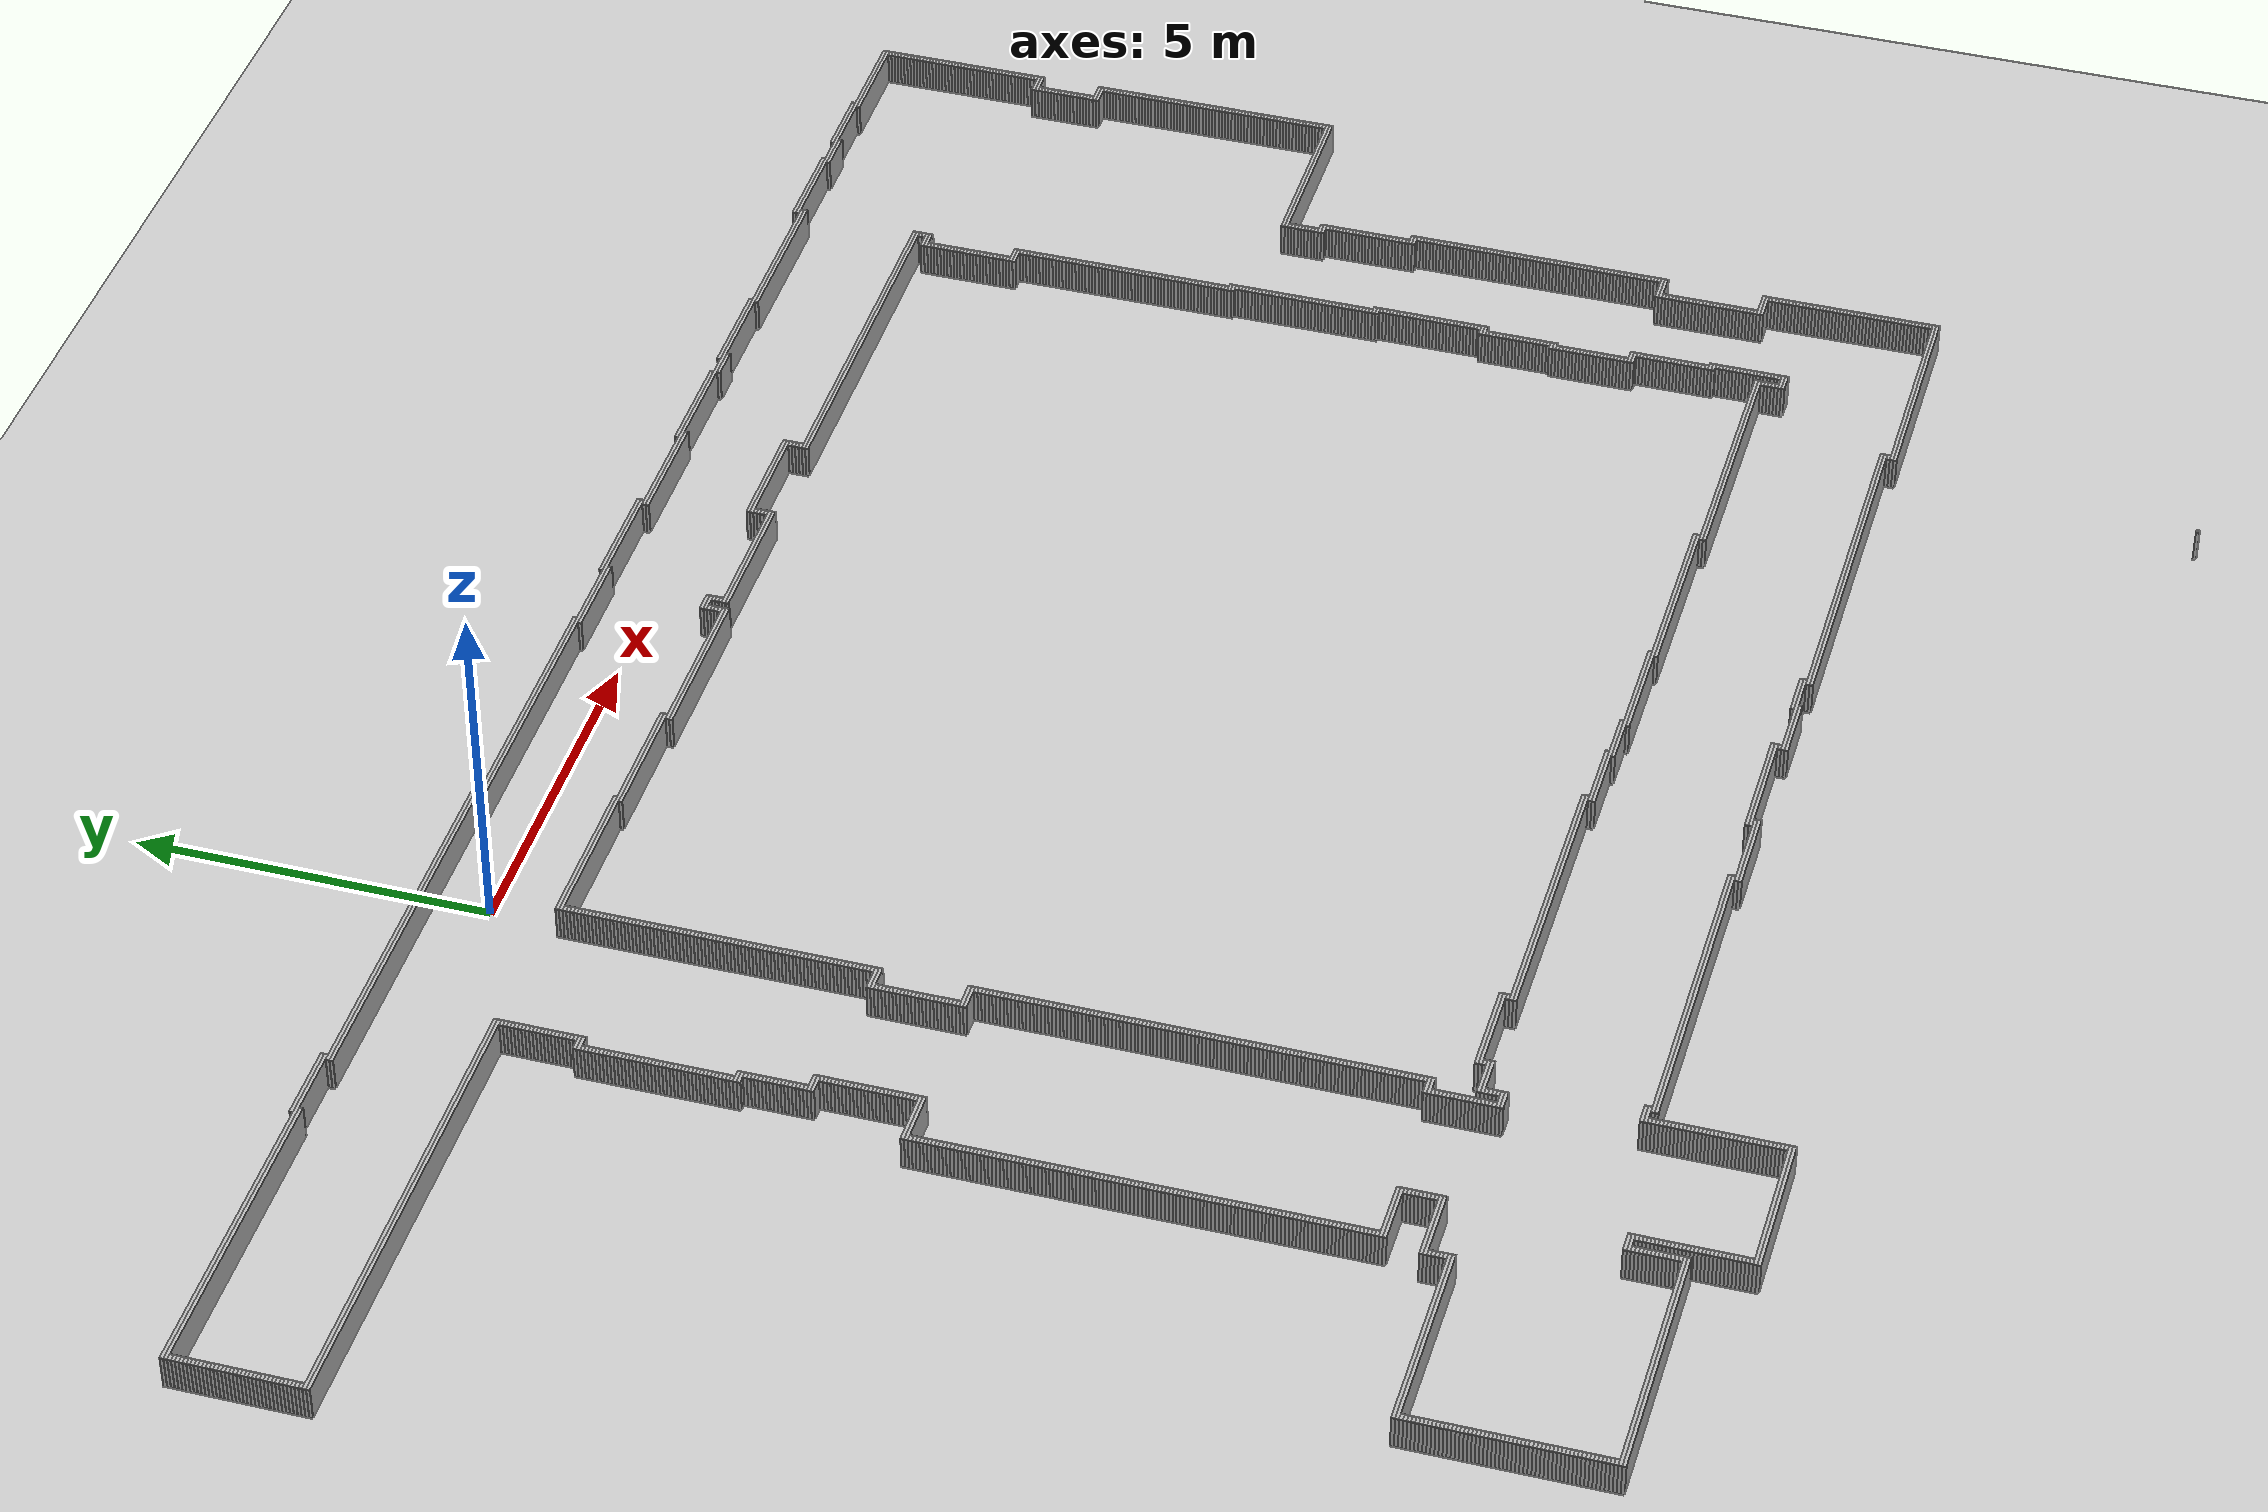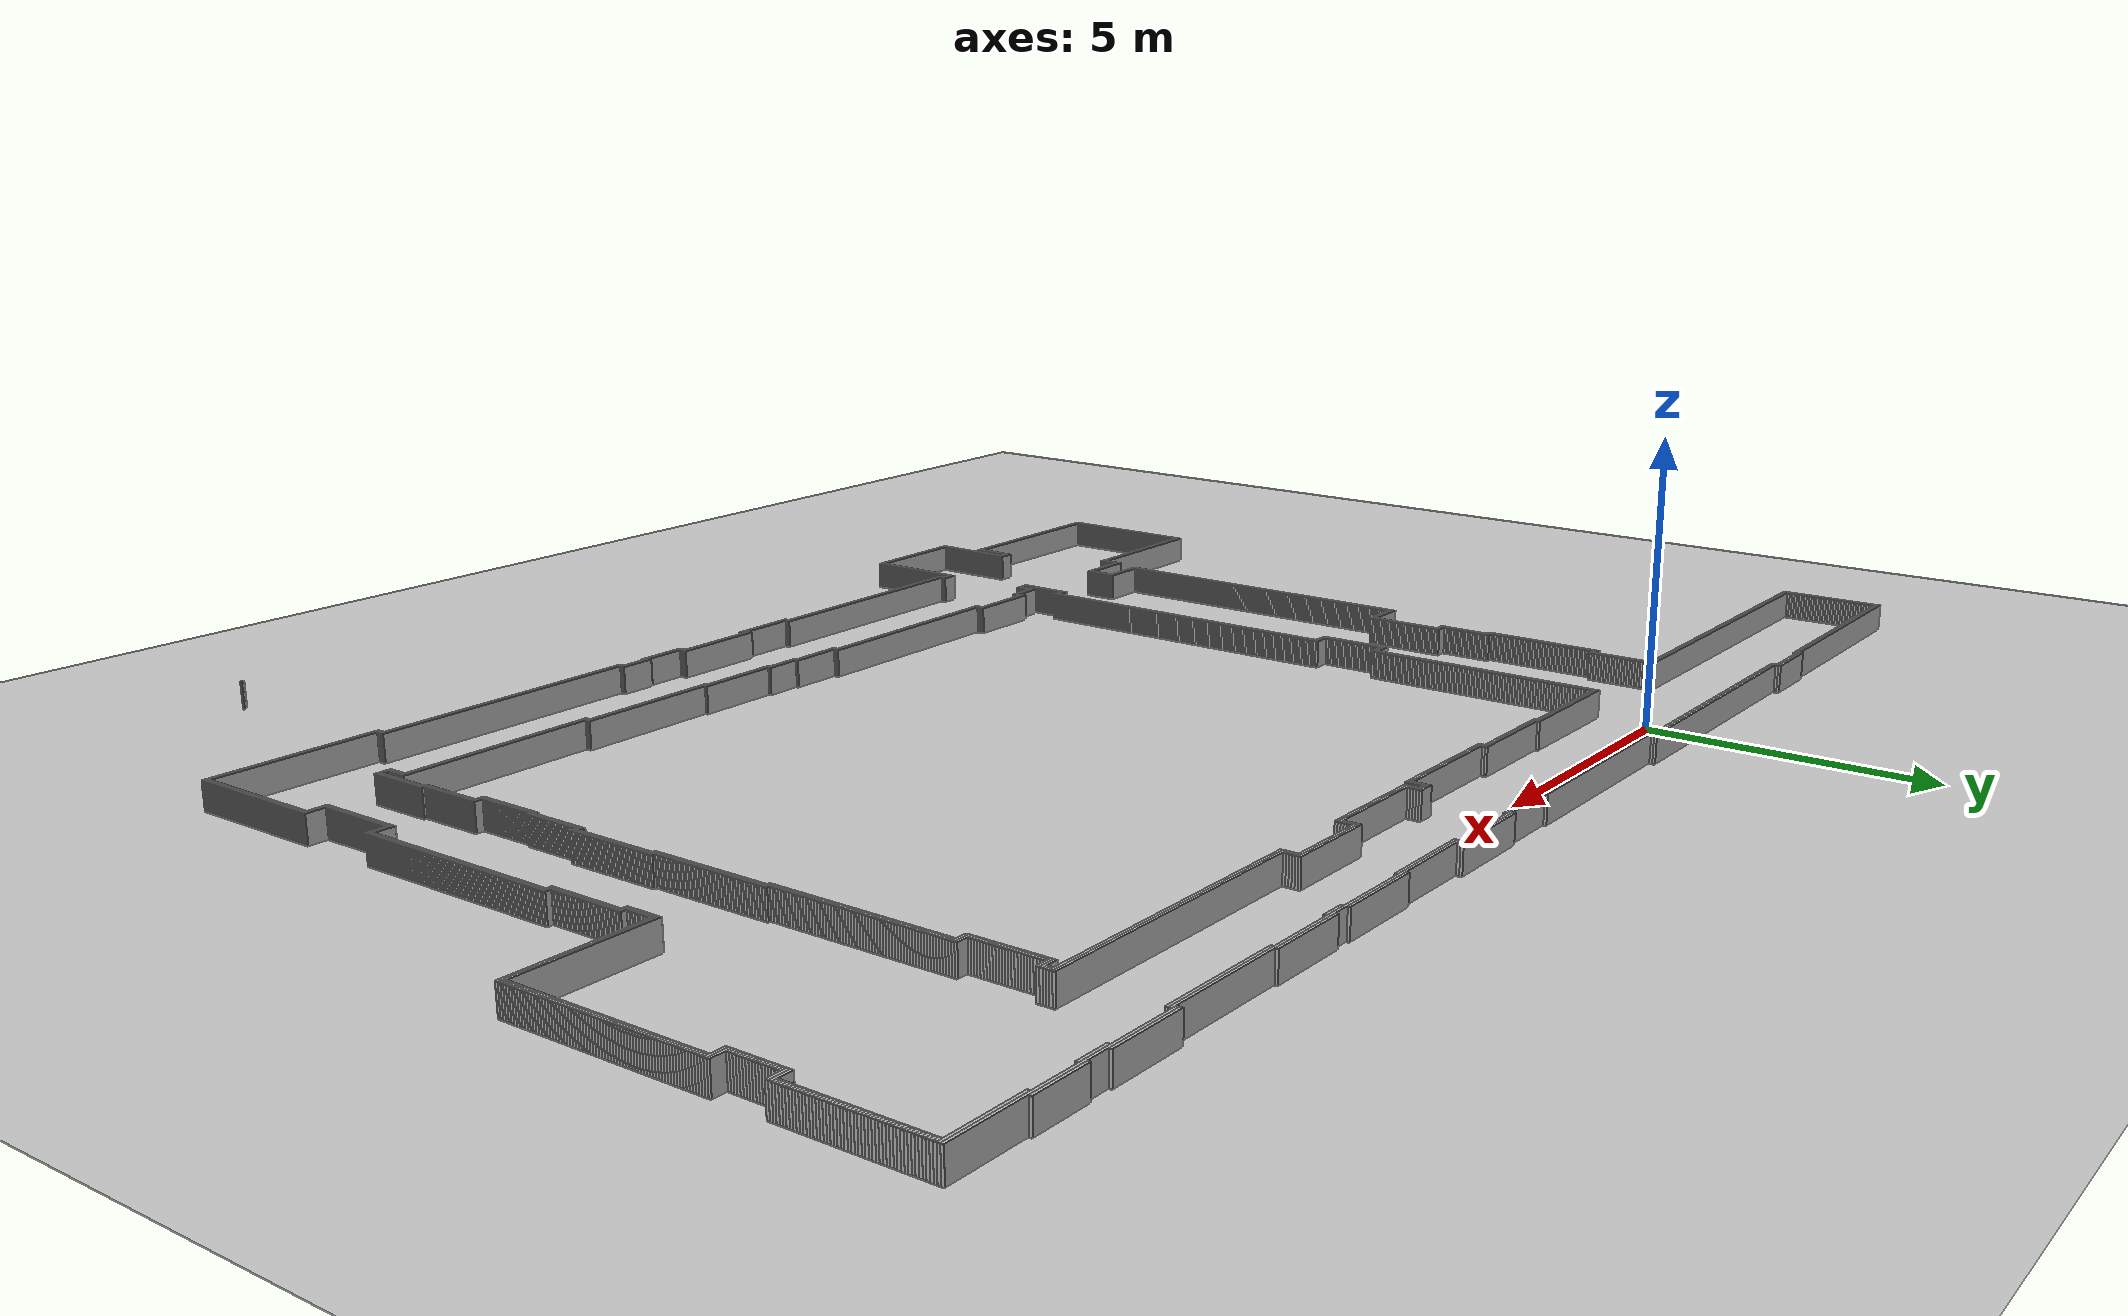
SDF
<sdf version='1.6'>
      <world name='optimized_map_world'>
        <include>
          <uri>model://sun</uri>
        </include>
        <include>
          <uri>model://ground_plane</uri>
        </include>
        <model name='obstacle_0'>
          <static>true</static>
          <link name='link'>
            <collision name='collision'>
              <geometry>
                <box>
                  <size>1.1 0.05 0.5</size>
                </box>
              </geometry>
            </collision>
            <visual name='visual'>
              <geometry>
                <box>
                  <size>1.1 0.05 0.5</size>
                </box>
              </geometry>
            </visual>
          </link>
          <pose>-4.074999999999999 0.9499999999999993 0.25 0 0 0</pose>
        </model>

        <model name='obstacle_1'>
          <static>true</static>
          <link name='link'>
            <collision name='collision'>
              <geometry>
                <box>
                  <size>5.5 0.05 0.5</size>
                </box>
              </geometry>
            </collision>
            <visual name='visual'>
              <geometry>
                <box>
                  <size>5.5 0.05 0.5</size>
                </box>
              </geometry>
            </visual>
          </link>
          <pose>-6.274999999999999 0.9000000000000021 0.25 0 0 0</pose>
        </model>

        <model name='obstacle_2'>
          <static>true</static>
          <link name='link'>
            <collision name='collision'>
              <geometry>
                <box>
                  <size>4.5 0.05 0.5</size>
                </box>
              </geometry>
            </collision>
            <visual name='visual'>
              <geometry>
                <box>
                  <size>4.5 0.05 0.5</size>
                </box>
              </geometry>
            </visual>
          </link>
          <pose>-6.774999999999999 0.8500000000000014 0.25 0 0 0</pose>
        </model>

        <model name='obstacle_3'>
          <static>true</static>
          <link name='link'>
            <collision name='collision'>
              <geometry>
                <box>
                  <size>5.300000000000001 0.05 0.5</size>
                </box>
              </geometry>
            </collision>
            <visual name='visual'>
              <geometry>
                <box>
                  <size>5.300000000000001 0.05 0.5</size>
                </box>
              </geometry>
            </visual>
          </link>
          <pose>-0.9749999999999979 0.8500000000000014 0.25 0 0 0</pose>
        </model>

        <model name='obstacle_4'>
          <static>true</static>
          <link name='link'>
            <collision name='collision'>
              <geometry>
                <box>
                  <size>0.1 0.05 0.5</size>
                </box>
              </geometry>
            </collision>
            <visual name='visual'>
              <geometry>
                <box>
                  <size>0.1 0.05 0.5</size>
                </box>
              </geometry>
            </visual>
          </link>
          <pose>-8.974999999999998 0.8000000000000007 0.25 0 0 0</pose>
        </model>

        <model name='obstacle_5'>
          <static>true</static>
          <link name='link'>
            <collision name='collision'>
              <geometry>
                <box>
                  <size>5.300000000000001 0.05 0.5</size>
                </box>
              </geometry>
            </collision>
            <visual name='visual'>
              <geometry>
                <box>
                  <size>5.300000000000001 0.05 0.5</size>
                </box>
              </geometry>
            </visual>
          </link>
          <pose>-0.9749999999999979 0.8000000000000007 0.25 0 0 0</pose>
        </model>

        <model name='obstacle_6'>
          <static>true</static>
          <link name='link'>
            <collision name='collision'>
              <geometry>
                <box>
                  <size>0.1 0.05 0.5</size>
                </box>
              </geometry>
            </collision>
            <visual name='visual'>
              <geometry>
                <box>
                  <size>0.1 0.05 0.5</size>
                </box>
              </geometry>
            </visual>
          </link>
          <pose>-8.974999999999998 0.75 0.25 0 0 0</pose>
        </model>

        <model name='obstacle_7'>
          <static>true</static>
          <link name='link'>
            <collision name='collision'>
              <geometry>
                <box>
                  <size>3.85 0.05 0.5</size>
                </box>
              </geometry>
            </collision>
            <visual name='visual'>
              <geometry>
                <box>
                  <size>3.85 0.05 0.5</size>
                </box>
              </geometry>
            </visual>
          </link>
          <pose>3.5000000000000036 0.75 0.25 0 0 0</pose>
        </model>

        <model name='obstacle_8'>
          <static>true</static>
          <link name='link'>
            <collision name='collision'>
              <geometry>
                <box>
                  <size>1.6 0.05 0.5</size>
                </box>
              </geometry>
            </collision>
            <visual name='visual'>
              <geometry>
                <box>
                  <size>1.6 0.05 0.5</size>
                </box>
              </geometry>
            </visual>
          </link>
          <pose>7.275000000000002 0.75 0.25 0 0 0</pose>
        </model>

        <model name='obstacle_9'>
          <static>true</static>
          <link name='link'>
            <collision name='collision'>
              <geometry>
                <box>
                  <size>1.4000000000000001 0.05 0.5</size>
                </box>
              </geometry>
            </collision>
            <visual name='visual'>
              <geometry>
                <box>
                  <size>1.4000000000000001 0.05 0.5</size>
                </box>
              </geometry>
            </visual>
          </link>
          <pose>15.675 0.75 0.25 0 0 0</pose>
        </model>

        <model name='obstacle_10'>
          <static>true</static>
          <link name='link'>
            <collision name='collision'>
              <geometry>
                <box>
                  <size>1.05 0.05 0.5</size>
                </box>
              </geometry>
            </collision>
            <visual name='visual'>
              <geometry>
                <box>
                  <size>1.05 0.05 0.5</size>
                </box>
              </geometry>
            </visual>
          </link>
          <pose>17.3 0.75 0.25 0 0 0</pose>
        </model>

        <model name='obstacle_11'>
          <static>true</static>
          <link name='link'>
            <collision name='collision'>
              <geometry>
                <box>
                  <size>0.1 0.05 0.5</size>
                </box>
              </geometry>
            </collision>
            <visual name='visual'>
              <geometry>
                <box>
                  <size>0.1 0.05 0.5</size>
                </box>
              </geometry>
            </visual>
          </link>
          <pose>-8.974999999999998 0.6999999999999993 0.25 0 0 0</pose>
        </model>

        <model name='obstacle_12'>
          <static>true</static>
          <link name='link'>
            <collision name='collision'>
              <geometry>
                <box>
                  <size>6.5 0.05 0.5</size>
                </box>
              </geometry>
            </collision>
            <visual name='visual'>
              <geometry>
                <box>
                  <size>6.5 0.05 0.5</size>
                </box>
              </geometry>
            </visual>
          </link>
          <pose>4.825000000000003 0.6999999999999993 0.25 0 0 0</pose>
        </model>

        <model name='obstacle_13'>
          <static>true</static>
          <link name='link'>
            <collision name='collision'>
              <geometry>
                <box>
                  <size>1.55 0.05 0.5</size>
                </box>
              </geometry>
            </collision>
            <visual name='visual'>
              <geometry>
                <box>
                  <size>1.55 0.05 0.5</size>
                </box>
              </geometry>
            </visual>
          </link>
          <pose>10.3 0.6999999999999993 0.25 0 0 0</pose>
        </model>

        <model name='obstacle_14'>
          <static>true</static>
          <link name='link'>
            <collision name='collision'>
              <geometry>
                <box>
                  <size>1.4500000000000002 0.05 0.5</size>
                </box>
              </geometry>
            </collision>
            <visual name='visual'>
              <geometry>
                <box>
                  <size>1.4500000000000002 0.05 0.5</size>
                </box>
              </geometry>
            </visual>
          </link>
          <pose>12.100000000000001 0.6999999999999993 0.25 0 0 0</pose>
        </model>

        <model name='obstacle_15'>
          <static>true</static>
          <link name='link'>
            <collision name='collision'>
              <geometry>
                <box>
                  <size>4.25 0.05 0.5</size>
                </box>
              </geometry>
            </collision>
            <visual name='visual'>
              <geometry>
                <box>
                  <size>4.25 0.05 0.5</size>
                </box>
              </geometry>
            </visual>
          </link>
          <pose>17.100000000000005 0.6999999999999993 0.25 0 0 0</pose>
        </model>

        <model name='obstacle_16'>
          <static>true</static>
          <link name='link'>
            <collision name='collision'>
              <geometry>
                <box>
                  <size>0.1 0.05 0.5</size>
                </box>
              </geometry>
            </collision>
            <visual name='visual'>
              <geometry>
                <box>
                  <size>0.1 0.05 0.5</size>
                </box>
              </geometry>
            </visual>
          </link>
          <pose>-8.974999999999998 0.6500000000000021 0.25 0 0 0</pose>
        </model>

        <model name='obstacle_17'>
          <static>true</static>
          <link name='link'>
            <collision name='collision'>
              <geometry>
                <box>
                  <size>1.25 0.05 0.5</size>
                </box>
              </geometry>
            </collision>
            <visual name='visual'>
              <geometry>
                <box>
                  <size>1.25 0.05 0.5</size>
                </box>
              </geometry>
            </visual>
          </link>
          <pose>5.950000000000003 0.6500000000000021 0.25 0 0 0</pose>
        </model>

        <model name='obstacle_18'>
          <static>true</static>
          <link name='link'>
            <collision name='collision'>
              <geometry>
                <box>
                  <size>7.1000000000000005 0.05 0.5</size>
                </box>
              </geometry>
            </collision>
            <visual name='visual'>
              <geometry>
                <box>
                  <size>7.1000000000000005 0.05 0.5</size>
                </box>
              </geometry>
            </visual>
          </link>
          <pose>11.525000000000002 0.6500000000000021 0.25 0 0 0</pose>
        </model>

        <model name='obstacle_19'>
          <static>true</static>
          <link name='link'>
            <collision name='collision'>
              <geometry>
                <box>
                  <size>0.6000000000000001 0.05 0.5</size>
                </box>
              </geometry>
            </collision>
            <visual name='visual'>
              <geometry>
                <box>
                  <size>0.6000000000000001 0.05 0.5</size>
                </box>
              </geometry>
            </visual>
          </link>
          <pose>16.575 0.6500000000000021 0.25 0 0 0</pose>
        </model>

        <model name='obstacle_20'>
          <static>true</static>
          <link name='link'>
            <collision name='collision'>
              <geometry>
                <box>
                  <size>1.5 0.05 0.5</size>
                </box>
              </geometry>
            </collision>
            <visual name='visual'>
              <geometry>
                <box>
                  <size>1.5 0.05 0.5</size>
                </box>
              </geometry>
            </visual>
          </link>
          <pose>18.475000000000005 0.6500000000000021 0.25 0 0 0</pose>
        </model>

        <model name='obstacle_21'>
          <static>true</static>
          <link name='link'>
            <collision name='collision'>
              <geometry>
                <box>
                  <size>0.1 0.05 0.5</size>
                </box>
              </geometry>
            </collision>
            <visual name='visual'>
              <geometry>
                <box>
                  <size>0.1 0.05 0.5</size>
                </box>
              </geometry>
            </visual>
          </link>
          <pose>-8.974999999999998 0.6000000000000014 0.25 0 0 0</pose>
        </model>

        <model name='obstacle_22'>
          <static>true</static>
          <link name='link'>
            <collision name='collision'>
              <geometry>
                <box>
                  <size>1.7000000000000002 0.05 0.5</size>
                </box>
              </geometry>
            </collision>
            <visual name='visual'>
              <geometry>
                <box>
                  <size>1.7000000000000002 0.05 0.5</size>
                </box>
              </geometry>
            </visual>
          </link>
          <pose>8.825000000000003 0.6000000000000014 0.25 0 0 0</pose>
        </model>

        <model name='obstacle_23'>
          <static>true</static>
          <link name='link'>
            <collision name='collision'>
              <geometry>
                <box>
                  <size>0.45 0.05 0.5</size>
                </box>
              </geometry>
            </collision>
            <visual name='visual'>
              <geometry>
                <box>
                  <size>0.45 0.05 0.5</size>
                </box>
              </geometry>
            </visual>
          </link>
          <pose>11.3 0.6000000000000014 0.25 0 0 0</pose>
        </model>

        <model name='obstacle_24'>
          <static>true</static>
          <link name='link'>
            <collision name='collision'>
              <geometry>
                <box>
                  <size>2.3000000000000003 0.05 0.5</size>
                </box>
              </geometry>
            </collision>
            <visual name='visual'>
              <geometry>
                <box>
                  <size>2.3000000000000003 0.05 0.5</size>
                </box>
              </geometry>
            </visual>
          </link>
          <pose>13.925 0.6000000000000014 0.25 0 0 0</pose>
        </model>

        <model name='obstacle_25'>
          <static>true</static>
          <link name='link'>
            <collision name='collision'>
              <geometry>
                <box>
                  <size>0.1 0.05 0.5</size>
                </box>
              </geometry>
            </collision>
            <visual name='visual'>
              <geometry>
                <box>
                  <size>0.1 0.05 0.5</size>
                </box>
              </geometry>
            </visual>
          </link>
          <pose>19.175 0.6000000000000014 0.25 0 0 0</pose>
        </model>

        <model name='obstacle_26'>
          <static>true</static>
          <link name='link'>
            <collision name='collision'>
              <geometry>
                <box>
                  <size>0.1 0.05 0.5</size>
                </box>
              </geometry>
            </collision>
            <visual name='visual'>
              <geometry>
                <box>
                  <size>0.1 0.05 0.5</size>
                </box>
              </geometry>
            </visual>
          </link>
          <pose>-8.974999999999998 0.5500000000000007 0.25 0 0 0</pose>
        </model>

        <model name='obstacle_27'>
          <static>true</static>
          <link name='link'>
            <collision name='collision'>
              <geometry>
                <box>
                  <size>0.1 0.05 0.5</size>
                </box>
              </geometry>
            </collision>
            <visual name='visual'>
              <geometry>
                <box>
                  <size>0.1 0.05 0.5</size>
                </box>
              </geometry>
            </visual>
          </link>
          <pose>19.175 0.5500000000000007 0.25 0 0 0</pose>
        </model>

        <model name='obstacle_28'>
          <static>true</static>
          <link name='link'>
            <collision name='collision'>
              <geometry>
                <box>
                  <size>0.1 0.05 0.5</size>
                </box>
              </geometry>
            </collision>
            <visual name='visual'>
              <geometry>
                <box>
                  <size>0.1 0.05 0.5</size>
                </box>
              </geometry>
            </visual>
          </link>
          <pose>-8.974999999999998 0.5 0.25 0 0 0</pose>
        </model>

        <model name='obstacle_29'>
          <static>true</static>
          <link name='link'>
            <collision name='collision'>
              <geometry>
                <box>
                  <size>0.1 0.05 0.5</size>
                </box>
              </geometry>
            </collision>
            <visual name='visual'>
              <geometry>
                <box>
                  <size>0.1 0.05 0.5</size>
                </box>
              </geometry>
            </visual>
          </link>
          <pose>19.175 0.5 0.25 0 0 0</pose>
        </model>

        <model name='obstacle_30'>
          <static>true</static>
          <link name='link'>
            <collision name='collision'>
              <geometry>
                <box>
                  <size>0.1 0.05 0.5</size>
                </box>
              </geometry>
            </collision>
            <visual name='visual'>
              <geometry>
                <box>
                  <size>0.1 0.05 0.5</size>
                </box>
              </geometry>
            </visual>
          </link>
          <pose>-8.974999999999998 0.4499999999999993 0.25 0 0 0</pose>
        </model>

        <model name='obstacle_31'>
          <static>true</static>
          <link name='link'>
            <collision name='collision'>
              <geometry>
                <box>
                  <size>0.1 0.05 0.5</size>
                </box>
              </geometry>
            </collision>
            <visual name='visual'>
              <geometry>
                <box>
                  <size>0.1 0.05 0.5</size>
                </box>
              </geometry>
            </visual>
          </link>
          <pose>19.175 0.4499999999999993 0.25 0 0 0</pose>
        </model>

        <model name='obstacle_32'>
          <static>true</static>
          <link name='link'>
            <collision name='collision'>
              <geometry>
                <box>
                  <size>0.1 0.05 0.5</size>
                </box>
              </geometry>
            </collision>
            <visual name='visual'>
              <geometry>
                <box>
                  <size>0.1 0.05 0.5</size>
                </box>
              </geometry>
            </visual>
          </link>
          <pose>-8.974999999999998 0.40000000000000213 0.25 0 0 0</pose>
        </model>

        <model name='obstacle_33'>
          <static>true</static>
          <link name='link'>
            <collision name='collision'>
              <geometry>
                <box>
                  <size>0.1 0.05 0.5</size>
                </box>
              </geometry>
            </collision>
            <visual name='visual'>
              <geometry>
                <box>
                  <size>0.1 0.05 0.5</size>
                </box>
              </geometry>
            </visual>
          </link>
          <pose>19.175 0.40000000000000213 0.25 0 0 0</pose>
        </model>

        <model name='obstacle_34'>
          <static>true</static>
          <link name='link'>
            <collision name='collision'>
              <geometry>
                <box>
                  <size>0.1 0.05 0.5</size>
                </box>
              </geometry>
            </collision>
            <visual name='visual'>
              <geometry>
                <box>
                  <size>0.1 0.05 0.5</size>
                </box>
              </geometry>
            </visual>
          </link>
          <pose>-8.974999999999998 0.3500000000000014 0.25 0 0 0</pose>
        </model>

        <model name='obstacle_35'>
          <static>true</static>
          <link name='link'>
            <collision name='collision'>
              <geometry>
                <box>
                  <size>0.1 0.05 0.5</size>
                </box>
              </geometry>
            </collision>
            <visual name='visual'>
              <geometry>
                <box>
                  <size>0.1 0.05 0.5</size>
                </box>
              </geometry>
            </visual>
          </link>
          <pose>19.175 0.3500000000000014 0.25 0 0 0</pose>
        </model>

        <model name='obstacle_36'>
          <static>true</static>
          <link name='link'>
            <collision name='collision'>
              <geometry>
                <box>
                  <size>0.1 0.05 0.5</size>
                </box>
              </geometry>
            </collision>
            <visual name='visual'>
              <geometry>
                <box>
                  <size>0.1 0.05 0.5</size>
                </box>
              </geometry>
            </visual>
          </link>
          <pose>-8.974999999999998 0.3000000000000007 0.25 0 0 0</pose>
        </model>

        <model name='obstacle_37'>
          <static>true</static>
          <link name='link'>
            <collision name='collision'>
              <geometry>
                <box>
                  <size>0.1 0.05 0.5</size>
                </box>
              </geometry>
            </collision>
            <visual name='visual'>
              <geometry>
                <box>
                  <size>0.1 0.05 0.5</size>
                </box>
              </geometry>
            </visual>
          </link>
          <pose>19.175 0.3000000000000007 0.25 0 0 0</pose>
        </model>

        <model name='obstacle_38'>
          <static>true</static>
          <link name='link'>
            <collision name='collision'>
              <geometry>
                <box>
                  <size>0.1 0.05 0.5</size>
                </box>
              </geometry>
            </collision>
            <visual name='visual'>
              <geometry>
                <box>
                  <size>0.1 0.05 0.5</size>
                </box>
              </geometry>
            </visual>
          </link>
          <pose>-8.974999999999998 0.25 0.25 0 0 0</pose>
        </model>

        <model name='obstacle_39'>
          <static>true</static>
          <link name='link'>
            <collision name='collision'>
              <geometry>
                <box>
                  <size>0.1 0.05 0.5</size>
                </box>
              </geometry>
            </collision>
            <visual name='visual'>
              <geometry>
                <box>
                  <size>0.1 0.05 0.5</size>
                </box>
              </geometry>
            </visual>
          </link>
          <pose>19.175 0.25 0.25 0 0 0</pose>
        </model>

        <model name='obstacle_40'>
          <static>true</static>
          <link name='link'>
            <collision name='collision'>
              <geometry>
                <box>
                  <size>0.1 0.05 0.5</size>
                </box>
              </geometry>
            </collision>
            <visual name='visual'>
              <geometry>
                <box>
                  <size>0.1 0.05 0.5</size>
                </box>
              </geometry>
            </visual>
          </link>
          <pose>-8.974999999999998 0.1999999999999993 0.25 0 0 0</pose>
        </model>

        <model name='obstacle_41'>
          <static>true</static>
          <link name='link'>
            <collision name='collision'>
              <geometry>
                <box>
                  <size>0.1 0.05 0.5</size>
                </box>
              </geometry>
            </collision>
            <visual name='visual'>
              <geometry>
                <box>
                  <size>0.1 0.05 0.5</size>
                </box>
              </geometry>
            </visual>
          </link>
          <pose>19.175 0.1999999999999993 0.25 0 0 0</pose>
        </model>

        <model name='obstacle_42'>
          <static>true</static>
          <link name='link'>
            <collision name='collision'>
              <geometry>
                <box>
                  <size>0.1 0.05 0.5</size>
                </box>
              </geometry>
            </collision>
            <visual name='visual'>
              <geometry>
                <box>
                  <size>0.1 0.05 0.5</size>
                </box>
              </geometry>
            </visual>
          </link>
          <pose>-8.974999999999998 0.15000000000000213 0.25 0 0 0</pose>
        </model>

        <model name='obstacle_43'>
          <static>true</static>
          <link name='link'>
            <collision name='collision'>
              <geometry>
                <box>
                  <size>0.1 0.05 0.5</size>
                </box>
              </geometry>
            </collision>
            <visual name='visual'>
              <geometry>
                <box>
                  <size>0.1 0.05 0.5</size>
                </box>
              </geometry>
            </visual>
          </link>
          <pose>19.175 0.15000000000000213 0.25 0 0 0</pose>
        </model>

        <model name='obstacle_44'>
          <static>true</static>
          <link name='link'>
            <collision name='collision'>
              <geometry>
                <box>
                  <size>0.1 0.05 0.5</size>
                </box>
              </geometry>
            </collision>
            <visual name='visual'>
              <geometry>
                <box>
                  <size>0.1 0.05 0.5</size>
                </box>
              </geometry>
            </visual>
          </link>
          <pose>-8.974999999999998 0.10000000000000142 0.25 0 0 0</pose>
        </model>

        <model name='obstacle_45'>
          <static>true</static>
          <link name='link'>
            <collision name='collision'>
              <geometry>
                <box>
                  <size>0.1 0.05 0.5</size>
                </box>
              </geometry>
            </collision>
            <visual name='visual'>
              <geometry>
                <box>
                  <size>0.1 0.05 0.5</size>
                </box>
              </geometry>
            </visual>
          </link>
          <pose>19.175 0.10000000000000142 0.25 0 0 0</pose>
        </model>

        <model name='obstacle_46'>
          <static>true</static>
          <link name='link'>
            <collision name='collision'>
              <geometry>
                <box>
                  <size>0.1 0.05 0.5</size>
                </box>
              </geometry>
            </collision>
            <visual name='visual'>
              <geometry>
                <box>
                  <size>0.1 0.05 0.5</size>
                </box>
              </geometry>
            </visual>
          </link>
          <pose>-8.974999999999998 0.05000000000000071 0.25 0 0 0</pose>
        </model>

        <model name='obstacle_47'>
          <static>true</static>
          <link name='link'>
            <collision name='collision'>
              <geometry>
                <box>
                  <size>0.1 0.05 0.5</size>
                </box>
              </geometry>
            </collision>
            <visual name='visual'>
              <geometry>
                <box>
                  <size>0.1 0.05 0.5</size>
                </box>
              </geometry>
            </visual>
          </link>
          <pose>19.175 0.05000000000000071 0.25 0 0 0</pose>
        </model>

        <model name='obstacle_48'>
          <static>true</static>
          <link name='link'>
            <collision name='collision'>
              <geometry>
                <box>
                  <size>0.1 0.05 0.5</size>
                </box>
              </geometry>
            </collision>
            <visual name='visual'>
              <geometry>
                <box>
                  <size>0.1 0.05 0.5</size>
                </box>
              </geometry>
            </visual>
          </link>
          <pose>-8.974999999999998 0.0 0.25 0 0 0</pose>
        </model>

        <model name='obstacle_49'>
          <static>true</static>
          <link name='link'>
            <collision name='collision'>
              <geometry>
                <box>
                  <size>0.1 0.05 0.5</size>
                </box>
              </geometry>
            </collision>
            <visual name='visual'>
              <geometry>
                <box>
                  <size>0.1 0.05 0.5</size>
                </box>
              </geometry>
            </visual>
          </link>
          <pose>19.175 0.0 0.25 0 0 0</pose>
        </model>

        <model name='obstacle_50'>
          <static>true</static>
          <link name='link'>
            <collision name='collision'>
              <geometry>
                <box>
                  <size>0.1 0.05 0.5</size>
                </box>
              </geometry>
            </collision>
            <visual name='visual'>
              <geometry>
                <box>
                  <size>0.1 0.05 0.5</size>
                </box>
              </geometry>
            </visual>
          </link>
          <pose>-8.974999999999998 -0.05000000000000071 0.25 0 0 0</pose>
        </model>

        <model name='obstacle_51'>
          <static>true</static>
          <link name='link'>
            <collision name='collision'>
              <geometry>
                <box>
                  <size>0.1 0.05 0.5</size>
                </box>
              </geometry>
            </collision>
            <visual name='visual'>
              <geometry>
                <box>
                  <size>0.1 0.05 0.5</size>
                </box>
              </geometry>
            </visual>
          </link>
          <pose>19.175 -0.05000000000000071 0.25 0 0 0</pose>
        </model>

        <model name='obstacle_52'>
          <static>true</static>
          <link name='link'>
            <collision name='collision'>
              <geometry>
                <box>
                  <size>0.1 0.05 0.5</size>
                </box>
              </geometry>
            </collision>
            <visual name='visual'>
              <geometry>
                <box>
                  <size>0.1 0.05 0.5</size>
                </box>
              </geometry>
            </visual>
          </link>
          <pose>-8.974999999999998 -0.09999999999999787 0.25 0 0 0</pose>
        </model>

        <model name='obstacle_53'>
          <static>true</static>
          <link name='link'>
            <collision name='collision'>
              <geometry>
                <box>
                  <size>0.1 0.05 0.5</size>
                </box>
              </geometry>
            </collision>
            <visual name='visual'>
              <geometry>
                <box>
                  <size>0.1 0.05 0.5</size>
                </box>
              </geometry>
            </visual>
          </link>
          <pose>19.175 -0.09999999999999787 0.25 0 0 0</pose>
        </model>

        <model name='obstacle_54'>
          <static>true</static>
          <link name='link'>
            <collision name='collision'>
              <geometry>
                <box>
                  <size>0.1 0.05 0.5</size>
                </box>
              </geometry>
            </collision>
            <visual name='visual'>
              <geometry>
                <box>
                  <size>0.1 0.05 0.5</size>
                </box>
              </geometry>
            </visual>
          </link>
          <pose>-8.974999999999998 -0.14999999999999858 0.25 0 0 0</pose>
        </model>

        <model name='obstacle_55'>
          <static>true</static>
          <link name='link'>
            <collision name='collision'>
              <geometry>
                <box>
                  <size>0.1 0.05 0.5</size>
                </box>
              </geometry>
            </collision>
            <visual name='visual'>
              <geometry>
                <box>
                  <size>0.1 0.05 0.5</size>
                </box>
              </geometry>
            </visual>
          </link>
          <pose>19.175 -0.14999999999999858 0.25 0 0 0</pose>
        </model>

        <model name='obstacle_56'>
          <static>true</static>
          <link name='link'>
            <collision name='collision'>
              <geometry>
                <box>
                  <size>0.1 0.05 0.5</size>
                </box>
              </geometry>
            </collision>
            <visual name='visual'>
              <geometry>
                <box>
                  <size>0.1 0.05 0.5</size>
                </box>
              </geometry>
            </visual>
          </link>
          <pose>-8.974999999999998 -0.1999999999999993 0.25 0 0 0</pose>
        </model>

        <model name='obstacle_57'>
          <static>true</static>
          <link name='link'>
            <collision name='collision'>
              <geometry>
                <box>
                  <size>0.1 0.05 0.5</size>
                </box>
              </geometry>
            </collision>
            <visual name='visual'>
              <geometry>
                <box>
                  <size>0.1 0.05 0.5</size>
                </box>
              </geometry>
            </visual>
          </link>
          <pose>19.175 -0.1999999999999993 0.25 0 0 0</pose>
        </model>

        <model name='obstacle_58'>
          <static>true</static>
          <link name='link'>
            <collision name='collision'>
              <geometry>
                <box>
                  <size>0.1 0.05 0.5</size>
                </box>
              </geometry>
            </collision>
            <visual name='visual'>
              <geometry>
                <box>
                  <size>0.1 0.05 0.5</size>
                </box>
              </geometry>
            </visual>
          </link>
          <pose>-8.974999999999998 -0.25 0.25 0 0 0</pose>
        </model>

        <model name='obstacle_59'>
          <static>true</static>
          <link name='link'>
            <collision name='collision'>
              <geometry>
                <box>
                  <size>0.1 0.05 0.5</size>
                </box>
              </geometry>
            </collision>
            <visual name='visual'>
              <geometry>
                <box>
                  <size>0.1 0.05 0.5</size>
                </box>
              </geometry>
            </visual>
          </link>
          <pose>19.175 -0.25 0.25 0 0 0</pose>
        </model>

        <model name='obstacle_60'>
          <static>true</static>
          <link name='link'>
            <collision name='collision'>
              <geometry>
                <box>
                  <size>0.1 0.05 0.5</size>
                </box>
              </geometry>
            </collision>
            <visual name='visual'>
              <geometry>
                <box>
                  <size>0.1 0.05 0.5</size>
                </box>
              </geometry>
            </visual>
          </link>
          <pose>-8.974999999999998 -0.3000000000000007 0.25 0 0 0</pose>
        </model>

        <model name='obstacle_61'>
          <static>true</static>
          <link name='link'>
            <collision name='collision'>
              <geometry>
                <box>
                  <size>0.1 0.05 0.5</size>
                </box>
              </geometry>
            </collision>
            <visual name='visual'>
              <geometry>
                <box>
                  <size>0.1 0.05 0.5</size>
                </box>
              </geometry>
            </visual>
          </link>
          <pose>19.175 -0.3000000000000007 0.25 0 0 0</pose>
        </model>

        <model name='obstacle_62'>
          <static>true</static>
          <link name='link'>
            <collision name='collision'>
              <geometry>
                <box>
                  <size>0.1 0.05 0.5</size>
                </box>
              </geometry>
            </collision>
            <visual name='visual'>
              <geometry>
                <box>
                  <size>0.1 0.05 0.5</size>
                </box>
              </geometry>
            </visual>
          </link>
          <pose>-8.974999999999998 -0.34999999999999787 0.25 0 0 0</pose>
        </model>

        <model name='obstacle_63'>
          <static>true</static>
          <link name='link'>
            <collision name='collision'>
              <geometry>
                <box>
                  <size>0.1 0.05 0.5</size>
                </box>
              </geometry>
            </collision>
            <visual name='visual'>
              <geometry>
                <box>
                  <size>0.1 0.05 0.5</size>
                </box>
              </geometry>
            </visual>
          </link>
          <pose>19.175 -0.34999999999999787 0.25 0 0 0</pose>
        </model>

        <model name='obstacle_64'>
          <static>true</static>
          <link name='link'>
            <collision name='collision'>
              <geometry>
                <box>
                  <size>0.1 0.05 0.5</size>
                </box>
              </geometry>
            </collision>
            <visual name='visual'>
              <geometry>
                <box>
                  <size>0.1 0.05 0.5</size>
                </box>
              </geometry>
            </visual>
          </link>
          <pose>-8.974999999999998 -0.3999999999999986 0.25 0 0 0</pose>
        </model>

        <model name='obstacle_65'>
          <static>true</static>
          <link name='link'>
            <collision name='collision'>
              <geometry>
                <box>
                  <size>0.1 0.05 0.5</size>
                </box>
              </geometry>
            </collision>
            <visual name='visual'>
              <geometry>
                <box>
                  <size>0.1 0.05 0.5</size>
                </box>
              </geometry>
            </visual>
          </link>
          <pose>19.175 -0.3999999999999986 0.25 0 0 0</pose>
        </model>

        <model name='obstacle_66'>
          <static>true</static>
          <link name='link'>
            <collision name='collision'>
              <geometry>
                <box>
                  <size>0.1 0.05 0.5</size>
                </box>
              </geometry>
            </collision>
            <visual name='visual'>
              <geometry>
                <box>
                  <size>0.1 0.05 0.5</size>
                </box>
              </geometry>
            </visual>
          </link>
          <pose>-8.974999999999998 -0.4499999999999993 0.25 0 0 0</pose>
        </model>

        <model name='obstacle_67'>
          <static>true</static>
          <link name='link'>
            <collision name='collision'>
              <geometry>
                <box>
                  <size>0.1 0.05 0.5</size>
                </box>
              </geometry>
            </collision>
            <visual name='visual'>
              <geometry>
                <box>
                  <size>0.1 0.05 0.5</size>
                </box>
              </geometry>
            </visual>
          </link>
          <pose>19.175 -0.4499999999999993 0.25 0 0 0</pose>
        </model>

        <model name='obstacle_68'>
          <static>true</static>
          <link name='link'>
            <collision name='collision'>
              <geometry>
                <box>
                  <size>0.1 0.05 0.5</size>
                </box>
              </geometry>
            </collision>
            <visual name='visual'>
              <geometry>
                <box>
                  <size>0.1 0.05 0.5</size>
                </box>
              </geometry>
            </visual>
          </link>
          <pose>-8.974999999999998 -0.5 0.25 0 0 0</pose>
        </model>

        <model name='obstacle_69'>
          <static>true</static>
          <link name='link'>
            <collision name='collision'>
              <geometry>
                <box>
                  <size>0.1 0.05 0.5</size>
                </box>
              </geometry>
            </collision>
            <visual name='visual'>
              <geometry>
                <box>
                  <size>0.1 0.05 0.5</size>
                </box>
              </geometry>
            </visual>
          </link>
          <pose>19.175 -0.5 0.25 0 0 0</pose>
        </model>

        <model name='obstacle_70'>
          <static>true</static>
          <link name='link'>
            <collision name='collision'>
              <geometry>
                <box>
                  <size>0.1 0.05 0.5</size>
                </box>
              </geometry>
            </collision>
            <visual name='visual'>
              <geometry>
                <box>
                  <size>0.1 0.05 0.5</size>
                </box>
              </geometry>
            </visual>
          </link>
          <pose>-8.974999999999998 -0.5500000000000007 0.25 0 0 0</pose>
        </model>

        <model name='obstacle_71'>
          <static>true</static>
          <link name='link'>
            <collision name='collision'>
              <geometry>
                <box>
                  <size>0.1 0.05 0.5</size>
                </box>
              </geometry>
            </collision>
            <visual name='visual'>
              <geometry>
                <box>
                  <size>0.1 0.05 0.5</size>
                </box>
              </geometry>
            </visual>
          </link>
          <pose>19.175 -0.5500000000000007 0.25 0 0 0</pose>
        </model>

        <model name='obstacle_72'>
          <static>true</static>
          <link name='link'>
            <collision name='collision'>
              <geometry>
                <box>
                  <size>0.1 0.05 0.5</size>
                </box>
              </geometry>
            </collision>
            <visual name='visual'>
              <geometry>
                <box>
                  <size>0.1 0.05 0.5</size>
                </box>
              </geometry>
            </visual>
          </link>
          <pose>-8.974999999999998 -0.5999999999999979 0.25 0 0 0</pose>
        </model>

        <model name='obstacle_73'>
          <static>true</static>
          <link name='link'>
            <collision name='collision'>
              <geometry>
                <box>
                  <size>0.1 0.05 0.5</size>
                </box>
              </geometry>
            </collision>
            <visual name='visual'>
              <geometry>
                <box>
                  <size>0.1 0.05 0.5</size>
                </box>
              </geometry>
            </visual>
          </link>
          <pose>19.175 -0.5999999999999979 0.25 0 0 0</pose>
        </model>

        <model name='obstacle_74'>
          <static>true</static>
          <link name='link'>
            <collision name='collision'>
              <geometry>
                <box>
                  <size>0.1 0.05 0.5</size>
                </box>
              </geometry>
            </collision>
            <visual name='visual'>
              <geometry>
                <box>
                  <size>0.1 0.05 0.5</size>
                </box>
              </geometry>
            </visual>
          </link>
          <pose>-8.974999999999998 -0.6499999999999986 0.25 0 0 0</pose>
        </model>

        <model name='obstacle_75'>
          <static>true</static>
          <link name='link'>
            <collision name='collision'>
              <geometry>
                <box>
                  <size>0.1 0.05 0.5</size>
                </box>
              </geometry>
            </collision>
            <visual name='visual'>
              <geometry>
                <box>
                  <size>0.1 0.05 0.5</size>
                </box>
              </geometry>
            </visual>
          </link>
          <pose>19.175 -0.6499999999999986 0.25 0 0 0</pose>
        </model>

        <model name='obstacle_76'>
          <static>true</static>
          <link name='link'>
            <collision name='collision'>
              <geometry>
                <box>
                  <size>0.1 0.05 0.5</size>
                </box>
              </geometry>
            </collision>
            <visual name='visual'>
              <geometry>
                <box>
                  <size>0.1 0.05 0.5</size>
                </box>
              </geometry>
            </visual>
          </link>
          <pose>-8.974999999999998 -0.6999999999999993 0.25 0 0 0</pose>
        </model>

        <model name='obstacle_77'>
          <static>true</static>
          <link name='link'>
            <collision name='collision'>
              <geometry>
                <box>
                  <size>0.1 0.05 0.5</size>
                </box>
              </geometry>
            </collision>
            <visual name='visual'>
              <geometry>
                <box>
                  <size>0.1 0.05 0.5</size>
                </box>
              </geometry>
            </visual>
          </link>
          <pose>19.175 -0.6999999999999993 0.25 0 0 0</pose>
        </model>

        <model name='obstacle_78'>
          <static>true</static>
          <link name='link'>
            <collision name='collision'>
              <geometry>
                <box>
                  <size>0.1 0.05 0.5</size>
                </box>
              </geometry>
            </collision>
            <visual name='visual'>
              <geometry>
                <box>
                  <size>0.1 0.05 0.5</size>
                </box>
              </geometry>
            </visual>
          </link>
          <pose>-8.974999999999998 -0.75 0.25 0 0 0</pose>
        </model>

        <model name='obstacle_79'>
          <static>true</static>
          <link name='link'>
            <collision name='collision'>
              <geometry>
                <box>
                  <size>0.1 0.05 0.5</size>
                </box>
              </geometry>
            </collision>
            <visual name='visual'>
              <geometry>
                <box>
                  <size>0.1 0.05 0.5</size>
                </box>
              </geometry>
            </visual>
          </link>
          <pose>19.175 -0.75 0.25 0 0 0</pose>
        </model>

        <model name='obstacle_80'>
          <static>true</static>
          <link name='link'>
            <collision name='collision'>
              <geometry>
                <box>
                  <size>0.1 0.05 0.5</size>
                </box>
              </geometry>
            </collision>
            <visual name='visual'>
              <geometry>
                <box>
                  <size>0.1 0.05 0.5</size>
                </box>
              </geometry>
            </visual>
          </link>
          <pose>-8.974999999999998 -0.8000000000000007 0.25 0 0 0</pose>
        </model>

        <model name='obstacle_81'>
          <static>true</static>
          <link name='link'>
            <collision name='collision'>
              <geometry>
                <box>
                  <size>1.6500000000000001 0.05 0.5</size>
                </box>
              </geometry>
            </collision>
            <visual name='visual'>
              <geometry>
                <box>
                  <size>1.6500000000000001 0.05 0.5</size>
                </box>
              </geometry>
            </visual>
          </link>
          <pose>9.05 -0.8000000000000007 0.25 0 0 0</pose>
        </model>

        <model name='obstacle_82'>
          <static>true</static>
          <link name='link'>
            <collision name='collision'>
              <geometry>
                <box>
                  <size>0.1 0.05 0.5</size>
                </box>
              </geometry>
            </collision>
            <visual name='visual'>
              <geometry>
                <box>
                  <size>0.1 0.05 0.5</size>
                </box>
              </geometry>
            </visual>
          </link>
          <pose>19.175 -0.8000000000000007 0.25 0 0 0</pose>
        </model>

        <model name='obstacle_83'>
          <static>true</static>
          <link name='link'>
            <collision name='collision'>
              <geometry>
                <box>
                  <size>0.1 0.05 0.5</size>
                </box>
              </geometry>
            </collision>
            <visual name='visual'>
              <geometry>
                <box>
                  <size>0.1 0.05 0.5</size>
                </box>
              </geometry>
            </visual>
          </link>
          <pose>-8.974999999999998 -0.8499999999999979 0.25 0 0 0</pose>
        </model>

        <model name='obstacle_84'>
          <static>true</static>
          <link name='link'>
            <collision name='collision'>
              <geometry>
                <box>
                  <size>0.30000000000000004 0.05 0.5</size>
                </box>
              </geometry>
            </collision>
            <visual name='visual'>
              <geometry>
                <box>
                  <size>0.30000000000000004 0.05 0.5</size>
                </box>
              </geometry>
            </visual>
          </link>
          <pose>6.225000000000001 -0.8499999999999979 0.25 0 0 0</pose>
        </model>

        <model name='obstacle_85'>
          <static>true</static>
          <link name='link'>
            <collision name='collision'>
              <geometry>
                <box>
                  <size>1.6500000000000001 0.05 0.5</size>
                </box>
              </geometry>
            </collision>
            <visual name='visual'>
              <geometry>
                <box>
                  <size>1.6500000000000001 0.05 0.5</size>
                </box>
              </geometry>
            </visual>
          </link>
          <pose>9.05 -0.8499999999999979 0.25 0 0 0</pose>
        </model>

        <model name='obstacle_86'>
          <static>true</static>
          <link name='link'>
            <collision name='collision'>
              <geometry>
                <box>
                  <size>0.1 0.05 0.5</size>
                </box>
              </geometry>
            </collision>
            <visual name='visual'>
              <geometry>
                <box>
                  <size>0.1 0.05 0.5</size>
                </box>
              </geometry>
            </visual>
          </link>
          <pose>19.175 -0.8499999999999979 0.25 0 0 0</pose>
        </model>

        <model name='obstacle_87'>
          <static>true</static>
          <link name='link'>
            <collision name='collision'>
              <geometry>
                <box>
                  <size>0.1 0.05 0.5</size>
                </box>
              </geometry>
            </collision>
            <visual name='visual'>
              <geometry>
                <box>
                  <size>0.1 0.05 0.5</size>
                </box>
              </geometry>
            </visual>
          </link>
          <pose>-8.974999999999998 -0.8999999999999986 0.25 0 0 0</pose>
        </model>

        <model name='obstacle_88'>
          <static>true</static>
          <link name='link'>
            <collision name='collision'>
              <geometry>
                <box>
                  <size>0.30000000000000004 0.05 0.5</size>
                </box>
              </geometry>
            </collision>
            <visual name='visual'>
              <geometry>
                <box>
                  <size>0.30000000000000004 0.05 0.5</size>
                </box>
              </geometry>
            </visual>
          </link>
          <pose>6.225000000000001 -0.8999999999999986 0.25 0 0 0</pose>
        </model>

        <model name='obstacle_89'>
          <static>true</static>
          <link name='link'>
            <collision name='collision'>
              <geometry>
                <box>
                  <size>0.1 0.05 0.5</size>
                </box>
              </geometry>
            </collision>
            <visual name='visual'>
              <geometry>
                <box>
                  <size>0.1 0.05 0.5</size>
                </box>
              </geometry>
            </visual>
          </link>
          <pose>8.275000000000002 -0.8999999999999986 0.25 0 0 0</pose>
        </model>

        <model name='obstacle_90'>
          <static>true</static>
          <link name='link'>
            <collision name='collision'>
              <geometry>
                <box>
                  <size>0.1 0.05 0.5</size>
                </box>
              </geometry>
            </collision>
            <visual name='visual'>
              <geometry>
                <box>
                  <size>0.1 0.05 0.5</size>
                </box>
              </geometry>
            </visual>
          </link>
          <pose>9.825000000000003 -0.8999999999999986 0.25 0 0 0</pose>
        </model>

        <model name='obstacle_91'>
          <static>true</static>
          <link name='link'>
            <collision name='collision'>
              <geometry>
                <box>
                  <size>0.1 0.05 0.5</size>
                </box>
              </geometry>
            </collision>
            <visual name='visual'>
              <geometry>
                <box>
                  <size>0.1 0.05 0.5</size>
                </box>
              </geometry>
            </visual>
          </link>
          <pose>19.175 -0.8999999999999986 0.25 0 0 0</pose>
        </model>

        <model name='obstacle_92'>
          <static>true</static>
          <link name='link'>
            <collision name='collision'>
              <geometry>
                <box>
                  <size>6.7 0.05 0.5</size>
                </box>
              </geometry>
            </collision>
            <visual name='visual'>
              <geometry>
                <box>
                  <size>6.7 0.05 0.5</size>
                </box>
              </geometry>
            </visual>
          </link>
          <pose>-5.674999999999999 -0.9499999999999993 0.25 0 0 0</pose>
        </model>

        <model name='obstacle_93'>
          <static>true</static>
          <link name='link'>
            <collision name='collision'>
              <geometry>
                <box>
                  <size>0.1 0.05 0.5</size>
                </box>
              </geometry>
            </collision>
            <visual name='visual'>
              <geometry>
                <box>
                  <size>0.1 0.05 0.5</size>
                </box>
              </geometry>
            </visual>
          </link>
          <pose>6.1250000000000036 -0.9499999999999993 0.25 0 0 0</pose>
        </model>

        <model name='obstacle_94'>
          <static>true</static>
          <link name='link'>
            <collision name='collision'>
              <geometry>
                <box>
                  <size>0.1 0.05 0.5</size>
                </box>
              </geometry>
            </collision>
            <visual name='visual'>
              <geometry>
                <box>
                  <size>0.1 0.05 0.5</size>
                </box>
              </geometry>
            </visual>
          </link>
          <pose>6.325000000000003 -0.9499999999999993 0.25 0 0 0</pose>
        </model>

        <model name='obstacle_95'>
          <static>true</static>
          <link name='link'>
            <collision name='collision'>
              <geometry>
                <box>
                  <size>0.1 0.05 0.5</size>
                </box>
              </geometry>
            </collision>
            <visual name='visual'>
              <geometry>
                <box>
                  <size>0.1 0.05 0.5</size>
                </box>
              </geometry>
            </visual>
          </link>
          <pose>8.275000000000002 -0.9499999999999993 0.25 0 0 0</pose>
        </model>

        <model name='obstacle_96'>
          <static>true</static>
          <link name='link'>
            <collision name='collision'>
              <geometry>
                <box>
                  <size>0.1 0.05 0.5</size>
                </box>
              </geometry>
            </collision>
            <visual name='visual'>
              <geometry>
                <box>
                  <size>0.1 0.05 0.5</size>
                </box>
              </geometry>
            </visual>
          </link>
          <pose>9.825000000000003 -0.9499999999999993 0.25 0 0 0</pose>
        </model>

        <model name='obstacle_97'>
          <static>true</static>
          <link name='link'>
            <collision name='collision'>
              <geometry>
                <box>
                  <size>0.1 0.05 0.5</size>
                </box>
              </geometry>
            </collision>
            <visual name='visual'>
              <geometry>
                <box>
                  <size>0.1 0.05 0.5</size>
                </box>
              </geometry>
            </visual>
          </link>
          <pose>19.175 -0.9499999999999993 0.25 0 0 0</pose>
        </model>

        <model name='obstacle_98'>
          <static>true</static>
          <link name='link'>
            <collision name='collision'>
              <geometry>
                <box>
                  <size>6.7 0.05 0.5</size>
                </box>
              </geometry>
            </collision>
            <visual name='visual'>
              <geometry>
                <box>
                  <size>6.7 0.05 0.5</size>
                </box>
              </geometry>
            </visual>
          </link>
          <pose>-5.674999999999999 -1.0 0.25 0 0 0</pose>
        </model>

        <model name='obstacle_99'>
          <static>true</static>
          <link name='link'>
            <collision name='collision'>
              <geometry>
                <box>
                  <size>2.3000000000000003 0.05 0.5</size>
                </box>
              </geometry>
            </collision>
            <visual name='visual'>
              <geometry>
                <box>
                  <size>2.3000000000000003 0.05 0.5</size>
                </box>
              </geometry>
            </visual>
          </link>
          <pose>0.9750000000000014 -1.0 0.25 0 0 0</pose>
        </model>

        <model name='obstacle_100'>
          <static>true</static>
          <link name='link'>
            <collision name='collision'>
              <geometry>
                <box>
                  <size>0.1 0.05 0.5</size>
                </box>
              </geometry>
            </collision>
            <visual name='visual'>
              <geometry>
                <box>
                  <size>0.1 0.05 0.5</size>
                </box>
              </geometry>
            </visual>
          </link>
          <pose>6.1250000000000036 -1.0 0.25 0 0 0</pose>
        </model>

        <model name='obstacle_101'>
          <static>true</static>
          <link name='link'>
            <collision name='collision'>
              <geometry>
                <box>
                  <size>0.1 0.05 0.5</size>
                </box>
              </geometry>
            </collision>
            <visual name='visual'>
              <geometry>
                <box>
                  <size>0.1 0.05 0.5</size>
                </box>
              </geometry>
            </visual>
          </link>
          <pose>6.325000000000003 -1.0 0.25 0 0 0</pose>
        </model>

        <model name='obstacle_102'>
          <static>true</static>
          <link name='link'>
            <collision name='collision'>
              <geometry>
                <box>
                  <size>0.1 0.05 0.5</size>
                </box>
              </geometry>
            </collision>
            <visual name='visual'>
              <geometry>
                <box>
                  <size>0.1 0.05 0.5</size>
                </box>
              </geometry>
            </visual>
          </link>
          <pose>8.275000000000002 -1.0 0.25 0 0 0</pose>
        </model>

        <model name='obstacle_103'>
          <static>true</static>
          <link name='link'>
            <collision name='collision'>
              <geometry>
                <box>
                  <size>0.1 0.05 0.5</size>
                </box>
              </geometry>
            </collision>
            <visual name='visual'>
              <geometry>
                <box>
                  <size>0.1 0.05 0.5</size>
                </box>
              </geometry>
            </visual>
          </link>
          <pose>9.825000000000003 -1.0 0.25 0 0 0</pose>
        </model>

        <model name='obstacle_104'>
          <static>true</static>
          <link name='link'>
            <collision name='collision'>
              <geometry>
                <box>
                  <size>0.1 0.05 0.5</size>
                </box>
              </geometry>
            </collision>
            <visual name='visual'>
              <geometry>
                <box>
                  <size>0.1 0.05 0.5</size>
                </box>
              </geometry>
            </visual>
          </link>
          <pose>19.175 -1.0 0.25 0 0 0</pose>
        </model>

        <model name='obstacle_105'>
          <static>true</static>
          <link name='link'>
            <collision name='collision'>
              <geometry>
                <box>
                  <size>0.1 0.05 0.5</size>
                </box>
              </geometry>
            </collision>
            <visual name='visual'>
              <geometry>
                <box>
                  <size>0.1 0.05 0.5</size>
                </box>
              </geometry>
            </visual>
          </link>
          <pose>-2.3749999999999982 -1.0500000000000007 0.25 0 0 0</pose>
        </model>

        <model name='obstacle_106'>
          <static>true</static>
          <link name='link'>
            <collision name='collision'>
              <geometry>
                <box>
                  <size>4.05 0.05 0.5</size>
                </box>
              </geometry>
            </collision>
            <visual name='visual'>
              <geometry>
                <box>
                  <size>4.05 0.05 0.5</size>
                </box>
              </geometry>
            </visual>
          </link>
          <pose>1.8500000000000014 -1.0500000000000007 0.25 0 0 0</pose>
        </model>

        <model name='obstacle_107'>
          <static>true</static>
          <link name='link'>
            <collision name='collision'>
              <geometry>
                <box>
                  <size>0.1 0.05 0.5</size>
                </box>
              </geometry>
            </collision>
            <visual name='visual'>
              <geometry>
                <box>
                  <size>0.1 0.05 0.5</size>
                </box>
              </geometry>
            </visual>
          </link>
          <pose>6.1250000000000036 -1.0500000000000007 0.25 0 0 0</pose>
        </model>

        <model name='obstacle_108'>
          <static>true</static>
          <link name='link'>
            <collision name='collision'>
              <geometry>
                <box>
                  <size>0.1 0.05 0.5</size>
                </box>
              </geometry>
            </collision>
            <visual name='visual'>
              <geometry>
                <box>
                  <size>0.1 0.05 0.5</size>
                </box>
              </geometry>
            </visual>
          </link>
          <pose>6.325000000000003 -1.0500000000000007 0.25 0 0 0</pose>
        </model>

        <model name='obstacle_109'>
          <static>true</static>
          <link name='link'>
            <collision name='collision'>
              <geometry>
                <box>
                  <size>0.1 0.05 0.5</size>
                </box>
              </geometry>
            </collision>
            <visual name='visual'>
              <geometry>
                <box>
                  <size>0.1 0.05 0.5</size>
                </box>
              </geometry>
            </visual>
          </link>
          <pose>8.275000000000002 -1.0500000000000007 0.25 0 0 0</pose>
        </model>

        <model name='obstacle_110'>
          <static>true</static>
          <link name='link'>
            <collision name='collision'>
              <geometry>
                <box>
                  <size>0.1 0.05 0.5</size>
                </box>
              </geometry>
            </collision>
            <visual name='visual'>
              <geometry>
                <box>
                  <size>0.1 0.05 0.5</size>
                </box>
              </geometry>
            </visual>
          </link>
          <pose>9.825000000000003 -1.0500000000000007 0.25 0 0 0</pose>
        </model>

        <model name='obstacle_111'>
          <static>true</static>
          <link name='link'>
            <collision name='collision'>
              <geometry>
                <box>
                  <size>0.1 0.05 0.5</size>
                </box>
              </geometry>
            </collision>
            <visual name='visual'>
              <geometry>
                <box>
                  <size>0.1 0.05 0.5</size>
                </box>
              </geometry>
            </visual>
          </link>
          <pose>19.175 -1.0500000000000007 0.25 0 0 0</pose>
        </model>

        <model name='obstacle_112'>
          <static>true</static>
          <link name='link'>
            <collision name='collision'>
              <geometry>
                <box>
                  <size>0.1 0.05 0.5</size>
                </box>
              </geometry>
            </collision>
            <visual name='visual'>
              <geometry>
                <box>
                  <size>0.1 0.05 0.5</size>
                </box>
              </geometry>
            </visual>
          </link>
          <pose>-2.3749999999999982 -1.0999999999999979 0.25 0 0 0</pose>
        </model>

        <model name='obstacle_113'>
          <static>true</static>
          <link name='link'>
            <collision name='collision'>
              <geometry>
                <box>
                  <size>0.1 0.05 0.5</size>
                </box>
              </geometry>
            </collision>
            <visual name='visual'>
              <geometry>
                <box>
                  <size>0.1 0.05 0.5</size>
                </box>
              </geometry>
            </visual>
          </link>
          <pose>-0.125 -1.0999999999999979 0.25 0 0 0</pose>
        </model>

        <model name='obstacle_114'>
          <static>true</static>
          <link name='link'>
            <collision name='collision'>
              <geometry>
                <box>
                  <size>1.85 0.05 0.5</size>
                </box>
              </geometry>
            </collision>
            <visual name='visual'>
              <geometry>
                <box>
                  <size>1.85 0.05 0.5</size>
                </box>
              </geometry>
            </visual>
          </link>
          <pose>2.950000000000003 -1.0999999999999979 0.25 0 0 0</pose>
        </model>

        <model name='obstacle_115'>
          <static>true</static>
          <link name='link'>
            <collision name='collision'>
              <geometry>
                <box>
                  <size>0.1 0.05 0.5</size>
                </box>
              </geometry>
            </collision>
            <visual name='visual'>
              <geometry>
                <box>
                  <size>0.1 0.05 0.5</size>
                </box>
              </geometry>
            </visual>
          </link>
          <pose>6.1250000000000036 -1.0999999999999979 0.25 0 0 0</pose>
        </model>

        <model name='obstacle_116'>
          <static>true</static>
          <link name='link'>
            <collision name='collision'>
              <geometry>
                <box>
                  <size>2.0500000000000003 0.05 0.5</size>
                </box>
              </geometry>
            </collision>
            <visual name='visual'>
              <geometry>
                <box>
                  <size>2.0500000000000003 0.05 0.5</size>
                </box>
              </geometry>
            </visual>
          </link>
          <pose>7.300000000000001 -1.0999999999999979 0.25 0 0 0</pose>
        </model>

        <model name='obstacle_117'>
          <static>true</static>
          <link name='link'>
            <collision name='collision'>
              <geometry>
                <box>
                  <size>5.25 0.05 0.5</size>
                </box>
              </geometry>
            </collision>
            <visual name='visual'>
              <geometry>
                <box>
                  <size>5.25 0.05 0.5</size>
                </box>
              </geometry>
            </visual>
          </link>
          <pose>12.400000000000002 -1.0999999999999979 0.25 0 0 0</pose>
        </model>

        <model name='obstacle_118'>
          <static>true</static>
          <link name='link'>
            <collision name='collision'>
              <geometry>
                <box>
                  <size>0.1 0.05 0.5</size>
                </box>
              </geometry>
            </collision>
            <visual name='visual'>
              <geometry>
                <box>
                  <size>0.1 0.05 0.5</size>
                </box>
              </geometry>
            </visual>
          </link>
          <pose>19.175 -1.0999999999999979 0.25 0 0 0</pose>
        </model>

        <model name='obstacle_119'>
          <static>true</static>
          <link name='link'>
            <collision name='collision'>
              <geometry>
                <box>
                  <size>0.1 0.05 0.5</size>
                </box>
              </geometry>
            </collision>
            <visual name='visual'>
              <geometry>
                <box>
                  <size>0.1 0.05 0.5</size>
                </box>
              </geometry>
            </visual>
          </link>
          <pose>-2.3749999999999982 -1.1499999999999986 0.25 0 0 0</pose>
        </model>

        <model name='obstacle_120'>
          <static>true</static>
          <link name='link'>
            <collision name='collision'>
              <geometry>
                <box>
                  <size>0.1 0.05 0.5</size>
                </box>
              </geometry>
            </collision>
            <visual name='visual'>
              <geometry>
                <box>
                  <size>0.1 0.05 0.5</size>
                </box>
              </geometry>
            </visual>
          </link>
          <pose>-0.125 -1.1499999999999986 0.25 0 0 0</pose>
        </model>

        <model name='obstacle_121'>
          <static>true</static>
          <link name='link'>
            <collision name='collision'>
              <geometry>
                <box>
                  <size>2.4000000000000004 0.05 0.5</size>
                </box>
              </geometry>
            </collision>
            <visual name='visual'>
              <geometry>
                <box>
                  <size>2.4000000000000004 0.05 0.5</size>
                </box>
              </geometry>
            </visual>
          </link>
          <pose>4.975000000000001 -1.1499999999999986 0.25 0 0 0</pose>
        </model>

        <model name='obstacle_122'>
          <static>true</static>
          <link name='link'>
            <collision name='collision'>
              <geometry>
                <box>
                  <size>2.0500000000000003 0.05 0.5</size>
                </box>
              </geometry>
            </collision>
            <visual name='visual'>
              <geometry>
                <box>
                  <size>2.0500000000000003 0.05 0.5</size>
                </box>
              </geometry>
            </visual>
          </link>
          <pose>7.300000000000001 -1.1499999999999986 0.25 0 0 0</pose>
        </model>

        <model name='obstacle_123'>
          <static>true</static>
          <link name='link'>
            <collision name='collision'>
              <geometry>
                <box>
                  <size>5.25 0.05 0.5</size>
                </box>
              </geometry>
            </collision>
            <visual name='visual'>
              <geometry>
                <box>
                  <size>5.25 0.05 0.5</size>
                </box>
              </geometry>
            </visual>
          </link>
          <pose>12.400000000000002 -1.1499999999999986 0.25 0 0 0</pose>
        </model>

        <model name='obstacle_124'>
          <static>true</static>
          <link name='link'>
            <collision name='collision'>
              <geometry>
                <box>
                  <size>0.1 0.05 0.5</size>
                </box>
              </geometry>
            </collision>
            <visual name='visual'>
              <geometry>
                <box>
                  <size>0.1 0.05 0.5</size>
                </box>
              </geometry>
            </visual>
          </link>
          <pose>19.175 -1.1499999999999986 0.25 0 0 0</pose>
        </model>

        <model name='obstacle_125'>
          <static>true</static>
          <link name='link'>
            <collision name='collision'>
              <geometry>
                <box>
                  <size>0.1 0.05 0.5</size>
                </box>
              </geometry>
            </collision>
            <visual name='visual'>
              <geometry>
                <box>
                  <size>0.1 0.05 0.5</size>
                </box>
              </geometry>
            </visual>
          </link>
          <pose>-2.3749999999999982 -1.1999999999999993 0.25 0 0 0</pose>
        </model>

        <model name='obstacle_126'>
          <static>true</static>
          <link name='link'>
            <collision name='collision'>
              <geometry>
                <box>
                  <size>0.1 0.05 0.5</size>
                </box>
              </geometry>
            </collision>
            <visual name='visual'>
              <geometry>
                <box>
                  <size>0.1 0.05 0.5</size>
                </box>
              </geometry>
            </visual>
          </link>
          <pose>-0.125 -1.1999999999999993 0.25 0 0 0</pose>
        </model>

        <model name='obstacle_127'>
          <static>true</static>
          <link name='link'>
            <collision name='collision'>
              <geometry>
                <box>
                  <size>2.4000000000000004 0.05 0.5</size>
                </box>
              </geometry>
            </collision>
            <visual name='visual'>
              <geometry>
                <box>
                  <size>2.4000000000000004 0.05 0.5</size>
                </box>
              </geometry>
            </visual>
          </link>
          <pose>4.975000000000001 -1.1999999999999993 0.25 0 0 0</pose>
        </model>

        <model name='obstacle_128'>
          <static>true</static>
          <link name='link'>
            <collision name='collision'>
              <geometry>
                <box>
                  <size>0.1 0.05 0.5</size>
                </box>
              </geometry>
            </collision>
            <visual name='visual'>
              <geometry>
                <box>
                  <size>0.1 0.05 0.5</size>
                </box>
              </geometry>
            </visual>
          </link>
          <pose>14.975000000000001 -1.1999999999999993 0.25 0 0 0</pose>
        </model>

        <model name='obstacle_129'>
          <static>true</static>
          <link name='link'>
            <collision name='collision'>
              <geometry>
                <box>
                  <size>0.1 0.05 0.5</size>
                </box>
              </geometry>
            </collision>
            <visual name='visual'>
              <geometry>
                <box>
                  <size>0.1 0.05 0.5</size>
                </box>
              </geometry>
            </visual>
          </link>
          <pose>19.175 -1.1999999999999993 0.25 0 0 0</pose>
        </model>

        <model name='obstacle_130'>
          <static>true</static>
          <link name='link'>
            <collision name='collision'>
              <geometry>
                <box>
                  <size>0.1 0.05 0.5</size>
                </box>
              </geometry>
            </collision>
            <visual name='visual'>
              <geometry>
                <box>
                  <size>0.1 0.05 0.5</size>
                </box>
              </geometry>
            </visual>
          </link>
          <pose>-2.3749999999999982 -1.25 0.25 0 0 0</pose>
        </model>

        <model name='obstacle_131'>
          <static>true</static>
          <link name='link'>
            <collision name='collision'>
              <geometry>
                <box>
                  <size>0.1 0.05 0.5</size>
                </box>
              </geometry>
            </collision>
            <visual name='visual'>
              <geometry>
                <box>
                  <size>0.1 0.05 0.5</size>
                </box>
              </geometry>
            </visual>
          </link>
          <pose>-0.125 -1.25 0.25 0 0 0</pose>
        </model>

        <model name='obstacle_132'>
          <static>true</static>
          <link name='link'>
            <collision name='collision'>
              <geometry>
                <box>
                  <size>0.1 0.05 0.5</size>
                </box>
              </geometry>
            </collision>
            <visual name='visual'>
              <geometry>
                <box>
                  <size>0.1 0.05 0.5</size>
                </box>
              </geometry>
            </visual>
          </link>
          <pose>14.975000000000001 -1.25 0.25 0 0 0</pose>
        </model>

        <model name='obstacle_133'>
          <static>true</static>
          <link name='link'>
            <collision name='collision'>
              <geometry>
                <box>
                  <size>0.1 0.05 0.5</size>
                </box>
              </geometry>
            </collision>
            <visual name='visual'>
              <geometry>
                <box>
                  <size>0.1 0.05 0.5</size>
                </box>
              </geometry>
            </visual>
          </link>
          <pose>19.175 -1.25 0.25 0 0 0</pose>
        </model>

        <model name='obstacle_134'>
          <static>true</static>
          <link name='link'>
            <collision name='collision'>
              <geometry>
                <box>
                  <size>0.1 0.05 0.5</size>
                </box>
              </geometry>
            </collision>
            <visual name='visual'>
              <geometry>
                <box>
                  <size>0.1 0.05 0.5</size>
                </box>
              </geometry>
            </visual>
          </link>
          <pose>-2.3749999999999982 -1.3000000000000007 0.25 0 0 0</pose>
        </model>

        <model name='obstacle_135'>
          <static>true</static>
          <link name='link'>
            <collision name='collision'>
              <geometry>
                <box>
                  <size>0.1 0.05 0.5</size>
                </box>
              </geometry>
            </collision>
            <visual name='visual'>
              <geometry>
                <box>
                  <size>0.1 0.05 0.5</size>
                </box>
              </geometry>
            </visual>
          </link>
          <pose>-0.125 -1.3000000000000007 0.25 0 0 0</pose>
        </model>

        <model name='obstacle_136'>
          <static>true</static>
          <link name='link'>
            <collision name='collision'>
              <geometry>
                <box>
                  <size>0.30000000000000004 0.05 0.5</size>
                </box>
              </geometry>
            </collision>
            <visual name='visual'>
              <geometry>
                <box>
                  <size>0.30000000000000004 0.05 0.5</size>
                </box>
              </geometry>
            </visual>
          </link>
          <pose>14.875000000000004 -1.3000000000000007 0.25 0 0 0</pose>
        </model>

        <model name='obstacle_137'>
          <static>true</static>
          <link name='link'>
            <collision name='collision'>
              <geometry>
                <box>
                  <size>0.1 0.05 0.5</size>
                </box>
              </geometry>
            </collision>
            <visual name='visual'>
              <geometry>
                <box>
                  <size>0.1 0.05 0.5</size>
                </box>
              </geometry>
            </visual>
          </link>
          <pose>19.175 -1.3000000000000007 0.25 0 0 0</pose>
        </model>

        <model name='obstacle_138'>
          <static>true</static>
          <link name='link'>
            <collision name='collision'>
              <geometry>
                <box>
                  <size>0.1 0.05 0.5</size>
                </box>
              </geometry>
            </collision>
            <visual name='visual'>
              <geometry>
                <box>
                  <size>0.1 0.05 0.5</size>
                </box>
              </geometry>
            </visual>
          </link>
          <pose>-2.3749999999999982 -1.3500000000000014 0.25 0 0 0</pose>
        </model>

        <model name='obstacle_139'>
          <static>true</static>
          <link name='link'>
            <collision name='collision'>
              <geometry>
                <box>
                  <size>0.1 0.05 0.5</size>
                </box>
              </geometry>
            </collision>
            <visual name='visual'>
              <geometry>
                <box>
                  <size>0.1 0.05 0.5</size>
                </box>
              </geometry>
            </visual>
          </link>
          <pose>-0.125 -1.3500000000000014 0.25 0 0 0</pose>
        </model>

        <model name='obstacle_140'>
          <static>true</static>
          <link name='link'>
            <collision name='collision'>
              <geometry>
                <box>
                  <size>0.30000000000000004 0.05 0.5</size>
                </box>
              </geometry>
            </collision>
            <visual name='visual'>
              <geometry>
                <box>
                  <size>0.30000000000000004 0.05 0.5</size>
                </box>
              </geometry>
            </visual>
          </link>
          <pose>14.875000000000004 -1.3500000000000014 0.25 0 0 0</pose>
        </model>

        <model name='obstacle_141'>
          <static>true</static>
          <link name='link'>
            <collision name='collision'>
              <geometry>
                <box>
                  <size>0.1 0.05 0.5</size>
                </box>
              </geometry>
            </collision>
            <visual name='visual'>
              <geometry>
                <box>
                  <size>0.1 0.05 0.5</size>
                </box>
              </geometry>
            </visual>
          </link>
          <pose>19.175 -1.3500000000000014 0.25 0 0 0</pose>
        </model>

        <model name='obstacle_142'>
          <static>true</static>
          <link name='link'>
            <collision name='collision'>
              <geometry>
                <box>
                  <size>0.1 0.05 0.5</size>
                </box>
              </geometry>
            </collision>
            <visual name='visual'>
              <geometry>
                <box>
                  <size>0.1 0.05 0.5</size>
                </box>
              </geometry>
            </visual>
          </link>
          <pose>-2.3749999999999982 -1.3999999999999986 0.25 0 0 0</pose>
        </model>

        <model name='obstacle_143'>
          <static>true</static>
          <link name='link'>
            <collision name='collision'>
              <geometry>
                <box>
                  <size>0.1 0.05 0.5</size>
                </box>
              </geometry>
            </collision>
            <visual name='visual'>
              <geometry>
                <box>
                  <size>0.1 0.05 0.5</size>
                </box>
              </geometry>
            </visual>
          </link>
          <pose>-0.125 -1.3999999999999986 0.25 0 0 0</pose>
        </model>

        <model name='obstacle_144'>
          <static>true</static>
          <link name='link'>
            <collision name='collision'>
              <geometry>
                <box>
                  <size>0.1 0.05 0.5</size>
                </box>
              </geometry>
            </collision>
            <visual name='visual'>
              <geometry>
                <box>
                  <size>0.1 0.05 0.5</size>
                </box>
              </geometry>
            </visual>
          </link>
          <pose>14.775000000000002 -1.3999999999999986 0.25 0 0 0</pose>
        </model>

        <model name='obstacle_145'>
          <static>true</static>
          <link name='link'>
            <collision name='collision'>
              <geometry>
                <box>
                  <size>0.1 0.05 0.5</size>
                </box>
              </geometry>
            </collision>
            <visual name='visual'>
              <geometry>
                <box>
                  <size>0.1 0.05 0.5</size>
                </box>
              </geometry>
            </visual>
          </link>
          <pose>19.175 -1.3999999999999986 0.25 0 0 0</pose>
        </model>

        <model name='obstacle_146'>
          <static>true</static>
          <link name='link'>
            <collision name='collision'>
              <geometry>
                <box>
                  <size>0.1 0.05 0.5</size>
                </box>
              </geometry>
            </collision>
            <visual name='visual'>
              <geometry>
                <box>
                  <size>0.1 0.05 0.5</size>
                </box>
              </geometry>
            </visual>
          </link>
          <pose>-2.3749999999999982 -1.4499999999999993 0.25 0 0 0</pose>
        </model>

        <model name='obstacle_147'>
          <static>true</static>
          <link name='link'>
            <collision name='collision'>
              <geometry>
                <box>
                  <size>0.1 0.05 0.5</size>
                </box>
              </geometry>
            </collision>
            <visual name='visual'>
              <geometry>
                <box>
                  <size>0.1 0.05 0.5</size>
                </box>
              </geometry>
            </visual>
          </link>
          <pose>-0.125 -1.4499999999999993 0.25 0 0 0</pose>
        </model>

        <model name='obstacle_148'>
          <static>true</static>
          <link name='link'>
            <collision name='collision'>
              <geometry>
                <box>
                  <size>0.1 0.05 0.5</size>
                </box>
              </geometry>
            </collision>
            <visual name='visual'>
              <geometry>
                <box>
                  <size>0.1 0.05 0.5</size>
                </box>
              </geometry>
            </visual>
          </link>
          <pose>14.775000000000002 -1.4499999999999993 0.25 0 0 0</pose>
        </model>

        <model name='obstacle_149'>
          <static>true</static>
          <link name='link'>
            <collision name='collision'>
              <geometry>
                <box>
                  <size>0.1 0.05 0.5</size>
                </box>
              </geometry>
            </collision>
            <visual name='visual'>
              <geometry>
                <box>
                  <size>0.1 0.05 0.5</size>
                </box>
              </geometry>
            </visual>
          </link>
          <pose>19.175 -1.4499999999999993 0.25 0 0 0</pose>
        </model>

        <model name='obstacle_150'>
          <static>true</static>
          <link name='link'>
            <collision name='collision'>
              <geometry>
                <box>
                  <size>0.1 0.05 0.5</size>
                </box>
              </geometry>
            </collision>
            <visual name='visual'>
              <geometry>
                <box>
                  <size>0.1 0.05 0.5</size>
                </box>
              </geometry>
            </visual>
          </link>
          <pose>-2.3749999999999982 -1.5 0.25 0 0 0</pose>
        </model>

        <model name='obstacle_151'>
          <static>true</static>
          <link name='link'>
            <collision name='collision'>
              <geometry>
                <box>
                  <size>0.1 0.05 0.5</size>
                </box>
              </geometry>
            </collision>
            <visual name='visual'>
              <geometry>
                <box>
                  <size>0.1 0.05 0.5</size>
                </box>
              </geometry>
            </visual>
          </link>
          <pose>-0.125 -1.5 0.25 0 0 0</pose>
        </model>

        <model name='obstacle_152'>
          <static>true</static>
          <link name='link'>
            <collision name='collision'>
              <geometry>
                <box>
                  <size>0.1 0.05 0.5</size>
                </box>
              </geometry>
            </collision>
            <visual name='visual'>
              <geometry>
                <box>
                  <size>0.1 0.05 0.5</size>
                </box>
              </geometry>
            </visual>
          </link>
          <pose>14.775000000000002 -1.5 0.25 0 0 0</pose>
        </model>

        <model name='obstacle_153'>
          <static>true</static>
          <link name='link'>
            <collision name='collision'>
              <geometry>
                <box>
                  <size>0.1 0.05 0.5</size>
                </box>
              </geometry>
            </collision>
            <visual name='visual'>
              <geometry>
                <box>
                  <size>0.1 0.05 0.5</size>
                </box>
              </geometry>
            </visual>
          </link>
          <pose>19.175 -1.5 0.25 0 0 0</pose>
        </model>

        <model name='obstacle_154'>
          <static>true</static>
          <link name='link'>
            <collision name='collision'>
              <geometry>
                <box>
                  <size>0.1 0.05 0.5</size>
                </box>
              </geometry>
            </collision>
            <visual name='visual'>
              <geometry>
                <box>
                  <size>0.1 0.05 0.5</size>
                </box>
              </geometry>
            </visual>
          </link>
          <pose>-2.3749999999999982 -1.5500000000000007 0.25 0 0 0</pose>
        </model>

        <model name='obstacle_155'>
          <static>true</static>
          <link name='link'>
            <collision name='collision'>
              <geometry>
                <box>
                  <size>0.1 0.05 0.5</size>
                </box>
              </geometry>
            </collision>
            <visual name='visual'>
              <geometry>
                <box>
                  <size>0.1 0.05 0.5</size>
                </box>
              </geometry>
            </visual>
          </link>
          <pose>-0.125 -1.5500000000000007 0.25 0 0 0</pose>
        </model>

        <model name='obstacle_156'>
          <static>true</static>
          <link name='link'>
            <collision name='collision'>
              <geometry>
                <box>
                  <size>0.1 0.05 0.5</size>
                </box>
              </geometry>
            </collision>
            <visual name='visual'>
              <geometry>
                <box>
                  <size>0.1 0.05 0.5</size>
                </box>
              </geometry>
            </visual>
          </link>
          <pose>14.775000000000002 -1.5500000000000007 0.25 0 0 0</pose>
        </model>

        <model name='obstacle_157'>
          <static>true</static>
          <link name='link'>
            <collision name='collision'>
              <geometry>
                <box>
                  <size>0.1 0.05 0.5</size>
                </box>
              </geometry>
            </collision>
            <visual name='visual'>
              <geometry>
                <box>
                  <size>0.1 0.05 0.5</size>
                </box>
              </geometry>
            </visual>
          </link>
          <pose>19.175 -1.5500000000000007 0.25 0 0 0</pose>
        </model>

        <model name='obstacle_158'>
          <static>true</static>
          <link name='link'>
            <collision name='collision'>
              <geometry>
                <box>
                  <size>0.1 0.05 0.5</size>
                </box>
              </geometry>
            </collision>
            <visual name='visual'>
              <geometry>
                <box>
                  <size>0.1 0.05 0.5</size>
                </box>
              </geometry>
            </visual>
          </link>
          <pose>-2.3749999999999982 -1.6000000000000014 0.25 0 0 0</pose>
        </model>

        <model name='obstacle_159'>
          <static>true</static>
          <link name='link'>
            <collision name='collision'>
              <geometry>
                <box>
                  <size>0.1 0.05 0.5</size>
                </box>
              </geometry>
            </collision>
            <visual name='visual'>
              <geometry>
                <box>
                  <size>0.1 0.05 0.5</size>
                </box>
              </geometry>
            </visual>
          </link>
          <pose>-0.125 -1.6000000000000014 0.25 0 0 0</pose>
        </model>

        <model name='obstacle_160'>
          <static>true</static>
          <link name='link'>
            <collision name='collision'>
              <geometry>
                <box>
                  <size>0.1 0.05 0.5</size>
                </box>
              </geometry>
            </collision>
            <visual name='visual'>
              <geometry>
                <box>
                  <size>0.1 0.05 0.5</size>
                </box>
              </geometry>
            </visual>
          </link>
          <pose>14.775000000000002 -1.6000000000000014 0.25 0 0 0</pose>
        </model>

        <model name='obstacle_161'>
          <static>true</static>
          <link name='link'>
            <collision name='collision'>
              <geometry>
                <box>
                  <size>0.1 0.05 0.5</size>
                </box>
              </geometry>
            </collision>
            <visual name='visual'>
              <geometry>
                <box>
                  <size>0.1 0.05 0.5</size>
                </box>
              </geometry>
            </visual>
          </link>
          <pose>19.175 -1.6000000000000014 0.25 0 0 0</pose>
        </model>

        <model name='obstacle_162'>
          <static>true</static>
          <link name='link'>
            <collision name='collision'>
              <geometry>
                <box>
                  <size>0.1 0.05 0.5</size>
                </box>
              </geometry>
            </collision>
            <visual name='visual'>
              <geometry>
                <box>
                  <size>0.1 0.05 0.5</size>
                </box>
              </geometry>
            </visual>
          </link>
          <pose>-2.3749999999999982 -1.6499999999999986 0.25 0 0 0</pose>
        </model>

        <model name='obstacle_163'>
          <static>true</static>
          <link name='link'>
            <collision name='collision'>
              <geometry>
                <box>
                  <size>0.1 0.05 0.5</size>
                </box>
              </geometry>
            </collision>
            <visual name='visual'>
              <geometry>
                <box>
                  <size>0.1 0.05 0.5</size>
                </box>
              </geometry>
            </visual>
          </link>
          <pose>-0.125 -1.6499999999999986 0.25 0 0 0</pose>
        </model>

        <model name='obstacle_164'>
          <static>true</static>
          <link name='link'>
            <collision name='collision'>
              <geometry>
                <box>
                  <size>0.1 0.05 0.5</size>
                </box>
              </geometry>
            </collision>
            <visual name='visual'>
              <geometry>
                <box>
                  <size>0.1 0.05 0.5</size>
                </box>
              </geometry>
            </visual>
          </link>
          <pose>14.775000000000002 -1.6499999999999986 0.25 0 0 0</pose>
        </model>

        <model name='obstacle_165'>
          <static>true</static>
          <link name='link'>
            <collision name='collision'>
              <geometry>
                <box>
                  <size>0.1 0.05 0.5</size>
                </box>
              </geometry>
            </collision>
            <visual name='visual'>
              <geometry>
                <box>
                  <size>0.1 0.05 0.5</size>
                </box>
              </geometry>
            </visual>
          </link>
          <pose>19.175 -1.6499999999999986 0.25 0 0 0</pose>
        </model>

        <model name='obstacle_166'>
          <static>true</static>
          <link name='link'>
            <collision name='collision'>
              <geometry>
                <box>
                  <size>0.1 0.05 0.5</size>
                </box>
              </geometry>
            </collision>
            <visual name='visual'>
              <geometry>
                <box>
                  <size>0.1 0.05 0.5</size>
                </box>
              </geometry>
            </visual>
          </link>
          <pose>-2.3749999999999982 -1.6999999999999993 0.25 0 0 0</pose>
        </model>

        <model name='obstacle_167'>
          <static>true</static>
          <link name='link'>
            <collision name='collision'>
              <geometry>
                <box>
                  <size>0.1 0.05 0.5</size>
                </box>
              </geometry>
            </collision>
            <visual name='visual'>
              <geometry>
                <box>
                  <size>0.1 0.05 0.5</size>
                </box>
              </geometry>
            </visual>
          </link>
          <pose>-0.125 -1.6999999999999993 0.25 0 0 0</pose>
        </model>

        <model name='obstacle_168'>
          <static>true</static>
          <link name='link'>
            <collision name='collision'>
              <geometry>
                <box>
                  <size>0.1 0.05 0.5</size>
                </box>
              </geometry>
            </collision>
            <visual name='visual'>
              <geometry>
                <box>
                  <size>0.1 0.05 0.5</size>
                </box>
              </geometry>
            </visual>
          </link>
          <pose>14.775000000000002 -1.6999999999999993 0.25 0 0 0</pose>
        </model>

        <model name='obstacle_169'>
          <static>true</static>
          <link name='link'>
            <collision name='collision'>
              <geometry>
                <box>
                  <size>0.1 0.05 0.5</size>
                </box>
              </geometry>
            </collision>
            <visual name='visual'>
              <geometry>
                <box>
                  <size>0.1 0.05 0.5</size>
                </box>
              </geometry>
            </visual>
          </link>
          <pose>19.175 -1.6999999999999993 0.25 0 0 0</pose>
        </model>

        <model name='obstacle_170'>
          <static>true</static>
          <link name='link'>
            <collision name='collision'>
              <geometry>
                <box>
                  <size>0.1 0.05 0.5</size>
                </box>
              </geometry>
            </collision>
            <visual name='visual'>
              <geometry>
                <box>
                  <size>0.1 0.05 0.5</size>
                </box>
              </geometry>
            </visual>
          </link>
          <pose>-2.3749999999999982 -1.75 0.25 0 0 0</pose>
        </model>

        <model name='obstacle_171'>
          <static>true</static>
          <link name='link'>
            <collision name='collision'>
              <geometry>
                <box>
                  <size>0.1 0.05 0.5</size>
                </box>
              </geometry>
            </collision>
            <visual name='visual'>
              <geometry>
                <box>
                  <size>0.1 0.05 0.5</size>
                </box>
              </geometry>
            </visual>
          </link>
          <pose>-0.125 -1.75 0.25 0 0 0</pose>
        </model>

        <model name='obstacle_172'>
          <static>true</static>
          <link name='link'>
            <collision name='collision'>
              <geometry>
                <box>
                  <size>0.1 0.05 0.5</size>
                </box>
              </geometry>
            </collision>
            <visual name='visual'>
              <geometry>
                <box>
                  <size>0.1 0.05 0.5</size>
                </box>
              </geometry>
            </visual>
          </link>
          <pose>14.775000000000002 -1.75 0.25 0 0 0</pose>
        </model>

        <model name='obstacle_173'>
          <static>true</static>
          <link name='link'>
            <collision name='collision'>
              <geometry>
                <box>
                  <size>0.35000000000000003 0.05 0.5</size>
                </box>
              </geometry>
            </collision>
            <visual name='visual'>
              <geometry>
                <box>
                  <size>0.35000000000000003 0.05 0.5</size>
                </box>
              </geometry>
            </visual>
          </link>
          <pose>19.05 -1.75 0.25 0 0 0</pose>
        </model>

        <model name='obstacle_174'>
          <static>true</static>
          <link name='link'>
            <collision name='collision'>
              <geometry>
                <box>
                  <size>0.1 0.05 0.5</size>
                </box>
              </geometry>
            </collision>
            <visual name='visual'>
              <geometry>
                <box>
                  <size>0.1 0.05 0.5</size>
                </box>
              </geometry>
            </visual>
          </link>
          <pose>-2.3749999999999982 -1.8000000000000007 0.25 0 0 0</pose>
        </model>

        <model name='obstacle_175'>
          <static>true</static>
          <link name='link'>
            <collision name='collision'>
              <geometry>
                <box>
                  <size>0.1 0.05 0.5</size>
                </box>
              </geometry>
            </collision>
            <visual name='visual'>
              <geometry>
                <box>
                  <size>0.1 0.05 0.5</size>
                </box>
              </geometry>
            </visual>
          </link>
          <pose>-0.125 -1.8000000000000007 0.25 0 0 0</pose>
        </model>

        <model name='obstacle_176'>
          <static>true</static>
          <link name='link'>
            <collision name='collision'>
              <geometry>
                <box>
                  <size>0.1 0.05 0.5</size>
                </box>
              </geometry>
            </collision>
            <visual name='visual'>
              <geometry>
                <box>
                  <size>0.1 0.05 0.5</size>
                </box>
              </geometry>
            </visual>
          </link>
          <pose>14.775000000000002 -1.8000000000000007 0.25 0 0 0</pose>
        </model>

        <model name='obstacle_177'>
          <static>true</static>
          <link name='link'>
            <collision name='collision'>
              <geometry>
                <box>
                  <size>0.35000000000000003 0.05 0.5</size>
                </box>
              </geometry>
            </collision>
            <visual name='visual'>
              <geometry>
                <box>
                  <size>0.35000000000000003 0.05 0.5</size>
                </box>
              </geometry>
            </visual>
          </link>
          <pose>19.05 -1.8000000000000007 0.25 0 0 0</pose>
        </model>

        <model name='obstacle_178'>
          <static>true</static>
          <link name='link'>
            <collision name='collision'>
              <geometry>
                <box>
                  <size>0.1 0.05 0.5</size>
                </box>
              </geometry>
            </collision>
            <visual name='visual'>
              <geometry>
                <box>
                  <size>0.1 0.05 0.5</size>
                </box>
              </geometry>
            </visual>
          </link>
          <pose>-2.3749999999999982 -1.8500000000000014 0.25 0 0 0</pose>
        </model>

        <model name='obstacle_179'>
          <static>true</static>
          <link name='link'>
            <collision name='collision'>
              <geometry>
                <box>
                  <size>0.1 0.05 0.5</size>
                </box>
              </geometry>
            </collision>
            <visual name='visual'>
              <geometry>
                <box>
                  <size>0.1 0.05 0.5</size>
                </box>
              </geometry>
            </visual>
          </link>
          <pose>-0.125 -1.8500000000000014 0.25 0 0 0</pose>
        </model>

        <model name='obstacle_180'>
          <static>true</static>
          <link name='link'>
            <collision name='collision'>
              <geometry>
                <box>
                  <size>0.1 0.05 0.5</size>
                </box>
              </geometry>
            </collision>
            <visual name='visual'>
              <geometry>
                <box>
                  <size>0.1 0.05 0.5</size>
                </box>
              </geometry>
            </visual>
          </link>
          <pose>14.775000000000002 -1.8500000000000014 0.25 0 0 0</pose>
        </model>

        <model name='obstacle_181'>
          <static>true</static>
          <link name='link'>
            <collision name='collision'>
              <geometry>
                <box>
                  <size>0.1 0.05 0.5</size>
                </box>
              </geometry>
            </collision>
            <visual name='visual'>
              <geometry>
                <box>
                  <size>0.1 0.05 0.5</size>
                </box>
              </geometry>
            </visual>
          </link>
          <pose>18.925 -1.8500000000000014 0.25 0 0 0</pose>
        </model>

        <model name='obstacle_182'>
          <static>true</static>
          <link name='link'>
            <collision name='collision'>
              <geometry>
                <box>
                  <size>0.1 0.05 0.5</size>
                </box>
              </geometry>
            </collision>
            <visual name='visual'>
              <geometry>
                <box>
                  <size>0.1 0.05 0.5</size>
                </box>
              </geometry>
            </visual>
          </link>
          <pose>-2.3749999999999982 -1.8999999999999986 0.25 0 0 0</pose>
        </model>

        <model name='obstacle_183'>
          <static>true</static>
          <link name='link'>
            <collision name='collision'>
              <geometry>
                <box>
                  <size>0.1 0.05 0.5</size>
                </box>
              </geometry>
            </collision>
            <visual name='visual'>
              <geometry>
                <box>
                  <size>0.1 0.05 0.5</size>
                </box>
              </geometry>
            </visual>
          </link>
          <pose>-0.125 -1.8999999999999986 0.25 0 0 0</pose>
        </model>

        <model name='obstacle_184'>
          <static>true</static>
          <link name='link'>
            <collision name='collision'>
              <geometry>
                <box>
                  <size>0.1 0.05 0.5</size>
                </box>
              </geometry>
            </collision>
            <visual name='visual'>
              <geometry>
                <box>
                  <size>0.1 0.05 0.5</size>
                </box>
              </geometry>
            </visual>
          </link>
          <pose>14.775000000000002 -1.8999999999999986 0.25 0 0 0</pose>
        </model>

        <model name='obstacle_185'>
          <static>true</static>
          <link name='link'>
            <collision name='collision'>
              <geometry>
                <box>
                  <size>0.1 0.05 0.5</size>
                </box>
              </geometry>
            </collision>
            <visual name='visual'>
              <geometry>
                <box>
                  <size>0.1 0.05 0.5</size>
                </box>
              </geometry>
            </visual>
          </link>
          <pose>18.925 -1.8999999999999986 0.25 0 0 0</pose>
        </model>

        <model name='obstacle_186'>
          <static>true</static>
          <link name='link'>
            <collision name='collision'>
              <geometry>
                <box>
                  <size>0.1 0.05 0.5</size>
                </box>
              </geometry>
            </collision>
            <visual name='visual'>
              <geometry>
                <box>
                  <size>0.1 0.05 0.5</size>
                </box>
              </geometry>
            </visual>
          </link>
          <pose>-2.3749999999999982 -1.9499999999999993 0.25 0 0 0</pose>
        </model>

        <model name='obstacle_187'>
          <static>true</static>
          <link name='link'>
            <collision name='collision'>
              <geometry>
                <box>
                  <size>0.1 0.05 0.5</size>
                </box>
              </geometry>
            </collision>
            <visual name='visual'>
              <geometry>
                <box>
                  <size>0.1 0.05 0.5</size>
                </box>
              </geometry>
            </visual>
          </link>
          <pose>-0.125 -1.9499999999999993 0.25 0 0 0</pose>
        </model>

        <model name='obstacle_188'>
          <static>true</static>
          <link name='link'>
            <collision name='collision'>
              <geometry>
                <box>
                  <size>0.1 0.05 0.5</size>
                </box>
              </geometry>
            </collision>
            <visual name='visual'>
              <geometry>
                <box>
                  <size>0.1 0.05 0.5</size>
                </box>
              </geometry>
            </visual>
          </link>
          <pose>14.775000000000002 -1.9499999999999993 0.25 0 0 0</pose>
        </model>

        <model name='obstacle_189'>
          <static>true</static>
          <link name='link'>
            <collision name='collision'>
              <geometry>
                <box>
                  <size>0.1 0.05 0.5</size>
                </box>
              </geometry>
            </collision>
            <visual name='visual'>
              <geometry>
                <box>
                  <size>0.1 0.05 0.5</size>
                </box>
              </geometry>
            </visual>
          </link>
          <pose>18.925 -1.9499999999999993 0.25 0 0 0</pose>
        </model>

        <model name='obstacle_190'>
          <static>true</static>
          <link name='link'>
            <collision name='collision'>
              <geometry>
                <box>
                  <size>0.1 0.05 0.5</size>
                </box>
              </geometry>
            </collision>
            <visual name='visual'>
              <geometry>
                <box>
                  <size>0.1 0.05 0.5</size>
                </box>
              </geometry>
            </visual>
          </link>
          <pose>-2.3749999999999982 -2.0 0.25 0 0 0</pose>
        </model>

        <model name='obstacle_191'>
          <static>true</static>
          <link name='link'>
            <collision name='collision'>
              <geometry>
                <box>
                  <size>0.1 0.05 0.5</size>
                </box>
              </geometry>
            </collision>
            <visual name='visual'>
              <geometry>
                <box>
                  <size>0.1 0.05 0.5</size>
                </box>
              </geometry>
            </visual>
          </link>
          <pose>-0.125 -2.0 0.25 0 0 0</pose>
        </model>

        <model name='obstacle_192'>
          <static>true</static>
          <link name='link'>
            <collision name='collision'>
              <geometry>
                <box>
                  <size>0.1 0.05 0.5</size>
                </box>
              </geometry>
            </collision>
            <visual name='visual'>
              <geometry>
                <box>
                  <size>0.1 0.05 0.5</size>
                </box>
              </geometry>
            </visual>
          </link>
          <pose>14.775000000000002 -2.0 0.25 0 0 0</pose>
        </model>

        <model name='obstacle_193'>
          <static>true</static>
          <link name='link'>
            <collision name='collision'>
              <geometry>
                <box>
                  <size>0.1 0.05 0.5</size>
                </box>
              </geometry>
            </collision>
            <visual name='visual'>
              <geometry>
                <box>
                  <size>0.1 0.05 0.5</size>
                </box>
              </geometry>
            </visual>
          </link>
          <pose>18.925 -2.0 0.25 0 0 0</pose>
        </model>

        <model name='obstacle_194'>
          <static>true</static>
          <link name='link'>
            <collision name='collision'>
              <geometry>
                <box>
                  <size>0.1 0.05 0.5</size>
                </box>
              </geometry>
            </collision>
            <visual name='visual'>
              <geometry>
                <box>
                  <size>0.1 0.05 0.5</size>
                </box>
              </geometry>
            </visual>
          </link>
          <pose>-2.3749999999999982 -2.0500000000000007 0.25 0 0 0</pose>
        </model>

        <model name='obstacle_195'>
          <static>true</static>
          <link name='link'>
            <collision name='collision'>
              <geometry>
                <box>
                  <size>0.1 0.05 0.5</size>
                </box>
              </geometry>
            </collision>
            <visual name='visual'>
              <geometry>
                <box>
                  <size>0.1 0.05 0.5</size>
                </box>
              </geometry>
            </visual>
          </link>
          <pose>-0.125 -2.0500000000000007 0.25 0 0 0</pose>
        </model>

        <model name='obstacle_196'>
          <static>true</static>
          <link name='link'>
            <collision name='collision'>
              <geometry>
                <box>
                  <size>0.1 0.05 0.5</size>
                </box>
              </geometry>
            </collision>
            <visual name='visual'>
              <geometry>
                <box>
                  <size>0.1 0.05 0.5</size>
                </box>
              </geometry>
            </visual>
          </link>
          <pose>14.775000000000002 -2.0500000000000007 0.25 0 0 0</pose>
        </model>

        <model name='obstacle_197'>
          <static>true</static>
          <link name='link'>
            <collision name='collision'>
              <geometry>
                <box>
                  <size>0.1 0.05 0.5</size>
                </box>
              </geometry>
            </collision>
            <visual name='visual'>
              <geometry>
                <box>
                  <size>0.1 0.05 0.5</size>
                </box>
              </geometry>
            </visual>
          </link>
          <pose>18.925 -2.0500000000000007 0.25 0 0 0</pose>
        </model>

        <model name='obstacle_198'>
          <static>true</static>
          <link name='link'>
            <collision name='collision'>
              <geometry>
                <box>
                  <size>0.25 0.05 0.5</size>
                </box>
              </geometry>
            </collision>
            <visual name='visual'>
              <geometry>
                <box>
                  <size>0.25 0.05 0.5</size>
                </box>
              </geometry>
            </visual>
          </link>
          <pose>-2.4499999999999993 -2.1000000000000014 0.25 0 0 0</pose>
        </model>

        <model name='obstacle_199'>
          <static>true</static>
          <link name='link'>
            <collision name='collision'>
              <geometry>
                <box>
                  <size>0.1 0.05 0.5</size>
                </box>
              </geometry>
            </collision>
            <visual name='visual'>
              <geometry>
                <box>
                  <size>0.1 0.05 0.5</size>
                </box>
              </geometry>
            </visual>
          </link>
          <pose>-0.125 -2.1000000000000014 0.25 0 0 0</pose>
        </model>

        <model name='obstacle_200'>
          <static>true</static>
          <link name='link'>
            <collision name='collision'>
              <geometry>
                <box>
                  <size>0.1 0.05 0.5</size>
                </box>
              </geometry>
            </collision>
            <visual name='visual'>
              <geometry>
                <box>
                  <size>0.1 0.05 0.5</size>
                </box>
              </geometry>
            </visual>
          </link>
          <pose>14.775000000000002 -2.1000000000000014 0.25 0 0 0</pose>
        </model>

        <model name='obstacle_201'>
          <static>true</static>
          <link name='link'>
            <collision name='collision'>
              <geometry>
                <box>
                  <size>0.1 0.05 0.5</size>
                </box>
              </geometry>
            </collision>
            <visual name='visual'>
              <geometry>
                <box>
                  <size>0.1 0.05 0.5</size>
                </box>
              </geometry>
            </visual>
          </link>
          <pose>18.925 -2.1000000000000014 0.25 0 0 0</pose>
        </model>

        <model name='obstacle_202'>
          <static>true</static>
          <link name='link'>
            <collision name='collision'>
              <geometry>
                <box>
                  <size>0.25 0.05 0.5</size>
                </box>
              </geometry>
            </collision>
            <visual name='visual'>
              <geometry>
                <box>
                  <size>0.25 0.05 0.5</size>
                </box>
              </geometry>
            </visual>
          </link>
          <pose>-2.4499999999999993 -2.1499999999999986 0.25 0 0 0</pose>
        </model>

        <model name='obstacle_203'>
          <static>true</static>
          <link name='link'>
            <collision name='collision'>
              <geometry>
                <box>
                  <size>0.1 0.05 0.5</size>
                </box>
              </geometry>
            </collision>
            <visual name='visual'>
              <geometry>
                <box>
                  <size>0.1 0.05 0.5</size>
                </box>
              </geometry>
            </visual>
          </link>
          <pose>-0.125 -2.1499999999999986 0.25 0 0 0</pose>
        </model>

        <model name='obstacle_204'>
          <static>true</static>
          <link name='link'>
            <collision name='collision'>
              <geometry>
                <box>
                  <size>0.1 0.05 0.5</size>
                </box>
              </geometry>
            </collision>
            <visual name='visual'>
              <geometry>
                <box>
                  <size>0.1 0.05 0.5</size>
                </box>
              </geometry>
            </visual>
          </link>
          <pose>14.775000000000002 -2.1499999999999986 0.25 0 0 0</pose>
        </model>

        <model name='obstacle_205'>
          <static>true</static>
          <link name='link'>
            <collision name='collision'>
              <geometry>
                <box>
                  <size>0.1 0.05 0.5</size>
                </box>
              </geometry>
            </collision>
            <visual name='visual'>
              <geometry>
                <box>
                  <size>0.1 0.05 0.5</size>
                </box>
              </geometry>
            </visual>
          </link>
          <pose>18.925 -2.1499999999999986 0.25 0 0 0</pose>
        </model>

        <model name='obstacle_206'>
          <static>true</static>
          <link name='link'>
            <collision name='collision'>
              <geometry>
                <box>
                  <size>0.1 0.05 0.5</size>
                </box>
              </geometry>
            </collision>
            <visual name='visual'>
              <geometry>
                <box>
                  <size>0.1 0.05 0.5</size>
                </box>
              </geometry>
            </visual>
          </link>
          <pose>-2.5249999999999986 -2.1999999999999993 0.25 0 0 0</pose>
        </model>

        <model name='obstacle_207'>
          <static>true</static>
          <link name='link'>
            <collision name='collision'>
              <geometry>
                <box>
                  <size>0.1 0.05 0.5</size>
                </box>
              </geometry>
            </collision>
            <visual name='visual'>
              <geometry>
                <box>
                  <size>0.1 0.05 0.5</size>
                </box>
              </geometry>
            </visual>
          </link>
          <pose>-0.125 -2.1999999999999993 0.25 0 0 0</pose>
        </model>

        <model name='obstacle_208'>
          <static>true</static>
          <link name='link'>
            <collision name='collision'>
              <geometry>
                <box>
                  <size>0.1 0.05 0.5</size>
                </box>
              </geometry>
            </collision>
            <visual name='visual'>
              <geometry>
                <box>
                  <size>0.1 0.05 0.5</size>
                </box>
              </geometry>
            </visual>
          </link>
          <pose>14.775000000000002 -2.1999999999999993 0.25 0 0 0</pose>
        </model>

        <model name='obstacle_209'>
          <static>true</static>
          <link name='link'>
            <collision name='collision'>
              <geometry>
                <box>
                  <size>0.1 0.05 0.5</size>
                </box>
              </geometry>
            </collision>
            <visual name='visual'>
              <geometry>
                <box>
                  <size>0.1 0.05 0.5</size>
                </box>
              </geometry>
            </visual>
          </link>
          <pose>18.925 -2.1999999999999993 0.25 0 0 0</pose>
        </model>

        <model name='obstacle_210'>
          <static>true</static>
          <link name='link'>
            <collision name='collision'>
              <geometry>
                <box>
                  <size>0.1 0.05 0.5</size>
                </box>
              </geometry>
            </collision>
            <visual name='visual'>
              <geometry>
                <box>
                  <size>0.1 0.05 0.5</size>
                </box>
              </geometry>
            </visual>
          </link>
          <pose>-2.5249999999999986 -2.25 0.25 0 0 0</pose>
        </model>

        <model name='obstacle_211'>
          <static>true</static>
          <link name='link'>
            <collision name='collision'>
              <geometry>
                <box>
                  <size>0.1 0.05 0.5</size>
                </box>
              </geometry>
            </collision>
            <visual name='visual'>
              <geometry>
                <box>
                  <size>0.1 0.05 0.5</size>
                </box>
              </geometry>
            </visual>
          </link>
          <pose>-0.125 -2.25 0.25 0 0 0</pose>
        </model>

        <model name='obstacle_212'>
          <static>true</static>
          <link name='link'>
            <collision name='collision'>
              <geometry>
                <box>
                  <size>0.1 0.05 0.5</size>
                </box>
              </geometry>
            </collision>
            <visual name='visual'>
              <geometry>
                <box>
                  <size>0.1 0.05 0.5</size>
                </box>
              </geometry>
            </visual>
          </link>
          <pose>14.775000000000002 -2.25 0.25 0 0 0</pose>
        </model>

        <model name='obstacle_213'>
          <static>true</static>
          <link name='link'>
            <collision name='collision'>
              <geometry>
                <box>
                  <size>0.1 0.05 0.5</size>
                </box>
              </geometry>
            </collision>
            <visual name='visual'>
              <geometry>
                <box>
                  <size>0.1 0.05 0.5</size>
                </box>
              </geometry>
            </visual>
          </link>
          <pose>18.925 -2.25 0.25 0 0 0</pose>
        </model>

        <model name='obstacle_214'>
          <static>true</static>
          <link name='link'>
            <collision name='collision'>
              <geometry>
                <box>
                  <size>0.1 0.05 0.5</size>
                </box>
              </geometry>
            </collision>
            <visual name='visual'>
              <geometry>
                <box>
                  <size>0.1 0.05 0.5</size>
                </box>
              </geometry>
            </visual>
          </link>
          <pose>-2.5249999999999986 -2.3000000000000007 0.25 0 0 0</pose>
        </model>

        <model name='obstacle_215'>
          <static>true</static>
          <link name='link'>
            <collision name='collision'>
              <geometry>
                <box>
                  <size>0.1 0.05 0.5</size>
                </box>
              </geometry>
            </collision>
            <visual name='visual'>
              <geometry>
                <box>
                  <size>0.1 0.05 0.5</size>
                </box>
              </geometry>
            </visual>
          </link>
          <pose>-0.125 -2.3000000000000007 0.25 0 0 0</pose>
        </model>

        <model name='obstacle_216'>
          <static>true</static>
          <link name='link'>
            <collision name='collision'>
              <geometry>
                <box>
                  <size>0.1 0.05 0.5</size>
                </box>
              </geometry>
            </collision>
            <visual name='visual'>
              <geometry>
                <box>
                  <size>0.1 0.05 0.5</size>
                </box>
              </geometry>
            </visual>
          </link>
          <pose>14.775000000000002 -2.3000000000000007 0.25 0 0 0</pose>
        </model>

        <model name='obstacle_217'>
          <static>true</static>
          <link name='link'>
            <collision name='collision'>
              <geometry>
                <box>
                  <size>0.1 0.05 0.5</size>
                </box>
              </geometry>
            </collision>
            <visual name='visual'>
              <geometry>
                <box>
                  <size>0.1 0.05 0.5</size>
                </box>
              </geometry>
            </visual>
          </link>
          <pose>18.925 -2.3000000000000007 0.25 0 0 0</pose>
        </model>

        <model name='obstacle_218'>
          <static>true</static>
          <link name='link'>
            <collision name='collision'>
              <geometry>
                <box>
                  <size>0.1 0.05 0.5</size>
                </box>
              </geometry>
            </collision>
            <visual name='visual'>
              <geometry>
                <box>
                  <size>0.1 0.05 0.5</size>
                </box>
              </geometry>
            </visual>
          </link>
          <pose>-2.5249999999999986 -2.3500000000000014 0.25 0 0 0</pose>
        </model>

        <model name='obstacle_219'>
          <static>true</static>
          <link name='link'>
            <collision name='collision'>
              <geometry>
                <box>
                  <size>0.1 0.05 0.5</size>
                </box>
              </geometry>
            </collision>
            <visual name='visual'>
              <geometry>
                <box>
                  <size>0.1 0.05 0.5</size>
                </box>
              </geometry>
            </visual>
          </link>
          <pose>-0.125 -2.3500000000000014 0.25 0 0 0</pose>
        </model>

        <model name='obstacle_220'>
          <static>true</static>
          <link name='link'>
            <collision name='collision'>
              <geometry>
                <box>
                  <size>0.1 0.05 0.5</size>
                </box>
              </geometry>
            </collision>
            <visual name='visual'>
              <geometry>
                <box>
                  <size>0.1 0.05 0.5</size>
                </box>
              </geometry>
            </visual>
          </link>
          <pose>14.775000000000002 -2.3500000000000014 0.25 0 0 0</pose>
        </model>

        <model name='obstacle_221'>
          <static>true</static>
          <link name='link'>
            <collision name='collision'>
              <geometry>
                <box>
                  <size>0.1 0.05 0.5</size>
                </box>
              </geometry>
            </collision>
            <visual name='visual'>
              <geometry>
                <box>
                  <size>0.1 0.05 0.5</size>
                </box>
              </geometry>
            </visual>
          </link>
          <pose>18.925 -2.3500000000000014 0.25 0 0 0</pose>
        </model>

        <model name='obstacle_222'>
          <static>true</static>
          <link name='link'>
            <collision name='collision'>
              <geometry>
                <box>
                  <size>0.1 0.05 0.5</size>
                </box>
              </geometry>
            </collision>
            <visual name='visual'>
              <geometry>
                <box>
                  <size>0.1 0.05 0.5</size>
                </box>
              </geometry>
            </visual>
          </link>
          <pose>-2.5249999999999986 -2.3999999999999986 0.25 0 0 0</pose>
        </model>

        <model name='obstacle_223'>
          <static>true</static>
          <link name='link'>
            <collision name='collision'>
              <geometry>
                <box>
                  <size>0.1 0.05 0.5</size>
                </box>
              </geometry>
            </collision>
            <visual name='visual'>
              <geometry>
                <box>
                  <size>0.1 0.05 0.5</size>
                </box>
              </geometry>
            </visual>
          </link>
          <pose>-0.125 -2.3999999999999986 0.25 0 0 0</pose>
        </model>

        <model name='obstacle_224'>
          <static>true</static>
          <link name='link'>
            <collision name='collision'>
              <geometry>
                <box>
                  <size>0.1 0.05 0.5</size>
                </box>
              </geometry>
            </collision>
            <visual name='visual'>
              <geometry>
                <box>
                  <size>0.1 0.05 0.5</size>
                </box>
              </geometry>
            </visual>
          </link>
          <pose>14.775000000000002 -2.3999999999999986 0.25 0 0 0</pose>
        </model>

        <model name='obstacle_225'>
          <static>true</static>
          <link name='link'>
            <collision name='collision'>
              <geometry>
                <box>
                  <size>0.1 0.05 0.5</size>
                </box>
              </geometry>
            </collision>
            <visual name='visual'>
              <geometry>
                <box>
                  <size>0.1 0.05 0.5</size>
                </box>
              </geometry>
            </visual>
          </link>
          <pose>18.925 -2.3999999999999986 0.25 0 0 0</pose>
        </model>

        <model name='obstacle_226'>
          <static>true</static>
          <link name='link'>
            <collision name='collision'>
              <geometry>
                <box>
                  <size>0.1 0.05 0.5</size>
                </box>
              </geometry>
            </collision>
            <visual name='visual'>
              <geometry>
                <box>
                  <size>0.1 0.05 0.5</size>
                </box>
              </geometry>
            </visual>
          </link>
          <pose>-2.5249999999999986 -2.4499999999999993 0.25 0 0 0</pose>
        </model>

        <model name='obstacle_227'>
          <static>true</static>
          <link name='link'>
            <collision name='collision'>
              <geometry>
                <box>
                  <size>0.1 0.05 0.5</size>
                </box>
              </geometry>
            </collision>
            <visual name='visual'>
              <geometry>
                <box>
                  <size>0.1 0.05 0.5</size>
                </box>
              </geometry>
            </visual>
          </link>
          <pose>-0.125 -2.4499999999999993 0.25 0 0 0</pose>
        </model>

        <model name='obstacle_228'>
          <static>true</static>
          <link name='link'>
            <collision name='collision'>
              <geometry>
                <box>
                  <size>0.1 0.05 0.5</size>
                </box>
              </geometry>
            </collision>
            <visual name='visual'>
              <geometry>
                <box>
                  <size>0.1 0.05 0.5</size>
                </box>
              </geometry>
            </visual>
          </link>
          <pose>14.775000000000002 -2.4499999999999993 0.25 0 0 0</pose>
        </model>

        <model name='obstacle_229'>
          <static>true</static>
          <link name='link'>
            <collision name='collision'>
              <geometry>
                <box>
                  <size>0.1 0.05 0.5</size>
                </box>
              </geometry>
            </collision>
            <visual name='visual'>
              <geometry>
                <box>
                  <size>0.1 0.05 0.5</size>
                </box>
              </geometry>
            </visual>
          </link>
          <pose>18.925 -2.4499999999999993 0.25 0 0 0</pose>
        </model>

        <model name='obstacle_230'>
          <static>true</static>
          <link name='link'>
            <collision name='collision'>
              <geometry>
                <box>
                  <size>0.1 0.05 0.5</size>
                </box>
              </geometry>
            </collision>
            <visual name='visual'>
              <geometry>
                <box>
                  <size>0.1 0.05 0.5</size>
                </box>
              </geometry>
            </visual>
          </link>
          <pose>-2.5249999999999986 -2.5 0.25 0 0 0</pose>
        </model>

        <model name='obstacle_231'>
          <static>true</static>
          <link name='link'>
            <collision name='collision'>
              <geometry>
                <box>
                  <size>0.1 0.05 0.5</size>
                </box>
              </geometry>
            </collision>
            <visual name='visual'>
              <geometry>
                <box>
                  <size>0.1 0.05 0.5</size>
                </box>
              </geometry>
            </visual>
          </link>
          <pose>-0.125 -2.5 0.25 0 0 0</pose>
        </model>

        <model name='obstacle_232'>
          <static>true</static>
          <link name='link'>
            <collision name='collision'>
              <geometry>
                <box>
                  <size>0.1 0.05 0.5</size>
                </box>
              </geometry>
            </collision>
            <visual name='visual'>
              <geometry>
                <box>
                  <size>0.1 0.05 0.5</size>
                </box>
              </geometry>
            </visual>
          </link>
          <pose>14.775000000000002 -2.5 0.25 0 0 0</pose>
        </model>

        <model name='obstacle_233'>
          <static>true</static>
          <link name='link'>
            <collision name='collision'>
              <geometry>
                <box>
                  <size>0.1 0.05 0.5</size>
                </box>
              </geometry>
            </collision>
            <visual name='visual'>
              <geometry>
                <box>
                  <size>0.1 0.05 0.5</size>
                </box>
              </geometry>
            </visual>
          </link>
          <pose>18.925 -2.5 0.25 0 0 0</pose>
        </model>

        <model name='obstacle_234'>
          <static>true</static>
          <link name='link'>
            <collision name='collision'>
              <geometry>
                <box>
                  <size>0.1 0.05 0.5</size>
                </box>
              </geometry>
            </collision>
            <visual name='visual'>
              <geometry>
                <box>
                  <size>0.1 0.05 0.5</size>
                </box>
              </geometry>
            </visual>
          </link>
          <pose>-2.5249999999999986 -2.5500000000000007 0.25 0 0 0</pose>
        </model>

        <model name='obstacle_235'>
          <static>true</static>
          <link name='link'>
            <collision name='collision'>
              <geometry>
                <box>
                  <size>0.1 0.05 0.5</size>
                </box>
              </geometry>
            </collision>
            <visual name='visual'>
              <geometry>
                <box>
                  <size>0.1 0.05 0.5</size>
                </box>
              </geometry>
            </visual>
          </link>
          <pose>-0.125 -2.5500000000000007 0.25 0 0 0</pose>
        </model>

        <model name='obstacle_236'>
          <static>true</static>
          <link name='link'>
            <collision name='collision'>
              <geometry>
                <box>
                  <size>0.1 0.05 0.5</size>
                </box>
              </geometry>
            </collision>
            <visual name='visual'>
              <geometry>
                <box>
                  <size>0.1 0.05 0.5</size>
                </box>
              </geometry>
            </visual>
          </link>
          <pose>14.775000000000002 -2.5500000000000007 0.25 0 0 0</pose>
        </model>

        <model name='obstacle_237'>
          <static>true</static>
          <link name='link'>
            <collision name='collision'>
              <geometry>
                <box>
                  <size>0.1 0.05 0.5</size>
                </box>
              </geometry>
            </collision>
            <visual name='visual'>
              <geometry>
                <box>
                  <size>0.1 0.05 0.5</size>
                </box>
              </geometry>
            </visual>
          </link>
          <pose>18.925 -2.5500000000000007 0.25 0 0 0</pose>
        </model>

        <model name='obstacle_238'>
          <static>true</static>
          <link name='link'>
            <collision name='collision'>
              <geometry>
                <box>
                  <size>0.1 0.05 0.5</size>
                </box>
              </geometry>
            </collision>
            <visual name='visual'>
              <geometry>
                <box>
                  <size>0.1 0.05 0.5</size>
                </box>
              </geometry>
            </visual>
          </link>
          <pose>-2.5249999999999986 -2.6000000000000014 0.25 0 0 0</pose>
        </model>

        <model name='obstacle_239'>
          <static>true</static>
          <link name='link'>
            <collision name='collision'>
              <geometry>
                <box>
                  <size>0.1 0.05 0.5</size>
                </box>
              </geometry>
            </collision>
            <visual name='visual'>
              <geometry>
                <box>
                  <size>0.1 0.05 0.5</size>
                </box>
              </geometry>
            </visual>
          </link>
          <pose>-0.125 -2.6000000000000014 0.25 0 0 0</pose>
        </model>

        <model name='obstacle_240'>
          <static>true</static>
          <link name='link'>
            <collision name='collision'>
              <geometry>
                <box>
                  <size>0.1 0.05 0.5</size>
                </box>
              </geometry>
            </collision>
            <visual name='visual'>
              <geometry>
                <box>
                  <size>0.1 0.05 0.5</size>
                </box>
              </geometry>
            </visual>
          </link>
          <pose>14.775000000000002 -2.6000000000000014 0.25 0 0 0</pose>
        </model>

        <model name='obstacle_241'>
          <static>true</static>
          <link name='link'>
            <collision name='collision'>
              <geometry>
                <box>
                  <size>0.1 0.05 0.5</size>
                </box>
              </geometry>
            </collision>
            <visual name='visual'>
              <geometry>
                <box>
                  <size>0.1 0.05 0.5</size>
                </box>
              </geometry>
            </visual>
          </link>
          <pose>18.925 -2.6000000000000014 0.25 0 0 0</pose>
        </model>

        <model name='obstacle_242'>
          <static>true</static>
          <link name='link'>
            <collision name='collision'>
              <geometry>
                <box>
                  <size>0.1 0.05 0.5</size>
                </box>
              </geometry>
            </collision>
            <visual name='visual'>
              <geometry>
                <box>
                  <size>0.1 0.05 0.5</size>
                </box>
              </geometry>
            </visual>
          </link>
          <pose>-2.5249999999999986 -2.6499999999999986 0.25 0 0 0</pose>
        </model>

        <model name='obstacle_243'>
          <static>true</static>
          <link name='link'>
            <collision name='collision'>
              <geometry>
                <box>
                  <size>0.1 0.05 0.5</size>
                </box>
              </geometry>
            </collision>
            <visual name='visual'>
              <geometry>
                <box>
                  <size>0.1 0.05 0.5</size>
                </box>
              </geometry>
            </visual>
          </link>
          <pose>-0.125 -2.6499999999999986 0.25 0 0 0</pose>
        </model>

        <model name='obstacle_244'>
          <static>true</static>
          <link name='link'>
            <collision name='collision'>
              <geometry>
                <box>
                  <size>0.30000000000000004 0.05 0.5</size>
                </box>
              </geometry>
            </collision>
            <visual name='visual'>
              <geometry>
                <box>
                  <size>0.30000000000000004 0.05 0.5</size>
                </box>
              </geometry>
            </visual>
          </link>
          <pose>14.875000000000004 -2.6499999999999986 0.25 0 0 0</pose>
        </model>

        <model name='obstacle_245'>
          <static>true</static>
          <link name='link'>
            <collision name='collision'>
              <geometry>
                <box>
                  <size>0.1 0.05 0.5</size>
                </box>
              </geometry>
            </collision>
            <visual name='visual'>
              <geometry>
                <box>
                  <size>0.1 0.05 0.5</size>
                </box>
              </geometry>
            </visual>
          </link>
          <pose>18.925 -2.6499999999999986 0.25 0 0 0</pose>
        </model>

        <model name='obstacle_246'>
          <static>true</static>
          <link name='link'>
            <collision name='collision'>
              <geometry>
                <box>
                  <size>0.1 0.05 0.5</size>
                </box>
              </geometry>
            </collision>
            <visual name='visual'>
              <geometry>
                <box>
                  <size>0.1 0.05 0.5</size>
                </box>
              </geometry>
            </visual>
          </link>
          <pose>-2.5249999999999986 -2.6999999999999993 0.25 0 0 0</pose>
        </model>

        <model name='obstacle_247'>
          <static>true</static>
          <link name='link'>
            <collision name='collision'>
              <geometry>
                <box>
                  <size>0.1 0.05 0.5</size>
                </box>
              </geometry>
            </collision>
            <visual name='visual'>
              <geometry>
                <box>
                  <size>0.1 0.05 0.5</size>
                </box>
              </geometry>
            </visual>
          </link>
          <pose>-0.125 -2.6999999999999993 0.25 0 0 0</pose>
        </model>

        <model name='obstacle_248'>
          <static>true</static>
          <link name='link'>
            <collision name='collision'>
              <geometry>
                <box>
                  <size>0.30000000000000004 0.05 0.5</size>
                </box>
              </geometry>
            </collision>
            <visual name='visual'>
              <geometry>
                <box>
                  <size>0.30000000000000004 0.05 0.5</size>
                </box>
              </geometry>
            </visual>
          </link>
          <pose>14.875000000000004 -2.6999999999999993 0.25 0 0 0</pose>
        </model>

        <model name='obstacle_249'>
          <static>true</static>
          <link name='link'>
            <collision name='collision'>
              <geometry>
                <box>
                  <size>0.35000000000000003 0.05 0.5</size>
                </box>
              </geometry>
            </collision>
            <visual name='visual'>
              <geometry>
                <box>
                  <size>0.35000000000000003 0.05 0.5</size>
                </box>
              </geometry>
            </visual>
          </link>
          <pose>19.05 -2.6999999999999993 0.25 0 0 0</pose>
        </model>

        <model name='obstacle_250'>
          <static>true</static>
          <link name='link'>
            <collision name='collision'>
              <geometry>
                <box>
                  <size>0.1 0.05 0.5</size>
                </box>
              </geometry>
            </collision>
            <visual name='visual'>
              <geometry>
                <box>
                  <size>0.1 0.05 0.5</size>
                </box>
              </geometry>
            </visual>
          </link>
          <pose>-2.5249999999999986 -2.75 0.25 0 0 0</pose>
        </model>

        <model name='obstacle_251'>
          <static>true</static>
          <link name='link'>
            <collision name='collision'>
              <geometry>
                <box>
                  <size>0.1 0.05 0.5</size>
                </box>
              </geometry>
            </collision>
            <visual name='visual'>
              <geometry>
                <box>
                  <size>0.1 0.05 0.5</size>
                </box>
              </geometry>
            </visual>
          </link>
          <pose>-0.125 -2.75 0.25 0 0 0</pose>
        </model>

        <model name='obstacle_252'>
          <static>true</static>
          <link name='link'>
            <collision name='collision'>
              <geometry>
                <box>
                  <size>0.1 0.05 0.5</size>
                </box>
              </geometry>
            </collision>
            <visual name='visual'>
              <geometry>
                <box>
                  <size>0.1 0.05 0.5</size>
                </box>
              </geometry>
            </visual>
          </link>
          <pose>14.975000000000001 -2.75 0.25 0 0 0</pose>
        </model>

        <model name='obstacle_253'>
          <static>true</static>
          <link name='link'>
            <collision name='collision'>
              <geometry>
                <box>
                  <size>0.35000000000000003 0.05 0.5</size>
                </box>
              </geometry>
            </collision>
            <visual name='visual'>
              <geometry>
                <box>
                  <size>0.35000000000000003 0.05 0.5</size>
                </box>
              </geometry>
            </visual>
          </link>
          <pose>19.05 -2.75 0.25 0 0 0</pose>
        </model>

        <model name='obstacle_254'>
          <static>true</static>
          <link name='link'>
            <collision name='collision'>
              <geometry>
                <box>
                  <size>0.1 0.05 0.5</size>
                </box>
              </geometry>
            </collision>
            <visual name='visual'>
              <geometry>
                <box>
                  <size>0.1 0.05 0.5</size>
                </box>
              </geometry>
            </visual>
          </link>
          <pose>-2.5249999999999986 -2.8000000000000007 0.25 0 0 0</pose>
        </model>

        <model name='obstacle_255'>
          <static>true</static>
          <link name='link'>
            <collision name='collision'>
              <geometry>
                <box>
                  <size>0.1 0.05 0.5</size>
                </box>
              </geometry>
            </collision>
            <visual name='visual'>
              <geometry>
                <box>
                  <size>0.1 0.05 0.5</size>
                </box>
              </geometry>
            </visual>
          </link>
          <pose>-0.125 -2.8000000000000007 0.25 0 0 0</pose>
        </model>

        <model name='obstacle_256'>
          <static>true</static>
          <link name='link'>
            <collision name='collision'>
              <geometry>
                <box>
                  <size>0.1 0.05 0.5</size>
                </box>
              </geometry>
            </collision>
            <visual name='visual'>
              <geometry>
                <box>
                  <size>0.1 0.05 0.5</size>
                </box>
              </geometry>
            </visual>
          </link>
          <pose>14.975000000000001 -2.8000000000000007 0.25 0 0 0</pose>
        </model>

        <model name='obstacle_257'>
          <static>true</static>
          <link name='link'>
            <collision name='collision'>
              <geometry>
                <box>
                  <size>0.1 0.05 0.5</size>
                </box>
              </geometry>
            </collision>
            <visual name='visual'>
              <geometry>
                <box>
                  <size>0.1 0.05 0.5</size>
                </box>
              </geometry>
            </visual>
          </link>
          <pose>19.175 -2.8000000000000007 0.25 0 0 0</pose>
        </model>

        <model name='obstacle_258'>
          <static>true</static>
          <link name='link'>
            <collision name='collision'>
              <geometry>
                <box>
                  <size>0.1 0.05 0.5</size>
                </box>
              </geometry>
            </collision>
            <visual name='visual'>
              <geometry>
                <box>
                  <size>0.1 0.05 0.5</size>
                </box>
              </geometry>
            </visual>
          </link>
          <pose>-2.5249999999999986 -2.8500000000000014 0.25 0 0 0</pose>
        </model>

        <model name='obstacle_259'>
          <static>true</static>
          <link name='link'>
            <collision name='collision'>
              <geometry>
                <box>
                  <size>0.1 0.05 0.5</size>
                </box>
              </geometry>
            </collision>
            <visual name='visual'>
              <geometry>
                <box>
                  <size>0.1 0.05 0.5</size>
                </box>
              </geometry>
            </visual>
          </link>
          <pose>-0.125 -2.8500000000000014 0.25 0 0 0</pose>
        </model>

        <model name='obstacle_260'>
          <static>true</static>
          <link name='link'>
            <collision name='collision'>
              <geometry>
                <box>
                  <size>0.1 0.05 0.5</size>
                </box>
              </geometry>
            </collision>
            <visual name='visual'>
              <geometry>
                <box>
                  <size>0.1 0.05 0.5</size>
                </box>
              </geometry>
            </visual>
          </link>
          <pose>14.975000000000001 -2.8500000000000014 0.25 0 0 0</pose>
        </model>

        <model name='obstacle_261'>
          <static>true</static>
          <link name='link'>
            <collision name='collision'>
              <geometry>
                <box>
                  <size>0.1 0.05 0.5</size>
                </box>
              </geometry>
            </collision>
            <visual name='visual'>
              <geometry>
                <box>
                  <size>0.1 0.05 0.5</size>
                </box>
              </geometry>
            </visual>
          </link>
          <pose>19.175 -2.8500000000000014 0.25 0 0 0</pose>
        </model>

        <model name='obstacle_262'>
          <static>true</static>
          <link name='link'>
            <collision name='collision'>
              <geometry>
                <box>
                  <size>0.1 0.05 0.5</size>
                </box>
              </geometry>
            </collision>
            <visual name='visual'>
              <geometry>
                <box>
                  <size>0.1 0.05 0.5</size>
                </box>
              </geometry>
            </visual>
          </link>
          <pose>-2.5249999999999986 -2.8999999999999986 0.25 0 0 0</pose>
        </model>

        <model name='obstacle_263'>
          <static>true</static>
          <link name='link'>
            <collision name='collision'>
              <geometry>
                <box>
                  <size>0.1 0.05 0.5</size>
                </box>
              </geometry>
            </collision>
            <visual name='visual'>
              <geometry>
                <box>
                  <size>0.1 0.05 0.5</size>
                </box>
              </geometry>
            </visual>
          </link>
          <pose>-0.125 -2.8999999999999986 0.25 0 0 0</pose>
        </model>

        <model name='obstacle_264'>
          <static>true</static>
          <link name='link'>
            <collision name='collision'>
              <geometry>
                <box>
                  <size>0.1 0.05 0.5</size>
                </box>
              </geometry>
            </collision>
            <visual name='visual'>
              <geometry>
                <box>
                  <size>0.1 0.05 0.5</size>
                </box>
              </geometry>
            </visual>
          </link>
          <pose>14.975000000000001 -2.8999999999999986 0.25 0 0 0</pose>
        </model>

        <model name='obstacle_265'>
          <static>true</static>
          <link name='link'>
            <collision name='collision'>
              <geometry>
                <box>
                  <size>0.1 0.05 0.5</size>
                </box>
              </geometry>
            </collision>
            <visual name='visual'>
              <geometry>
                <box>
                  <size>0.1 0.05 0.5</size>
                </box>
              </geometry>
            </visual>
          </link>
          <pose>19.175 -2.8999999999999986 0.25 0 0 0</pose>
        </model>

        <model name='obstacle_266'>
          <static>true</static>
          <link name='link'>
            <collision name='collision'>
              <geometry>
                <box>
                  <size>0.1 0.05 0.5</size>
                </box>
              </geometry>
            </collision>
            <visual name='visual'>
              <geometry>
                <box>
                  <size>0.1 0.05 0.5</size>
                </box>
              </geometry>
            </visual>
          </link>
          <pose>-2.5249999999999986 -2.9499999999999993 0.25 0 0 0</pose>
        </model>

        <model name='obstacle_267'>
          <static>true</static>
          <link name='link'>
            <collision name='collision'>
              <geometry>
                <box>
                  <size>0.1 0.05 0.5</size>
                </box>
              </geometry>
            </collision>
            <visual name='visual'>
              <geometry>
                <box>
                  <size>0.1 0.05 0.5</size>
                </box>
              </geometry>
            </visual>
          </link>
          <pose>-0.125 -2.9499999999999993 0.25 0 0 0</pose>
        </model>

        <model name='obstacle_268'>
          <static>true</static>
          <link name='link'>
            <collision name='collision'>
              <geometry>
                <box>
                  <size>0.1 0.05 0.5</size>
                </box>
              </geometry>
            </collision>
            <visual name='visual'>
              <geometry>
                <box>
                  <size>0.1 0.05 0.5</size>
                </box>
              </geometry>
            </visual>
          </link>
          <pose>14.975000000000001 -2.9499999999999993 0.25 0 0 0</pose>
        </model>

        <model name='obstacle_269'>
          <static>true</static>
          <link name='link'>
            <collision name='collision'>
              <geometry>
                <box>
                  <size>0.1 0.05 0.5</size>
                </box>
              </geometry>
            </collision>
            <visual name='visual'>
              <geometry>
                <box>
                  <size>0.1 0.05 0.5</size>
                </box>
              </geometry>
            </visual>
          </link>
          <pose>19.175 -2.9499999999999993 0.25 0 0 0</pose>
        </model>

        <model name='obstacle_270'>
          <static>true</static>
          <link name='link'>
            <collision name='collision'>
              <geometry>
                <box>
                  <size>0.1 0.05 0.5</size>
                </box>
              </geometry>
            </collision>
            <visual name='visual'>
              <geometry>
                <box>
                  <size>0.1 0.05 0.5</size>
                </box>
              </geometry>
            </visual>
          </link>
          <pose>-2.5249999999999986 -3.0 0.25 0 0 0</pose>
        </model>

        <model name='obstacle_271'>
          <static>true</static>
          <link name='link'>
            <collision name='collision'>
              <geometry>
                <box>
                  <size>0.1 0.05 0.5</size>
                </box>
              </geometry>
            </collision>
            <visual name='visual'>
              <geometry>
                <box>
                  <size>0.1 0.05 0.5</size>
                </box>
              </geometry>
            </visual>
          </link>
          <pose>-0.125 -3.0 0.25 0 0 0</pose>
        </model>

        <model name='obstacle_272'>
          <static>true</static>
          <link name='link'>
            <collision name='collision'>
              <geometry>
                <box>
                  <size>0.1 0.05 0.5</size>
                </box>
              </geometry>
            </collision>
            <visual name='visual'>
              <geometry>
                <box>
                  <size>0.1 0.05 0.5</size>
                </box>
              </geometry>
            </visual>
          </link>
          <pose>14.975000000000001 -3.0 0.25 0 0 0</pose>
        </model>

        <model name='obstacle_273'>
          <static>true</static>
          <link name='link'>
            <collision name='collision'>
              <geometry>
                <box>
                  <size>0.1 0.05 0.5</size>
                </box>
              </geometry>
            </collision>
            <visual name='visual'>
              <geometry>
                <box>
                  <size>0.1 0.05 0.5</size>
                </box>
              </geometry>
            </visual>
          </link>
          <pose>19.175 -3.0 0.25 0 0 0</pose>
        </model>

        <model name='obstacle_274'>
          <static>true</static>
          <link name='link'>
            <collision name='collision'>
              <geometry>
                <box>
                  <size>0.1 0.05 0.5</size>
                </box>
              </geometry>
            </collision>
            <visual name='visual'>
              <geometry>
                <box>
                  <size>0.1 0.05 0.5</size>
                </box>
              </geometry>
            </visual>
          </link>
          <pose>-2.5249999999999986 -3.0500000000000007 0.25 0 0 0</pose>
        </model>

        <model name='obstacle_275'>
          <static>true</static>
          <link name='link'>
            <collision name='collision'>
              <geometry>
                <box>
                  <size>0.1 0.05 0.5</size>
                </box>
              </geometry>
            </collision>
            <visual name='visual'>
              <geometry>
                <box>
                  <size>0.1 0.05 0.5</size>
                </box>
              </geometry>
            </visual>
          </link>
          <pose>-0.125 -3.0500000000000007 0.25 0 0 0</pose>
        </model>

        <model name='obstacle_276'>
          <static>true</static>
          <link name='link'>
            <collision name='collision'>
              <geometry>
                <box>
                  <size>0.1 0.05 0.5</size>
                </box>
              </geometry>
            </collision>
            <visual name='visual'>
              <geometry>
                <box>
                  <size>0.1 0.05 0.5</size>
                </box>
              </geometry>
            </visual>
          </link>
          <pose>14.975000000000001 -3.0500000000000007 0.25 0 0 0</pose>
        </model>

        <model name='obstacle_277'>
          <static>true</static>
          <link name='link'>
            <collision name='collision'>
              <geometry>
                <box>
                  <size>0.1 0.05 0.5</size>
                </box>
              </geometry>
            </collision>
            <visual name='visual'>
              <geometry>
                <box>
                  <size>0.1 0.05 0.5</size>
                </box>
              </geometry>
            </visual>
          </link>
          <pose>19.175 -3.0500000000000007 0.25 0 0 0</pose>
        </model>

        <model name='obstacle_278'>
          <static>true</static>
          <link name='link'>
            <collision name='collision'>
              <geometry>
                <box>
                  <size>0.1 0.05 0.5</size>
                </box>
              </geometry>
            </collision>
            <visual name='visual'>
              <geometry>
                <box>
                  <size>0.1 0.05 0.5</size>
                </box>
              </geometry>
            </visual>
          </link>
          <pose>-2.5249999999999986 -3.1000000000000014 0.25 0 0 0</pose>
        </model>

        <model name='obstacle_279'>
          <static>true</static>
          <link name='link'>
            <collision name='collision'>
              <geometry>
                <box>
                  <size>0.1 0.05 0.5</size>
                </box>
              </geometry>
            </collision>
            <visual name='visual'>
              <geometry>
                <box>
                  <size>0.1 0.05 0.5</size>
                </box>
              </geometry>
            </visual>
          </link>
          <pose>-0.125 -3.1000000000000014 0.25 0 0 0</pose>
        </model>

        <model name='obstacle_280'>
          <static>true</static>
          <link name='link'>
            <collision name='collision'>
              <geometry>
                <box>
                  <size>0.1 0.05 0.5</size>
                </box>
              </geometry>
            </collision>
            <visual name='visual'>
              <geometry>
                <box>
                  <size>0.1 0.05 0.5</size>
                </box>
              </geometry>
            </visual>
          </link>
          <pose>14.975000000000001 -3.1000000000000014 0.25 0 0 0</pose>
        </model>

        <model name='obstacle_281'>
          <static>true</static>
          <link name='link'>
            <collision name='collision'>
              <geometry>
                <box>
                  <size>0.1 0.05 0.5</size>
                </box>
              </geometry>
            </collision>
            <visual name='visual'>
              <geometry>
                <box>
                  <size>0.1 0.05 0.5</size>
                </box>
              </geometry>
            </visual>
          </link>
          <pose>19.175 -3.1000000000000014 0.25 0 0 0</pose>
        </model>

        <model name='obstacle_282'>
          <static>true</static>
          <link name='link'>
            <collision name='collision'>
              <geometry>
                <box>
                  <size>0.1 0.05 0.5</size>
                </box>
              </geometry>
            </collision>
            <visual name='visual'>
              <geometry>
                <box>
                  <size>0.1 0.05 0.5</size>
                </box>
              </geometry>
            </visual>
          </link>
          <pose>-2.5249999999999986 -3.1499999999999986 0.25 0 0 0</pose>
        </model>

        <model name='obstacle_283'>
          <static>true</static>
          <link name='link'>
            <collision name='collision'>
              <geometry>
                <box>
                  <size>0.1 0.05 0.5</size>
                </box>
              </geometry>
            </collision>
            <visual name='visual'>
              <geometry>
                <box>
                  <size>0.1 0.05 0.5</size>
                </box>
              </geometry>
            </visual>
          </link>
          <pose>-0.125 -3.1499999999999986 0.25 0 0 0</pose>
        </model>

        <model name='obstacle_284'>
          <static>true</static>
          <link name='link'>
            <collision name='collision'>
              <geometry>
                <box>
                  <size>0.1 0.05 0.5</size>
                </box>
              </geometry>
            </collision>
            <visual name='visual'>
              <geometry>
                <box>
                  <size>0.1 0.05 0.5</size>
                </box>
              </geometry>
            </visual>
          </link>
          <pose>14.975000000000001 -3.1499999999999986 0.25 0 0 0</pose>
        </model>

        <model name='obstacle_285'>
          <static>true</static>
          <link name='link'>
            <collision name='collision'>
              <geometry>
                <box>
                  <size>0.1 0.05 0.5</size>
                </box>
              </geometry>
            </collision>
            <visual name='visual'>
              <geometry>
                <box>
                  <size>0.1 0.05 0.5</size>
                </box>
              </geometry>
            </visual>
          </link>
          <pose>19.175 -3.1499999999999986 0.25 0 0 0</pose>
        </model>

        <model name='obstacle_286'>
          <static>true</static>
          <link name='link'>
            <collision name='collision'>
              <geometry>
                <box>
                  <size>0.1 0.05 0.5</size>
                </box>
              </geometry>
            </collision>
            <visual name='visual'>
              <geometry>
                <box>
                  <size>0.1 0.05 0.5</size>
                </box>
              </geometry>
            </visual>
          </link>
          <pose>-2.5249999999999986 -3.1999999999999993 0.25 0 0 0</pose>
        </model>

        <model name='obstacle_287'>
          <static>true</static>
          <link name='link'>
            <collision name='collision'>
              <geometry>
                <box>
                  <size>0.1 0.05 0.5</size>
                </box>
              </geometry>
            </collision>
            <visual name='visual'>
              <geometry>
                <box>
                  <size>0.1 0.05 0.5</size>
                </box>
              </geometry>
            </visual>
          </link>
          <pose>-0.125 -3.1999999999999993 0.25 0 0 0</pose>
        </model>

        <model name='obstacle_288'>
          <static>true</static>
          <link name='link'>
            <collision name='collision'>
              <geometry>
                <box>
                  <size>0.1 0.05 0.5</size>
                </box>
              </geometry>
            </collision>
            <visual name='visual'>
              <geometry>
                <box>
                  <size>0.1 0.05 0.5</size>
                </box>
              </geometry>
            </visual>
          </link>
          <pose>14.975000000000001 -3.1999999999999993 0.25 0 0 0</pose>
        </model>

        <model name='obstacle_289'>
          <static>true</static>
          <link name='link'>
            <collision name='collision'>
              <geometry>
                <box>
                  <size>0.1 0.05 0.5</size>
                </box>
              </geometry>
            </collision>
            <visual name='visual'>
              <geometry>
                <box>
                  <size>0.1 0.05 0.5</size>
                </box>
              </geometry>
            </visual>
          </link>
          <pose>19.175 -3.1999999999999993 0.25 0 0 0</pose>
        </model>

        <model name='obstacle_290'>
          <static>true</static>
          <link name='link'>
            <collision name='collision'>
              <geometry>
                <box>
                  <size>0.1 0.05 0.5</size>
                </box>
              </geometry>
            </collision>
            <visual name='visual'>
              <geometry>
                <box>
                  <size>0.1 0.05 0.5</size>
                </box>
              </geometry>
            </visual>
          </link>
          <pose>-2.5249999999999986 -3.25 0.25 0 0 0</pose>
        </model>

        <model name='obstacle_291'>
          <static>true</static>
          <link name='link'>
            <collision name='collision'>
              <geometry>
                <box>
                  <size>0.1 0.05 0.5</size>
                </box>
              </geometry>
            </collision>
            <visual name='visual'>
              <geometry>
                <box>
                  <size>0.1 0.05 0.5</size>
                </box>
              </geometry>
            </visual>
          </link>
          <pose>-0.125 -3.25 0.25 0 0 0</pose>
        </model>

        <model name='obstacle_292'>
          <static>true</static>
          <link name='link'>
            <collision name='collision'>
              <geometry>
                <box>
                  <size>0.1 0.05 0.5</size>
                </box>
              </geometry>
            </collision>
            <visual name='visual'>
              <geometry>
                <box>
                  <size>0.1 0.05 0.5</size>
                </box>
              </geometry>
            </visual>
          </link>
          <pose>14.975000000000001 -3.25 0.25 0 0 0</pose>
        </model>

        <model name='obstacle_293'>
          <static>true</static>
          <link name='link'>
            <collision name='collision'>
              <geometry>
                <box>
                  <size>0.1 0.05 0.5</size>
                </box>
              </geometry>
            </collision>
            <visual name='visual'>
              <geometry>
                <box>
                  <size>0.1 0.05 0.5</size>
                </box>
              </geometry>
            </visual>
          </link>
          <pose>19.175 -3.25 0.25 0 0 0</pose>
        </model>

        <model name='obstacle_294'>
          <static>true</static>
          <link name='link'>
            <collision name='collision'>
              <geometry>
                <box>
                  <size>0.1 0.05 0.5</size>
                </box>
              </geometry>
            </collision>
            <visual name='visual'>
              <geometry>
                <box>
                  <size>0.1 0.05 0.5</size>
                </box>
              </geometry>
            </visual>
          </link>
          <pose>-2.5249999999999986 -3.3000000000000007 0.25 0 0 0</pose>
        </model>

        <model name='obstacle_295'>
          <static>true</static>
          <link name='link'>
            <collision name='collision'>
              <geometry>
                <box>
                  <size>0.1 0.05 0.5</size>
                </box>
              </geometry>
            </collision>
            <visual name='visual'>
              <geometry>
                <box>
                  <size>0.1 0.05 0.5</size>
                </box>
              </geometry>
            </visual>
          </link>
          <pose>-0.125 -3.3000000000000007 0.25 0 0 0</pose>
        </model>

        <model name='obstacle_296'>
          <static>true</static>
          <link name='link'>
            <collision name='collision'>
              <geometry>
                <box>
                  <size>0.1 0.05 0.5</size>
                </box>
              </geometry>
            </collision>
            <visual name='visual'>
              <geometry>
                <box>
                  <size>0.1 0.05 0.5</size>
                </box>
              </geometry>
            </visual>
          </link>
          <pose>14.975000000000001 -3.3000000000000007 0.25 0 0 0</pose>
        </model>

        <model name='obstacle_297'>
          <static>true</static>
          <link name='link'>
            <collision name='collision'>
              <geometry>
                <box>
                  <size>0.1 0.05 0.5</size>
                </box>
              </geometry>
            </collision>
            <visual name='visual'>
              <geometry>
                <box>
                  <size>0.1 0.05 0.5</size>
                </box>
              </geometry>
            </visual>
          </link>
          <pose>19.175 -3.3000000000000007 0.25 0 0 0</pose>
        </model>

        <model name='obstacle_298'>
          <static>true</static>
          <link name='link'>
            <collision name='collision'>
              <geometry>
                <box>
                  <size>0.1 0.05 0.5</size>
                </box>
              </geometry>
            </collision>
            <visual name='visual'>
              <geometry>
                <box>
                  <size>0.1 0.05 0.5</size>
                </box>
              </geometry>
            </visual>
          </link>
          <pose>-2.5249999999999986 -3.3500000000000014 0.25 0 0 0</pose>
        </model>

        <model name='obstacle_299'>
          <static>true</static>
          <link name='link'>
            <collision name='collision'>
              <geometry>
                <box>
                  <size>0.1 0.05 0.5</size>
                </box>
              </geometry>
            </collision>
            <visual name='visual'>
              <geometry>
                <box>
                  <size>0.1 0.05 0.5</size>
                </box>
              </geometry>
            </visual>
          </link>
          <pose>-0.125 -3.3500000000000014 0.25 0 0 0</pose>
        </model>

        <model name='obstacle_300'>
          <static>true</static>
          <link name='link'>
            <collision name='collision'>
              <geometry>
                <box>
                  <size>0.1 0.05 0.5</size>
                </box>
              </geometry>
            </collision>
            <visual name='visual'>
              <geometry>
                <box>
                  <size>0.1 0.05 0.5</size>
                </box>
              </geometry>
            </visual>
          </link>
          <pose>14.975000000000001 -3.3500000000000014 0.25 0 0 0</pose>
        </model>

        <model name='obstacle_301'>
          <static>true</static>
          <link name='link'>
            <collision name='collision'>
              <geometry>
                <box>
                  <size>0.1 0.05 0.5</size>
                </box>
              </geometry>
            </collision>
            <visual name='visual'>
              <geometry>
                <box>
                  <size>0.1 0.05 0.5</size>
                </box>
              </geometry>
            </visual>
          </link>
          <pose>19.175 -3.3500000000000014 0.25 0 0 0</pose>
        </model>

        <model name='obstacle_302'>
          <static>true</static>
          <link name='link'>
            <collision name='collision'>
              <geometry>
                <box>
                  <size>0.1 0.05 0.5</size>
                </box>
              </geometry>
            </collision>
            <visual name='visual'>
              <geometry>
                <box>
                  <size>0.1 0.05 0.5</size>
                </box>
              </geometry>
            </visual>
          </link>
          <pose>-2.5249999999999986 -3.3999999999999986 0.25 0 0 0</pose>
        </model>

        <model name='obstacle_303'>
          <static>true</static>
          <link name='link'>
            <collision name='collision'>
              <geometry>
                <box>
                  <size>0.1 0.05 0.5</size>
                </box>
              </geometry>
            </collision>
            <visual name='visual'>
              <geometry>
                <box>
                  <size>0.1 0.05 0.5</size>
                </box>
              </geometry>
            </visual>
          </link>
          <pose>-0.125 -3.3999999999999986 0.25 0 0 0</pose>
        </model>

        <model name='obstacle_304'>
          <static>true</static>
          <link name='link'>
            <collision name='collision'>
              <geometry>
                <box>
                  <size>0.1 0.05 0.5</size>
                </box>
              </geometry>
            </collision>
            <visual name='visual'>
              <geometry>
                <box>
                  <size>0.1 0.05 0.5</size>
                </box>
              </geometry>
            </visual>
          </link>
          <pose>14.975000000000001 -3.3999999999999986 0.25 0 0 0</pose>
        </model>

        <model name='obstacle_305'>
          <static>true</static>
          <link name='link'>
            <collision name='collision'>
              <geometry>
                <box>
                  <size>0.1 0.05 0.5</size>
                </box>
              </geometry>
            </collision>
            <visual name='visual'>
              <geometry>
                <box>
                  <size>0.1 0.05 0.5</size>
                </box>
              </geometry>
            </visual>
          </link>
          <pose>19.175 -3.3999999999999986 0.25 0 0 0</pose>
        </model>

        <model name='obstacle_306'>
          <static>true</static>
          <link name='link'>
            <collision name='collision'>
              <geometry>
                <box>
                  <size>0.1 0.05 0.5</size>
                </box>
              </geometry>
            </collision>
            <visual name='visual'>
              <geometry>
                <box>
                  <size>0.1 0.05 0.5</size>
                </box>
              </geometry>
            </visual>
          </link>
          <pose>-2.5249999999999986 -3.4499999999999993 0.25 0 0 0</pose>
        </model>

        <model name='obstacle_307'>
          <static>true</static>
          <link name='link'>
            <collision name='collision'>
              <geometry>
                <box>
                  <size>0.1 0.05 0.5</size>
                </box>
              </geometry>
            </collision>
            <visual name='visual'>
              <geometry>
                <box>
                  <size>0.1 0.05 0.5</size>
                </box>
              </geometry>
            </visual>
          </link>
          <pose>-0.125 -3.4499999999999993 0.25 0 0 0</pose>
        </model>

        <model name='obstacle_308'>
          <static>true</static>
          <link name='link'>
            <collision name='collision'>
              <geometry>
                <box>
                  <size>0.1 0.05 0.5</size>
                </box>
              </geometry>
            </collision>
            <visual name='visual'>
              <geometry>
                <box>
                  <size>0.1 0.05 0.5</size>
                </box>
              </geometry>
            </visual>
          </link>
          <pose>14.975000000000001 -3.4499999999999993 0.25 0 0 0</pose>
        </model>

        <model name='obstacle_309'>
          <static>true</static>
          <link name='link'>
            <collision name='collision'>
              <geometry>
                <box>
                  <size>0.1 0.05 0.5</size>
                </box>
              </geometry>
            </collision>
            <visual name='visual'>
              <geometry>
                <box>
                  <size>0.1 0.05 0.5</size>
                </box>
              </geometry>
            </visual>
          </link>
          <pose>19.175 -3.4499999999999993 0.25 0 0 0</pose>
        </model>

        <model name='obstacle_310'>
          <static>true</static>
          <link name='link'>
            <collision name='collision'>
              <geometry>
                <box>
                  <size>0.1 0.05 0.5</size>
                </box>
              </geometry>
            </collision>
            <visual name='visual'>
              <geometry>
                <box>
                  <size>0.1 0.05 0.5</size>
                </box>
              </geometry>
            </visual>
          </link>
          <pose>-2.5249999999999986 -3.5 0.25 0 0 0</pose>
        </model>

        <model name='obstacle_311'>
          <static>true</static>
          <link name='link'>
            <collision name='collision'>
              <geometry>
                <box>
                  <size>0.1 0.05 0.5</size>
                </box>
              </geometry>
            </collision>
            <visual name='visual'>
              <geometry>
                <box>
                  <size>0.1 0.05 0.5</size>
                </box>
              </geometry>
            </visual>
          </link>
          <pose>-0.125 -3.5 0.25 0 0 0</pose>
        </model>

        <model name='obstacle_312'>
          <static>true</static>
          <link name='link'>
            <collision name='collision'>
              <geometry>
                <box>
                  <size>0.1 0.05 0.5</size>
                </box>
              </geometry>
            </collision>
            <visual name='visual'>
              <geometry>
                <box>
                  <size>0.1 0.05 0.5</size>
                </box>
              </geometry>
            </visual>
          </link>
          <pose>14.975000000000001 -3.5 0.25 0 0 0</pose>
        </model>

        <model name='obstacle_313'>
          <static>true</static>
          <link name='link'>
            <collision name='collision'>
              <geometry>
                <box>
                  <size>0.1 0.05 0.5</size>
                </box>
              </geometry>
            </collision>
            <visual name='visual'>
              <geometry>
                <box>
                  <size>0.1 0.05 0.5</size>
                </box>
              </geometry>
            </visual>
          </link>
          <pose>19.175 -3.5 0.25 0 0 0</pose>
        </model>

        <model name='obstacle_314'>
          <static>true</static>
          <link name='link'>
            <collision name='collision'>
              <geometry>
                <box>
                  <size>0.1 0.05 0.5</size>
                </box>
              </geometry>
            </collision>
            <visual name='visual'>
              <geometry>
                <box>
                  <size>0.1 0.05 0.5</size>
                </box>
              </geometry>
            </visual>
          </link>
          <pose>-2.5249999999999986 -3.5500000000000007 0.25 0 0 0</pose>
        </model>

        <model name='obstacle_315'>
          <static>true</static>
          <link name='link'>
            <collision name='collision'>
              <geometry>
                <box>
                  <size>0.1 0.05 0.5</size>
                </box>
              </geometry>
            </collision>
            <visual name='visual'>
              <geometry>
                <box>
                  <size>0.1 0.05 0.5</size>
                </box>
              </geometry>
            </visual>
          </link>
          <pose>-0.125 -3.5500000000000007 0.25 0 0 0</pose>
        </model>

        <model name='obstacle_316'>
          <static>true</static>
          <link name='link'>
            <collision name='collision'>
              <geometry>
                <box>
                  <size>0.1 0.05 0.5</size>
                </box>
              </geometry>
            </collision>
            <visual name='visual'>
              <geometry>
                <box>
                  <size>0.1 0.05 0.5</size>
                </box>
              </geometry>
            </visual>
          </link>
          <pose>14.975000000000001 -3.5500000000000007 0.25 0 0 0</pose>
        </model>

        <model name='obstacle_317'>
          <static>true</static>
          <link name='link'>
            <collision name='collision'>
              <geometry>
                <box>
                  <size>0.1 0.05 0.5</size>
                </box>
              </geometry>
            </collision>
            <visual name='visual'>
              <geometry>
                <box>
                  <size>0.1 0.05 0.5</size>
                </box>
              </geometry>
            </visual>
          </link>
          <pose>19.175 -3.5500000000000007 0.25 0 0 0</pose>
        </model>

        <model name='obstacle_318'>
          <static>true</static>
          <link name='link'>
            <collision name='collision'>
              <geometry>
                <box>
                  <size>0.1 0.05 0.5</size>
                </box>
              </geometry>
            </collision>
            <visual name='visual'>
              <geometry>
                <box>
                  <size>0.1 0.05 0.5</size>
                </box>
              </geometry>
            </visual>
          </link>
          <pose>-2.5249999999999986 -3.6000000000000014 0.25 0 0 0</pose>
        </model>

        <model name='obstacle_319'>
          <static>true</static>
          <link name='link'>
            <collision name='collision'>
              <geometry>
                <box>
                  <size>0.1 0.05 0.5</size>
                </box>
              </geometry>
            </collision>
            <visual name='visual'>
              <geometry>
                <box>
                  <size>0.1 0.05 0.5</size>
                </box>
              </geometry>
            </visual>
          </link>
          <pose>-0.125 -3.6000000000000014 0.25 0 0 0</pose>
        </model>

        <model name='obstacle_320'>
          <static>true</static>
          <link name='link'>
            <collision name='collision'>
              <geometry>
                <box>
                  <size>0.1 0.05 0.5</size>
                </box>
              </geometry>
            </collision>
            <visual name='visual'>
              <geometry>
                <box>
                  <size>0.1 0.05 0.5</size>
                </box>
              </geometry>
            </visual>
          </link>
          <pose>14.975000000000001 -3.6000000000000014 0.25 0 0 0</pose>
        </model>

        <model name='obstacle_321'>
          <static>true</static>
          <link name='link'>
            <collision name='collision'>
              <geometry>
                <box>
                  <size>0.1 0.05 0.5</size>
                </box>
              </geometry>
            </collision>
            <visual name='visual'>
              <geometry>
                <box>
                  <size>0.1 0.05 0.5</size>
                </box>
              </geometry>
            </visual>
          </link>
          <pose>19.175 -3.6000000000000014 0.25 0 0 0</pose>
        </model>

        <model name='obstacle_322'>
          <static>true</static>
          <link name='link'>
            <collision name='collision'>
              <geometry>
                <box>
                  <size>0.1 0.05 0.5</size>
                </box>
              </geometry>
            </collision>
            <visual name='visual'>
              <geometry>
                <box>
                  <size>0.1 0.05 0.5</size>
                </box>
              </geometry>
            </visual>
          </link>
          <pose>-2.5249999999999986 -3.6499999999999986 0.25 0 0 0</pose>
        </model>

        <model name='obstacle_323'>
          <static>true</static>
          <link name='link'>
            <collision name='collision'>
              <geometry>
                <box>
                  <size>0.1 0.05 0.5</size>
                </box>
              </geometry>
            </collision>
            <visual name='visual'>
              <geometry>
                <box>
                  <size>0.1 0.05 0.5</size>
                </box>
              </geometry>
            </visual>
          </link>
          <pose>-0.125 -3.6499999999999986 0.25 0 0 0</pose>
        </model>

        <model name='obstacle_324'>
          <static>true</static>
          <link name='link'>
            <collision name='collision'>
              <geometry>
                <box>
                  <size>0.1 0.05 0.5</size>
                </box>
              </geometry>
            </collision>
            <visual name='visual'>
              <geometry>
                <box>
                  <size>0.1 0.05 0.5</size>
                </box>
              </geometry>
            </visual>
          </link>
          <pose>14.975000000000001 -3.6499999999999986 0.25 0 0 0</pose>
        </model>

        <model name='obstacle_325'>
          <static>true</static>
          <link name='link'>
            <collision name='collision'>
              <geometry>
                <box>
                  <size>0.1 0.05 0.5</size>
                </box>
              </geometry>
            </collision>
            <visual name='visual'>
              <geometry>
                <box>
                  <size>0.1 0.05 0.5</size>
                </box>
              </geometry>
            </visual>
          </link>
          <pose>19.175 -3.6499999999999986 0.25 0 0 0</pose>
        </model>

        <model name='obstacle_326'>
          <static>true</static>
          <link name='link'>
            <collision name='collision'>
              <geometry>
                <box>
                  <size>0.1 0.05 0.5</size>
                </box>
              </geometry>
            </collision>
            <visual name='visual'>
              <geometry>
                <box>
                  <size>0.1 0.05 0.5</size>
                </box>
              </geometry>
            </visual>
          </link>
          <pose>-2.5249999999999986 -3.6999999999999993 0.25 0 0 0</pose>
        </model>

        <model name='obstacle_327'>
          <static>true</static>
          <link name='link'>
            <collision name='collision'>
              <geometry>
                <box>
                  <size>0.1 0.05 0.5</size>
                </box>
              </geometry>
            </collision>
            <visual name='visual'>
              <geometry>
                <box>
                  <size>0.1 0.05 0.5</size>
                </box>
              </geometry>
            </visual>
          </link>
          <pose>-0.125 -3.6999999999999993 0.25 0 0 0</pose>
        </model>

        <model name='obstacle_328'>
          <static>true</static>
          <link name='link'>
            <collision name='collision'>
              <geometry>
                <box>
                  <size>0.1 0.05 0.5</size>
                </box>
              </geometry>
            </collision>
            <visual name='visual'>
              <geometry>
                <box>
                  <size>0.1 0.05 0.5</size>
                </box>
              </geometry>
            </visual>
          </link>
          <pose>14.975000000000001 -3.6999999999999993 0.25 0 0 0</pose>
        </model>

        <model name='obstacle_329'>
          <static>true</static>
          <link name='link'>
            <collision name='collision'>
              <geometry>
                <box>
                  <size>0.1 0.05 0.5</size>
                </box>
              </geometry>
            </collision>
            <visual name='visual'>
              <geometry>
                <box>
                  <size>0.1 0.05 0.5</size>
                </box>
              </geometry>
            </visual>
          </link>
          <pose>19.175 -3.6999999999999993 0.25 0 0 0</pose>
        </model>

        <model name='obstacle_330'>
          <static>true</static>
          <link name='link'>
            <collision name='collision'>
              <geometry>
                <box>
                  <size>0.1 0.05 0.5</size>
                </box>
              </geometry>
            </collision>
            <visual name='visual'>
              <geometry>
                <box>
                  <size>0.1 0.05 0.5</size>
                </box>
              </geometry>
            </visual>
          </link>
          <pose>-2.5249999999999986 -3.75 0.25 0 0 0</pose>
        </model>

        <model name='obstacle_331'>
          <static>true</static>
          <link name='link'>
            <collision name='collision'>
              <geometry>
                <box>
                  <size>0.1 0.05 0.5</size>
                </box>
              </geometry>
            </collision>
            <visual name='visual'>
              <geometry>
                <box>
                  <size>0.1 0.05 0.5</size>
                </box>
              </geometry>
            </visual>
          </link>
          <pose>-0.125 -3.75 0.25 0 0 0</pose>
        </model>

        <model name='obstacle_332'>
          <static>true</static>
          <link name='link'>
            <collision name='collision'>
              <geometry>
                <box>
                  <size>0.1 0.05 0.5</size>
                </box>
              </geometry>
            </collision>
            <visual name='visual'>
              <geometry>
                <box>
                  <size>0.1 0.05 0.5</size>
                </box>
              </geometry>
            </visual>
          </link>
          <pose>14.975000000000001 -3.75 0.25 0 0 0</pose>
        </model>

        <model name='obstacle_333'>
          <static>true</static>
          <link name='link'>
            <collision name='collision'>
              <geometry>
                <box>
                  <size>0.1 0.05 0.5</size>
                </box>
              </geometry>
            </collision>
            <visual name='visual'>
              <geometry>
                <box>
                  <size>0.1 0.05 0.5</size>
                </box>
              </geometry>
            </visual>
          </link>
          <pose>19.175 -3.75 0.25 0 0 0</pose>
        </model>

        <model name='obstacle_334'>
          <static>true</static>
          <link name='link'>
            <collision name='collision'>
              <geometry>
                <box>
                  <size>0.1 0.05 0.5</size>
                </box>
              </geometry>
            </collision>
            <visual name='visual'>
              <geometry>
                <box>
                  <size>0.1 0.05 0.5</size>
                </box>
              </geometry>
            </visual>
          </link>
          <pose>-2.5249999999999986 -3.8000000000000007 0.25 0 0 0</pose>
        </model>

        <model name='obstacle_335'>
          <static>true</static>
          <link name='link'>
            <collision name='collision'>
              <geometry>
                <box>
                  <size>0.1 0.05 0.5</size>
                </box>
              </geometry>
            </collision>
            <visual name='visual'>
              <geometry>
                <box>
                  <size>0.1 0.05 0.5</size>
                </box>
              </geometry>
            </visual>
          </link>
          <pose>-0.125 -3.8000000000000007 0.25 0 0 0</pose>
        </model>

        <model name='obstacle_336'>
          <static>true</static>
          <link name='link'>
            <collision name='collision'>
              <geometry>
                <box>
                  <size>0.1 0.05 0.5</size>
                </box>
              </geometry>
            </collision>
            <visual name='visual'>
              <geometry>
                <box>
                  <size>0.1 0.05 0.5</size>
                </box>
              </geometry>
            </visual>
          </link>
          <pose>14.975000000000001 -3.8000000000000007 0.25 0 0 0</pose>
        </model>

        <model name='obstacle_337'>
          <static>true</static>
          <link name='link'>
            <collision name='collision'>
              <geometry>
                <box>
                  <size>0.1 0.05 0.5</size>
                </box>
              </geometry>
            </collision>
            <visual name='visual'>
              <geometry>
                <box>
                  <size>0.1 0.05 0.5</size>
                </box>
              </geometry>
            </visual>
          </link>
          <pose>19.175 -3.8000000000000007 0.25 0 0 0</pose>
        </model>

        <model name='obstacle_338'>
          <static>true</static>
          <link name='link'>
            <collision name='collision'>
              <geometry>
                <box>
                  <size>0.1 0.05 0.5</size>
                </box>
              </geometry>
            </collision>
            <visual name='visual'>
              <geometry>
                <box>
                  <size>0.1 0.05 0.5</size>
                </box>
              </geometry>
            </visual>
          </link>
          <pose>-2.5249999999999986 -3.8500000000000014 0.25 0 0 0</pose>
        </model>

        <model name='obstacle_339'>
          <static>true</static>
          <link name='link'>
            <collision name='collision'>
              <geometry>
                <box>
                  <size>0.1 0.05 0.5</size>
                </box>
              </geometry>
            </collision>
            <visual name='visual'>
              <geometry>
                <box>
                  <size>0.1 0.05 0.5</size>
                </box>
              </geometry>
            </visual>
          </link>
          <pose>-0.125 -3.8500000000000014 0.25 0 0 0</pose>
        </model>

        <model name='obstacle_340'>
          <static>true</static>
          <link name='link'>
            <collision name='collision'>
              <geometry>
                <box>
                  <size>0.1 0.05 0.5</size>
                </box>
              </geometry>
            </collision>
            <visual name='visual'>
              <geometry>
                <box>
                  <size>0.1 0.05 0.5</size>
                </box>
              </geometry>
            </visual>
          </link>
          <pose>14.975000000000001 -3.8500000000000014 0.25 0 0 0</pose>
        </model>

        <model name='obstacle_341'>
          <static>true</static>
          <link name='link'>
            <collision name='collision'>
              <geometry>
                <box>
                  <size>0.1 0.05 0.5</size>
                </box>
              </geometry>
            </collision>
            <visual name='visual'>
              <geometry>
                <box>
                  <size>0.1 0.05 0.5</size>
                </box>
              </geometry>
            </visual>
          </link>
          <pose>19.175 -3.8500000000000014 0.25 0 0 0</pose>
        </model>

        <model name='obstacle_342'>
          <static>true</static>
          <link name='link'>
            <collision name='collision'>
              <geometry>
                <box>
                  <size>0.1 0.05 0.5</size>
                </box>
              </geometry>
            </collision>
            <visual name='visual'>
              <geometry>
                <box>
                  <size>0.1 0.05 0.5</size>
                </box>
              </geometry>
            </visual>
          </link>
          <pose>-2.5249999999999986 -3.8999999999999986 0.25 0 0 0</pose>
        </model>

        <model name='obstacle_343'>
          <static>true</static>
          <link name='link'>
            <collision name='collision'>
              <geometry>
                <box>
                  <size>0.1 0.05 0.5</size>
                </box>
              </geometry>
            </collision>
            <visual name='visual'>
              <geometry>
                <box>
                  <size>0.1 0.05 0.5</size>
                </box>
              </geometry>
            </visual>
          </link>
          <pose>-0.125 -3.8999999999999986 0.25 0 0 0</pose>
        </model>

        <model name='obstacle_344'>
          <static>true</static>
          <link name='link'>
            <collision name='collision'>
              <geometry>
                <box>
                  <size>0.1 0.05 0.5</size>
                </box>
              </geometry>
            </collision>
            <visual name='visual'>
              <geometry>
                <box>
                  <size>0.1 0.05 0.5</size>
                </box>
              </geometry>
            </visual>
          </link>
          <pose>14.975000000000001 -3.8999999999999986 0.25 0 0 0</pose>
        </model>

        <model name='obstacle_345'>
          <static>true</static>
          <link name='link'>
            <collision name='collision'>
              <geometry>
                <box>
                  <size>0.1 0.05 0.5</size>
                </box>
              </geometry>
            </collision>
            <visual name='visual'>
              <geometry>
                <box>
                  <size>0.1 0.05 0.5</size>
                </box>
              </geometry>
            </visual>
          </link>
          <pose>19.175 -3.8999999999999986 0.25 0 0 0</pose>
        </model>

        <model name='obstacle_346'>
          <static>true</static>
          <link name='link'>
            <collision name='collision'>
              <geometry>
                <box>
                  <size>0.1 0.05 0.5</size>
                </box>
              </geometry>
            </collision>
            <visual name='visual'>
              <geometry>
                <box>
                  <size>0.1 0.05 0.5</size>
                </box>
              </geometry>
            </visual>
          </link>
          <pose>-2.5249999999999986 -3.9499999999999993 0.25 0 0 0</pose>
        </model>

        <model name='obstacle_347'>
          <static>true</static>
          <link name='link'>
            <collision name='collision'>
              <geometry>
                <box>
                  <size>0.1 0.05 0.5</size>
                </box>
              </geometry>
            </collision>
            <visual name='visual'>
              <geometry>
                <box>
                  <size>0.1 0.05 0.5</size>
                </box>
              </geometry>
            </visual>
          </link>
          <pose>-0.125 -3.9499999999999993 0.25 0 0 0</pose>
        </model>

        <model name='obstacle_348'>
          <static>true</static>
          <link name='link'>
            <collision name='collision'>
              <geometry>
                <box>
                  <size>0.1 0.05 0.5</size>
                </box>
              </geometry>
            </collision>
            <visual name='visual'>
              <geometry>
                <box>
                  <size>0.1 0.05 0.5</size>
                </box>
              </geometry>
            </visual>
          </link>
          <pose>14.975000000000001 -3.9499999999999993 0.25 0 0 0</pose>
        </model>

        <model name='obstacle_349'>
          <static>true</static>
          <link name='link'>
            <collision name='collision'>
              <geometry>
                <box>
                  <size>0.1 0.05 0.5</size>
                </box>
              </geometry>
            </collision>
            <visual name='visual'>
              <geometry>
                <box>
                  <size>0.1 0.05 0.5</size>
                </box>
              </geometry>
            </visual>
          </link>
          <pose>19.175 -3.9499999999999993 0.25 0 0 0</pose>
        </model>

        <model name='obstacle_350'>
          <static>true</static>
          <link name='link'>
            <collision name='collision'>
              <geometry>
                <box>
                  <size>0.1 0.05 0.5</size>
                </box>
              </geometry>
            </collision>
            <visual name='visual'>
              <geometry>
                <box>
                  <size>0.1 0.05 0.5</size>
                </box>
              </geometry>
            </visual>
          </link>
          <pose>-2.5249999999999986 -4.0 0.25 0 0 0</pose>
        </model>

        <model name='obstacle_351'>
          <static>true</static>
          <link name='link'>
            <collision name='collision'>
              <geometry>
                <box>
                  <size>0.1 0.05 0.5</size>
                </box>
              </geometry>
            </collision>
            <visual name='visual'>
              <geometry>
                <box>
                  <size>0.1 0.05 0.5</size>
                </box>
              </geometry>
            </visual>
          </link>
          <pose>-0.125 -4.0 0.25 0 0 0</pose>
        </model>

        <model name='obstacle_352'>
          <static>true</static>
          <link name='link'>
            <collision name='collision'>
              <geometry>
                <box>
                  <size>0.1 0.05 0.5</size>
                </box>
              </geometry>
            </collision>
            <visual name='visual'>
              <geometry>
                <box>
                  <size>0.1 0.05 0.5</size>
                </box>
              </geometry>
            </visual>
          </link>
          <pose>14.975000000000001 -4.0 0.25 0 0 0</pose>
        </model>

        <model name='obstacle_353'>
          <static>true</static>
          <link name='link'>
            <collision name='collision'>
              <geometry>
                <box>
                  <size>0.1 0.05 0.5</size>
                </box>
              </geometry>
            </collision>
            <visual name='visual'>
              <geometry>
                <box>
                  <size>0.1 0.05 0.5</size>
                </box>
              </geometry>
            </visual>
          </link>
          <pose>19.175 -4.0 0.25 0 0 0</pose>
        </model>

        <model name='obstacle_354'>
          <static>true</static>
          <link name='link'>
            <collision name='collision'>
              <geometry>
                <box>
                  <size>0.1 0.05 0.5</size>
                </box>
              </geometry>
            </collision>
            <visual name='visual'>
              <geometry>
                <box>
                  <size>0.1 0.05 0.5</size>
                </box>
              </geometry>
            </visual>
          </link>
          <pose>-2.5249999999999986 -4.050000000000001 0.25 0 0 0</pose>
        </model>

        <model name='obstacle_355'>
          <static>true</static>
          <link name='link'>
            <collision name='collision'>
              <geometry>
                <box>
                  <size>0.1 0.05 0.5</size>
                </box>
              </geometry>
            </collision>
            <visual name='visual'>
              <geometry>
                <box>
                  <size>0.1 0.05 0.5</size>
                </box>
              </geometry>
            </visual>
          </link>
          <pose>-0.125 -4.050000000000001 0.25 0 0 0</pose>
        </model>

        <model name='obstacle_356'>
          <static>true</static>
          <link name='link'>
            <collision name='collision'>
              <geometry>
                <box>
                  <size>0.1 0.05 0.5</size>
                </box>
              </geometry>
            </collision>
            <visual name='visual'>
              <geometry>
                <box>
                  <size>0.1 0.05 0.5</size>
                </box>
              </geometry>
            </visual>
          </link>
          <pose>14.975000000000001 -4.050000000000001 0.25 0 0 0</pose>
        </model>

        <model name='obstacle_357'>
          <static>true</static>
          <link name='link'>
            <collision name='collision'>
              <geometry>
                <box>
                  <size>0.1 0.05 0.5</size>
                </box>
              </geometry>
            </collision>
            <visual name='visual'>
              <geometry>
                <box>
                  <size>0.1 0.05 0.5</size>
                </box>
              </geometry>
            </visual>
          </link>
          <pose>19.175 -4.050000000000001 0.25 0 0 0</pose>
        </model>

        <model name='obstacle_358'>
          <static>true</static>
          <link name='link'>
            <collision name='collision'>
              <geometry>
                <box>
                  <size>0.1 0.05 0.5</size>
                </box>
              </geometry>
            </collision>
            <visual name='visual'>
              <geometry>
                <box>
                  <size>0.1 0.05 0.5</size>
                </box>
              </geometry>
            </visual>
          </link>
          <pose>-2.5249999999999986 -4.100000000000001 0.25 0 0 0</pose>
        </model>

        <model name='obstacle_359'>
          <static>true</static>
          <link name='link'>
            <collision name='collision'>
              <geometry>
                <box>
                  <size>0.1 0.05 0.5</size>
                </box>
              </geometry>
            </collision>
            <visual name='visual'>
              <geometry>
                <box>
                  <size>0.1 0.05 0.5</size>
                </box>
              </geometry>
            </visual>
          </link>
          <pose>-0.125 -4.100000000000001 0.25 0 0 0</pose>
        </model>

        <model name='obstacle_360'>
          <static>true</static>
          <link name='link'>
            <collision name='collision'>
              <geometry>
                <box>
                  <size>0.1 0.05 0.5</size>
                </box>
              </geometry>
            </collision>
            <visual name='visual'>
              <geometry>
                <box>
                  <size>0.1 0.05 0.5</size>
                </box>
              </geometry>
            </visual>
          </link>
          <pose>14.975000000000001 -4.100000000000001 0.25 0 0 0</pose>
        </model>

        <model name='obstacle_361'>
          <static>true</static>
          <link name='link'>
            <collision name='collision'>
              <geometry>
                <box>
                  <size>0.1 0.05 0.5</size>
                </box>
              </geometry>
            </collision>
            <visual name='visual'>
              <geometry>
                <box>
                  <size>0.1 0.05 0.5</size>
                </box>
              </geometry>
            </visual>
          </link>
          <pose>19.175 -4.100000000000001 0.25 0 0 0</pose>
        </model>

        <model name='obstacle_362'>
          <static>true</static>
          <link name='link'>
            <collision name='collision'>
              <geometry>
                <box>
                  <size>0.1 0.05 0.5</size>
                </box>
              </geometry>
            </collision>
            <visual name='visual'>
              <geometry>
                <box>
                  <size>0.1 0.05 0.5</size>
                </box>
              </geometry>
            </visual>
          </link>
          <pose>-2.5249999999999986 -4.149999999999999 0.25 0 0 0</pose>
        </model>

        <model name='obstacle_363'>
          <static>true</static>
          <link name='link'>
            <collision name='collision'>
              <geometry>
                <box>
                  <size>0.1 0.05 0.5</size>
                </box>
              </geometry>
            </collision>
            <visual name='visual'>
              <geometry>
                <box>
                  <size>0.1 0.05 0.5</size>
                </box>
              </geometry>
            </visual>
          </link>
          <pose>-0.125 -4.149999999999999 0.25 0 0 0</pose>
        </model>

        <model name='obstacle_364'>
          <static>true</static>
          <link name='link'>
            <collision name='collision'>
              <geometry>
                <box>
                  <size>0.1 0.05 0.5</size>
                </box>
              </geometry>
            </collision>
            <visual name='visual'>
              <geometry>
                <box>
                  <size>0.1 0.05 0.5</size>
                </box>
              </geometry>
            </visual>
          </link>
          <pose>14.975000000000001 -4.149999999999999 0.25 0 0 0</pose>
        </model>

        <model name='obstacle_365'>
          <static>true</static>
          <link name='link'>
            <collision name='collision'>
              <geometry>
                <box>
                  <size>0.1 0.05 0.5</size>
                </box>
              </geometry>
            </collision>
            <visual name='visual'>
              <geometry>
                <box>
                  <size>0.1 0.05 0.5</size>
                </box>
              </geometry>
            </visual>
          </link>
          <pose>19.175 -4.149999999999999 0.25 0 0 0</pose>
        </model>

        <model name='obstacle_366'>
          <static>true</static>
          <link name='link'>
            <collision name='collision'>
              <geometry>
                <box>
                  <size>0.1 0.05 0.5</size>
                </box>
              </geometry>
            </collision>
            <visual name='visual'>
              <geometry>
                <box>
                  <size>0.1 0.05 0.5</size>
                </box>
              </geometry>
            </visual>
          </link>
          <pose>-2.5249999999999986 -4.199999999999999 0.25 0 0 0</pose>
        </model>

        <model name='obstacle_367'>
          <static>true</static>
          <link name='link'>
            <collision name='collision'>
              <geometry>
                <box>
                  <size>0.1 0.05 0.5</size>
                </box>
              </geometry>
            </collision>
            <visual name='visual'>
              <geometry>
                <box>
                  <size>0.1 0.05 0.5</size>
                </box>
              </geometry>
            </visual>
          </link>
          <pose>-0.125 -4.199999999999999 0.25 0 0 0</pose>
        </model>

        <model name='obstacle_368'>
          <static>true</static>
          <link name='link'>
            <collision name='collision'>
              <geometry>
                <box>
                  <size>0.1 0.05 0.5</size>
                </box>
              </geometry>
            </collision>
            <visual name='visual'>
              <geometry>
                <box>
                  <size>0.1 0.05 0.5</size>
                </box>
              </geometry>
            </visual>
          </link>
          <pose>14.975000000000001 -4.199999999999999 0.25 0 0 0</pose>
        </model>

        <model name='obstacle_369'>
          <static>true</static>
          <link name='link'>
            <collision name='collision'>
              <geometry>
                <box>
                  <size>0.1 0.05 0.5</size>
                </box>
              </geometry>
            </collision>
            <visual name='visual'>
              <geometry>
                <box>
                  <size>0.1 0.05 0.5</size>
                </box>
              </geometry>
            </visual>
          </link>
          <pose>19.175 -4.199999999999999 0.25 0 0 0</pose>
        </model>

        <model name='obstacle_370'>
          <static>true</static>
          <link name='link'>
            <collision name='collision'>
              <geometry>
                <box>
                  <size>0.2 0.05 0.5</size>
                </box>
              </geometry>
            </collision>
            <visual name='visual'>
              <geometry>
                <box>
                  <size>0.2 0.05 0.5</size>
                </box>
              </geometry>
            </visual>
          </link>
          <pose>-2.474999999999998 -4.25 0.25 0 0 0</pose>
        </model>

        <model name='obstacle_371'>
          <static>true</static>
          <link name='link'>
            <collision name='collision'>
              <geometry>
                <box>
                  <size>0.1 0.05 0.5</size>
                </box>
              </geometry>
            </collision>
            <visual name='visual'>
              <geometry>
                <box>
                  <size>0.1 0.05 0.5</size>
                </box>
              </geometry>
            </visual>
          </link>
          <pose>-0.125 -4.25 0.25 0 0 0</pose>
        </model>

        <model name='obstacle_372'>
          <static>true</static>
          <link name='link'>
            <collision name='collision'>
              <geometry>
                <box>
                  <size>0.1 0.05 0.5</size>
                </box>
              </geometry>
            </collision>
            <visual name='visual'>
              <geometry>
                <box>
                  <size>0.1 0.05 0.5</size>
                </box>
              </geometry>
            </visual>
          </link>
          <pose>14.975000000000001 -4.25 0.25 0 0 0</pose>
        </model>

        <model name='obstacle_373'>
          <static>true</static>
          <link name='link'>
            <collision name='collision'>
              <geometry>
                <box>
                  <size>0.1 0.05 0.5</size>
                </box>
              </geometry>
            </collision>
            <visual name='visual'>
              <geometry>
                <box>
                  <size>0.1 0.05 0.5</size>
                </box>
              </geometry>
            </visual>
          </link>
          <pose>19.175 -4.25 0.25 0 0 0</pose>
        </model>

        <model name='obstacle_374'>
          <static>true</static>
          <link name='link'>
            <collision name='collision'>
              <geometry>
                <box>
                  <size>0.2 0.05 0.5</size>
                </box>
              </geometry>
            </collision>
            <visual name='visual'>
              <geometry>
                <box>
                  <size>0.2 0.05 0.5</size>
                </box>
              </geometry>
            </visual>
          </link>
          <pose>-2.474999999999998 -4.300000000000001 0.25 0 0 0</pose>
        </model>

        <model name='obstacle_375'>
          <static>true</static>
          <link name='link'>
            <collision name='collision'>
              <geometry>
                <box>
                  <size>0.1 0.05 0.5</size>
                </box>
              </geometry>
            </collision>
            <visual name='visual'>
              <geometry>
                <box>
                  <size>0.1 0.05 0.5</size>
                </box>
              </geometry>
            </visual>
          </link>
          <pose>-0.125 -4.300000000000001 0.25 0 0 0</pose>
        </model>

        <model name='obstacle_376'>
          <static>true</static>
          <link name='link'>
            <collision name='collision'>
              <geometry>
                <box>
                  <size>0.1 0.05 0.5</size>
                </box>
              </geometry>
            </collision>
            <visual name='visual'>
              <geometry>
                <box>
                  <size>0.1 0.05 0.5</size>
                </box>
              </geometry>
            </visual>
          </link>
          <pose>14.975000000000001 -4.300000000000001 0.25 0 0 0</pose>
        </model>

        <model name='obstacle_377'>
          <static>true</static>
          <link name='link'>
            <collision name='collision'>
              <geometry>
                <box>
                  <size>0.1 0.05 0.5</size>
                </box>
              </geometry>
            </collision>
            <visual name='visual'>
              <geometry>
                <box>
                  <size>0.1 0.05 0.5</size>
                </box>
              </geometry>
            </visual>
          </link>
          <pose>19.175 -4.300000000000001 0.25 0 0 0</pose>
        </model>

        <model name='obstacle_378'>
          <static>true</static>
          <link name='link'>
            <collision name='collision'>
              <geometry>
                <box>
                  <size>0.1 0.05 0.5</size>
                </box>
              </geometry>
            </collision>
            <visual name='visual'>
              <geometry>
                <box>
                  <size>0.1 0.05 0.5</size>
                </box>
              </geometry>
            </visual>
          </link>
          <pose>-2.424999999999999 -4.35 0.25 0 0 0</pose>
        </model>

        <model name='obstacle_379'>
          <static>true</static>
          <link name='link'>
            <collision name='collision'>
              <geometry>
                <box>
                  <size>0.1 0.05 0.5</size>
                </box>
              </geometry>
            </collision>
            <visual name='visual'>
              <geometry>
                <box>
                  <size>0.1 0.05 0.5</size>
                </box>
              </geometry>
            </visual>
          </link>
          <pose>-0.125 -4.35 0.25 0 0 0</pose>
        </model>

        <model name='obstacle_380'>
          <static>true</static>
          <link name='link'>
            <collision name='collision'>
              <geometry>
                <box>
                  <size>0.1 0.05 0.5</size>
                </box>
              </geometry>
            </collision>
            <visual name='visual'>
              <geometry>
                <box>
                  <size>0.1 0.05 0.5</size>
                </box>
              </geometry>
            </visual>
          </link>
          <pose>14.975000000000001 -4.35 0.25 0 0 0</pose>
        </model>

        <model name='obstacle_381'>
          <static>true</static>
          <link name='link'>
            <collision name='collision'>
              <geometry>
                <box>
                  <size>0.1 0.05 0.5</size>
                </box>
              </geometry>
            </collision>
            <visual name='visual'>
              <geometry>
                <box>
                  <size>0.1 0.05 0.5</size>
                </box>
              </geometry>
            </visual>
          </link>
          <pose>19.175 -4.35 0.25 0 0 0</pose>
        </model>

        <model name='obstacle_382'>
          <static>true</static>
          <link name='link'>
            <collision name='collision'>
              <geometry>
                <box>
                  <size>0.1 0.05 0.5</size>
                </box>
              </geometry>
            </collision>
            <visual name='visual'>
              <geometry>
                <box>
                  <size>0.1 0.05 0.5</size>
                </box>
              </geometry>
            </visual>
          </link>
          <pose>-2.424999999999999 -4.4 0.25 0 0 0</pose>
        </model>

        <model name='obstacle_383'>
          <static>true</static>
          <link name='link'>
            <collision name='collision'>
              <geometry>
                <box>
                  <size>0.1 0.05 0.5</size>
                </box>
              </geometry>
            </collision>
            <visual name='visual'>
              <geometry>
                <box>
                  <size>0.1 0.05 0.5</size>
                </box>
              </geometry>
            </visual>
          </link>
          <pose>-0.125 -4.4 0.25 0 0 0</pose>
        </model>

        <model name='obstacle_384'>
          <static>true</static>
          <link name='link'>
            <collision name='collision'>
              <geometry>
                <box>
                  <size>0.1 0.05 0.5</size>
                </box>
              </geometry>
            </collision>
            <visual name='visual'>
              <geometry>
                <box>
                  <size>0.1 0.05 0.5</size>
                </box>
              </geometry>
            </visual>
          </link>
          <pose>14.975000000000001 -4.4 0.25 0 0 0</pose>
        </model>

        <model name='obstacle_385'>
          <static>true</static>
          <link name='link'>
            <collision name='collision'>
              <geometry>
                <box>
                  <size>0.1 0.05 0.5</size>
                </box>
              </geometry>
            </collision>
            <visual name='visual'>
              <geometry>
                <box>
                  <size>0.1 0.05 0.5</size>
                </box>
              </geometry>
            </visual>
          </link>
          <pose>19.175 -4.4 0.25 0 0 0</pose>
        </model>

        <model name='obstacle_386'>
          <static>true</static>
          <link name='link'>
            <collision name='collision'>
              <geometry>
                <box>
                  <size>0.1 0.05 0.5</size>
                </box>
              </geometry>
            </collision>
            <visual name='visual'>
              <geometry>
                <box>
                  <size>0.1 0.05 0.5</size>
                </box>
              </geometry>
            </visual>
          </link>
          <pose>-2.424999999999999 -4.449999999999999 0.25 0 0 0</pose>
        </model>

        <model name='obstacle_387'>
          <static>true</static>
          <link name='link'>
            <collision name='collision'>
              <geometry>
                <box>
                  <size>0.1 0.05 0.5</size>
                </box>
              </geometry>
            </collision>
            <visual name='visual'>
              <geometry>
                <box>
                  <size>0.1 0.05 0.5</size>
                </box>
              </geometry>
            </visual>
          </link>
          <pose>-0.125 -4.449999999999999 0.25 0 0 0</pose>
        </model>

        <model name='obstacle_388'>
          <static>true</static>
          <link name='link'>
            <collision name='collision'>
              <geometry>
                <box>
                  <size>0.1 0.05 0.5</size>
                </box>
              </geometry>
            </collision>
            <visual name='visual'>
              <geometry>
                <box>
                  <size>0.1 0.05 0.5</size>
                </box>
              </geometry>
            </visual>
          </link>
          <pose>14.975000000000001 -4.449999999999999 0.25 0 0 0</pose>
        </model>

        <model name='obstacle_389'>
          <static>true</static>
          <link name='link'>
            <collision name='collision'>
              <geometry>
                <box>
                  <size>0.1 0.05 0.5</size>
                </box>
              </geometry>
            </collision>
            <visual name='visual'>
              <geometry>
                <box>
                  <size>0.1 0.05 0.5</size>
                </box>
              </geometry>
            </visual>
          </link>
          <pose>19.175 -4.449999999999999 0.25 0 0 0</pose>
        </model>

        <model name='obstacle_390'>
          <static>true</static>
          <link name='link'>
            <collision name='collision'>
              <geometry>
                <box>
                  <size>0.1 0.05 0.5</size>
                </box>
              </geometry>
            </collision>
            <visual name='visual'>
              <geometry>
                <box>
                  <size>0.1 0.05 0.5</size>
                </box>
              </geometry>
            </visual>
          </link>
          <pose>-2.424999999999999 -4.5 0.25 0 0 0</pose>
        </model>

        <model name='obstacle_391'>
          <static>true</static>
          <link name='link'>
            <collision name='collision'>
              <geometry>
                <box>
                  <size>0.1 0.05 0.5</size>
                </box>
              </geometry>
            </collision>
            <visual name='visual'>
              <geometry>
                <box>
                  <size>0.1 0.05 0.5</size>
                </box>
              </geometry>
            </visual>
          </link>
          <pose>-0.125 -4.5 0.25 0 0 0</pose>
        </model>

        <model name='obstacle_392'>
          <static>true</static>
          <link name='link'>
            <collision name='collision'>
              <geometry>
                <box>
                  <size>0.1 0.05 0.5</size>
                </box>
              </geometry>
            </collision>
            <visual name='visual'>
              <geometry>
                <box>
                  <size>0.1 0.05 0.5</size>
                </box>
              </geometry>
            </visual>
          </link>
          <pose>14.975000000000001 -4.5 0.25 0 0 0</pose>
        </model>

        <model name='obstacle_393'>
          <static>true</static>
          <link name='link'>
            <collision name='collision'>
              <geometry>
                <box>
                  <size>0.1 0.05 0.5</size>
                </box>
              </geometry>
            </collision>
            <visual name='visual'>
              <geometry>
                <box>
                  <size>0.1 0.05 0.5</size>
                </box>
              </geometry>
            </visual>
          </link>
          <pose>19.175 -4.5 0.25 0 0 0</pose>
        </model>

        <model name='obstacle_394'>
          <static>true</static>
          <link name='link'>
            <collision name='collision'>
              <geometry>
                <box>
                  <size>0.1 0.05 0.5</size>
                </box>
              </geometry>
            </collision>
            <visual name='visual'>
              <geometry>
                <box>
                  <size>0.1 0.05 0.5</size>
                </box>
              </geometry>
            </visual>
          </link>
          <pose>-2.424999999999999 -4.550000000000001 0.25 0 0 0</pose>
        </model>

        <model name='obstacle_395'>
          <static>true</static>
          <link name='link'>
            <collision name='collision'>
              <geometry>
                <box>
                  <size>0.1 0.05 0.5</size>
                </box>
              </geometry>
            </collision>
            <visual name='visual'>
              <geometry>
                <box>
                  <size>0.1 0.05 0.5</size>
                </box>
              </geometry>
            </visual>
          </link>
          <pose>-0.125 -4.550000000000001 0.25 0 0 0</pose>
        </model>

        <model name='obstacle_396'>
          <static>true</static>
          <link name='link'>
            <collision name='collision'>
              <geometry>
                <box>
                  <size>0.1 0.05 0.5</size>
                </box>
              </geometry>
            </collision>
            <visual name='visual'>
              <geometry>
                <box>
                  <size>0.1 0.05 0.5</size>
                </box>
              </geometry>
            </visual>
          </link>
          <pose>14.975000000000001 -4.550000000000001 0.25 0 0 0</pose>
        </model>

        <model name='obstacle_397'>
          <static>true</static>
          <link name='link'>
            <collision name='collision'>
              <geometry>
                <box>
                  <size>0.1 0.05 0.5</size>
                </box>
              </geometry>
            </collision>
            <visual name='visual'>
              <geometry>
                <box>
                  <size>0.1 0.05 0.5</size>
                </box>
              </geometry>
            </visual>
          </link>
          <pose>19.175 -4.550000000000001 0.25 0 0 0</pose>
        </model>

        <model name='obstacle_398'>
          <static>true</static>
          <link name='link'>
            <collision name='collision'>
              <geometry>
                <box>
                  <size>0.1 0.05 0.5</size>
                </box>
              </geometry>
            </collision>
            <visual name='visual'>
              <geometry>
                <box>
                  <size>0.1 0.05 0.5</size>
                </box>
              </geometry>
            </visual>
          </link>
          <pose>-2.424999999999999 -4.6 0.25 0 0 0</pose>
        </model>

        <model name='obstacle_399'>
          <static>true</static>
          <link name='link'>
            <collision name='collision'>
              <geometry>
                <box>
                  <size>0.1 0.05 0.5</size>
                </box>
              </geometry>
            </collision>
            <visual name='visual'>
              <geometry>
                <box>
                  <size>0.1 0.05 0.5</size>
                </box>
              </geometry>
            </visual>
          </link>
          <pose>-0.125 -4.6 0.25 0 0 0</pose>
        </model>

        <model name='obstacle_400'>
          <static>true</static>
          <link name='link'>
            <collision name='collision'>
              <geometry>
                <box>
                  <size>0.1 0.05 0.5</size>
                </box>
              </geometry>
            </collision>
            <visual name='visual'>
              <geometry>
                <box>
                  <size>0.1 0.05 0.5</size>
                </box>
              </geometry>
            </visual>
          </link>
          <pose>14.975000000000001 -4.6 0.25 0 0 0</pose>
        </model>

        <model name='obstacle_401'>
          <static>true</static>
          <link name='link'>
            <collision name='collision'>
              <geometry>
                <box>
                  <size>0.1 0.05 0.5</size>
                </box>
              </geometry>
            </collision>
            <visual name='visual'>
              <geometry>
                <box>
                  <size>0.1 0.05 0.5</size>
                </box>
              </geometry>
            </visual>
          </link>
          <pose>19.175 -4.6 0.25 0 0 0</pose>
        </model>

        <model name='obstacle_402'>
          <static>true</static>
          <link name='link'>
            <collision name='collision'>
              <geometry>
                <box>
                  <size>0.1 0.05 0.5</size>
                </box>
              </geometry>
            </collision>
            <visual name='visual'>
              <geometry>
                <box>
                  <size>0.1 0.05 0.5</size>
                </box>
              </geometry>
            </visual>
          </link>
          <pose>-2.424999999999999 -4.65 0.25 0 0 0</pose>
        </model>

        <model name='obstacle_403'>
          <static>true</static>
          <link name='link'>
            <collision name='collision'>
              <geometry>
                <box>
                  <size>0.1 0.05 0.5</size>
                </box>
              </geometry>
            </collision>
            <visual name='visual'>
              <geometry>
                <box>
                  <size>0.1 0.05 0.5</size>
                </box>
              </geometry>
            </visual>
          </link>
          <pose>-0.125 -4.65 0.25 0 0 0</pose>
        </model>

        <model name='obstacle_404'>
          <static>true</static>
          <link name='link'>
            <collision name='collision'>
              <geometry>
                <box>
                  <size>0.1 0.05 0.5</size>
                </box>
              </geometry>
            </collision>
            <visual name='visual'>
              <geometry>
                <box>
                  <size>0.1 0.05 0.5</size>
                </box>
              </geometry>
            </visual>
          </link>
          <pose>14.975000000000001 -4.65 0.25 0 0 0</pose>
        </model>

        <model name='obstacle_405'>
          <static>true</static>
          <link name='link'>
            <collision name='collision'>
              <geometry>
                <box>
                  <size>0.1 0.05 0.5</size>
                </box>
              </geometry>
            </collision>
            <visual name='visual'>
              <geometry>
                <box>
                  <size>0.1 0.05 0.5</size>
                </box>
              </geometry>
            </visual>
          </link>
          <pose>19.175 -4.65 0.25 0 0 0</pose>
        </model>

        <model name='obstacle_406'>
          <static>true</static>
          <link name='link'>
            <collision name='collision'>
              <geometry>
                <box>
                  <size>0.1 0.05 0.5</size>
                </box>
              </geometry>
            </collision>
            <visual name='visual'>
              <geometry>
                <box>
                  <size>0.1 0.05 0.5</size>
                </box>
              </geometry>
            </visual>
          </link>
          <pose>-2.424999999999999 -4.699999999999999 0.25 0 0 0</pose>
        </model>

        <model name='obstacle_407'>
          <static>true</static>
          <link name='link'>
            <collision name='collision'>
              <geometry>
                <box>
                  <size>0.1 0.05 0.5</size>
                </box>
              </geometry>
            </collision>
            <visual name='visual'>
              <geometry>
                <box>
                  <size>0.1 0.05 0.5</size>
                </box>
              </geometry>
            </visual>
          </link>
          <pose>-0.125 -4.699999999999999 0.25 0 0 0</pose>
        </model>

        <model name='obstacle_408'>
          <static>true</static>
          <link name='link'>
            <collision name='collision'>
              <geometry>
                <box>
                  <size>0.1 0.05 0.5</size>
                </box>
              </geometry>
            </collision>
            <visual name='visual'>
              <geometry>
                <box>
                  <size>0.1 0.05 0.5</size>
                </box>
              </geometry>
            </visual>
          </link>
          <pose>14.975000000000001 -4.699999999999999 0.25 0 0 0</pose>
        </model>

        <model name='obstacle_409'>
          <static>true</static>
          <link name='link'>
            <collision name='collision'>
              <geometry>
                <box>
                  <size>0.1 0.05 0.5</size>
                </box>
              </geometry>
            </collision>
            <visual name='visual'>
              <geometry>
                <box>
                  <size>0.1 0.05 0.5</size>
                </box>
              </geometry>
            </visual>
          </link>
          <pose>19.175 -4.699999999999999 0.25 0 0 0</pose>
        </model>

        <model name='obstacle_410'>
          <static>true</static>
          <link name='link'>
            <collision name='collision'>
              <geometry>
                <box>
                  <size>0.1 0.05 0.5</size>
                </box>
              </geometry>
            </collision>
            <visual name='visual'>
              <geometry>
                <box>
                  <size>0.1 0.05 0.5</size>
                </box>
              </geometry>
            </visual>
          </link>
          <pose>-2.424999999999999 -4.75 0.25 0 0 0</pose>
        </model>

        <model name='obstacle_411'>
          <static>true</static>
          <link name='link'>
            <collision name='collision'>
              <geometry>
                <box>
                  <size>0.1 0.05 0.5</size>
                </box>
              </geometry>
            </collision>
            <visual name='visual'>
              <geometry>
                <box>
                  <size>0.1 0.05 0.5</size>
                </box>
              </geometry>
            </visual>
          </link>
          <pose>-0.125 -4.75 0.25 0 0 0</pose>
        </model>

        <model name='obstacle_412'>
          <static>true</static>
          <link name='link'>
            <collision name='collision'>
              <geometry>
                <box>
                  <size>0.1 0.05 0.5</size>
                </box>
              </geometry>
            </collision>
            <visual name='visual'>
              <geometry>
                <box>
                  <size>0.1 0.05 0.5</size>
                </box>
              </geometry>
            </visual>
          </link>
          <pose>14.975000000000001 -4.75 0.25 0 0 0</pose>
        </model>

        <model name='obstacle_413'>
          <static>true</static>
          <link name='link'>
            <collision name='collision'>
              <geometry>
                <box>
                  <size>0.1 0.05 0.5</size>
                </box>
              </geometry>
            </collision>
            <visual name='visual'>
              <geometry>
                <box>
                  <size>0.1 0.05 0.5</size>
                </box>
              </geometry>
            </visual>
          </link>
          <pose>19.175 -4.75 0.25 0 0 0</pose>
        </model>

        <model name='obstacle_414'>
          <static>true</static>
          <link name='link'>
            <collision name='collision'>
              <geometry>
                <box>
                  <size>0.1 0.05 0.5</size>
                </box>
              </geometry>
            </collision>
            <visual name='visual'>
              <geometry>
                <box>
                  <size>0.1 0.05 0.5</size>
                </box>
              </geometry>
            </visual>
          </link>
          <pose>-2.424999999999999 -4.800000000000001 0.25 0 0 0</pose>
        </model>

        <model name='obstacle_415'>
          <static>true</static>
          <link name='link'>
            <collision name='collision'>
              <geometry>
                <box>
                  <size>0.1 0.05 0.5</size>
                </box>
              </geometry>
            </collision>
            <visual name='visual'>
              <geometry>
                <box>
                  <size>0.1 0.05 0.5</size>
                </box>
              </geometry>
            </visual>
          </link>
          <pose>-0.125 -4.800000000000001 0.25 0 0 0</pose>
        </model>

        <model name='obstacle_416'>
          <static>true</static>
          <link name='link'>
            <collision name='collision'>
              <geometry>
                <box>
                  <size>0.1 0.05 0.5</size>
                </box>
              </geometry>
            </collision>
            <visual name='visual'>
              <geometry>
                <box>
                  <size>0.1 0.05 0.5</size>
                </box>
              </geometry>
            </visual>
          </link>
          <pose>14.975000000000001 -4.800000000000001 0.25 0 0 0</pose>
        </model>

        <model name='obstacle_417'>
          <static>true</static>
          <link name='link'>
            <collision name='collision'>
              <geometry>
                <box>
                  <size>0.1 0.05 0.5</size>
                </box>
              </geometry>
            </collision>
            <visual name='visual'>
              <geometry>
                <box>
                  <size>0.1 0.05 0.5</size>
                </box>
              </geometry>
            </visual>
          </link>
          <pose>19.175 -4.800000000000001 0.25 0 0 0</pose>
        </model>

        <model name='obstacle_418'>
          <static>true</static>
          <link name='link'>
            <collision name='collision'>
              <geometry>
                <box>
                  <size>0.1 0.05 0.5</size>
                </box>
              </geometry>
            </collision>
            <visual name='visual'>
              <geometry>
                <box>
                  <size>0.1 0.05 0.5</size>
                </box>
              </geometry>
            </visual>
          </link>
          <pose>-2.424999999999999 -4.85 0.25 0 0 0</pose>
        </model>

        <model name='obstacle_419'>
          <static>true</static>
          <link name='link'>
            <collision name='collision'>
              <geometry>
                <box>
                  <size>0.1 0.05 0.5</size>
                </box>
              </geometry>
            </collision>
            <visual name='visual'>
              <geometry>
                <box>
                  <size>0.1 0.05 0.5</size>
                </box>
              </geometry>
            </visual>
          </link>
          <pose>-0.125 -4.85 0.25 0 0 0</pose>
        </model>

        <model name='obstacle_420'>
          <static>true</static>
          <link name='link'>
            <collision name='collision'>
              <geometry>
                <box>
                  <size>0.1 0.05 0.5</size>
                </box>
              </geometry>
            </collision>
            <visual name='visual'>
              <geometry>
                <box>
                  <size>0.1 0.05 0.5</size>
                </box>
              </geometry>
            </visual>
          </link>
          <pose>14.975000000000001 -4.85 0.25 0 0 0</pose>
        </model>

        <model name='obstacle_421'>
          <static>true</static>
          <link name='link'>
            <collision name='collision'>
              <geometry>
                <box>
                  <size>0.1 0.05 0.5</size>
                </box>
              </geometry>
            </collision>
            <visual name='visual'>
              <geometry>
                <box>
                  <size>0.1 0.05 0.5</size>
                </box>
              </geometry>
            </visual>
          </link>
          <pose>19.175 -4.85 0.25 0 0 0</pose>
        </model>

        <model name='obstacle_422'>
          <static>true</static>
          <link name='link'>
            <collision name='collision'>
              <geometry>
                <box>
                  <size>0.1 0.05 0.5</size>
                </box>
              </geometry>
            </collision>
            <visual name='visual'>
              <geometry>
                <box>
                  <size>0.1 0.05 0.5</size>
                </box>
              </geometry>
            </visual>
          </link>
          <pose>-2.424999999999999 -4.9 0.25 0 0 0</pose>
        </model>

        <model name='obstacle_423'>
          <static>true</static>
          <link name='link'>
            <collision name='collision'>
              <geometry>
                <box>
                  <size>0.1 0.05 0.5</size>
                </box>
              </geometry>
            </collision>
            <visual name='visual'>
              <geometry>
                <box>
                  <size>0.1 0.05 0.5</size>
                </box>
              </geometry>
            </visual>
          </link>
          <pose>-0.125 -4.9 0.25 0 0 0</pose>
        </model>

        <model name='obstacle_424'>
          <static>true</static>
          <link name='link'>
            <collision name='collision'>
              <geometry>
                <box>
                  <size>0.1 0.05 0.5</size>
                </box>
              </geometry>
            </collision>
            <visual name='visual'>
              <geometry>
                <box>
                  <size>0.1 0.05 0.5</size>
                </box>
              </geometry>
            </visual>
          </link>
          <pose>14.975000000000001 -4.9 0.25 0 0 0</pose>
        </model>

        <model name='obstacle_425'>
          <static>true</static>
          <link name='link'>
            <collision name='collision'>
              <geometry>
                <box>
                  <size>0.1 0.05 0.5</size>
                </box>
              </geometry>
            </collision>
            <visual name='visual'>
              <geometry>
                <box>
                  <size>0.1 0.05 0.5</size>
                </box>
              </geometry>
            </visual>
          </link>
          <pose>19.175 -4.9 0.25 0 0 0</pose>
        </model>

        <model name='obstacle_426'>
          <static>true</static>
          <link name='link'>
            <collision name='collision'>
              <geometry>
                <box>
                  <size>0.1 0.05 0.5</size>
                </box>
              </geometry>
            </collision>
            <visual name='visual'>
              <geometry>
                <box>
                  <size>0.1 0.05 0.5</size>
                </box>
              </geometry>
            </visual>
          </link>
          <pose>-2.424999999999999 -4.949999999999999 0.25 0 0 0</pose>
        </model>

        <model name='obstacle_427'>
          <static>true</static>
          <link name='link'>
            <collision name='collision'>
              <geometry>
                <box>
                  <size>0.1 0.05 0.5</size>
                </box>
              </geometry>
            </collision>
            <visual name='visual'>
              <geometry>
                <box>
                  <size>0.1 0.05 0.5</size>
                </box>
              </geometry>
            </visual>
          </link>
          <pose>-0.125 -4.949999999999999 0.25 0 0 0</pose>
        </model>

        <model name='obstacle_428'>
          <static>true</static>
          <link name='link'>
            <collision name='collision'>
              <geometry>
                <box>
                  <size>0.1 0.05 0.5</size>
                </box>
              </geometry>
            </collision>
            <visual name='visual'>
              <geometry>
                <box>
                  <size>0.1 0.05 0.5</size>
                </box>
              </geometry>
            </visual>
          </link>
          <pose>14.975000000000001 -4.949999999999999 0.25 0 0 0</pose>
        </model>

        <model name='obstacle_429'>
          <static>true</static>
          <link name='link'>
            <collision name='collision'>
              <geometry>
                <box>
                  <size>0.1 0.05 0.5</size>
                </box>
              </geometry>
            </collision>
            <visual name='visual'>
              <geometry>
                <box>
                  <size>0.1 0.05 0.5</size>
                </box>
              </geometry>
            </visual>
          </link>
          <pose>19.175 -4.949999999999999 0.25 0 0 0</pose>
        </model>

        <model name='obstacle_430'>
          <static>true</static>
          <link name='link'>
            <collision name='collision'>
              <geometry>
                <box>
                  <size>0.1 0.05 0.5</size>
                </box>
              </geometry>
            </collision>
            <visual name='visual'>
              <geometry>
                <box>
                  <size>0.1 0.05 0.5</size>
                </box>
              </geometry>
            </visual>
          </link>
          <pose>-2.424999999999999 -5.0 0.25 0 0 0</pose>
        </model>

        <model name='obstacle_431'>
          <static>true</static>
          <link name='link'>
            <collision name='collision'>
              <geometry>
                <box>
                  <size>0.1 0.05 0.5</size>
                </box>
              </geometry>
            </collision>
            <visual name='visual'>
              <geometry>
                <box>
                  <size>0.1 0.05 0.5</size>
                </box>
              </geometry>
            </visual>
          </link>
          <pose>-0.125 -5.0 0.25 0 0 0</pose>
        </model>

        <model name='obstacle_432'>
          <static>true</static>
          <link name='link'>
            <collision name='collision'>
              <geometry>
                <box>
                  <size>0.1 0.05 0.5</size>
                </box>
              </geometry>
            </collision>
            <visual name='visual'>
              <geometry>
                <box>
                  <size>0.1 0.05 0.5</size>
                </box>
              </geometry>
            </visual>
          </link>
          <pose>14.975000000000001 -5.0 0.25 0 0 0</pose>
        </model>

        <model name='obstacle_433'>
          <static>true</static>
          <link name='link'>
            <collision name='collision'>
              <geometry>
                <box>
                  <size>0.1 0.05 0.5</size>
                </box>
              </geometry>
            </collision>
            <visual name='visual'>
              <geometry>
                <box>
                  <size>0.1 0.05 0.5</size>
                </box>
              </geometry>
            </visual>
          </link>
          <pose>19.175 -5.0 0.25 0 0 0</pose>
        </model>

        <model name='obstacle_434'>
          <static>true</static>
          <link name='link'>
            <collision name='collision'>
              <geometry>
                <box>
                  <size>0.1 0.05 0.5</size>
                </box>
              </geometry>
            </collision>
            <visual name='visual'>
              <geometry>
                <box>
                  <size>0.1 0.05 0.5</size>
                </box>
              </geometry>
            </visual>
          </link>
          <pose>-2.424999999999999 -5.050000000000001 0.25 0 0 0</pose>
        </model>

        <model name='obstacle_435'>
          <static>true</static>
          <link name='link'>
            <collision name='collision'>
              <geometry>
                <box>
                  <size>0.1 0.05 0.5</size>
                </box>
              </geometry>
            </collision>
            <visual name='visual'>
              <geometry>
                <box>
                  <size>0.1 0.05 0.5</size>
                </box>
              </geometry>
            </visual>
          </link>
          <pose>-0.125 -5.050000000000001 0.25 0 0 0</pose>
        </model>

        <model name='obstacle_436'>
          <static>true</static>
          <link name='link'>
            <collision name='collision'>
              <geometry>
                <box>
                  <size>0.1 0.05 0.5</size>
                </box>
              </geometry>
            </collision>
            <visual name='visual'>
              <geometry>
                <box>
                  <size>0.1 0.05 0.5</size>
                </box>
              </geometry>
            </visual>
          </link>
          <pose>14.975000000000001 -5.050000000000001 0.25 0 0 0</pose>
        </model>

        <model name='obstacle_437'>
          <static>true</static>
          <link name='link'>
            <collision name='collision'>
              <geometry>
                <box>
                  <size>0.1 0.05 0.5</size>
                </box>
              </geometry>
            </collision>
            <visual name='visual'>
              <geometry>
                <box>
                  <size>0.1 0.05 0.5</size>
                </box>
              </geometry>
            </visual>
          </link>
          <pose>19.175 -5.050000000000001 0.25 0 0 0</pose>
        </model>

        <model name='obstacle_438'>
          <static>true</static>
          <link name='link'>
            <collision name='collision'>
              <geometry>
                <box>
                  <size>0.1 0.05 0.5</size>
                </box>
              </geometry>
            </collision>
            <visual name='visual'>
              <geometry>
                <box>
                  <size>0.1 0.05 0.5</size>
                </box>
              </geometry>
            </visual>
          </link>
          <pose>-2.424999999999999 -5.1 0.25 0 0 0</pose>
        </model>

        <model name='obstacle_439'>
          <static>true</static>
          <link name='link'>
            <collision name='collision'>
              <geometry>
                <box>
                  <size>0.1 0.05 0.5</size>
                </box>
              </geometry>
            </collision>
            <visual name='visual'>
              <geometry>
                <box>
                  <size>0.1 0.05 0.5</size>
                </box>
              </geometry>
            </visual>
          </link>
          <pose>-0.125 -5.1 0.25 0 0 0</pose>
        </model>

        <model name='obstacle_440'>
          <static>true</static>
          <link name='link'>
            <collision name='collision'>
              <geometry>
                <box>
                  <size>0.1 0.05 0.5</size>
                </box>
              </geometry>
            </collision>
            <visual name='visual'>
              <geometry>
                <box>
                  <size>0.1 0.05 0.5</size>
                </box>
              </geometry>
            </visual>
          </link>
          <pose>14.975000000000001 -5.1 0.25 0 0 0</pose>
        </model>

        <model name='obstacle_441'>
          <static>true</static>
          <link name='link'>
            <collision name='collision'>
              <geometry>
                <box>
                  <size>0.1 0.05 0.5</size>
                </box>
              </geometry>
            </collision>
            <visual name='visual'>
              <geometry>
                <box>
                  <size>0.1 0.05 0.5</size>
                </box>
              </geometry>
            </visual>
          </link>
          <pose>19.175 -5.1 0.25 0 0 0</pose>
        </model>

        <model name='obstacle_442'>
          <static>true</static>
          <link name='link'>
            <collision name='collision'>
              <geometry>
                <box>
                  <size>0.1 0.05 0.5</size>
                </box>
              </geometry>
            </collision>
            <visual name='visual'>
              <geometry>
                <box>
                  <size>0.1 0.05 0.5</size>
                </box>
              </geometry>
            </visual>
          </link>
          <pose>-2.424999999999999 -5.15 0.25 0 0 0</pose>
        </model>

        <model name='obstacle_443'>
          <static>true</static>
          <link name='link'>
            <collision name='collision'>
              <geometry>
                <box>
                  <size>0.1 0.05 0.5</size>
                </box>
              </geometry>
            </collision>
            <visual name='visual'>
              <geometry>
                <box>
                  <size>0.1 0.05 0.5</size>
                </box>
              </geometry>
            </visual>
          </link>
          <pose>-0.125 -5.15 0.25 0 0 0</pose>
        </model>

        <model name='obstacle_444'>
          <static>true</static>
          <link name='link'>
            <collision name='collision'>
              <geometry>
                <box>
                  <size>0.1 0.05 0.5</size>
                </box>
              </geometry>
            </collision>
            <visual name='visual'>
              <geometry>
                <box>
                  <size>0.1 0.05 0.5</size>
                </box>
              </geometry>
            </visual>
          </link>
          <pose>14.975000000000001 -5.15 0.25 0 0 0</pose>
        </model>

        <model name='obstacle_445'>
          <static>true</static>
          <link name='link'>
            <collision name='collision'>
              <geometry>
                <box>
                  <size>0.1 0.05 0.5</size>
                </box>
              </geometry>
            </collision>
            <visual name='visual'>
              <geometry>
                <box>
                  <size>0.1 0.05 0.5</size>
                </box>
              </geometry>
            </visual>
          </link>
          <pose>19.175 -5.15 0.25 0 0 0</pose>
        </model>

        <model name='obstacle_446'>
          <static>true</static>
          <link name='link'>
            <collision name='collision'>
              <geometry>
                <box>
                  <size>0.30000000000000004 0.05 0.5</size>
                </box>
              </geometry>
            </collision>
            <visual name='visual'>
              <geometry>
                <box>
                  <size>0.30000000000000004 0.05 0.5</size>
                </box>
              </geometry>
            </visual>
          </link>
          <pose>-2.3249999999999993 -5.199999999999999 0.25 0 0 0</pose>
        </model>

        <model name='obstacle_447'>
          <static>true</static>
          <link name='link'>
            <collision name='collision'>
              <geometry>
                <box>
                  <size>0.1 0.05 0.5</size>
                </box>
              </geometry>
            </collision>
            <visual name='visual'>
              <geometry>
                <box>
                  <size>0.1 0.05 0.5</size>
                </box>
              </geometry>
            </visual>
          </link>
          <pose>-0.125 -5.199999999999999 0.25 0 0 0</pose>
        </model>

        <model name='obstacle_448'>
          <static>true</static>
          <link name='link'>
            <collision name='collision'>
              <geometry>
                <box>
                  <size>0.1 0.05 0.5</size>
                </box>
              </geometry>
            </collision>
            <visual name='visual'>
              <geometry>
                <box>
                  <size>0.1 0.05 0.5</size>
                </box>
              </geometry>
            </visual>
          </link>
          <pose>14.975000000000001 -5.199999999999999 0.25 0 0 0</pose>
        </model>

        <model name='obstacle_449'>
          <static>true</static>
          <link name='link'>
            <collision name='collision'>
              <geometry>
                <box>
                  <size>0.1 0.05 0.5</size>
                </box>
              </geometry>
            </collision>
            <visual name='visual'>
              <geometry>
                <box>
                  <size>0.1 0.05 0.5</size>
                </box>
              </geometry>
            </visual>
          </link>
          <pose>19.175 -5.199999999999999 0.25 0 0 0</pose>
        </model>

        <model name='obstacle_450'>
          <static>true</static>
          <link name='link'>
            <collision name='collision'>
              <geometry>
                <box>
                  <size>0.30000000000000004 0.05 0.5</size>
                </box>
              </geometry>
            </collision>
            <visual name='visual'>
              <geometry>
                <box>
                  <size>0.30000000000000004 0.05 0.5</size>
                </box>
              </geometry>
            </visual>
          </link>
          <pose>-2.3249999999999993 -5.25 0.25 0 0 0</pose>
        </model>

        <model name='obstacle_451'>
          <static>true</static>
          <link name='link'>
            <collision name='collision'>
              <geometry>
                <box>
                  <size>0.1 0.05 0.5</size>
                </box>
              </geometry>
            </collision>
            <visual name='visual'>
              <geometry>
                <box>
                  <size>0.1 0.05 0.5</size>
                </box>
              </geometry>
            </visual>
          </link>
          <pose>-0.125 -5.25 0.25 0 0 0</pose>
        </model>

        <model name='obstacle_452'>
          <static>true</static>
          <link name='link'>
            <collision name='collision'>
              <geometry>
                <box>
                  <size>0.1 0.05 0.5</size>
                </box>
              </geometry>
            </collision>
            <visual name='visual'>
              <geometry>
                <box>
                  <size>0.1 0.05 0.5</size>
                </box>
              </geometry>
            </visual>
          </link>
          <pose>14.975000000000001 -5.25 0.25 0 0 0</pose>
        </model>

        <model name='obstacle_453'>
          <static>true</static>
          <link name='link'>
            <collision name='collision'>
              <geometry>
                <box>
                  <size>0.1 0.05 0.5</size>
                </box>
              </geometry>
            </collision>
            <visual name='visual'>
              <geometry>
                <box>
                  <size>0.1 0.05 0.5</size>
                </box>
              </geometry>
            </visual>
          </link>
          <pose>19.175 -5.25 0.25 0 0 0</pose>
        </model>

        <model name='obstacle_454'>
          <static>true</static>
          <link name='link'>
            <collision name='collision'>
              <geometry>
                <box>
                  <size>0.1 0.05 0.5</size>
                </box>
              </geometry>
            </collision>
            <visual name='visual'>
              <geometry>
                <box>
                  <size>0.1 0.05 0.5</size>
                </box>
              </geometry>
            </visual>
          </link>
          <pose>-2.224999999999998 -5.300000000000001 0.25 0 0 0</pose>
        </model>

        <model name='obstacle_455'>
          <static>true</static>
          <link name='link'>
            <collision name='collision'>
              <geometry>
                <box>
                  <size>0.1 0.05 0.5</size>
                </box>
              </geometry>
            </collision>
            <visual name='visual'>
              <geometry>
                <box>
                  <size>0.1 0.05 0.5</size>
                </box>
              </geometry>
            </visual>
          </link>
          <pose>-0.125 -5.300000000000001 0.25 0 0 0</pose>
        </model>

        <model name='obstacle_456'>
          <static>true</static>
          <link name='link'>
            <collision name='collision'>
              <geometry>
                <box>
                  <size>0.1 0.05 0.5</size>
                </box>
              </geometry>
            </collision>
            <visual name='visual'>
              <geometry>
                <box>
                  <size>0.1 0.05 0.5</size>
                </box>
              </geometry>
            </visual>
          </link>
          <pose>14.975000000000001 -5.300000000000001 0.25 0 0 0</pose>
        </model>

        <model name='obstacle_457'>
          <static>true</static>
          <link name='link'>
            <collision name='collision'>
              <geometry>
                <box>
                  <size>0.1 0.05 0.5</size>
                </box>
              </geometry>
            </collision>
            <visual name='visual'>
              <geometry>
                <box>
                  <size>0.1 0.05 0.5</size>
                </box>
              </geometry>
            </visual>
          </link>
          <pose>19.175 -5.300000000000001 0.25 0 0 0</pose>
        </model>

        <model name='obstacle_458'>
          <static>true</static>
          <link name='link'>
            <collision name='collision'>
              <geometry>
                <box>
                  <size>0.1 0.05 0.5</size>
                </box>
              </geometry>
            </collision>
            <visual name='visual'>
              <geometry>
                <box>
                  <size>0.1 0.05 0.5</size>
                </box>
              </geometry>
            </visual>
          </link>
          <pose>-2.224999999999998 -5.35 0.25 0 0 0</pose>
        </model>

        <model name='obstacle_459'>
          <static>true</static>
          <link name='link'>
            <collision name='collision'>
              <geometry>
                <box>
                  <size>0.4 0.05 0.5</size>
                </box>
              </geometry>
            </collision>
            <visual name='visual'>
              <geometry>
                <box>
                  <size>0.4 0.05 0.5</size>
                </box>
              </geometry>
            </visual>
          </link>
          <pose>-0.2749999999999986 -5.35 0.25 0 0 0</pose>
        </model>

        <model name='obstacle_460'>
          <static>true</static>
          <link name='link'>
            <collision name='collision'>
              <geometry>
                <box>
                  <size>0.1 0.05 0.5</size>
                </box>
              </geometry>
            </collision>
            <visual name='visual'>
              <geometry>
                <box>
                  <size>0.1 0.05 0.5</size>
                </box>
              </geometry>
            </visual>
          </link>
          <pose>14.975000000000001 -5.35 0.25 0 0 0</pose>
        </model>

        <model name='obstacle_461'>
          <static>true</static>
          <link name='link'>
            <collision name='collision'>
              <geometry>
                <box>
                  <size>0.1 0.05 0.5</size>
                </box>
              </geometry>
            </collision>
            <visual name='visual'>
              <geometry>
                <box>
                  <size>0.1 0.05 0.5</size>
                </box>
              </geometry>
            </visual>
          </link>
          <pose>19.175 -5.35 0.25 0 0 0</pose>
        </model>

        <model name='obstacle_462'>
          <static>true</static>
          <link name='link'>
            <collision name='collision'>
              <geometry>
                <box>
                  <size>0.1 0.05 0.5</size>
                </box>
              </geometry>
            </collision>
            <visual name='visual'>
              <geometry>
                <box>
                  <size>0.1 0.05 0.5</size>
                </box>
              </geometry>
            </visual>
          </link>
          <pose>-2.224999999999998 -5.4 0.25 0 0 0</pose>
        </model>

        <model name='obstacle_463'>
          <static>true</static>
          <link name='link'>
            <collision name='collision'>
              <geometry>
                <box>
                  <size>0.4 0.05 0.5</size>
                </box>
              </geometry>
            </collision>
            <visual name='visual'>
              <geometry>
                <box>
                  <size>0.4 0.05 0.5</size>
                </box>
              </geometry>
            </visual>
          </link>
          <pose>-0.2749999999999986 -5.4 0.25 0 0 0</pose>
        </model>

        <model name='obstacle_464'>
          <static>true</static>
          <link name='link'>
            <collision name='collision'>
              <geometry>
                <box>
                  <size>0.1 0.05 0.5</size>
                </box>
              </geometry>
            </collision>
            <visual name='visual'>
              <geometry>
                <box>
                  <size>0.1 0.05 0.5</size>
                </box>
              </geometry>
            </visual>
          </link>
          <pose>14.975000000000001 -5.4 0.25 0 0 0</pose>
        </model>

        <model name='obstacle_465'>
          <static>true</static>
          <link name='link'>
            <collision name='collision'>
              <geometry>
                <box>
                  <size>0.1 0.05 0.5</size>
                </box>
              </geometry>
            </collision>
            <visual name='visual'>
              <geometry>
                <box>
                  <size>0.1 0.05 0.5</size>
                </box>
              </geometry>
            </visual>
          </link>
          <pose>19.175 -5.4 0.25 0 0 0</pose>
        </model>

        <model name='obstacle_466'>
          <static>true</static>
          <link name='link'>
            <collision name='collision'>
              <geometry>
                <box>
                  <size>0.1 0.05 0.5</size>
                </box>
              </geometry>
            </collision>
            <visual name='visual'>
              <geometry>
                <box>
                  <size>0.1 0.05 0.5</size>
                </box>
              </geometry>
            </visual>
          </link>
          <pose>-2.224999999999998 -5.449999999999999 0.25 0 0 0</pose>
        </model>

        <model name='obstacle_467'>
          <static>true</static>
          <link name='link'>
            <collision name='collision'>
              <geometry>
                <box>
                  <size>0.1 0.05 0.5</size>
                </box>
              </geometry>
            </collision>
            <visual name='visual'>
              <geometry>
                <box>
                  <size>0.1 0.05 0.5</size>
                </box>
              </geometry>
            </visual>
          </link>
          <pose>-0.42499999999999716 -5.449999999999999 0.25 0 0 0</pose>
        </model>

        <model name='obstacle_468'>
          <static>true</static>
          <link name='link'>
            <collision name='collision'>
              <geometry>
                <box>
                  <size>0.1 0.05 0.5</size>
                </box>
              </geometry>
            </collision>
            <visual name='visual'>
              <geometry>
                <box>
                  <size>0.1 0.05 0.5</size>
                </box>
              </geometry>
            </visual>
          </link>
          <pose>14.975000000000001 -5.449999999999999 0.25 0 0 0</pose>
        </model>

        <model name='obstacle_469'>
          <static>true</static>
          <link name='link'>
            <collision name='collision'>
              <geometry>
                <box>
                  <size>0.1 0.05 0.5</size>
                </box>
              </geometry>
            </collision>
            <visual name='visual'>
              <geometry>
                <box>
                  <size>0.1 0.05 0.5</size>
                </box>
              </geometry>
            </visual>
          </link>
          <pose>19.175 -5.449999999999999 0.25 0 0 0</pose>
        </model>

        <model name='obstacle_470'>
          <static>true</static>
          <link name='link'>
            <collision name='collision'>
              <geometry>
                <box>
                  <size>0.1 0.05 0.5</size>
                </box>
              </geometry>
            </collision>
            <visual name='visual'>
              <geometry>
                <box>
                  <size>0.1 0.05 0.5</size>
                </box>
              </geometry>
            </visual>
          </link>
          <pose>-2.224999999999998 -5.5 0.25 0 0 0</pose>
        </model>

        <model name='obstacle_471'>
          <static>true</static>
          <link name='link'>
            <collision name='collision'>
              <geometry>
                <box>
                  <size>0.1 0.05 0.5</size>
                </box>
              </geometry>
            </collision>
            <visual name='visual'>
              <geometry>
                <box>
                  <size>0.1 0.05 0.5</size>
                </box>
              </geometry>
            </visual>
          </link>
          <pose>-0.42499999999999716 -5.5 0.25 0 0 0</pose>
        </model>

        <model name='obstacle_472'>
          <static>true</static>
          <link name='link'>
            <collision name='collision'>
              <geometry>
                <box>
                  <size>0.1 0.05 0.5</size>
                </box>
              </geometry>
            </collision>
            <visual name='visual'>
              <geometry>
                <box>
                  <size>0.1 0.05 0.5</size>
                </box>
              </geometry>
            </visual>
          </link>
          <pose>14.975000000000001 -5.5 0.25 0 0 0</pose>
        </model>

        <model name='obstacle_473'>
          <static>true</static>
          <link name='link'>
            <collision name='collision'>
              <geometry>
                <box>
                  <size>0.1 0.05 0.5</size>
                </box>
              </geometry>
            </collision>
            <visual name='visual'>
              <geometry>
                <box>
                  <size>0.1 0.05 0.5</size>
                </box>
              </geometry>
            </visual>
          </link>
          <pose>19.175 -5.5 0.25 0 0 0</pose>
        </model>

        <model name='obstacle_474'>
          <static>true</static>
          <link name='link'>
            <collision name='collision'>
              <geometry>
                <box>
                  <size>0.1 0.05 0.5</size>
                </box>
              </geometry>
            </collision>
            <visual name='visual'>
              <geometry>
                <box>
                  <size>0.1 0.05 0.5</size>
                </box>
              </geometry>
            </visual>
          </link>
          <pose>-2.224999999999998 -5.550000000000001 0.25 0 0 0</pose>
        </model>

        <model name='obstacle_475'>
          <static>true</static>
          <link name='link'>
            <collision name='collision'>
              <geometry>
                <box>
                  <size>0.1 0.05 0.5</size>
                </box>
              </geometry>
            </collision>
            <visual name='visual'>
              <geometry>
                <box>
                  <size>0.1 0.05 0.5</size>
                </box>
              </geometry>
            </visual>
          </link>
          <pose>-0.42499999999999716 -5.550000000000001 0.25 0 0 0</pose>
        </model>

        <model name='obstacle_476'>
          <static>true</static>
          <link name='link'>
            <collision name='collision'>
              <geometry>
                <box>
                  <size>0.1 0.05 0.5</size>
                </box>
              </geometry>
            </collision>
            <visual name='visual'>
              <geometry>
                <box>
                  <size>0.1 0.05 0.5</size>
                </box>
              </geometry>
            </visual>
          </link>
          <pose>14.975000000000001 -5.550000000000001 0.25 0 0 0</pose>
        </model>

        <model name='obstacle_477'>
          <static>true</static>
          <link name='link'>
            <collision name='collision'>
              <geometry>
                <box>
                  <size>0.1 0.05 0.5</size>
                </box>
              </geometry>
            </collision>
            <visual name='visual'>
              <geometry>
                <box>
                  <size>0.1 0.05 0.5</size>
                </box>
              </geometry>
            </visual>
          </link>
          <pose>19.175 -5.550000000000001 0.25 0 0 0</pose>
        </model>

        <model name='obstacle_478'>
          <static>true</static>
          <link name='link'>
            <collision name='collision'>
              <geometry>
                <box>
                  <size>0.1 0.05 0.5</size>
                </box>
              </geometry>
            </collision>
            <visual name='visual'>
              <geometry>
                <box>
                  <size>0.1 0.05 0.5</size>
                </box>
              </geometry>
            </visual>
          </link>
          <pose>-2.224999999999998 -5.6 0.25 0 0 0</pose>
        </model>

        <model name='obstacle_479'>
          <static>true</static>
          <link name='link'>
            <collision name='collision'>
              <geometry>
                <box>
                  <size>0.1 0.05 0.5</size>
                </box>
              </geometry>
            </collision>
            <visual name='visual'>
              <geometry>
                <box>
                  <size>0.1 0.05 0.5</size>
                </box>
              </geometry>
            </visual>
          </link>
          <pose>-0.42499999999999716 -5.6 0.25 0 0 0</pose>
        </model>

        <model name='obstacle_480'>
          <static>true</static>
          <link name='link'>
            <collision name='collision'>
              <geometry>
                <box>
                  <size>0.1 0.05 0.5</size>
                </box>
              </geometry>
            </collision>
            <visual name='visual'>
              <geometry>
                <box>
                  <size>0.1 0.05 0.5</size>
                </box>
              </geometry>
            </visual>
          </link>
          <pose>14.975000000000001 -5.6 0.25 0 0 0</pose>
        </model>

        <model name='obstacle_481'>
          <static>true</static>
          <link name='link'>
            <collision name='collision'>
              <geometry>
                <box>
                  <size>0.1 0.05 0.5</size>
                </box>
              </geometry>
            </collision>
            <visual name='visual'>
              <geometry>
                <box>
                  <size>0.1 0.05 0.5</size>
                </box>
              </geometry>
            </visual>
          </link>
          <pose>19.175 -5.6 0.25 0 0 0</pose>
        </model>

        <model name='obstacle_482'>
          <static>true</static>
          <link name='link'>
            <collision name='collision'>
              <geometry>
                <box>
                  <size>0.1 0.05 0.5</size>
                </box>
              </geometry>
            </collision>
            <visual name='visual'>
              <geometry>
                <box>
                  <size>0.1 0.05 0.5</size>
                </box>
              </geometry>
            </visual>
          </link>
          <pose>-2.224999999999998 -5.65 0.25 0 0 0</pose>
        </model>

        <model name='obstacle_483'>
          <static>true</static>
          <link name='link'>
            <collision name='collision'>
              <geometry>
                <box>
                  <size>0.1 0.05 0.5</size>
                </box>
              </geometry>
            </collision>
            <visual name='visual'>
              <geometry>
                <box>
                  <size>0.1 0.05 0.5</size>
                </box>
              </geometry>
            </visual>
          </link>
          <pose>-0.42499999999999716 -5.65 0.25 0 0 0</pose>
        </model>

        <model name='obstacle_484'>
          <static>true</static>
          <link name='link'>
            <collision name='collision'>
              <geometry>
                <box>
                  <size>0.1 0.05 0.5</size>
                </box>
              </geometry>
            </collision>
            <visual name='visual'>
              <geometry>
                <box>
                  <size>0.1 0.05 0.5</size>
                </box>
              </geometry>
            </visual>
          </link>
          <pose>14.975000000000001 -5.65 0.25 0 0 0</pose>
        </model>

        <model name='obstacle_485'>
          <static>true</static>
          <link name='link'>
            <collision name='collision'>
              <geometry>
                <box>
                  <size>0.1 0.05 0.5</size>
                </box>
              </geometry>
            </collision>
            <visual name='visual'>
              <geometry>
                <box>
                  <size>0.1 0.05 0.5</size>
                </box>
              </geometry>
            </visual>
          </link>
          <pose>19.175 -5.65 0.25 0 0 0</pose>
        </model>

        <model name='obstacle_486'>
          <static>true</static>
          <link name='link'>
            <collision name='collision'>
              <geometry>
                <box>
                  <size>0.1 0.05 0.5</size>
                </box>
              </geometry>
            </collision>
            <visual name='visual'>
              <geometry>
                <box>
                  <size>0.1 0.05 0.5</size>
                </box>
              </geometry>
            </visual>
          </link>
          <pose>-2.224999999999998 -5.699999999999999 0.25 0 0 0</pose>
        </model>

        <model name='obstacle_487'>
          <static>true</static>
          <link name='link'>
            <collision name='collision'>
              <geometry>
                <box>
                  <size>0.1 0.05 0.5</size>
                </box>
              </geometry>
            </collision>
            <visual name='visual'>
              <geometry>
                <box>
                  <size>0.1 0.05 0.5</size>
                </box>
              </geometry>
            </visual>
          </link>
          <pose>-0.42499999999999716 -5.699999999999999 0.25 0 0 0</pose>
        </model>

        <model name='obstacle_488'>
          <static>true</static>
          <link name='link'>
            <collision name='collision'>
              <geometry>
                <box>
                  <size>0.1 0.05 0.5</size>
                </box>
              </geometry>
            </collision>
            <visual name='visual'>
              <geometry>
                <box>
                  <size>0.1 0.05 0.5</size>
                </box>
              </geometry>
            </visual>
          </link>
          <pose>14.975000000000001 -5.699999999999999 0.25 0 0 0</pose>
        </model>

        <model name='obstacle_489'>
          <static>true</static>
          <link name='link'>
            <collision name='collision'>
              <geometry>
                <box>
                  <size>0.1 0.05 0.5</size>
                </box>
              </geometry>
            </collision>
            <visual name='visual'>
              <geometry>
                <box>
                  <size>0.1 0.05 0.5</size>
                </box>
              </geometry>
            </visual>
          </link>
          <pose>19.175 -5.699999999999999 0.25 0 0 0</pose>
        </model>

        <model name='obstacle_490'>
          <static>true</static>
          <link name='link'>
            <collision name='collision'>
              <geometry>
                <box>
                  <size>0.1 0.05 0.5</size>
                </box>
              </geometry>
            </collision>
            <visual name='visual'>
              <geometry>
                <box>
                  <size>0.1 0.05 0.5</size>
                </box>
              </geometry>
            </visual>
          </link>
          <pose>-2.224999999999998 -5.75 0.25 0 0 0</pose>
        </model>

        <model name='obstacle_491'>
          <static>true</static>
          <link name='link'>
            <collision name='collision'>
              <geometry>
                <box>
                  <size>0.1 0.05 0.5</size>
                </box>
              </geometry>
            </collision>
            <visual name='visual'>
              <geometry>
                <box>
                  <size>0.1 0.05 0.5</size>
                </box>
              </geometry>
            </visual>
          </link>
          <pose>-0.42499999999999716 -5.75 0.25 0 0 0</pose>
        </model>

        <model name='obstacle_492'>
          <static>true</static>
          <link name='link'>
            <collision name='collision'>
              <geometry>
                <box>
                  <size>0.1 0.05 0.5</size>
                </box>
              </geometry>
            </collision>
            <visual name='visual'>
              <geometry>
                <box>
                  <size>0.1 0.05 0.5</size>
                </box>
              </geometry>
            </visual>
          </link>
          <pose>14.975000000000001 -5.75 0.25 0 0 0</pose>
        </model>

        <model name='obstacle_493'>
          <static>true</static>
          <link name='link'>
            <collision name='collision'>
              <geometry>
                <box>
                  <size>0.1 0.05 0.5</size>
                </box>
              </geometry>
            </collision>
            <visual name='visual'>
              <geometry>
                <box>
                  <size>0.1 0.05 0.5</size>
                </box>
              </geometry>
            </visual>
          </link>
          <pose>19.175 -5.75 0.25 0 0 0</pose>
        </model>

        <model name='obstacle_494'>
          <static>true</static>
          <link name='link'>
            <collision name='collision'>
              <geometry>
                <box>
                  <size>0.1 0.05 0.5</size>
                </box>
              </geometry>
            </collision>
            <visual name='visual'>
              <geometry>
                <box>
                  <size>0.1 0.05 0.5</size>
                </box>
              </geometry>
            </visual>
          </link>
          <pose>-2.224999999999998 -5.800000000000001 0.25 0 0 0</pose>
        </model>

        <model name='obstacle_495'>
          <static>true</static>
          <link name='link'>
            <collision name='collision'>
              <geometry>
                <box>
                  <size>0.1 0.05 0.5</size>
                </box>
              </geometry>
            </collision>
            <visual name='visual'>
              <geometry>
                <box>
                  <size>0.1 0.05 0.5</size>
                </box>
              </geometry>
            </visual>
          </link>
          <pose>-0.42499999999999716 -5.800000000000001 0.25 0 0 0</pose>
        </model>

        <model name='obstacle_496'>
          <static>true</static>
          <link name='link'>
            <collision name='collision'>
              <geometry>
                <box>
                  <size>0.1 0.05 0.5</size>
                </box>
              </geometry>
            </collision>
            <visual name='visual'>
              <geometry>
                <box>
                  <size>0.1 0.05 0.5</size>
                </box>
              </geometry>
            </visual>
          </link>
          <pose>14.975000000000001 -5.800000000000001 0.25 0 0 0</pose>
        </model>

        <model name='obstacle_497'>
          <static>true</static>
          <link name='link'>
            <collision name='collision'>
              <geometry>
                <box>
                  <size>0.1 0.05 0.5</size>
                </box>
              </geometry>
            </collision>
            <visual name='visual'>
              <geometry>
                <box>
                  <size>0.1 0.05 0.5</size>
                </box>
              </geometry>
            </visual>
          </link>
          <pose>19.175 -5.800000000000001 0.25 0 0 0</pose>
        </model>

        <model name='obstacle_498'>
          <static>true</static>
          <link name='link'>
            <collision name='collision'>
              <geometry>
                <box>
                  <size>0.1 0.05 0.5</size>
                </box>
              </geometry>
            </collision>
            <visual name='visual'>
              <geometry>
                <box>
                  <size>0.1 0.05 0.5</size>
                </box>
              </geometry>
            </visual>
          </link>
          <pose>-2.224999999999998 -5.85 0.25 0 0 0</pose>
        </model>

        <model name='obstacle_499'>
          <static>true</static>
          <link name='link'>
            <collision name='collision'>
              <geometry>
                <box>
                  <size>0.1 0.05 0.5</size>
                </box>
              </geometry>
            </collision>
            <visual name='visual'>
              <geometry>
                <box>
                  <size>0.1 0.05 0.5</size>
                </box>
              </geometry>
            </visual>
          </link>
          <pose>-0.42499999999999716 -5.85 0.25 0 0 0</pose>
        </model>

        <model name='obstacle_500'>
          <static>true</static>
          <link name='link'>
            <collision name='collision'>
              <geometry>
                <box>
                  <size>0.1 0.05 0.5</size>
                </box>
              </geometry>
            </collision>
            <visual name='visual'>
              <geometry>
                <box>
                  <size>0.1 0.05 0.5</size>
                </box>
              </geometry>
            </visual>
          </link>
          <pose>14.975000000000001 -5.85 0.25 0 0 0</pose>
        </model>

        <model name='obstacle_501'>
          <static>true</static>
          <link name='link'>
            <collision name='collision'>
              <geometry>
                <box>
                  <size>0.1 0.05 0.5</size>
                </box>
              </geometry>
            </collision>
            <visual name='visual'>
              <geometry>
                <box>
                  <size>0.1 0.05 0.5</size>
                </box>
              </geometry>
            </visual>
          </link>
          <pose>19.175 -5.85 0.25 0 0 0</pose>
        </model>

        <model name='obstacle_502'>
          <static>true</static>
          <link name='link'>
            <collision name='collision'>
              <geometry>
                <box>
                  <size>0.1 0.05 0.5</size>
                </box>
              </geometry>
            </collision>
            <visual name='visual'>
              <geometry>
                <box>
                  <size>0.1 0.05 0.5</size>
                </box>
              </geometry>
            </visual>
          </link>
          <pose>-2.224999999999998 -5.9 0.25 0 0 0</pose>
        </model>

        <model name='obstacle_503'>
          <static>true</static>
          <link name='link'>
            <collision name='collision'>
              <geometry>
                <box>
                  <size>0.1 0.05 0.5</size>
                </box>
              </geometry>
            </collision>
            <visual name='visual'>
              <geometry>
                <box>
                  <size>0.1 0.05 0.5</size>
                </box>
              </geometry>
            </visual>
          </link>
          <pose>-0.42499999999999716 -5.9 0.25 0 0 0</pose>
        </model>

        <model name='obstacle_504'>
          <static>true</static>
          <link name='link'>
            <collision name='collision'>
              <geometry>
                <box>
                  <size>0.15000000000000002 0.05 0.5</size>
                </box>
              </geometry>
            </collision>
            <visual name='visual'>
              <geometry>
                <box>
                  <size>0.15000000000000002 0.05 0.5</size>
                </box>
              </geometry>
            </visual>
          </link>
          <pose>15.000000000000004 -5.9 0.25 0 0 0</pose>
        </model>

        <model name='obstacle_505'>
          <static>true</static>
          <link name='link'>
            <collision name='collision'>
              <geometry>
                <box>
                  <size>0.1 0.05 0.5</size>
                </box>
              </geometry>
            </collision>
            <visual name='visual'>
              <geometry>
                <box>
                  <size>0.1 0.05 0.5</size>
                </box>
              </geometry>
            </visual>
          </link>
          <pose>19.175 -5.9 0.25 0 0 0</pose>
        </model>

        <model name='obstacle_506'>
          <static>true</static>
          <link name='link'>
            <collision name='collision'>
              <geometry>
                <box>
                  <size>0.1 0.05 0.5</size>
                </box>
              </geometry>
            </collision>
            <visual name='visual'>
              <geometry>
                <box>
                  <size>0.1 0.05 0.5</size>
                </box>
              </geometry>
            </visual>
          </link>
          <pose>-2.224999999999998 -5.949999999999999 0.25 0 0 0</pose>
        </model>

        <model name='obstacle_507'>
          <static>true</static>
          <link name='link'>
            <collision name='collision'>
              <geometry>
                <box>
                  <size>0.1 0.05 0.5</size>
                </box>
              </geometry>
            </collision>
            <visual name='visual'>
              <geometry>
                <box>
                  <size>0.1 0.05 0.5</size>
                </box>
              </geometry>
            </visual>
          </link>
          <pose>-0.42499999999999716 -5.949999999999999 0.25 0 0 0</pose>
        </model>

        <model name='obstacle_508'>
          <static>true</static>
          <link name='link'>
            <collision name='collision'>
              <geometry>
                <box>
                  <size>0.15000000000000002 0.05 0.5</size>
                </box>
              </geometry>
            </collision>
            <visual name='visual'>
              <geometry>
                <box>
                  <size>0.15000000000000002 0.05 0.5</size>
                </box>
              </geometry>
            </visual>
          </link>
          <pose>15.000000000000004 -5.949999999999999 0.25 0 0 0</pose>
        </model>

        <model name='obstacle_509'>
          <static>true</static>
          <link name='link'>
            <collision name='collision'>
              <geometry>
                <box>
                  <size>0.1 0.05 0.5</size>
                </box>
              </geometry>
            </collision>
            <visual name='visual'>
              <geometry>
                <box>
                  <size>0.1 0.05 0.5</size>
                </box>
              </geometry>
            </visual>
          </link>
          <pose>19.175 -5.949999999999999 0.25 0 0 0</pose>
        </model>

        <model name='obstacle_510'>
          <static>true</static>
          <link name='link'>
            <collision name='collision'>
              <geometry>
                <box>
                  <size>0.1 0.05 0.5</size>
                </box>
              </geometry>
            </collision>
            <visual name='visual'>
              <geometry>
                <box>
                  <size>0.1 0.05 0.5</size>
                </box>
              </geometry>
            </visual>
          </link>
          <pose>-2.224999999999998 -6.0 0.25 0 0 0</pose>
        </model>

        <model name='obstacle_511'>
          <static>true</static>
          <link name='link'>
            <collision name='collision'>
              <geometry>
                <box>
                  <size>0.1 0.05 0.5</size>
                </box>
              </geometry>
            </collision>
            <visual name='visual'>
              <geometry>
                <box>
                  <size>0.1 0.05 0.5</size>
                </box>
              </geometry>
            </visual>
          </link>
          <pose>-0.42499999999999716 -6.0 0.25 0 0 0</pose>
        </model>

        <model name='obstacle_512'>
          <static>true</static>
          <link name='link'>
            <collision name='collision'>
              <geometry>
                <box>
                  <size>0.1 0.05 0.5</size>
                </box>
              </geometry>
            </collision>
            <visual name='visual'>
              <geometry>
                <box>
                  <size>0.1 0.05 0.5</size>
                </box>
              </geometry>
            </visual>
          </link>
          <pose>15.025000000000002 -6.0 0.25 0 0 0</pose>
        </model>

        <model name='obstacle_513'>
          <static>true</static>
          <link name='link'>
            <collision name='collision'>
              <geometry>
                <box>
                  <size>0.1 0.05 0.5</size>
                </box>
              </geometry>
            </collision>
            <visual name='visual'>
              <geometry>
                <box>
                  <size>0.1 0.05 0.5</size>
                </box>
              </geometry>
            </visual>
          </link>
          <pose>19.175 -6.0 0.25 0 0 0</pose>
        </model>

        <model name='obstacle_514'>
          <static>true</static>
          <link name='link'>
            <collision name='collision'>
              <geometry>
                <box>
                  <size>0.1 0.05 0.5</size>
                </box>
              </geometry>
            </collision>
            <visual name='visual'>
              <geometry>
                <box>
                  <size>0.1 0.05 0.5</size>
                </box>
              </geometry>
            </visual>
          </link>
          <pose>-2.224999999999998 -6.050000000000001 0.25 0 0 0</pose>
        </model>

        <model name='obstacle_515'>
          <static>true</static>
          <link name='link'>
            <collision name='collision'>
              <geometry>
                <box>
                  <size>0.1 0.05 0.5</size>
                </box>
              </geometry>
            </collision>
            <visual name='visual'>
              <geometry>
                <box>
                  <size>0.1 0.05 0.5</size>
                </box>
              </geometry>
            </visual>
          </link>
          <pose>-0.42499999999999716 -6.050000000000001 0.25 0 0 0</pose>
        </model>

        <model name='obstacle_516'>
          <static>true</static>
          <link name='link'>
            <collision name='collision'>
              <geometry>
                <box>
                  <size>0.1 0.05 0.5</size>
                </box>
              </geometry>
            </collision>
            <visual name='visual'>
              <geometry>
                <box>
                  <size>0.1 0.05 0.5</size>
                </box>
              </geometry>
            </visual>
          </link>
          <pose>15.025000000000002 -6.050000000000001 0.25 0 0 0</pose>
        </model>

        <model name='obstacle_517'>
          <static>true</static>
          <link name='link'>
            <collision name='collision'>
              <geometry>
                <box>
                  <size>0.1 0.05 0.5</size>
                </box>
              </geometry>
            </collision>
            <visual name='visual'>
              <geometry>
                <box>
                  <size>0.1 0.05 0.5</size>
                </box>
              </geometry>
            </visual>
          </link>
          <pose>19.175 -6.050000000000001 0.25 0 0 0</pose>
        </model>

        <model name='obstacle_518'>
          <static>true</static>
          <link name='link'>
            <collision name='collision'>
              <geometry>
                <box>
                  <size>0.1 0.05 0.5</size>
                </box>
              </geometry>
            </collision>
            <visual name='visual'>
              <geometry>
                <box>
                  <size>0.1 0.05 0.5</size>
                </box>
              </geometry>
            </visual>
          </link>
          <pose>-2.224999999999998 -6.1 0.25 0 0 0</pose>
        </model>

        <model name='obstacle_519'>
          <static>true</static>
          <link name='link'>
            <collision name='collision'>
              <geometry>
                <box>
                  <size>0.1 0.05 0.5</size>
                </box>
              </geometry>
            </collision>
            <visual name='visual'>
              <geometry>
                <box>
                  <size>0.1 0.05 0.5</size>
                </box>
              </geometry>
            </visual>
          </link>
          <pose>-0.42499999999999716 -6.1 0.25 0 0 0</pose>
        </model>

        <model name='obstacle_520'>
          <static>true</static>
          <link name='link'>
            <collision name='collision'>
              <geometry>
                <box>
                  <size>0.1 0.05 0.5</size>
                </box>
              </geometry>
            </collision>
            <visual name='visual'>
              <geometry>
                <box>
                  <size>0.1 0.05 0.5</size>
                </box>
              </geometry>
            </visual>
          </link>
          <pose>15.025000000000002 -6.1 0.25 0 0 0</pose>
        </model>

        <model name='obstacle_521'>
          <static>true</static>
          <link name='link'>
            <collision name='collision'>
              <geometry>
                <box>
                  <size>0.1 0.05 0.5</size>
                </box>
              </geometry>
            </collision>
            <visual name='visual'>
              <geometry>
                <box>
                  <size>0.1 0.05 0.5</size>
                </box>
              </geometry>
            </visual>
          </link>
          <pose>19.175 -6.1 0.25 0 0 0</pose>
        </model>

        <model name='obstacle_522'>
          <static>true</static>
          <link name='link'>
            <collision name='collision'>
              <geometry>
                <box>
                  <size>0.1 0.05 0.5</size>
                </box>
              </geometry>
            </collision>
            <visual name='visual'>
              <geometry>
                <box>
                  <size>0.1 0.05 0.5</size>
                </box>
              </geometry>
            </visual>
          </link>
          <pose>-2.224999999999998 -6.15 0.25 0 0 0</pose>
        </model>

        <model name='obstacle_523'>
          <static>true</static>
          <link name='link'>
            <collision name='collision'>
              <geometry>
                <box>
                  <size>0.1 0.05 0.5</size>
                </box>
              </geometry>
            </collision>
            <visual name='visual'>
              <geometry>
                <box>
                  <size>0.1 0.05 0.5</size>
                </box>
              </geometry>
            </visual>
          </link>
          <pose>-0.42499999999999716 -6.15 0.25 0 0 0</pose>
        </model>

        <model name='obstacle_524'>
          <static>true</static>
          <link name='link'>
            <collision name='collision'>
              <geometry>
                <box>
                  <size>0.1 0.05 0.5</size>
                </box>
              </geometry>
            </collision>
            <visual name='visual'>
              <geometry>
                <box>
                  <size>0.1 0.05 0.5</size>
                </box>
              </geometry>
            </visual>
          </link>
          <pose>15.025000000000002 -6.15 0.25 0 0 0</pose>
        </model>

        <model name='obstacle_525'>
          <static>true</static>
          <link name='link'>
            <collision name='collision'>
              <geometry>
                <box>
                  <size>0.1 0.05 0.5</size>
                </box>
              </geometry>
            </collision>
            <visual name='visual'>
              <geometry>
                <box>
                  <size>0.1 0.05 0.5</size>
                </box>
              </geometry>
            </visual>
          </link>
          <pose>19.175 -6.15 0.25 0 0 0</pose>
        </model>

        <model name='obstacle_526'>
          <static>true</static>
          <link name='link'>
            <collision name='collision'>
              <geometry>
                <box>
                  <size>0.1 0.05 0.5</size>
                </box>
              </geometry>
            </collision>
            <visual name='visual'>
              <geometry>
                <box>
                  <size>0.1 0.05 0.5</size>
                </box>
              </geometry>
            </visual>
          </link>
          <pose>-2.224999999999998 -6.199999999999999 0.25 0 0 0</pose>
        </model>

        <model name='obstacle_527'>
          <static>true</static>
          <link name='link'>
            <collision name='collision'>
              <geometry>
                <box>
                  <size>0.1 0.05 0.5</size>
                </box>
              </geometry>
            </collision>
            <visual name='visual'>
              <geometry>
                <box>
                  <size>0.1 0.05 0.5</size>
                </box>
              </geometry>
            </visual>
          </link>
          <pose>-0.42499999999999716 -6.199999999999999 0.25 0 0 0</pose>
        </model>

        <model name='obstacle_528'>
          <static>true</static>
          <link name='link'>
            <collision name='collision'>
              <geometry>
                <box>
                  <size>0.1 0.05 0.5</size>
                </box>
              </geometry>
            </collision>
            <visual name='visual'>
              <geometry>
                <box>
                  <size>0.1 0.05 0.5</size>
                </box>
              </geometry>
            </visual>
          </link>
          <pose>15.025000000000002 -6.199999999999999 0.25 0 0 0</pose>
        </model>

        <model name='obstacle_529'>
          <static>true</static>
          <link name='link'>
            <collision name='collision'>
              <geometry>
                <box>
                  <size>0.1 0.05 0.5</size>
                </box>
              </geometry>
            </collision>
            <visual name='visual'>
              <geometry>
                <box>
                  <size>0.1 0.05 0.5</size>
                </box>
              </geometry>
            </visual>
          </link>
          <pose>19.175 -6.199999999999999 0.25 0 0 0</pose>
        </model>

        <model name='obstacle_530'>
          <static>true</static>
          <link name='link'>
            <collision name='collision'>
              <geometry>
                <box>
                  <size>0.1 0.05 0.5</size>
                </box>
              </geometry>
            </collision>
            <visual name='visual'>
              <geometry>
                <box>
                  <size>0.1 0.05 0.5</size>
                </box>
              </geometry>
            </visual>
          </link>
          <pose>-2.224999999999998 -6.25 0.25 0 0 0</pose>
        </model>

        <model name='obstacle_531'>
          <static>true</static>
          <link name='link'>
            <collision name='collision'>
              <geometry>
                <box>
                  <size>0.1 0.05 0.5</size>
                </box>
              </geometry>
            </collision>
            <visual name='visual'>
              <geometry>
                <box>
                  <size>0.1 0.05 0.5</size>
                </box>
              </geometry>
            </visual>
          </link>
          <pose>-0.42499999999999716 -6.25 0.25 0 0 0</pose>
        </model>

        <model name='obstacle_532'>
          <static>true</static>
          <link name='link'>
            <collision name='collision'>
              <geometry>
                <box>
                  <size>0.1 0.05 0.5</size>
                </box>
              </geometry>
            </collision>
            <visual name='visual'>
              <geometry>
                <box>
                  <size>0.1 0.05 0.5</size>
                </box>
              </geometry>
            </visual>
          </link>
          <pose>15.025000000000002 -6.25 0.25 0 0 0</pose>
        </model>

        <model name='obstacle_533'>
          <static>true</static>
          <link name='link'>
            <collision name='collision'>
              <geometry>
                <box>
                  <size>2.6 0.05 0.5</size>
                </box>
              </geometry>
            </collision>
            <visual name='visual'>
              <geometry>
                <box>
                  <size>2.6 0.05 0.5</size>
                </box>
              </geometry>
            </visual>
          </link>
          <pose>17.925 -6.25 0.25 0 0 0</pose>
        </model>

        <model name='obstacle_534'>
          <static>true</static>
          <link name='link'>
            <collision name='collision'>
              <geometry>
                <box>
                  <size>0.1 0.05 0.5</size>
                </box>
              </geometry>
            </collision>
            <visual name='visual'>
              <geometry>
                <box>
                  <size>0.1 0.05 0.5</size>
                </box>
              </geometry>
            </visual>
          </link>
          <pose>-2.224999999999998 -6.300000000000001 0.25 0 0 0</pose>
        </model>

        <model name='obstacle_535'>
          <static>true</static>
          <link name='link'>
            <collision name='collision'>
              <geometry>
                <box>
                  <size>0.1 0.05 0.5</size>
                </box>
              </geometry>
            </collision>
            <visual name='visual'>
              <geometry>
                <box>
                  <size>0.1 0.05 0.5</size>
                </box>
              </geometry>
            </visual>
          </link>
          <pose>-0.42499999999999716 -6.300000000000001 0.25 0 0 0</pose>
        </model>

        <model name='obstacle_536'>
          <static>true</static>
          <link name='link'>
            <collision name='collision'>
              <geometry>
                <box>
                  <size>0.1 0.05 0.5</size>
                </box>
              </geometry>
            </collision>
            <visual name='visual'>
              <geometry>
                <box>
                  <size>0.1 0.05 0.5</size>
                </box>
              </geometry>
            </visual>
          </link>
          <pose>15.025000000000002 -6.300000000000001 0.25 0 0 0</pose>
        </model>

        <model name='obstacle_537'>
          <static>true</static>
          <link name='link'>
            <collision name='collision'>
              <geometry>
                <box>
                  <size>2.6 0.05 0.5</size>
                </box>
              </geometry>
            </collision>
            <visual name='visual'>
              <geometry>
                <box>
                  <size>2.6 0.05 0.5</size>
                </box>
              </geometry>
            </visual>
          </link>
          <pose>17.925 -6.300000000000001 0.25 0 0 0</pose>
        </model>

        <model name='obstacle_538'>
          <static>true</static>
          <link name='link'>
            <collision name='collision'>
              <geometry>
                <box>
                  <size>0.1 0.05 0.5</size>
                </box>
              </geometry>
            </collision>
            <visual name='visual'>
              <geometry>
                <box>
                  <size>0.1 0.05 0.5</size>
                </box>
              </geometry>
            </visual>
          </link>
          <pose>-2.224999999999998 -6.35 0.25 0 0 0</pose>
        </model>

        <model name='obstacle_539'>
          <static>true</static>
          <link name='link'>
            <collision name='collision'>
              <geometry>
                <box>
                  <size>0.1 0.05 0.5</size>
                </box>
              </geometry>
            </collision>
            <visual name='visual'>
              <geometry>
                <box>
                  <size>0.1 0.05 0.5</size>
                </box>
              </geometry>
            </visual>
          </link>
          <pose>-0.42499999999999716 -6.35 0.25 0 0 0</pose>
        </model>

        <model name='obstacle_540'>
          <static>true</static>
          <link name='link'>
            <collision name='collision'>
              <geometry>
                <box>
                  <size>0.1 0.05 0.5</size>
                </box>
              </geometry>
            </collision>
            <visual name='visual'>
              <geometry>
                <box>
                  <size>0.1 0.05 0.5</size>
                </box>
              </geometry>
            </visual>
          </link>
          <pose>15.025000000000002 -6.35 0.25 0 0 0</pose>
        </model>

        <model name='obstacle_541'>
          <static>true</static>
          <link name='link'>
            <collision name='collision'>
              <geometry>
                <box>
                  <size>0.1 0.05 0.5</size>
                </box>
              </geometry>
            </collision>
            <visual name='visual'>
              <geometry>
                <box>
                  <size>0.1 0.05 0.5</size>
                </box>
              </geometry>
            </visual>
          </link>
          <pose>16.675 -6.35 0.25 0 0 0</pose>
        </model>

        <model name='obstacle_542'>
          <static>true</static>
          <link name='link'>
            <collision name='collision'>
              <geometry>
                <box>
                  <size>0.1 0.05 0.5</size>
                </box>
              </geometry>
            </collision>
            <visual name='visual'>
              <geometry>
                <box>
                  <size>0.1 0.05 0.5</size>
                </box>
              </geometry>
            </visual>
          </link>
          <pose>-2.224999999999998 -6.4 0.25 0 0 0</pose>
        </model>

        <model name='obstacle_543'>
          <static>true</static>
          <link name='link'>
            <collision name='collision'>
              <geometry>
                <box>
                  <size>0.1 0.05 0.5</size>
                </box>
              </geometry>
            </collision>
            <visual name='visual'>
              <geometry>
                <box>
                  <size>0.1 0.05 0.5</size>
                </box>
              </geometry>
            </visual>
          </link>
          <pose>-0.42499999999999716 -6.4 0.25 0 0 0</pose>
        </model>

        <model name='obstacle_544'>
          <static>true</static>
          <link name='link'>
            <collision name='collision'>
              <geometry>
                <box>
                  <size>0.1 0.05 0.5</size>
                </box>
              </geometry>
            </collision>
            <visual name='visual'>
              <geometry>
                <box>
                  <size>0.1 0.05 0.5</size>
                </box>
              </geometry>
            </visual>
          </link>
          <pose>15.025000000000002 -6.4 0.25 0 0 0</pose>
        </model>

        <model name='obstacle_545'>
          <static>true</static>
          <link name='link'>
            <collision name='collision'>
              <geometry>
                <box>
                  <size>0.1 0.05 0.5</size>
                </box>
              </geometry>
            </collision>
            <visual name='visual'>
              <geometry>
                <box>
                  <size>0.1 0.05 0.5</size>
                </box>
              </geometry>
            </visual>
          </link>
          <pose>16.675 -6.4 0.25 0 0 0</pose>
        </model>

        <model name='obstacle_546'>
          <static>true</static>
          <link name='link'>
            <collision name='collision'>
              <geometry>
                <box>
                  <size>0.1 0.05 0.5</size>
                </box>
              </geometry>
            </collision>
            <visual name='visual'>
              <geometry>
                <box>
                  <size>0.1 0.05 0.5</size>
                </box>
              </geometry>
            </visual>
          </link>
          <pose>-2.224999999999998 -6.449999999999999 0.25 0 0 0</pose>
        </model>

        <model name='obstacle_547'>
          <static>true</static>
          <link name='link'>
            <collision name='collision'>
              <geometry>
                <box>
                  <size>0.1 0.05 0.5</size>
                </box>
              </geometry>
            </collision>
            <visual name='visual'>
              <geometry>
                <box>
                  <size>0.1 0.05 0.5</size>
                </box>
              </geometry>
            </visual>
          </link>
          <pose>-0.42499999999999716 -6.449999999999999 0.25 0 0 0</pose>
        </model>

        <model name='obstacle_548'>
          <static>true</static>
          <link name='link'>
            <collision name='collision'>
              <geometry>
                <box>
                  <size>0.1 0.05 0.5</size>
                </box>
              </geometry>
            </collision>
            <visual name='visual'>
              <geometry>
                <box>
                  <size>0.1 0.05 0.5</size>
                </box>
              </geometry>
            </visual>
          </link>
          <pose>15.025000000000002 -6.449999999999999 0.25 0 0 0</pose>
        </model>

        <model name='obstacle_549'>
          <static>true</static>
          <link name='link'>
            <collision name='collision'>
              <geometry>
                <box>
                  <size>0.1 0.05 0.5</size>
                </box>
              </geometry>
            </collision>
            <visual name='visual'>
              <geometry>
                <box>
                  <size>0.1 0.05 0.5</size>
                </box>
              </geometry>
            </visual>
          </link>
          <pose>16.675 -6.449999999999999 0.25 0 0 0</pose>
        </model>

        <model name='obstacle_550'>
          <static>true</static>
          <link name='link'>
            <collision name='collision'>
              <geometry>
                <box>
                  <size>0.1 0.05 0.5</size>
                </box>
              </geometry>
            </collision>
            <visual name='visual'>
              <geometry>
                <box>
                  <size>0.1 0.05 0.5</size>
                </box>
              </geometry>
            </visual>
          </link>
          <pose>-2.224999999999998 -6.5 0.25 0 0 0</pose>
        </model>

        <model name='obstacle_551'>
          <static>true</static>
          <link name='link'>
            <collision name='collision'>
              <geometry>
                <box>
                  <size>0.1 0.05 0.5</size>
                </box>
              </geometry>
            </collision>
            <visual name='visual'>
              <geometry>
                <box>
                  <size>0.1 0.05 0.5</size>
                </box>
              </geometry>
            </visual>
          </link>
          <pose>-0.42499999999999716 -6.5 0.25 0 0 0</pose>
        </model>

        <model name='obstacle_552'>
          <static>true</static>
          <link name='link'>
            <collision name='collision'>
              <geometry>
                <box>
                  <size>0.1 0.05 0.5</size>
                </box>
              </geometry>
            </collision>
            <visual name='visual'>
              <geometry>
                <box>
                  <size>0.1 0.05 0.5</size>
                </box>
              </geometry>
            </visual>
          </link>
          <pose>15.025000000000002 -6.5 0.25 0 0 0</pose>
        </model>

        <model name='obstacle_553'>
          <static>true</static>
          <link name='link'>
            <collision name='collision'>
              <geometry>
                <box>
                  <size>0.1 0.05 0.5</size>
                </box>
              </geometry>
            </collision>
            <visual name='visual'>
              <geometry>
                <box>
                  <size>0.1 0.05 0.5</size>
                </box>
              </geometry>
            </visual>
          </link>
          <pose>16.675 -6.5 0.25 0 0 0</pose>
        </model>

        <model name='obstacle_554'>
          <static>true</static>
          <link name='link'>
            <collision name='collision'>
              <geometry>
                <box>
                  <size>0.1 0.05 0.5</size>
                </box>
              </geometry>
            </collision>
            <visual name='visual'>
              <geometry>
                <box>
                  <size>0.1 0.05 0.5</size>
                </box>
              </geometry>
            </visual>
          </link>
          <pose>-2.224999999999998 -6.550000000000001 0.25 0 0 0</pose>
        </model>

        <model name='obstacle_555'>
          <static>true</static>
          <link name='link'>
            <collision name='collision'>
              <geometry>
                <box>
                  <size>0.1 0.05 0.5</size>
                </box>
              </geometry>
            </collision>
            <visual name='visual'>
              <geometry>
                <box>
                  <size>0.1 0.05 0.5</size>
                </box>
              </geometry>
            </visual>
          </link>
          <pose>-0.42499999999999716 -6.550000000000001 0.25 0 0 0</pose>
        </model>

        <model name='obstacle_556'>
          <static>true</static>
          <link name='link'>
            <collision name='collision'>
              <geometry>
                <box>
                  <size>0.1 0.05 0.5</size>
                </box>
              </geometry>
            </collision>
            <visual name='visual'>
              <geometry>
                <box>
                  <size>0.1 0.05 0.5</size>
                </box>
              </geometry>
            </visual>
          </link>
          <pose>15.025000000000002 -6.550000000000001 0.25 0 0 0</pose>
        </model>

        <model name='obstacle_557'>
          <static>true</static>
          <link name='link'>
            <collision name='collision'>
              <geometry>
                <box>
                  <size>0.1 0.05 0.5</size>
                </box>
              </geometry>
            </collision>
            <visual name='visual'>
              <geometry>
                <box>
                  <size>0.1 0.05 0.5</size>
                </box>
              </geometry>
            </visual>
          </link>
          <pose>16.675 -6.550000000000001 0.25 0 0 0</pose>
        </model>

        <model name='obstacle_558'>
          <static>true</static>
          <link name='link'>
            <collision name='collision'>
              <geometry>
                <box>
                  <size>0.8 0.05 0.5</size>
                </box>
              </geometry>
            </collision>
            <visual name='visual'>
              <geometry>
                <box>
                  <size>0.8 0.05 0.5</size>
                </box>
              </geometry>
            </visual>
          </link>
          <pose>-2.5749999999999993 -6.6 0.25 0 0 0</pose>
        </model>

        <model name='obstacle_559'>
          <static>true</static>
          <link name='link'>
            <collision name='collision'>
              <geometry>
                <box>
                  <size>0.4 0.05 0.5</size>
                </box>
              </geometry>
            </collision>
            <visual name='visual'>
              <geometry>
                <box>
                  <size>0.4 0.05 0.5</size>
                </box>
              </geometry>
            </visual>
          </link>
          <pose>-0.2749999999999986 -6.6 0.25 0 0 0</pose>
        </model>

        <model name='obstacle_560'>
          <static>true</static>
          <link name='link'>
            <collision name='collision'>
              <geometry>
                <box>
                  <size>0.1 0.05 0.5</size>
                </box>
              </geometry>
            </collision>
            <visual name='visual'>
              <geometry>
                <box>
                  <size>0.1 0.05 0.5</size>
                </box>
              </geometry>
            </visual>
          </link>
          <pose>15.025000000000002 -6.6 0.25 0 0 0</pose>
        </model>

        <model name='obstacle_561'>
          <static>true</static>
          <link name='link'>
            <collision name='collision'>
              <geometry>
                <box>
                  <size>0.1 0.05 0.5</size>
                </box>
              </geometry>
            </collision>
            <visual name='visual'>
              <geometry>
                <box>
                  <size>0.1 0.05 0.5</size>
                </box>
              </geometry>
            </visual>
          </link>
          <pose>16.675 -6.6 0.25 0 0 0</pose>
        </model>

        <model name='obstacle_562'>
          <static>true</static>
          <link name='link'>
            <collision name='collision'>
              <geometry>
                <box>
                  <size>0.8 0.05 0.5</size>
                </box>
              </geometry>
            </collision>
            <visual name='visual'>
              <geometry>
                <box>
                  <size>0.8 0.05 0.5</size>
                </box>
              </geometry>
            </visual>
          </link>
          <pose>-2.5749999999999993 -6.65 0.25 0 0 0</pose>
        </model>

        <model name='obstacle_563'>
          <static>true</static>
          <link name='link'>
            <collision name='collision'>
              <geometry>
                <box>
                  <size>0.4 0.05 0.5</size>
                </box>
              </geometry>
            </collision>
            <visual name='visual'>
              <geometry>
                <box>
                  <size>0.4 0.05 0.5</size>
                </box>
              </geometry>
            </visual>
          </link>
          <pose>-0.2749999999999986 -6.65 0.25 0 0 0</pose>
        </model>

        <model name='obstacle_564'>
          <static>true</static>
          <link name='link'>
            <collision name='collision'>
              <geometry>
                <box>
                  <size>0.1 0.05 0.5</size>
                </box>
              </geometry>
            </collision>
            <visual name='visual'>
              <geometry>
                <box>
                  <size>0.1 0.05 0.5</size>
                </box>
              </geometry>
            </visual>
          </link>
          <pose>15.025000000000002 -6.65 0.25 0 0 0</pose>
        </model>

        <model name='obstacle_565'>
          <static>true</static>
          <link name='link'>
            <collision name='collision'>
              <geometry>
                <box>
                  <size>0.1 0.05 0.5</size>
                </box>
              </geometry>
            </collision>
            <visual name='visual'>
              <geometry>
                <box>
                  <size>0.1 0.05 0.5</size>
                </box>
              </geometry>
            </visual>
          </link>
          <pose>16.675 -6.65 0.25 0 0 0</pose>
        </model>

        <model name='obstacle_566'>
          <static>true</static>
          <link name='link'>
            <collision name='collision'>
              <geometry>
                <box>
                  <size>0.1 0.05 0.5</size>
                </box>
              </geometry>
            </collision>
            <visual name='visual'>
              <geometry>
                <box>
                  <size>0.1 0.05 0.5</size>
                </box>
              </geometry>
            </visual>
          </link>
          <pose>-2.924999999999999 -6.699999999999999 0.25 0 0 0</pose>
        </model>

        <model name='obstacle_567'>
          <static>true</static>
          <link name='link'>
            <collision name='collision'>
              <geometry>
                <box>
                  <size>0.1 0.05 0.5</size>
                </box>
              </geometry>
            </collision>
            <visual name='visual'>
              <geometry>
                <box>
                  <size>0.1 0.05 0.5</size>
                </box>
              </geometry>
            </visual>
          </link>
          <pose>-0.125 -6.699999999999999 0.25 0 0 0</pose>
        </model>

        <model name='obstacle_568'>
          <static>true</static>
          <link name='link'>
            <collision name='collision'>
              <geometry>
                <box>
                  <size>0.1 0.05 0.5</size>
                </box>
              </geometry>
            </collision>
            <visual name='visual'>
              <geometry>
                <box>
                  <size>0.1 0.05 0.5</size>
                </box>
              </geometry>
            </visual>
          </link>
          <pose>15.025000000000002 -6.699999999999999 0.25 0 0 0</pose>
        </model>

        <model name='obstacle_569'>
          <static>true</static>
          <link name='link'>
            <collision name='collision'>
              <geometry>
                <box>
                  <size>0.1 0.05 0.5</size>
                </box>
              </geometry>
            </collision>
            <visual name='visual'>
              <geometry>
                <box>
                  <size>0.1 0.05 0.5</size>
                </box>
              </geometry>
            </visual>
          </link>
          <pose>16.675 -6.699999999999999 0.25 0 0 0</pose>
        </model>

        <model name='obstacle_570'>
          <static>true</static>
          <link name='link'>
            <collision name='collision'>
              <geometry>
                <box>
                  <size>0.1 0.05 0.5</size>
                </box>
              </geometry>
            </collision>
            <visual name='visual'>
              <geometry>
                <box>
                  <size>0.1 0.05 0.5</size>
                </box>
              </geometry>
            </visual>
          </link>
          <pose>-2.924999999999999 -6.75 0.25 0 0 0</pose>
        </model>

        <model name='obstacle_571'>
          <static>true</static>
          <link name='link'>
            <collision name='collision'>
              <geometry>
                <box>
                  <size>0.1 0.05 0.5</size>
                </box>
              </geometry>
            </collision>
            <visual name='visual'>
              <geometry>
                <box>
                  <size>0.1 0.05 0.5</size>
                </box>
              </geometry>
            </visual>
          </link>
          <pose>-0.125 -6.75 0.25 0 0 0</pose>
        </model>

        <model name='obstacle_572'>
          <static>true</static>
          <link name='link'>
            <collision name='collision'>
              <geometry>
                <box>
                  <size>0.1 0.05 0.5</size>
                </box>
              </geometry>
            </collision>
            <visual name='visual'>
              <geometry>
                <box>
                  <size>0.1 0.05 0.5</size>
                </box>
              </geometry>
            </visual>
          </link>
          <pose>15.025000000000002 -6.75 0.25 0 0 0</pose>
        </model>

        <model name='obstacle_573'>
          <static>true</static>
          <link name='link'>
            <collision name='collision'>
              <geometry>
                <box>
                  <size>0.1 0.05 0.5</size>
                </box>
              </geometry>
            </collision>
            <visual name='visual'>
              <geometry>
                <box>
                  <size>0.1 0.05 0.5</size>
                </box>
              </geometry>
            </visual>
          </link>
          <pose>16.675 -6.75 0.25 0 0 0</pose>
        </model>

        <model name='obstacle_574'>
          <static>true</static>
          <link name='link'>
            <collision name='collision'>
              <geometry>
                <box>
                  <size>0.1 0.05 0.5</size>
                </box>
              </geometry>
            </collision>
            <visual name='visual'>
              <geometry>
                <box>
                  <size>0.1 0.05 0.5</size>
                </box>
              </geometry>
            </visual>
          </link>
          <pose>-2.924999999999999 -6.800000000000001 0.25 0 0 0</pose>
        </model>

        <model name='obstacle_575'>
          <static>true</static>
          <link name='link'>
            <collision name='collision'>
              <geometry>
                <box>
                  <size>0.1 0.05 0.5</size>
                </box>
              </geometry>
            </collision>
            <visual name='visual'>
              <geometry>
                <box>
                  <size>0.1 0.05 0.5</size>
                </box>
              </geometry>
            </visual>
          </link>
          <pose>-0.125 -6.800000000000001 0.25 0 0 0</pose>
        </model>

        <model name='obstacle_576'>
          <static>true</static>
          <link name='link'>
            <collision name='collision'>
              <geometry>
                <box>
                  <size>0.1 0.05 0.5</size>
                </box>
              </geometry>
            </collision>
            <visual name='visual'>
              <geometry>
                <box>
                  <size>0.1 0.05 0.5</size>
                </box>
              </geometry>
            </visual>
          </link>
          <pose>15.025000000000002 -6.800000000000001 0.25 0 0 0</pose>
        </model>

        <model name='obstacle_577'>
          <static>true</static>
          <link name='link'>
            <collision name='collision'>
              <geometry>
                <box>
                  <size>0.2 0.05 0.5</size>
                </box>
              </geometry>
            </collision>
            <visual name='visual'>
              <geometry>
                <box>
                  <size>0.2 0.05 0.5</size>
                </box>
              </geometry>
            </visual>
          </link>
          <pose>16.725000000000005 -6.800000000000001 0.25 0 0 0</pose>
        </model>

        <model name='obstacle_578'>
          <static>true</static>
          <link name='link'>
            <collision name='collision'>
              <geometry>
                <box>
                  <size>0.1 0.05 0.5</size>
                </box>
              </geometry>
            </collision>
            <visual name='visual'>
              <geometry>
                <box>
                  <size>0.1 0.05 0.5</size>
                </box>
              </geometry>
            </visual>
          </link>
          <pose>-2.924999999999999 -6.85 0.25 0 0 0</pose>
        </model>

        <model name='obstacle_579'>
          <static>true</static>
          <link name='link'>
            <collision name='collision'>
              <geometry>
                <box>
                  <size>0.1 0.05 0.5</size>
                </box>
              </geometry>
            </collision>
            <visual name='visual'>
              <geometry>
                <box>
                  <size>0.1 0.05 0.5</size>
                </box>
              </geometry>
            </visual>
          </link>
          <pose>-0.125 -6.85 0.25 0 0 0</pose>
        </model>

        <model name='obstacle_580'>
          <static>true</static>
          <link name='link'>
            <collision name='collision'>
              <geometry>
                <box>
                  <size>0.1 0.05 0.5</size>
                </box>
              </geometry>
            </collision>
            <visual name='visual'>
              <geometry>
                <box>
                  <size>0.1 0.05 0.5</size>
                </box>
              </geometry>
            </visual>
          </link>
          <pose>15.025000000000002 -6.85 0.25 0 0 0</pose>
        </model>

        <model name='obstacle_581'>
          <static>true</static>
          <link name='link'>
            <collision name='collision'>
              <geometry>
                <box>
                  <size>0.2 0.05 0.5</size>
                </box>
              </geometry>
            </collision>
            <visual name='visual'>
              <geometry>
                <box>
                  <size>0.2 0.05 0.5</size>
                </box>
              </geometry>
            </visual>
          </link>
          <pose>16.725000000000005 -6.85 0.25 0 0 0</pose>
        </model>

        <model name='obstacle_582'>
          <static>true</static>
          <link name='link'>
            <collision name='collision'>
              <geometry>
                <box>
                  <size>0.1 0.05 0.5</size>
                </box>
              </geometry>
            </collision>
            <visual name='visual'>
              <geometry>
                <box>
                  <size>0.1 0.05 0.5</size>
                </box>
              </geometry>
            </visual>
          </link>
          <pose>-2.924999999999999 -6.9 0.25 0 0 0</pose>
        </model>

        <model name='obstacle_583'>
          <static>true</static>
          <link name='link'>
            <collision name='collision'>
              <geometry>
                <box>
                  <size>0.1 0.05 0.5</size>
                </box>
              </geometry>
            </collision>
            <visual name='visual'>
              <geometry>
                <box>
                  <size>0.1 0.05 0.5</size>
                </box>
              </geometry>
            </visual>
          </link>
          <pose>-0.125 -6.9 0.25 0 0 0</pose>
        </model>

        <model name='obstacle_584'>
          <static>true</static>
          <link name='link'>
            <collision name='collision'>
              <geometry>
                <box>
                  <size>0.1 0.05 0.5</size>
                </box>
              </geometry>
            </collision>
            <visual name='visual'>
              <geometry>
                <box>
                  <size>0.1 0.05 0.5</size>
                </box>
              </geometry>
            </visual>
          </link>
          <pose>15.025000000000002 -6.9 0.25 0 0 0</pose>
        </model>

        <model name='obstacle_585'>
          <static>true</static>
          <link name='link'>
            <collision name='collision'>
              <geometry>
                <box>
                  <size>0.1 0.05 0.5</size>
                </box>
              </geometry>
            </collision>
            <visual name='visual'>
              <geometry>
                <box>
                  <size>0.1 0.05 0.5</size>
                </box>
              </geometry>
            </visual>
          </link>
          <pose>16.775000000000002 -6.9 0.25 0 0 0</pose>
        </model>

        <model name='obstacle_586'>
          <static>true</static>
          <link name='link'>
            <collision name='collision'>
              <geometry>
                <box>
                  <size>0.1 0.05 0.5</size>
                </box>
              </geometry>
            </collision>
            <visual name='visual'>
              <geometry>
                <box>
                  <size>0.1 0.05 0.5</size>
                </box>
              </geometry>
            </visual>
          </link>
          <pose>-2.924999999999999 -6.949999999999999 0.25 0 0 0</pose>
        </model>

        <model name='obstacle_587'>
          <static>true</static>
          <link name='link'>
            <collision name='collision'>
              <geometry>
                <box>
                  <size>0.1 0.05 0.5</size>
                </box>
              </geometry>
            </collision>
            <visual name='visual'>
              <geometry>
                <box>
                  <size>0.1 0.05 0.5</size>
                </box>
              </geometry>
            </visual>
          </link>
          <pose>-0.125 -6.949999999999999 0.25 0 0 0</pose>
        </model>

        <model name='obstacle_588'>
          <static>true</static>
          <link name='link'>
            <collision name='collision'>
              <geometry>
                <box>
                  <size>0.1 0.05 0.5</size>
                </box>
              </geometry>
            </collision>
            <visual name='visual'>
              <geometry>
                <box>
                  <size>0.1 0.05 0.5</size>
                </box>
              </geometry>
            </visual>
          </link>
          <pose>15.025000000000002 -6.949999999999999 0.25 0 0 0</pose>
        </model>

        <model name='obstacle_589'>
          <static>true</static>
          <link name='link'>
            <collision name='collision'>
              <geometry>
                <box>
                  <size>0.1 0.05 0.5</size>
                </box>
              </geometry>
            </collision>
            <visual name='visual'>
              <geometry>
                <box>
                  <size>0.1 0.05 0.5</size>
                </box>
              </geometry>
            </visual>
          </link>
          <pose>16.775000000000002 -6.949999999999999 0.25 0 0 0</pose>
        </model>

        <model name='obstacle_590'>
          <static>true</static>
          <link name='link'>
            <collision name='collision'>
              <geometry>
                <box>
                  <size>0.1 0.05 0.5</size>
                </box>
              </geometry>
            </collision>
            <visual name='visual'>
              <geometry>
                <box>
                  <size>0.1 0.05 0.5</size>
                </box>
              </geometry>
            </visual>
          </link>
          <pose>-2.924999999999999 -7.0 0.25 0 0 0</pose>
        </model>

        <model name='obstacle_591'>
          <static>true</static>
          <link name='link'>
            <collision name='collision'>
              <geometry>
                <box>
                  <size>0.1 0.05 0.5</size>
                </box>
              </geometry>
            </collision>
            <visual name='visual'>
              <geometry>
                <box>
                  <size>0.1 0.05 0.5</size>
                </box>
              </geometry>
            </visual>
          </link>
          <pose>-0.125 -7.0 0.25 0 0 0</pose>
        </model>

        <model name='obstacle_592'>
          <static>true</static>
          <link name='link'>
            <collision name='collision'>
              <geometry>
                <box>
                  <size>0.1 0.05 0.5</size>
                </box>
              </geometry>
            </collision>
            <visual name='visual'>
              <geometry>
                <box>
                  <size>0.1 0.05 0.5</size>
                </box>
              </geometry>
            </visual>
          </link>
          <pose>15.025000000000002 -7.0 0.25 0 0 0</pose>
        </model>

        <model name='obstacle_593'>
          <static>true</static>
          <link name='link'>
            <collision name='collision'>
              <geometry>
                <box>
                  <size>0.1 0.05 0.5</size>
                </box>
              </geometry>
            </collision>
            <visual name='visual'>
              <geometry>
                <box>
                  <size>0.1 0.05 0.5</size>
                </box>
              </geometry>
            </visual>
          </link>
          <pose>16.775000000000002 -7.0 0.25 0 0 0</pose>
        </model>

        <model name='obstacle_594'>
          <static>true</static>
          <link name='link'>
            <collision name='collision'>
              <geometry>
                <box>
                  <size>0.1 0.05 0.5</size>
                </box>
              </geometry>
            </collision>
            <visual name='visual'>
              <geometry>
                <box>
                  <size>0.1 0.05 0.5</size>
                </box>
              </geometry>
            </visual>
          </link>
          <pose>-2.924999999999999 -7.050000000000001 0.25 0 0 0</pose>
        </model>

        <model name='obstacle_595'>
          <static>true</static>
          <link name='link'>
            <collision name='collision'>
              <geometry>
                <box>
                  <size>0.1 0.05 0.5</size>
                </box>
              </geometry>
            </collision>
            <visual name='visual'>
              <geometry>
                <box>
                  <size>0.1 0.05 0.5</size>
                </box>
              </geometry>
            </visual>
          </link>
          <pose>-0.125 -7.050000000000001 0.25 0 0 0</pose>
        </model>

        <model name='obstacle_596'>
          <static>true</static>
          <link name='link'>
            <collision name='collision'>
              <geometry>
                <box>
                  <size>0.1 0.05 0.5</size>
                </box>
              </geometry>
            </collision>
            <visual name='visual'>
              <geometry>
                <box>
                  <size>0.1 0.05 0.5</size>
                </box>
              </geometry>
            </visual>
          </link>
          <pose>15.025000000000002 -7.050000000000001 0.25 0 0 0</pose>
        </model>

        <model name='obstacle_597'>
          <static>true</static>
          <link name='link'>
            <collision name='collision'>
              <geometry>
                <box>
                  <size>0.1 0.05 0.5</size>
                </box>
              </geometry>
            </collision>
            <visual name='visual'>
              <geometry>
                <box>
                  <size>0.1 0.05 0.5</size>
                </box>
              </geometry>
            </visual>
          </link>
          <pose>16.775000000000002 -7.050000000000001 0.25 0 0 0</pose>
        </model>

        <model name='obstacle_598'>
          <static>true</static>
          <link name='link'>
            <collision name='collision'>
              <geometry>
                <box>
                  <size>0.1 0.05 0.5</size>
                </box>
              </geometry>
            </collision>
            <visual name='visual'>
              <geometry>
                <box>
                  <size>0.1 0.05 0.5</size>
                </box>
              </geometry>
            </visual>
          </link>
          <pose>-2.924999999999999 -7.1 0.25 0 0 0</pose>
        </model>

        <model name='obstacle_599'>
          <static>true</static>
          <link name='link'>
            <collision name='collision'>
              <geometry>
                <box>
                  <size>0.1 0.05 0.5</size>
                </box>
              </geometry>
            </collision>
            <visual name='visual'>
              <geometry>
                <box>
                  <size>0.1 0.05 0.5</size>
                </box>
              </geometry>
            </visual>
          </link>
          <pose>-0.125 -7.1 0.25 0 0 0</pose>
        </model>

        <model name='obstacle_600'>
          <static>true</static>
          <link name='link'>
            <collision name='collision'>
              <geometry>
                <box>
                  <size>0.1 0.05 0.5</size>
                </box>
              </geometry>
            </collision>
            <visual name='visual'>
              <geometry>
                <box>
                  <size>0.1 0.05 0.5</size>
                </box>
              </geometry>
            </visual>
          </link>
          <pose>15.025000000000002 -7.1 0.25 0 0 0</pose>
        </model>

        <model name='obstacle_601'>
          <static>true</static>
          <link name='link'>
            <collision name='collision'>
              <geometry>
                <box>
                  <size>0.1 0.05 0.5</size>
                </box>
              </geometry>
            </collision>
            <visual name='visual'>
              <geometry>
                <box>
                  <size>0.1 0.05 0.5</size>
                </box>
              </geometry>
            </visual>
          </link>
          <pose>16.775000000000002 -7.1 0.25 0 0 0</pose>
        </model>

        <model name='obstacle_602'>
          <static>true</static>
          <link name='link'>
            <collision name='collision'>
              <geometry>
                <box>
                  <size>0.1 0.05 0.5</size>
                </box>
              </geometry>
            </collision>
            <visual name='visual'>
              <geometry>
                <box>
                  <size>0.1 0.05 0.5</size>
                </box>
              </geometry>
            </visual>
          </link>
          <pose>-2.924999999999999 -7.15 0.25 0 0 0</pose>
        </model>

        <model name='obstacle_603'>
          <static>true</static>
          <link name='link'>
            <collision name='collision'>
              <geometry>
                <box>
                  <size>0.1 0.05 0.5</size>
                </box>
              </geometry>
            </collision>
            <visual name='visual'>
              <geometry>
                <box>
                  <size>0.1 0.05 0.5</size>
                </box>
              </geometry>
            </visual>
          </link>
          <pose>-0.125 -7.15 0.25 0 0 0</pose>
        </model>

        <model name='obstacle_604'>
          <static>true</static>
          <link name='link'>
            <collision name='collision'>
              <geometry>
                <box>
                  <size>0.1 0.05 0.5</size>
                </box>
              </geometry>
            </collision>
            <visual name='visual'>
              <geometry>
                <box>
                  <size>0.1 0.05 0.5</size>
                </box>
              </geometry>
            </visual>
          </link>
          <pose>15.025000000000002 -7.15 0.25 0 0 0</pose>
        </model>

        <model name='obstacle_605'>
          <static>true</static>
          <link name='link'>
            <collision name='collision'>
              <geometry>
                <box>
                  <size>0.1 0.05 0.5</size>
                </box>
              </geometry>
            </collision>
            <visual name='visual'>
              <geometry>
                <box>
                  <size>0.1 0.05 0.5</size>
                </box>
              </geometry>
            </visual>
          </link>
          <pose>16.775000000000002 -7.15 0.25 0 0 0</pose>
        </model>

        <model name='obstacle_606'>
          <static>true</static>
          <link name='link'>
            <collision name='collision'>
              <geometry>
                <box>
                  <size>0.1 0.05 0.5</size>
                </box>
              </geometry>
            </collision>
            <visual name='visual'>
              <geometry>
                <box>
                  <size>0.1 0.05 0.5</size>
                </box>
              </geometry>
            </visual>
          </link>
          <pose>-2.924999999999999 -7.199999999999999 0.25 0 0 0</pose>
        </model>

        <model name='obstacle_607'>
          <static>true</static>
          <link name='link'>
            <collision name='collision'>
              <geometry>
                <box>
                  <size>0.1 0.05 0.5</size>
                </box>
              </geometry>
            </collision>
            <visual name='visual'>
              <geometry>
                <box>
                  <size>0.1 0.05 0.5</size>
                </box>
              </geometry>
            </visual>
          </link>
          <pose>-0.125 -7.199999999999999 0.25 0 0 0</pose>
        </model>

        <model name='obstacle_608'>
          <static>true</static>
          <link name='link'>
            <collision name='collision'>
              <geometry>
                <box>
                  <size>0.1 0.05 0.5</size>
                </box>
              </geometry>
            </collision>
            <visual name='visual'>
              <geometry>
                <box>
                  <size>0.1 0.05 0.5</size>
                </box>
              </geometry>
            </visual>
          </link>
          <pose>15.025000000000002 -7.199999999999999 0.25 0 0 0</pose>
        </model>

        <model name='obstacle_609'>
          <static>true</static>
          <link name='link'>
            <collision name='collision'>
              <geometry>
                <box>
                  <size>0.1 0.05 0.5</size>
                </box>
              </geometry>
            </collision>
            <visual name='visual'>
              <geometry>
                <box>
                  <size>0.1 0.05 0.5</size>
                </box>
              </geometry>
            </visual>
          </link>
          <pose>16.775000000000002 -7.199999999999999 0.25 0 0 0</pose>
        </model>

        <model name='obstacle_610'>
          <static>true</static>
          <link name='link'>
            <collision name='collision'>
              <geometry>
                <box>
                  <size>0.1 0.05 0.5</size>
                </box>
              </geometry>
            </collision>
            <visual name='visual'>
              <geometry>
                <box>
                  <size>0.1 0.05 0.5</size>
                </box>
              </geometry>
            </visual>
          </link>
          <pose>-2.924999999999999 -7.25 0.25 0 0 0</pose>
        </model>

        <model name='obstacle_611'>
          <static>true</static>
          <link name='link'>
            <collision name='collision'>
              <geometry>
                <box>
                  <size>0.1 0.05 0.5</size>
                </box>
              </geometry>
            </collision>
            <visual name='visual'>
              <geometry>
                <box>
                  <size>0.1 0.05 0.5</size>
                </box>
              </geometry>
            </visual>
          </link>
          <pose>-0.125 -7.25 0.25 0 0 0</pose>
        </model>

        <model name='obstacle_612'>
          <static>true</static>
          <link name='link'>
            <collision name='collision'>
              <geometry>
                <box>
                  <size>0.1 0.05 0.5</size>
                </box>
              </geometry>
            </collision>
            <visual name='visual'>
              <geometry>
                <box>
                  <size>0.1 0.05 0.5</size>
                </box>
              </geometry>
            </visual>
          </link>
          <pose>15.025000000000002 -7.25 0.25 0 0 0</pose>
        </model>

        <model name='obstacle_613'>
          <static>true</static>
          <link name='link'>
            <collision name='collision'>
              <geometry>
                <box>
                  <size>0.1 0.05 0.5</size>
                </box>
              </geometry>
            </collision>
            <visual name='visual'>
              <geometry>
                <box>
                  <size>0.1 0.05 0.5</size>
                </box>
              </geometry>
            </visual>
          </link>
          <pose>16.775000000000002 -7.25 0.25 0 0 0</pose>
        </model>

        <model name='obstacle_614'>
          <static>true</static>
          <link name='link'>
            <collision name='collision'>
              <geometry>
                <box>
                  <size>0.1 0.05 0.5</size>
                </box>
              </geometry>
            </collision>
            <visual name='visual'>
              <geometry>
                <box>
                  <size>0.1 0.05 0.5</size>
                </box>
              </geometry>
            </visual>
          </link>
          <pose>-2.924999999999999 -7.300000000000001 0.25 0 0 0</pose>
        </model>

        <model name='obstacle_615'>
          <static>true</static>
          <link name='link'>
            <collision name='collision'>
              <geometry>
                <box>
                  <size>0.1 0.05 0.5</size>
                </box>
              </geometry>
            </collision>
            <visual name='visual'>
              <geometry>
                <box>
                  <size>0.1 0.05 0.5</size>
                </box>
              </geometry>
            </visual>
          </link>
          <pose>-0.125 -7.300000000000001 0.25 0 0 0</pose>
        </model>

        <model name='obstacle_616'>
          <static>true</static>
          <link name='link'>
            <collision name='collision'>
              <geometry>
                <box>
                  <size>0.1 0.05 0.5</size>
                </box>
              </geometry>
            </collision>
            <visual name='visual'>
              <geometry>
                <box>
                  <size>0.1 0.05 0.5</size>
                </box>
              </geometry>
            </visual>
          </link>
          <pose>15.025000000000002 -7.300000000000001 0.25 0 0 0</pose>
        </model>

        <model name='obstacle_617'>
          <static>true</static>
          <link name='link'>
            <collision name='collision'>
              <geometry>
                <box>
                  <size>0.1 0.05 0.5</size>
                </box>
              </geometry>
            </collision>
            <visual name='visual'>
              <geometry>
                <box>
                  <size>0.1 0.05 0.5</size>
                </box>
              </geometry>
            </visual>
          </link>
          <pose>16.775000000000002 -7.300000000000001 0.25 0 0 0</pose>
        </model>

        <model name='obstacle_618'>
          <static>true</static>
          <link name='link'>
            <collision name='collision'>
              <geometry>
                <box>
                  <size>0.1 0.05 0.5</size>
                </box>
              </geometry>
            </collision>
            <visual name='visual'>
              <geometry>
                <box>
                  <size>0.1 0.05 0.5</size>
                </box>
              </geometry>
            </visual>
          </link>
          <pose>-2.924999999999999 -7.35 0.25 0 0 0</pose>
        </model>

        <model name='obstacle_619'>
          <static>true</static>
          <link name='link'>
            <collision name='collision'>
              <geometry>
                <box>
                  <size>0.1 0.05 0.5</size>
                </box>
              </geometry>
            </collision>
            <visual name='visual'>
              <geometry>
                <box>
                  <size>0.1 0.05 0.5</size>
                </box>
              </geometry>
            </visual>
          </link>
          <pose>-0.125 -7.35 0.25 0 0 0</pose>
        </model>

        <model name='obstacle_620'>
          <static>true</static>
          <link name='link'>
            <collision name='collision'>
              <geometry>
                <box>
                  <size>0.1 0.05 0.5</size>
                </box>
              </geometry>
            </collision>
            <visual name='visual'>
              <geometry>
                <box>
                  <size>0.1 0.05 0.5</size>
                </box>
              </geometry>
            </visual>
          </link>
          <pose>15.025000000000002 -7.35 0.25 0 0 0</pose>
        </model>

        <model name='obstacle_621'>
          <static>true</static>
          <link name='link'>
            <collision name='collision'>
              <geometry>
                <box>
                  <size>0.1 0.05 0.5</size>
                </box>
              </geometry>
            </collision>
            <visual name='visual'>
              <geometry>
                <box>
                  <size>0.1 0.05 0.5</size>
                </box>
              </geometry>
            </visual>
          </link>
          <pose>16.775000000000002 -7.35 0.25 0 0 0</pose>
        </model>

        <model name='obstacle_622'>
          <static>true</static>
          <link name='link'>
            <collision name='collision'>
              <geometry>
                <box>
                  <size>0.1 0.05 0.5</size>
                </box>
              </geometry>
            </collision>
            <visual name='visual'>
              <geometry>
                <box>
                  <size>0.1 0.05 0.5</size>
                </box>
              </geometry>
            </visual>
          </link>
          <pose>-2.924999999999999 -7.4 0.25 0 0 0</pose>
        </model>

        <model name='obstacle_623'>
          <static>true</static>
          <link name='link'>
            <collision name='collision'>
              <geometry>
                <box>
                  <size>0.1 0.05 0.5</size>
                </box>
              </geometry>
            </collision>
            <visual name='visual'>
              <geometry>
                <box>
                  <size>0.1 0.05 0.5</size>
                </box>
              </geometry>
            </visual>
          </link>
          <pose>-0.125 -7.4 0.25 0 0 0</pose>
        </model>

        <model name='obstacle_624'>
          <static>true</static>
          <link name='link'>
            <collision name='collision'>
              <geometry>
                <box>
                  <size>0.1 0.05 0.5</size>
                </box>
              </geometry>
            </collision>
            <visual name='visual'>
              <geometry>
                <box>
                  <size>0.1 0.05 0.5</size>
                </box>
              </geometry>
            </visual>
          </link>
          <pose>15.025000000000002 -7.4 0.25 0 0 0</pose>
        </model>

        <model name='obstacle_625'>
          <static>true</static>
          <link name='link'>
            <collision name='collision'>
              <geometry>
                <box>
                  <size>0.1 0.05 0.5</size>
                </box>
              </geometry>
            </collision>
            <visual name='visual'>
              <geometry>
                <box>
                  <size>0.1 0.05 0.5</size>
                </box>
              </geometry>
            </visual>
          </link>
          <pose>16.775000000000002 -7.4 0.25 0 0 0</pose>
        </model>

        <model name='obstacle_626'>
          <static>true</static>
          <link name='link'>
            <collision name='collision'>
              <geometry>
                <box>
                  <size>0.1 0.05 0.5</size>
                </box>
              </geometry>
            </collision>
            <visual name='visual'>
              <geometry>
                <box>
                  <size>0.1 0.05 0.5</size>
                </box>
              </geometry>
            </visual>
          </link>
          <pose>-2.924999999999999 -7.449999999999999 0.25 0 0 0</pose>
        </model>

        <model name='obstacle_627'>
          <static>true</static>
          <link name='link'>
            <collision name='collision'>
              <geometry>
                <box>
                  <size>0.1 0.05 0.5</size>
                </box>
              </geometry>
            </collision>
            <visual name='visual'>
              <geometry>
                <box>
                  <size>0.1 0.05 0.5</size>
                </box>
              </geometry>
            </visual>
          </link>
          <pose>-0.125 -7.449999999999999 0.25 0 0 0</pose>
        </model>

        <model name='obstacle_628'>
          <static>true</static>
          <link name='link'>
            <collision name='collision'>
              <geometry>
                <box>
                  <size>0.1 0.05 0.5</size>
                </box>
              </geometry>
            </collision>
            <visual name='visual'>
              <geometry>
                <box>
                  <size>0.1 0.05 0.5</size>
                </box>
              </geometry>
            </visual>
          </link>
          <pose>15.025000000000002 -7.449999999999999 0.25 0 0 0</pose>
        </model>

        <model name='obstacle_629'>
          <static>true</static>
          <link name='link'>
            <collision name='collision'>
              <geometry>
                <box>
                  <size>0.1 0.05 0.5</size>
                </box>
              </geometry>
            </collision>
            <visual name='visual'>
              <geometry>
                <box>
                  <size>0.1 0.05 0.5</size>
                </box>
              </geometry>
            </visual>
          </link>
          <pose>16.775000000000002 -7.449999999999999 0.25 0 0 0</pose>
        </model>

        <model name='obstacle_630'>
          <static>true</static>
          <link name='link'>
            <collision name='collision'>
              <geometry>
                <box>
                  <size>0.1 0.05 0.5</size>
                </box>
              </geometry>
            </collision>
            <visual name='visual'>
              <geometry>
                <box>
                  <size>0.1 0.05 0.5</size>
                </box>
              </geometry>
            </visual>
          </link>
          <pose>-2.924999999999999 -7.5 0.25 0 0 0</pose>
        </model>

        <model name='obstacle_631'>
          <static>true</static>
          <link name='link'>
            <collision name='collision'>
              <geometry>
                <box>
                  <size>0.1 0.05 0.5</size>
                </box>
              </geometry>
            </collision>
            <visual name='visual'>
              <geometry>
                <box>
                  <size>0.1 0.05 0.5</size>
                </box>
              </geometry>
            </visual>
          </link>
          <pose>-0.125 -7.5 0.25 0 0 0</pose>
        </model>

        <model name='obstacle_632'>
          <static>true</static>
          <link name='link'>
            <collision name='collision'>
              <geometry>
                <box>
                  <size>0.1 0.05 0.5</size>
                </box>
              </geometry>
            </collision>
            <visual name='visual'>
              <geometry>
                <box>
                  <size>0.1 0.05 0.5</size>
                </box>
              </geometry>
            </visual>
          </link>
          <pose>15.025000000000002 -7.5 0.25 0 0 0</pose>
        </model>

        <model name='obstacle_633'>
          <static>true</static>
          <link name='link'>
            <collision name='collision'>
              <geometry>
                <box>
                  <size>0.1 0.05 0.5</size>
                </box>
              </geometry>
            </collision>
            <visual name='visual'>
              <geometry>
                <box>
                  <size>0.1 0.05 0.5</size>
                </box>
              </geometry>
            </visual>
          </link>
          <pose>16.775000000000002 -7.5 0.25 0 0 0</pose>
        </model>

        <model name='obstacle_634'>
          <static>true</static>
          <link name='link'>
            <collision name='collision'>
              <geometry>
                <box>
                  <size>0.1 0.05 0.5</size>
                </box>
              </geometry>
            </collision>
            <visual name='visual'>
              <geometry>
                <box>
                  <size>0.1 0.05 0.5</size>
                </box>
              </geometry>
            </visual>
          </link>
          <pose>-2.924999999999999 -7.550000000000001 0.25 0 0 0</pose>
        </model>

        <model name='obstacle_635'>
          <static>true</static>
          <link name='link'>
            <collision name='collision'>
              <geometry>
                <box>
                  <size>0.1 0.05 0.5</size>
                </box>
              </geometry>
            </collision>
            <visual name='visual'>
              <geometry>
                <box>
                  <size>0.1 0.05 0.5</size>
                </box>
              </geometry>
            </visual>
          </link>
          <pose>-0.125 -7.550000000000001 0.25 0 0 0</pose>
        </model>

        <model name='obstacle_636'>
          <static>true</static>
          <link name='link'>
            <collision name='collision'>
              <geometry>
                <box>
                  <size>0.1 0.05 0.5</size>
                </box>
              </geometry>
            </collision>
            <visual name='visual'>
              <geometry>
                <box>
                  <size>0.1 0.05 0.5</size>
                </box>
              </geometry>
            </visual>
          </link>
          <pose>15.025000000000002 -7.550000000000001 0.25 0 0 0</pose>
        </model>

        <model name='obstacle_637'>
          <static>true</static>
          <link name='link'>
            <collision name='collision'>
              <geometry>
                <box>
                  <size>0.1 0.05 0.5</size>
                </box>
              </geometry>
            </collision>
            <visual name='visual'>
              <geometry>
                <box>
                  <size>0.1 0.05 0.5</size>
                </box>
              </geometry>
            </visual>
          </link>
          <pose>16.775000000000002 -7.550000000000001 0.25 0 0 0</pose>
        </model>

        <model name='obstacle_638'>
          <static>true</static>
          <link name='link'>
            <collision name='collision'>
              <geometry>
                <box>
                  <size>0.1 0.05 0.5</size>
                </box>
              </geometry>
            </collision>
            <visual name='visual'>
              <geometry>
                <box>
                  <size>0.1 0.05 0.5</size>
                </box>
              </geometry>
            </visual>
          </link>
          <pose>-2.924999999999999 -7.6 0.25 0 0 0</pose>
        </model>

        <model name='obstacle_639'>
          <static>true</static>
          <link name='link'>
            <collision name='collision'>
              <geometry>
                <box>
                  <size>0.1 0.05 0.5</size>
                </box>
              </geometry>
            </collision>
            <visual name='visual'>
              <geometry>
                <box>
                  <size>0.1 0.05 0.5</size>
                </box>
              </geometry>
            </visual>
          </link>
          <pose>-0.125 -7.6 0.25 0 0 0</pose>
        </model>

        <model name='obstacle_640'>
          <static>true</static>
          <link name='link'>
            <collision name='collision'>
              <geometry>
                <box>
                  <size>0.1 0.05 0.5</size>
                </box>
              </geometry>
            </collision>
            <visual name='visual'>
              <geometry>
                <box>
                  <size>0.1 0.05 0.5</size>
                </box>
              </geometry>
            </visual>
          </link>
          <pose>15.025000000000002 -7.6 0.25 0 0 0</pose>
        </model>

        <model name='obstacle_641'>
          <static>true</static>
          <link name='link'>
            <collision name='collision'>
              <geometry>
                <box>
                  <size>0.1 0.05 0.5</size>
                </box>
              </geometry>
            </collision>
            <visual name='visual'>
              <geometry>
                <box>
                  <size>0.1 0.05 0.5</size>
                </box>
              </geometry>
            </visual>
          </link>
          <pose>16.775000000000002 -7.6 0.25 0 0 0</pose>
        </model>

        <model name='obstacle_642'>
          <static>true</static>
          <link name='link'>
            <collision name='collision'>
              <geometry>
                <box>
                  <size>0.1 0.05 0.5</size>
                </box>
              </geometry>
            </collision>
            <visual name='visual'>
              <geometry>
                <box>
                  <size>0.1 0.05 0.5</size>
                </box>
              </geometry>
            </visual>
          </link>
          <pose>-2.924999999999999 -7.65 0.25 0 0 0</pose>
        </model>

        <model name='obstacle_643'>
          <static>true</static>
          <link name='link'>
            <collision name='collision'>
              <geometry>
                <box>
                  <size>0.1 0.05 0.5</size>
                </box>
              </geometry>
            </collision>
            <visual name='visual'>
              <geometry>
                <box>
                  <size>0.1 0.05 0.5</size>
                </box>
              </geometry>
            </visual>
          </link>
          <pose>-0.125 -7.65 0.25 0 0 0</pose>
        </model>

        <model name='obstacle_644'>
          <static>true</static>
          <link name='link'>
            <collision name='collision'>
              <geometry>
                <box>
                  <size>0.1 0.05 0.5</size>
                </box>
              </geometry>
            </collision>
            <visual name='visual'>
              <geometry>
                <box>
                  <size>0.1 0.05 0.5</size>
                </box>
              </geometry>
            </visual>
          </link>
          <pose>15.025000000000002 -7.65 0.25 0 0 0</pose>
        </model>

        <model name='obstacle_645'>
          <static>true</static>
          <link name='link'>
            <collision name='collision'>
              <geometry>
                <box>
                  <size>0.1 0.05 0.5</size>
                </box>
              </geometry>
            </collision>
            <visual name='visual'>
              <geometry>
                <box>
                  <size>0.1 0.05 0.5</size>
                </box>
              </geometry>
            </visual>
          </link>
          <pose>16.775000000000002 -7.65 0.25 0 0 0</pose>
        </model>

        <model name='obstacle_646'>
          <static>true</static>
          <link name='link'>
            <collision name='collision'>
              <geometry>
                <box>
                  <size>0.1 0.05 0.5</size>
                </box>
              </geometry>
            </collision>
            <visual name='visual'>
              <geometry>
                <box>
                  <size>0.1 0.05 0.5</size>
                </box>
              </geometry>
            </visual>
          </link>
          <pose>-2.924999999999999 -7.699999999999999 0.25 0 0 0</pose>
        </model>

        <model name='obstacle_647'>
          <static>true</static>
          <link name='link'>
            <collision name='collision'>
              <geometry>
                <box>
                  <size>0.1 0.05 0.5</size>
                </box>
              </geometry>
            </collision>
            <visual name='visual'>
              <geometry>
                <box>
                  <size>0.1 0.05 0.5</size>
                </box>
              </geometry>
            </visual>
          </link>
          <pose>-0.125 -7.699999999999999 0.25 0 0 0</pose>
        </model>

        <model name='obstacle_648'>
          <static>true</static>
          <link name='link'>
            <collision name='collision'>
              <geometry>
                <box>
                  <size>0.1 0.05 0.5</size>
                </box>
              </geometry>
            </collision>
            <visual name='visual'>
              <geometry>
                <box>
                  <size>0.1 0.05 0.5</size>
                </box>
              </geometry>
            </visual>
          </link>
          <pose>15.025000000000002 -7.699999999999999 0.25 0 0 0</pose>
        </model>

        <model name='obstacle_649'>
          <static>true</static>
          <link name='link'>
            <collision name='collision'>
              <geometry>
                <box>
                  <size>0.1 0.05 0.5</size>
                </box>
              </geometry>
            </collision>
            <visual name='visual'>
              <geometry>
                <box>
                  <size>0.1 0.05 0.5</size>
                </box>
              </geometry>
            </visual>
          </link>
          <pose>16.775000000000002 -7.699999999999999 0.25 0 0 0</pose>
        </model>

        <model name='obstacle_650'>
          <static>true</static>
          <link name='link'>
            <collision name='collision'>
              <geometry>
                <box>
                  <size>0.1 0.05 0.5</size>
                </box>
              </geometry>
            </collision>
            <visual name='visual'>
              <geometry>
                <box>
                  <size>0.1 0.05 0.5</size>
                </box>
              </geometry>
            </visual>
          </link>
          <pose>-2.924999999999999 -7.75 0.25 0 0 0</pose>
        </model>

        <model name='obstacle_651'>
          <static>true</static>
          <link name='link'>
            <collision name='collision'>
              <geometry>
                <box>
                  <size>0.1 0.05 0.5</size>
                </box>
              </geometry>
            </collision>
            <visual name='visual'>
              <geometry>
                <box>
                  <size>0.1 0.05 0.5</size>
                </box>
              </geometry>
            </visual>
          </link>
          <pose>-0.125 -7.75 0.25 0 0 0</pose>
        </model>

        <model name='obstacle_652'>
          <static>true</static>
          <link name='link'>
            <collision name='collision'>
              <geometry>
                <box>
                  <size>0.1 0.05 0.5</size>
                </box>
              </geometry>
            </collision>
            <visual name='visual'>
              <geometry>
                <box>
                  <size>0.1 0.05 0.5</size>
                </box>
              </geometry>
            </visual>
          </link>
          <pose>15.025000000000002 -7.75 0.25 0 0 0</pose>
        </model>

        <model name='obstacle_653'>
          <static>true</static>
          <link name='link'>
            <collision name='collision'>
              <geometry>
                <box>
                  <size>0.1 0.05 0.5</size>
                </box>
              </geometry>
            </collision>
            <visual name='visual'>
              <geometry>
                <box>
                  <size>0.1 0.05 0.5</size>
                </box>
              </geometry>
            </visual>
          </link>
          <pose>16.775000000000002 -7.75 0.25 0 0 0</pose>
        </model>

        <model name='obstacle_654'>
          <static>true</static>
          <link name='link'>
            <collision name='collision'>
              <geometry>
                <box>
                  <size>0.1 0.05 0.5</size>
                </box>
              </geometry>
            </collision>
            <visual name='visual'>
              <geometry>
                <box>
                  <size>0.1 0.05 0.5</size>
                </box>
              </geometry>
            </visual>
          </link>
          <pose>-2.924999999999999 -7.800000000000001 0.25 0 0 0</pose>
        </model>

        <model name='obstacle_655'>
          <static>true</static>
          <link name='link'>
            <collision name='collision'>
              <geometry>
                <box>
                  <size>0.1 0.05 0.5</size>
                </box>
              </geometry>
            </collision>
            <visual name='visual'>
              <geometry>
                <box>
                  <size>0.1 0.05 0.5</size>
                </box>
              </geometry>
            </visual>
          </link>
          <pose>-0.125 -7.800000000000001 0.25 0 0 0</pose>
        </model>

        <model name='obstacle_656'>
          <static>true</static>
          <link name='link'>
            <collision name='collision'>
              <geometry>
                <box>
                  <size>0.1 0.05 0.5</size>
                </box>
              </geometry>
            </collision>
            <visual name='visual'>
              <geometry>
                <box>
                  <size>0.1 0.05 0.5</size>
                </box>
              </geometry>
            </visual>
          </link>
          <pose>15.025000000000002 -7.800000000000001 0.25 0 0 0</pose>
        </model>

        <model name='obstacle_657'>
          <static>true</static>
          <link name='link'>
            <collision name='collision'>
              <geometry>
                <box>
                  <size>0.1 0.05 0.5</size>
                </box>
              </geometry>
            </collision>
            <visual name='visual'>
              <geometry>
                <box>
                  <size>0.1 0.05 0.5</size>
                </box>
              </geometry>
            </visual>
          </link>
          <pose>16.775000000000002 -7.800000000000001 0.25 0 0 0</pose>
        </model>

        <model name='obstacle_658'>
          <static>true</static>
          <link name='link'>
            <collision name='collision'>
              <geometry>
                <box>
                  <size>0.1 0.05 0.5</size>
                </box>
              </geometry>
            </collision>
            <visual name='visual'>
              <geometry>
                <box>
                  <size>0.1 0.05 0.5</size>
                </box>
              </geometry>
            </visual>
          </link>
          <pose>-2.924999999999999 -7.85 0.25 0 0 0</pose>
        </model>

        <model name='obstacle_659'>
          <static>true</static>
          <link name='link'>
            <collision name='collision'>
              <geometry>
                <box>
                  <size>0.1 0.05 0.5</size>
                </box>
              </geometry>
            </collision>
            <visual name='visual'>
              <geometry>
                <box>
                  <size>0.1 0.05 0.5</size>
                </box>
              </geometry>
            </visual>
          </link>
          <pose>-0.125 -7.85 0.25 0 0 0</pose>
        </model>

        <model name='obstacle_660'>
          <static>true</static>
          <link name='link'>
            <collision name='collision'>
              <geometry>
                <box>
                  <size>0.1 0.05 0.5</size>
                </box>
              </geometry>
            </collision>
            <visual name='visual'>
              <geometry>
                <box>
                  <size>0.1 0.05 0.5</size>
                </box>
              </geometry>
            </visual>
          </link>
          <pose>15.025000000000002 -7.85 0.25 0 0 0</pose>
        </model>

        <model name='obstacle_661'>
          <static>true</static>
          <link name='link'>
            <collision name='collision'>
              <geometry>
                <box>
                  <size>0.1 0.05 0.5</size>
                </box>
              </geometry>
            </collision>
            <visual name='visual'>
              <geometry>
                <box>
                  <size>0.1 0.05 0.5</size>
                </box>
              </geometry>
            </visual>
          </link>
          <pose>16.775000000000002 -7.85 0.25 0 0 0</pose>
        </model>

        <model name='obstacle_662'>
          <static>true</static>
          <link name='link'>
            <collision name='collision'>
              <geometry>
                <box>
                  <size>0.1 0.05 0.5</size>
                </box>
              </geometry>
            </collision>
            <visual name='visual'>
              <geometry>
                <box>
                  <size>0.1 0.05 0.5</size>
                </box>
              </geometry>
            </visual>
          </link>
          <pose>-2.924999999999999 -7.9 0.25 0 0 0</pose>
        </model>

        <model name='obstacle_663'>
          <static>true</static>
          <link name='link'>
            <collision name='collision'>
              <geometry>
                <box>
                  <size>0.1 0.05 0.5</size>
                </box>
              </geometry>
            </collision>
            <visual name='visual'>
              <geometry>
                <box>
                  <size>0.1 0.05 0.5</size>
                </box>
              </geometry>
            </visual>
          </link>
          <pose>-0.125 -7.9 0.25 0 0 0</pose>
        </model>

        <model name='obstacle_664'>
          <static>true</static>
          <link name='link'>
            <collision name='collision'>
              <geometry>
                <box>
                  <size>0.1 0.05 0.5</size>
                </box>
              </geometry>
            </collision>
            <visual name='visual'>
              <geometry>
                <box>
                  <size>0.1 0.05 0.5</size>
                </box>
              </geometry>
            </visual>
          </link>
          <pose>15.025000000000002 -7.9 0.25 0 0 0</pose>
        </model>

        <model name='obstacle_665'>
          <static>true</static>
          <link name='link'>
            <collision name='collision'>
              <geometry>
                <box>
                  <size>0.1 0.05 0.5</size>
                </box>
              </geometry>
            </collision>
            <visual name='visual'>
              <geometry>
                <box>
                  <size>0.1 0.05 0.5</size>
                </box>
              </geometry>
            </visual>
          </link>
          <pose>16.775000000000002 -7.9 0.25 0 0 0</pose>
        </model>

        <model name='obstacle_666'>
          <static>true</static>
          <link name='link'>
            <collision name='collision'>
              <geometry>
                <box>
                  <size>0.1 0.05 0.5</size>
                </box>
              </geometry>
            </collision>
            <visual name='visual'>
              <geometry>
                <box>
                  <size>0.1 0.05 0.5</size>
                </box>
              </geometry>
            </visual>
          </link>
          <pose>-2.924999999999999 -7.949999999999999 0.25 0 0 0</pose>
        </model>

        <model name='obstacle_667'>
          <static>true</static>
          <link name='link'>
            <collision name='collision'>
              <geometry>
                <box>
                  <size>0.1 0.05 0.5</size>
                </box>
              </geometry>
            </collision>
            <visual name='visual'>
              <geometry>
                <box>
                  <size>0.1 0.05 0.5</size>
                </box>
              </geometry>
            </visual>
          </link>
          <pose>-0.125 -7.949999999999999 0.25 0 0 0</pose>
        </model>

        <model name='obstacle_668'>
          <static>true</static>
          <link name='link'>
            <collision name='collision'>
              <geometry>
                <box>
                  <size>0.1 0.05 0.5</size>
                </box>
              </geometry>
            </collision>
            <visual name='visual'>
              <geometry>
                <box>
                  <size>0.1 0.05 0.5</size>
                </box>
              </geometry>
            </visual>
          </link>
          <pose>15.025000000000002 -7.949999999999999 0.25 0 0 0</pose>
        </model>

        <model name='obstacle_669'>
          <static>true</static>
          <link name='link'>
            <collision name='collision'>
              <geometry>
                <box>
                  <size>0.1 0.05 0.5</size>
                </box>
              </geometry>
            </collision>
            <visual name='visual'>
              <geometry>
                <box>
                  <size>0.1 0.05 0.5</size>
                </box>
              </geometry>
            </visual>
          </link>
          <pose>16.775000000000002 -7.949999999999999 0.25 0 0 0</pose>
        </model>

        <model name='obstacle_670'>
          <static>true</static>
          <link name='link'>
            <collision name='collision'>
              <geometry>
                <box>
                  <size>0.1 0.05 0.5</size>
                </box>
              </geometry>
            </collision>
            <visual name='visual'>
              <geometry>
                <box>
                  <size>0.1 0.05 0.5</size>
                </box>
              </geometry>
            </visual>
          </link>
          <pose>-2.924999999999999 -8.0 0.25 0 0 0</pose>
        </model>

        <model name='obstacle_671'>
          <static>true</static>
          <link name='link'>
            <collision name='collision'>
              <geometry>
                <box>
                  <size>0.1 0.05 0.5</size>
                </box>
              </geometry>
            </collision>
            <visual name='visual'>
              <geometry>
                <box>
                  <size>0.1 0.05 0.5</size>
                </box>
              </geometry>
            </visual>
          </link>
          <pose>-0.125 -8.0 0.25 0 0 0</pose>
        </model>

        <model name='obstacle_672'>
          <static>true</static>
          <link name='link'>
            <collision name='collision'>
              <geometry>
                <box>
                  <size>0.1 0.05 0.5</size>
                </box>
              </geometry>
            </collision>
            <visual name='visual'>
              <geometry>
                <box>
                  <size>0.1 0.05 0.5</size>
                </box>
              </geometry>
            </visual>
          </link>
          <pose>15.025000000000002 -8.0 0.25 0 0 0</pose>
        </model>

        <model name='obstacle_673'>
          <static>true</static>
          <link name='link'>
            <collision name='collision'>
              <geometry>
                <box>
                  <size>0.1 0.05 0.5</size>
                </box>
              </geometry>
            </collision>
            <visual name='visual'>
              <geometry>
                <box>
                  <size>0.1 0.05 0.5</size>
                </box>
              </geometry>
            </visual>
          </link>
          <pose>16.775000000000002 -8.0 0.25 0 0 0</pose>
        </model>

        <model name='obstacle_674'>
          <static>true</static>
          <link name='link'>
            <collision name='collision'>
              <geometry>
                <box>
                  <size>0.1 0.05 0.5</size>
                </box>
              </geometry>
            </collision>
            <visual name='visual'>
              <geometry>
                <box>
                  <size>0.1 0.05 0.5</size>
                </box>
              </geometry>
            </visual>
          </link>
          <pose>-2.924999999999999 -8.05 0.25 0 0 0</pose>
        </model>

        <model name='obstacle_675'>
          <static>true</static>
          <link name='link'>
            <collision name='collision'>
              <geometry>
                <box>
                  <size>0.1 0.05 0.5</size>
                </box>
              </geometry>
            </collision>
            <visual name='visual'>
              <geometry>
                <box>
                  <size>0.1 0.05 0.5</size>
                </box>
              </geometry>
            </visual>
          </link>
          <pose>-0.125 -8.05 0.25 0 0 0</pose>
        </model>

        <model name='obstacle_676'>
          <static>true</static>
          <link name='link'>
            <collision name='collision'>
              <geometry>
                <box>
                  <size>0.15000000000000002 0.05 0.5</size>
                </box>
              </geometry>
            </collision>
            <visual name='visual'>
              <geometry>
                <box>
                  <size>0.15000000000000002 0.05 0.5</size>
                </box>
              </geometry>
            </visual>
          </link>
          <pose>15.05 -8.05 0.25 0 0 0</pose>
        </model>

        <model name='obstacle_677'>
          <static>true</static>
          <link name='link'>
            <collision name='collision'>
              <geometry>
                <box>
                  <size>0.1 0.05 0.5</size>
                </box>
              </geometry>
            </collision>
            <visual name='visual'>
              <geometry>
                <box>
                  <size>0.1 0.05 0.5</size>
                </box>
              </geometry>
            </visual>
          </link>
          <pose>16.775000000000002 -8.05 0.25 0 0 0</pose>
        </model>

        <model name='obstacle_678'>
          <static>true</static>
          <link name='link'>
            <collision name='collision'>
              <geometry>
                <box>
                  <size>0.1 0.05 0.5</size>
                </box>
              </geometry>
            </collision>
            <visual name='visual'>
              <geometry>
                <box>
                  <size>0.1 0.05 0.5</size>
                </box>
              </geometry>
            </visual>
          </link>
          <pose>-2.924999999999999 -8.1 0.25 0 0 0</pose>
        </model>

        <model name='obstacle_679'>
          <static>true</static>
          <link name='link'>
            <collision name='collision'>
              <geometry>
                <box>
                  <size>0.1 0.05 0.5</size>
                </box>
              </geometry>
            </collision>
            <visual name='visual'>
              <geometry>
                <box>
                  <size>0.1 0.05 0.5</size>
                </box>
              </geometry>
            </visual>
          </link>
          <pose>-0.125 -8.1 0.25 0 0 0</pose>
        </model>

        <model name='obstacle_680'>
          <static>true</static>
          <link name='link'>
            <collision name='collision'>
              <geometry>
                <box>
                  <size>0.15000000000000002 0.05 0.5</size>
                </box>
              </geometry>
            </collision>
            <visual name='visual'>
              <geometry>
                <box>
                  <size>0.15000000000000002 0.05 0.5</size>
                </box>
              </geometry>
            </visual>
          </link>
          <pose>15.05 -8.1 0.25 0 0 0</pose>
        </model>

        <model name='obstacle_681'>
          <static>true</static>
          <link name='link'>
            <collision name='collision'>
              <geometry>
                <box>
                  <size>0.1 0.05 0.5</size>
                </box>
              </geometry>
            </collision>
            <visual name='visual'>
              <geometry>
                <box>
                  <size>0.1 0.05 0.5</size>
                </box>
              </geometry>
            </visual>
          </link>
          <pose>16.775000000000002 -8.1 0.25 0 0 0</pose>
        </model>

        <model name='obstacle_682'>
          <static>true</static>
          <link name='link'>
            <collision name='collision'>
              <geometry>
                <box>
                  <size>0.1 0.05 0.5</size>
                </box>
              </geometry>
            </collision>
            <visual name='visual'>
              <geometry>
                <box>
                  <size>0.1 0.05 0.5</size>
                </box>
              </geometry>
            </visual>
          </link>
          <pose>-2.924999999999999 -8.15 0.25 0 0 0</pose>
        </model>

        <model name='obstacle_683'>
          <static>true</static>
          <link name='link'>
            <collision name='collision'>
              <geometry>
                <box>
                  <size>0.1 0.05 0.5</size>
                </box>
              </geometry>
            </collision>
            <visual name='visual'>
              <geometry>
                <box>
                  <size>0.1 0.05 0.5</size>
                </box>
              </geometry>
            </visual>
          </link>
          <pose>-0.125 -8.15 0.25 0 0 0</pose>
        </model>

        <model name='obstacle_684'>
          <static>true</static>
          <link name='link'>
            <collision name='collision'>
              <geometry>
                <box>
                  <size>0.1 0.05 0.5</size>
                </box>
              </geometry>
            </collision>
            <visual name='visual'>
              <geometry>
                <box>
                  <size>0.1 0.05 0.5</size>
                </box>
              </geometry>
            </visual>
          </link>
          <pose>15.075000000000003 -8.15 0.25 0 0 0</pose>
        </model>

        <model name='obstacle_685'>
          <static>true</static>
          <link name='link'>
            <collision name='collision'>
              <geometry>
                <box>
                  <size>0.2 0.05 0.5</size>
                </box>
              </geometry>
            </collision>
            <visual name='visual'>
              <geometry>
                <box>
                  <size>0.2 0.05 0.5</size>
                </box>
              </geometry>
            </visual>
          </link>
          <pose>16.825 -8.15 0.25 0 0 0</pose>
        </model>

        <model name='obstacle_686'>
          <static>true</static>
          <link name='link'>
            <collision name='collision'>
              <geometry>
                <box>
                  <size>0.1 0.05 0.5</size>
                </box>
              </geometry>
            </collision>
            <visual name='visual'>
              <geometry>
                <box>
                  <size>0.1 0.05 0.5</size>
                </box>
              </geometry>
            </visual>
          </link>
          <pose>-2.924999999999999 -8.2 0.25 0 0 0</pose>
        </model>

        <model name='obstacle_687'>
          <static>true</static>
          <link name='link'>
            <collision name='collision'>
              <geometry>
                <box>
                  <size>0.1 0.05 0.5</size>
                </box>
              </geometry>
            </collision>
            <visual name='visual'>
              <geometry>
                <box>
                  <size>0.1 0.05 0.5</size>
                </box>
              </geometry>
            </visual>
          </link>
          <pose>-0.125 -8.2 0.25 0 0 0</pose>
        </model>

        <model name='obstacle_688'>
          <static>true</static>
          <link name='link'>
            <collision name='collision'>
              <geometry>
                <box>
                  <size>0.1 0.05 0.5</size>
                </box>
              </geometry>
            </collision>
            <visual name='visual'>
              <geometry>
                <box>
                  <size>0.1 0.05 0.5</size>
                </box>
              </geometry>
            </visual>
          </link>
          <pose>15.075000000000003 -8.2 0.25 0 0 0</pose>
        </model>

        <model name='obstacle_689'>
          <static>true</static>
          <link name='link'>
            <collision name='collision'>
              <geometry>
                <box>
                  <size>0.2 0.05 0.5</size>
                </box>
              </geometry>
            </collision>
            <visual name='visual'>
              <geometry>
                <box>
                  <size>0.2 0.05 0.5</size>
                </box>
              </geometry>
            </visual>
          </link>
          <pose>16.825 -8.2 0.25 0 0 0</pose>
        </model>

        <model name='obstacle_690'>
          <static>true</static>
          <link name='link'>
            <collision name='collision'>
              <geometry>
                <box>
                  <size>0.1 0.05 0.5</size>
                </box>
              </geometry>
            </collision>
            <visual name='visual'>
              <geometry>
                <box>
                  <size>0.1 0.05 0.5</size>
                </box>
              </geometry>
            </visual>
          </link>
          <pose>-2.924999999999999 -8.25 0.25 0 0 0</pose>
        </model>

        <model name='obstacle_691'>
          <static>true</static>
          <link name='link'>
            <collision name='collision'>
              <geometry>
                <box>
                  <size>0.1 0.05 0.5</size>
                </box>
              </geometry>
            </collision>
            <visual name='visual'>
              <geometry>
                <box>
                  <size>0.1 0.05 0.5</size>
                </box>
              </geometry>
            </visual>
          </link>
          <pose>-0.125 -8.25 0.25 0 0 0</pose>
        </model>

        <model name='obstacle_692'>
          <static>true</static>
          <link name='link'>
            <collision name='collision'>
              <geometry>
                <box>
                  <size>0.1 0.05 0.5</size>
                </box>
              </geometry>
            </collision>
            <visual name='visual'>
              <geometry>
                <box>
                  <size>0.1 0.05 0.5</size>
                </box>
              </geometry>
            </visual>
          </link>
          <pose>15.075000000000003 -8.25 0.25 0 0 0</pose>
        </model>

        <model name='obstacle_693'>
          <static>true</static>
          <link name='link'>
            <collision name='collision'>
              <geometry>
                <box>
                  <size>0.1 0.05 0.5</size>
                </box>
              </geometry>
            </collision>
            <visual name='visual'>
              <geometry>
                <box>
                  <size>0.1 0.05 0.5</size>
                </box>
              </geometry>
            </visual>
          </link>
          <pose>16.875000000000004 -8.25 0.25 0 0 0</pose>
        </model>

        <model name='obstacle_694'>
          <static>true</static>
          <link name='link'>
            <collision name='collision'>
              <geometry>
                <box>
                  <size>0.1 0.05 0.5</size>
                </box>
              </geometry>
            </collision>
            <visual name='visual'>
              <geometry>
                <box>
                  <size>0.1 0.05 0.5</size>
                </box>
              </geometry>
            </visual>
          </link>
          <pose>-2.924999999999999 -8.3 0.25 0 0 0</pose>
        </model>

        <model name='obstacle_695'>
          <static>true</static>
          <link name='link'>
            <collision name='collision'>
              <geometry>
                <box>
                  <size>0.1 0.05 0.5</size>
                </box>
              </geometry>
            </collision>
            <visual name='visual'>
              <geometry>
                <box>
                  <size>0.1 0.05 0.5</size>
                </box>
              </geometry>
            </visual>
          </link>
          <pose>-0.125 -8.3 0.25 0 0 0</pose>
        </model>

        <model name='obstacle_696'>
          <static>true</static>
          <link name='link'>
            <collision name='collision'>
              <geometry>
                <box>
                  <size>0.1 0.05 0.5</size>
                </box>
              </geometry>
            </collision>
            <visual name='visual'>
              <geometry>
                <box>
                  <size>0.1 0.05 0.5</size>
                </box>
              </geometry>
            </visual>
          </link>
          <pose>15.075000000000003 -8.3 0.25 0 0 0</pose>
        </model>

        <model name='obstacle_697'>
          <static>true</static>
          <link name='link'>
            <collision name='collision'>
              <geometry>
                <box>
                  <size>0.1 0.05 0.5</size>
                </box>
              </geometry>
            </collision>
            <visual name='visual'>
              <geometry>
                <box>
                  <size>0.1 0.05 0.5</size>
                </box>
              </geometry>
            </visual>
          </link>
          <pose>16.875000000000004 -8.3 0.25 0 0 0</pose>
        </model>

        <model name='obstacle_698'>
          <static>true</static>
          <link name='link'>
            <collision name='collision'>
              <geometry>
                <box>
                  <size>0.1 0.05 0.5</size>
                </box>
              </geometry>
            </collision>
            <visual name='visual'>
              <geometry>
                <box>
                  <size>0.1 0.05 0.5</size>
                </box>
              </geometry>
            </visual>
          </link>
          <pose>-2.924999999999999 -8.35 0.25 0 0 0</pose>
        </model>

        <model name='obstacle_699'>
          <static>true</static>
          <link name='link'>
            <collision name='collision'>
              <geometry>
                <box>
                  <size>0.1 0.05 0.5</size>
                </box>
              </geometry>
            </collision>
            <visual name='visual'>
              <geometry>
                <box>
                  <size>0.1 0.05 0.5</size>
                </box>
              </geometry>
            </visual>
          </link>
          <pose>-0.125 -8.35 0.25 0 0 0</pose>
        </model>

        <model name='obstacle_700'>
          <static>true</static>
          <link name='link'>
            <collision name='collision'>
              <geometry>
                <box>
                  <size>0.1 0.05 0.5</size>
                </box>
              </geometry>
            </collision>
            <visual name='visual'>
              <geometry>
                <box>
                  <size>0.1 0.05 0.5</size>
                </box>
              </geometry>
            </visual>
          </link>
          <pose>15.075000000000003 -8.35 0.25 0 0 0</pose>
        </model>

        <model name='obstacle_701'>
          <static>true</static>
          <link name='link'>
            <collision name='collision'>
              <geometry>
                <box>
                  <size>0.1 0.05 0.5</size>
                </box>
              </geometry>
            </collision>
            <visual name='visual'>
              <geometry>
                <box>
                  <size>0.1 0.05 0.5</size>
                </box>
              </geometry>
            </visual>
          </link>
          <pose>16.875000000000004 -8.35 0.25 0 0 0</pose>
        </model>

        <model name='obstacle_702'>
          <static>true</static>
          <link name='link'>
            <collision name='collision'>
              <geometry>
                <box>
                  <size>0.1 0.05 0.5</size>
                </box>
              </geometry>
            </collision>
            <visual name='visual'>
              <geometry>
                <box>
                  <size>0.1 0.05 0.5</size>
                </box>
              </geometry>
            </visual>
          </link>
          <pose>-2.924999999999999 -8.4 0.25 0 0 0</pose>
        </model>

        <model name='obstacle_703'>
          <static>true</static>
          <link name='link'>
            <collision name='collision'>
              <geometry>
                <box>
                  <size>0.1 0.05 0.5</size>
                </box>
              </geometry>
            </collision>
            <visual name='visual'>
              <geometry>
                <box>
                  <size>0.1 0.05 0.5</size>
                </box>
              </geometry>
            </visual>
          </link>
          <pose>-0.125 -8.4 0.25 0 0 0</pose>
        </model>

        <model name='obstacle_704'>
          <static>true</static>
          <link name='link'>
            <collision name='collision'>
              <geometry>
                <box>
                  <size>0.1 0.05 0.5</size>
                </box>
              </geometry>
            </collision>
            <visual name='visual'>
              <geometry>
                <box>
                  <size>0.1 0.05 0.5</size>
                </box>
              </geometry>
            </visual>
          </link>
          <pose>15.075000000000003 -8.4 0.25 0 0 0</pose>
        </model>

        <model name='obstacle_705'>
          <static>true</static>
          <link name='link'>
            <collision name='collision'>
              <geometry>
                <box>
                  <size>0.1 0.05 0.5</size>
                </box>
              </geometry>
            </collision>
            <visual name='visual'>
              <geometry>
                <box>
                  <size>0.1 0.05 0.5</size>
                </box>
              </geometry>
            </visual>
          </link>
          <pose>16.875000000000004 -8.4 0.25 0 0 0</pose>
        </model>

        <model name='obstacle_706'>
          <static>true</static>
          <link name='link'>
            <collision name='collision'>
              <geometry>
                <box>
                  <size>0.1 0.05 0.5</size>
                </box>
              </geometry>
            </collision>
            <visual name='visual'>
              <geometry>
                <box>
                  <size>0.1 0.05 0.5</size>
                </box>
              </geometry>
            </visual>
          </link>
          <pose>-2.924999999999999 -8.45 0.25 0 0 0</pose>
        </model>

        <model name='obstacle_707'>
          <static>true</static>
          <link name='link'>
            <collision name='collision'>
              <geometry>
                <box>
                  <size>0.1 0.05 0.5</size>
                </box>
              </geometry>
            </collision>
            <visual name='visual'>
              <geometry>
                <box>
                  <size>0.1 0.05 0.5</size>
                </box>
              </geometry>
            </visual>
          </link>
          <pose>-0.125 -8.45 0.25 0 0 0</pose>
        </model>

        <model name='obstacle_708'>
          <static>true</static>
          <link name='link'>
            <collision name='collision'>
              <geometry>
                <box>
                  <size>0.1 0.05 0.5</size>
                </box>
              </geometry>
            </collision>
            <visual name='visual'>
              <geometry>
                <box>
                  <size>0.1 0.05 0.5</size>
                </box>
              </geometry>
            </visual>
          </link>
          <pose>15.075000000000003 -8.45 0.25 0 0 0</pose>
        </model>

        <model name='obstacle_709'>
          <static>true</static>
          <link name='link'>
            <collision name='collision'>
              <geometry>
                <box>
                  <size>0.1 0.05 0.5</size>
                </box>
              </geometry>
            </collision>
            <visual name='visual'>
              <geometry>
                <box>
                  <size>0.1 0.05 0.5</size>
                </box>
              </geometry>
            </visual>
          </link>
          <pose>16.875000000000004 -8.45 0.25 0 0 0</pose>
        </model>

        <model name='obstacle_710'>
          <static>true</static>
          <link name='link'>
            <collision name='collision'>
              <geometry>
                <box>
                  <size>0.1 0.05 0.5</size>
                </box>
              </geometry>
            </collision>
            <visual name='visual'>
              <geometry>
                <box>
                  <size>0.1 0.05 0.5</size>
                </box>
              </geometry>
            </visual>
          </link>
          <pose>-2.924999999999999 -8.5 0.25 0 0 0</pose>
        </model>

        <model name='obstacle_711'>
          <static>true</static>
          <link name='link'>
            <collision name='collision'>
              <geometry>
                <box>
                  <size>0.1 0.05 0.5</size>
                </box>
              </geometry>
            </collision>
            <visual name='visual'>
              <geometry>
                <box>
                  <size>0.1 0.05 0.5</size>
                </box>
              </geometry>
            </visual>
          </link>
          <pose>-0.125 -8.5 0.25 0 0 0</pose>
        </model>

        <model name='obstacle_712'>
          <static>true</static>
          <link name='link'>
            <collision name='collision'>
              <geometry>
                <box>
                  <size>0.1 0.05 0.5</size>
                </box>
              </geometry>
            </collision>
            <visual name='visual'>
              <geometry>
                <box>
                  <size>0.1 0.05 0.5</size>
                </box>
              </geometry>
            </visual>
          </link>
          <pose>15.075000000000003 -8.5 0.25 0 0 0</pose>
        </model>

        <model name='obstacle_713'>
          <static>true</static>
          <link name='link'>
            <collision name='collision'>
              <geometry>
                <box>
                  <size>0.1 0.05 0.5</size>
                </box>
              </geometry>
            </collision>
            <visual name='visual'>
              <geometry>
                <box>
                  <size>0.1 0.05 0.5</size>
                </box>
              </geometry>
            </visual>
          </link>
          <pose>16.875000000000004 -8.5 0.25 0 0 0</pose>
        </model>

        <model name='obstacle_714'>
          <static>true</static>
          <link name='link'>
            <collision name='collision'>
              <geometry>
                <box>
                  <size>0.1 0.05 0.5</size>
                </box>
              </geometry>
            </collision>
            <visual name='visual'>
              <geometry>
                <box>
                  <size>0.1 0.05 0.5</size>
                </box>
              </geometry>
            </visual>
          </link>
          <pose>-2.924999999999999 -8.55 0.25 0 0 0</pose>
        </model>

        <model name='obstacle_715'>
          <static>true</static>
          <link name='link'>
            <collision name='collision'>
              <geometry>
                <box>
                  <size>0.1 0.05 0.5</size>
                </box>
              </geometry>
            </collision>
            <visual name='visual'>
              <geometry>
                <box>
                  <size>0.1 0.05 0.5</size>
                </box>
              </geometry>
            </visual>
          </link>
          <pose>-0.125 -8.55 0.25 0 0 0</pose>
        </model>

        <model name='obstacle_716'>
          <static>true</static>
          <link name='link'>
            <collision name='collision'>
              <geometry>
                <box>
                  <size>0.1 0.05 0.5</size>
                </box>
              </geometry>
            </collision>
            <visual name='visual'>
              <geometry>
                <box>
                  <size>0.1 0.05 0.5</size>
                </box>
              </geometry>
            </visual>
          </link>
          <pose>15.075000000000003 -8.55 0.25 0 0 0</pose>
        </model>

        <model name='obstacle_717'>
          <static>true</static>
          <link name='link'>
            <collision name='collision'>
              <geometry>
                <box>
                  <size>0.1 0.05 0.5</size>
                </box>
              </geometry>
            </collision>
            <visual name='visual'>
              <geometry>
                <box>
                  <size>0.1 0.05 0.5</size>
                </box>
              </geometry>
            </visual>
          </link>
          <pose>16.875000000000004 -8.55 0.25 0 0 0</pose>
        </model>

        <model name='obstacle_718'>
          <static>true</static>
          <link name='link'>
            <collision name='collision'>
              <geometry>
                <box>
                  <size>0.1 0.05 0.5</size>
                </box>
              </geometry>
            </collision>
            <visual name='visual'>
              <geometry>
                <box>
                  <size>0.1 0.05 0.5</size>
                </box>
              </geometry>
            </visual>
          </link>
          <pose>-2.924999999999999 -8.6 0.25 0 0 0</pose>
        </model>

        <model name='obstacle_719'>
          <static>true</static>
          <link name='link'>
            <collision name='collision'>
              <geometry>
                <box>
                  <size>0.1 0.05 0.5</size>
                </box>
              </geometry>
            </collision>
            <visual name='visual'>
              <geometry>
                <box>
                  <size>0.1 0.05 0.5</size>
                </box>
              </geometry>
            </visual>
          </link>
          <pose>-0.125 -8.6 0.25 0 0 0</pose>
        </model>

        <model name='obstacle_720'>
          <static>true</static>
          <link name='link'>
            <collision name='collision'>
              <geometry>
                <box>
                  <size>0.1 0.05 0.5</size>
                </box>
              </geometry>
            </collision>
            <visual name='visual'>
              <geometry>
                <box>
                  <size>0.1 0.05 0.5</size>
                </box>
              </geometry>
            </visual>
          </link>
          <pose>15.075000000000003 -8.6 0.25 0 0 0</pose>
        </model>

        <model name='obstacle_721'>
          <static>true</static>
          <link name='link'>
            <collision name='collision'>
              <geometry>
                <box>
                  <size>0.1 0.05 0.5</size>
                </box>
              </geometry>
            </collision>
            <visual name='visual'>
              <geometry>
                <box>
                  <size>0.1 0.05 0.5</size>
                </box>
              </geometry>
            </visual>
          </link>
          <pose>16.875000000000004 -8.6 0.25 0 0 0</pose>
        </model>

        <model name='obstacle_722'>
          <static>true</static>
          <link name='link'>
            <collision name='collision'>
              <geometry>
                <box>
                  <size>0.1 0.05 0.5</size>
                </box>
              </geometry>
            </collision>
            <visual name='visual'>
              <geometry>
                <box>
                  <size>0.1 0.05 0.5</size>
                </box>
              </geometry>
            </visual>
          </link>
          <pose>-2.924999999999999 -8.65 0.25 0 0 0</pose>
        </model>

        <model name='obstacle_723'>
          <static>true</static>
          <link name='link'>
            <collision name='collision'>
              <geometry>
                <box>
                  <size>0.1 0.05 0.5</size>
                </box>
              </geometry>
            </collision>
            <visual name='visual'>
              <geometry>
                <box>
                  <size>0.1 0.05 0.5</size>
                </box>
              </geometry>
            </visual>
          </link>
          <pose>-0.125 -8.65 0.25 0 0 0</pose>
        </model>

        <model name='obstacle_724'>
          <static>true</static>
          <link name='link'>
            <collision name='collision'>
              <geometry>
                <box>
                  <size>0.1 0.05 0.5</size>
                </box>
              </geometry>
            </collision>
            <visual name='visual'>
              <geometry>
                <box>
                  <size>0.1 0.05 0.5</size>
                </box>
              </geometry>
            </visual>
          </link>
          <pose>15.075000000000003 -8.65 0.25 0 0 0</pose>
        </model>

        <model name='obstacle_725'>
          <static>true</static>
          <link name='link'>
            <collision name='collision'>
              <geometry>
                <box>
                  <size>0.1 0.05 0.5</size>
                </box>
              </geometry>
            </collision>
            <visual name='visual'>
              <geometry>
                <box>
                  <size>0.1 0.05 0.5</size>
                </box>
              </geometry>
            </visual>
          </link>
          <pose>16.875000000000004 -8.65 0.25 0 0 0</pose>
        </model>

        <model name='obstacle_726'>
          <static>true</static>
          <link name='link'>
            <collision name='collision'>
              <geometry>
                <box>
                  <size>0.1 0.05 0.5</size>
                </box>
              </geometry>
            </collision>
            <visual name='visual'>
              <geometry>
                <box>
                  <size>0.1 0.05 0.5</size>
                </box>
              </geometry>
            </visual>
          </link>
          <pose>-2.924999999999999 -8.7 0.25 0 0 0</pose>
        </model>

        <model name='obstacle_727'>
          <static>true</static>
          <link name='link'>
            <collision name='collision'>
              <geometry>
                <box>
                  <size>0.1 0.05 0.5</size>
                </box>
              </geometry>
            </collision>
            <visual name='visual'>
              <geometry>
                <box>
                  <size>0.1 0.05 0.5</size>
                </box>
              </geometry>
            </visual>
          </link>
          <pose>-0.125 -8.7 0.25 0 0 0</pose>
        </model>

        <model name='obstacle_728'>
          <static>true</static>
          <link name='link'>
            <collision name='collision'>
              <geometry>
                <box>
                  <size>0.1 0.05 0.5</size>
                </box>
              </geometry>
            </collision>
            <visual name='visual'>
              <geometry>
                <box>
                  <size>0.1 0.05 0.5</size>
                </box>
              </geometry>
            </visual>
          </link>
          <pose>15.075000000000003 -8.7 0.25 0 0 0</pose>
        </model>

        <model name='obstacle_729'>
          <static>true</static>
          <link name='link'>
            <collision name='collision'>
              <geometry>
                <box>
                  <size>0.1 0.05 0.5</size>
                </box>
              </geometry>
            </collision>
            <visual name='visual'>
              <geometry>
                <box>
                  <size>0.1 0.05 0.5</size>
                </box>
              </geometry>
            </visual>
          </link>
          <pose>16.875000000000004 -8.7 0.25 0 0 0</pose>
        </model>

        <model name='obstacle_730'>
          <static>true</static>
          <link name='link'>
            <collision name='collision'>
              <geometry>
                <box>
                  <size>0.1 0.05 0.5</size>
                </box>
              </geometry>
            </collision>
            <visual name='visual'>
              <geometry>
                <box>
                  <size>0.1 0.05 0.5</size>
                </box>
              </geometry>
            </visual>
          </link>
          <pose>-2.924999999999999 -8.75 0.25 0 0 0</pose>
        </model>

        <model name='obstacle_731'>
          <static>true</static>
          <link name='link'>
            <collision name='collision'>
              <geometry>
                <box>
                  <size>0.1 0.05 0.5</size>
                </box>
              </geometry>
            </collision>
            <visual name='visual'>
              <geometry>
                <box>
                  <size>0.1 0.05 0.5</size>
                </box>
              </geometry>
            </visual>
          </link>
          <pose>-0.125 -8.75 0.25 0 0 0</pose>
        </model>

        <model name='obstacle_732'>
          <static>true</static>
          <link name='link'>
            <collision name='collision'>
              <geometry>
                <box>
                  <size>0.1 0.05 0.5</size>
                </box>
              </geometry>
            </collision>
            <visual name='visual'>
              <geometry>
                <box>
                  <size>0.1 0.05 0.5</size>
                </box>
              </geometry>
            </visual>
          </link>
          <pose>15.075000000000003 -8.75 0.25 0 0 0</pose>
        </model>

        <model name='obstacle_733'>
          <static>true</static>
          <link name='link'>
            <collision name='collision'>
              <geometry>
                <box>
                  <size>0.1 0.05 0.5</size>
                </box>
              </geometry>
            </collision>
            <visual name='visual'>
              <geometry>
                <box>
                  <size>0.1 0.05 0.5</size>
                </box>
              </geometry>
            </visual>
          </link>
          <pose>16.875000000000004 -8.75 0.25 0 0 0</pose>
        </model>

        <model name='obstacle_734'>
          <static>true</static>
          <link name='link'>
            <collision name='collision'>
              <geometry>
                <box>
                  <size>0.1 0.05 0.5</size>
                </box>
              </geometry>
            </collision>
            <visual name='visual'>
              <geometry>
                <box>
                  <size>0.1 0.05 0.5</size>
                </box>
              </geometry>
            </visual>
          </link>
          <pose>-2.924999999999999 -8.8 0.25 0 0 0</pose>
        </model>

        <model name='obstacle_735'>
          <static>true</static>
          <link name='link'>
            <collision name='collision'>
              <geometry>
                <box>
                  <size>0.1 0.05 0.5</size>
                </box>
              </geometry>
            </collision>
            <visual name='visual'>
              <geometry>
                <box>
                  <size>0.1 0.05 0.5</size>
                </box>
              </geometry>
            </visual>
          </link>
          <pose>-0.125 -8.8 0.25 0 0 0</pose>
        </model>

        <model name='obstacle_736'>
          <static>true</static>
          <link name='link'>
            <collision name='collision'>
              <geometry>
                <box>
                  <size>0.1 0.05 0.5</size>
                </box>
              </geometry>
            </collision>
            <visual name='visual'>
              <geometry>
                <box>
                  <size>0.1 0.05 0.5</size>
                </box>
              </geometry>
            </visual>
          </link>
          <pose>15.075000000000003 -8.8 0.25 0 0 0</pose>
        </model>

        <model name='obstacle_737'>
          <static>true</static>
          <link name='link'>
            <collision name='collision'>
              <geometry>
                <box>
                  <size>0.1 0.05 0.5</size>
                </box>
              </geometry>
            </collision>
            <visual name='visual'>
              <geometry>
                <box>
                  <size>0.1 0.05 0.5</size>
                </box>
              </geometry>
            </visual>
          </link>
          <pose>16.875000000000004 -8.8 0.25 0 0 0</pose>
        </model>

        <model name='obstacle_738'>
          <static>true</static>
          <link name='link'>
            <collision name='collision'>
              <geometry>
                <box>
                  <size>0.1 0.05 0.5</size>
                </box>
              </geometry>
            </collision>
            <visual name='visual'>
              <geometry>
                <box>
                  <size>0.1 0.05 0.5</size>
                </box>
              </geometry>
            </visual>
          </link>
          <pose>-2.924999999999999 -8.85 0.25 0 0 0</pose>
        </model>

        <model name='obstacle_739'>
          <static>true</static>
          <link name='link'>
            <collision name='collision'>
              <geometry>
                <box>
                  <size>0.1 0.05 0.5</size>
                </box>
              </geometry>
            </collision>
            <visual name='visual'>
              <geometry>
                <box>
                  <size>0.1 0.05 0.5</size>
                </box>
              </geometry>
            </visual>
          </link>
          <pose>-0.125 -8.85 0.25 0 0 0</pose>
        </model>

        <model name='obstacle_740'>
          <static>true</static>
          <link name='link'>
            <collision name='collision'>
              <geometry>
                <box>
                  <size>0.1 0.05 0.5</size>
                </box>
              </geometry>
            </collision>
            <visual name='visual'>
              <geometry>
                <box>
                  <size>0.1 0.05 0.5</size>
                </box>
              </geometry>
            </visual>
          </link>
          <pose>15.075000000000003 -8.85 0.25 0 0 0</pose>
        </model>

        <model name='obstacle_741'>
          <static>true</static>
          <link name='link'>
            <collision name='collision'>
              <geometry>
                <box>
                  <size>0.1 0.05 0.5</size>
                </box>
              </geometry>
            </collision>
            <visual name='visual'>
              <geometry>
                <box>
                  <size>0.1 0.05 0.5</size>
                </box>
              </geometry>
            </visual>
          </link>
          <pose>16.875000000000004 -8.85 0.25 0 0 0</pose>
        </model>

        <model name='obstacle_742'>
          <static>true</static>
          <link name='link'>
            <collision name='collision'>
              <geometry>
                <box>
                  <size>0.1 0.05 0.5</size>
                </box>
              </geometry>
            </collision>
            <visual name='visual'>
              <geometry>
                <box>
                  <size>0.1 0.05 0.5</size>
                </box>
              </geometry>
            </visual>
          </link>
          <pose>-2.924999999999999 -8.9 0.25 0 0 0</pose>
        </model>

        <model name='obstacle_743'>
          <static>true</static>
          <link name='link'>
            <collision name='collision'>
              <geometry>
                <box>
                  <size>0.1 0.05 0.5</size>
                </box>
              </geometry>
            </collision>
            <visual name='visual'>
              <geometry>
                <box>
                  <size>0.1 0.05 0.5</size>
                </box>
              </geometry>
            </visual>
          </link>
          <pose>-0.125 -8.9 0.25 0 0 0</pose>
        </model>

        <model name='obstacle_744'>
          <static>true</static>
          <link name='link'>
            <collision name='collision'>
              <geometry>
                <box>
                  <size>0.1 0.05 0.5</size>
                </box>
              </geometry>
            </collision>
            <visual name='visual'>
              <geometry>
                <box>
                  <size>0.1 0.05 0.5</size>
                </box>
              </geometry>
            </visual>
          </link>
          <pose>15.075000000000003 -8.9 0.25 0 0 0</pose>
        </model>

        <model name='obstacle_745'>
          <static>true</static>
          <link name='link'>
            <collision name='collision'>
              <geometry>
                <box>
                  <size>0.1 0.05 0.5</size>
                </box>
              </geometry>
            </collision>
            <visual name='visual'>
              <geometry>
                <box>
                  <size>0.1 0.05 0.5</size>
                </box>
              </geometry>
            </visual>
          </link>
          <pose>16.875000000000004 -8.9 0.25 0 0 0</pose>
        </model>

        <model name='obstacle_746'>
          <static>true</static>
          <link name='link'>
            <collision name='collision'>
              <geometry>
                <box>
                  <size>0.1 0.05 0.5</size>
                </box>
              </geometry>
            </collision>
            <visual name='visual'>
              <geometry>
                <box>
                  <size>0.1 0.05 0.5</size>
                </box>
              </geometry>
            </visual>
          </link>
          <pose>-2.924999999999999 -8.95 0.25 0 0 0</pose>
        </model>

        <model name='obstacle_747'>
          <static>true</static>
          <link name='link'>
            <collision name='collision'>
              <geometry>
                <box>
                  <size>0.1 0.05 0.5</size>
                </box>
              </geometry>
            </collision>
            <visual name='visual'>
              <geometry>
                <box>
                  <size>0.1 0.05 0.5</size>
                </box>
              </geometry>
            </visual>
          </link>
          <pose>-0.125 -8.95 0.25 0 0 0</pose>
        </model>

        <model name='obstacle_748'>
          <static>true</static>
          <link name='link'>
            <collision name='collision'>
              <geometry>
                <box>
                  <size>0.1 0.05 0.5</size>
                </box>
              </geometry>
            </collision>
            <visual name='visual'>
              <geometry>
                <box>
                  <size>0.1 0.05 0.5</size>
                </box>
              </geometry>
            </visual>
          </link>
          <pose>15.075000000000003 -8.95 0.25 0 0 0</pose>
        </model>

        <model name='obstacle_749'>
          <static>true</static>
          <link name='link'>
            <collision name='collision'>
              <geometry>
                <box>
                  <size>0.1 0.05 0.5</size>
                </box>
              </geometry>
            </collision>
            <visual name='visual'>
              <geometry>
                <box>
                  <size>0.1 0.05 0.5</size>
                </box>
              </geometry>
            </visual>
          </link>
          <pose>16.875000000000004 -8.95 0.25 0 0 0</pose>
        </model>

        <model name='obstacle_750'>
          <static>true</static>
          <link name='link'>
            <collision name='collision'>
              <geometry>
                <box>
                  <size>0.1 0.05 0.5</size>
                </box>
              </geometry>
            </collision>
            <visual name='visual'>
              <geometry>
                <box>
                  <size>0.1 0.05 0.5</size>
                </box>
              </geometry>
            </visual>
          </link>
          <pose>-2.924999999999999 -9.0 0.25 0 0 0</pose>
        </model>

        <model name='obstacle_751'>
          <static>true</static>
          <link name='link'>
            <collision name='collision'>
              <geometry>
                <box>
                  <size>0.1 0.05 0.5</size>
                </box>
              </geometry>
            </collision>
            <visual name='visual'>
              <geometry>
                <box>
                  <size>0.1 0.05 0.5</size>
                </box>
              </geometry>
            </visual>
          </link>
          <pose>-0.125 -9.0 0.25 0 0 0</pose>
        </model>

        <model name='obstacle_752'>
          <static>true</static>
          <link name='link'>
            <collision name='collision'>
              <geometry>
                <box>
                  <size>0.1 0.05 0.5</size>
                </box>
              </geometry>
            </collision>
            <visual name='visual'>
              <geometry>
                <box>
                  <size>0.1 0.05 0.5</size>
                </box>
              </geometry>
            </visual>
          </link>
          <pose>15.075000000000003 -9.0 0.25 0 0 0</pose>
        </model>

        <model name='obstacle_753'>
          <static>true</static>
          <link name='link'>
            <collision name='collision'>
              <geometry>
                <box>
                  <size>0.1 0.05 0.5</size>
                </box>
              </geometry>
            </collision>
            <visual name='visual'>
              <geometry>
                <box>
                  <size>0.1 0.05 0.5</size>
                </box>
              </geometry>
            </visual>
          </link>
          <pose>16.875000000000004 -9.0 0.25 0 0 0</pose>
        </model>

        <model name='obstacle_754'>
          <static>true</static>
          <link name='link'>
            <collision name='collision'>
              <geometry>
                <box>
                  <size>0.1 0.05 0.5</size>
                </box>
              </geometry>
            </collision>
            <visual name='visual'>
              <geometry>
                <box>
                  <size>0.1 0.05 0.5</size>
                </box>
              </geometry>
            </visual>
          </link>
          <pose>-2.924999999999999 -9.05 0.25 0 0 0</pose>
        </model>

        <model name='obstacle_755'>
          <static>true</static>
          <link name='link'>
            <collision name='collision'>
              <geometry>
                <box>
                  <size>0.1 0.05 0.5</size>
                </box>
              </geometry>
            </collision>
            <visual name='visual'>
              <geometry>
                <box>
                  <size>0.1 0.05 0.5</size>
                </box>
              </geometry>
            </visual>
          </link>
          <pose>-0.125 -9.05 0.25 0 0 0</pose>
        </model>

        <model name='obstacle_756'>
          <static>true</static>
          <link name='link'>
            <collision name='collision'>
              <geometry>
                <box>
                  <size>0.1 0.05 0.5</size>
                </box>
              </geometry>
            </collision>
            <visual name='visual'>
              <geometry>
                <box>
                  <size>0.1 0.05 0.5</size>
                </box>
              </geometry>
            </visual>
          </link>
          <pose>15.075000000000003 -9.05 0.25 0 0 0</pose>
        </model>

        <model name='obstacle_757'>
          <static>true</static>
          <link name='link'>
            <collision name='collision'>
              <geometry>
                <box>
                  <size>0.1 0.05 0.5</size>
                </box>
              </geometry>
            </collision>
            <visual name='visual'>
              <geometry>
                <box>
                  <size>0.1 0.05 0.5</size>
                </box>
              </geometry>
            </visual>
          </link>
          <pose>16.875000000000004 -9.05 0.25 0 0 0</pose>
        </model>

        <model name='obstacle_758'>
          <static>true</static>
          <link name='link'>
            <collision name='collision'>
              <geometry>
                <box>
                  <size>0.1 0.05 0.5</size>
                </box>
              </geometry>
            </collision>
            <visual name='visual'>
              <geometry>
                <box>
                  <size>0.1 0.05 0.5</size>
                </box>
              </geometry>
            </visual>
          </link>
          <pose>-2.924999999999999 -9.1 0.25 0 0 0</pose>
        </model>

        <model name='obstacle_759'>
          <static>true</static>
          <link name='link'>
            <collision name='collision'>
              <geometry>
                <box>
                  <size>0.1 0.05 0.5</size>
                </box>
              </geometry>
            </collision>
            <visual name='visual'>
              <geometry>
                <box>
                  <size>0.1 0.05 0.5</size>
                </box>
              </geometry>
            </visual>
          </link>
          <pose>-0.125 -9.1 0.25 0 0 0</pose>
        </model>

        <model name='obstacle_760'>
          <static>true</static>
          <link name='link'>
            <collision name='collision'>
              <geometry>
                <box>
                  <size>0.1 0.05 0.5</size>
                </box>
              </geometry>
            </collision>
            <visual name='visual'>
              <geometry>
                <box>
                  <size>0.1 0.05 0.5</size>
                </box>
              </geometry>
            </visual>
          </link>
          <pose>15.075000000000003 -9.1 0.25 0 0 0</pose>
        </model>

        <model name='obstacle_761'>
          <static>true</static>
          <link name='link'>
            <collision name='collision'>
              <geometry>
                <box>
                  <size>0.1 0.05 0.5</size>
                </box>
              </geometry>
            </collision>
            <visual name='visual'>
              <geometry>
                <box>
                  <size>0.1 0.05 0.5</size>
                </box>
              </geometry>
            </visual>
          </link>
          <pose>16.875000000000004 -9.1 0.25 0 0 0</pose>
        </model>

        <model name='obstacle_762'>
          <static>true</static>
          <link name='link'>
            <collision name='collision'>
              <geometry>
                <box>
                  <size>0.1 0.05 0.5</size>
                </box>
              </geometry>
            </collision>
            <visual name='visual'>
              <geometry>
                <box>
                  <size>0.1 0.05 0.5</size>
                </box>
              </geometry>
            </visual>
          </link>
          <pose>-2.924999999999999 -9.15 0.25 0 0 0</pose>
        </model>

        <model name='obstacle_763'>
          <static>true</static>
          <link name='link'>
            <collision name='collision'>
              <geometry>
                <box>
                  <size>0.1 0.05 0.5</size>
                </box>
              </geometry>
            </collision>
            <visual name='visual'>
              <geometry>
                <box>
                  <size>0.1 0.05 0.5</size>
                </box>
              </geometry>
            </visual>
          </link>
          <pose>-0.125 -9.15 0.25 0 0 0</pose>
        </model>

        <model name='obstacle_764'>
          <static>true</static>
          <link name='link'>
            <collision name='collision'>
              <geometry>
                <box>
                  <size>0.1 0.05 0.5</size>
                </box>
              </geometry>
            </collision>
            <visual name='visual'>
              <geometry>
                <box>
                  <size>0.1 0.05 0.5</size>
                </box>
              </geometry>
            </visual>
          </link>
          <pose>15.075000000000003 -9.15 0.25 0 0 0</pose>
        </model>

        <model name='obstacle_765'>
          <static>true</static>
          <link name='link'>
            <collision name='collision'>
              <geometry>
                <box>
                  <size>0.1 0.05 0.5</size>
                </box>
              </geometry>
            </collision>
            <visual name='visual'>
              <geometry>
                <box>
                  <size>0.1 0.05 0.5</size>
                </box>
              </geometry>
            </visual>
          </link>
          <pose>16.875000000000004 -9.15 0.25 0 0 0</pose>
        </model>

        <model name='obstacle_766'>
          <static>true</static>
          <link name='link'>
            <collision name='collision'>
              <geometry>
                <box>
                  <size>0.1 0.05 0.5</size>
                </box>
              </geometry>
            </collision>
            <visual name='visual'>
              <geometry>
                <box>
                  <size>0.1 0.05 0.5</size>
                </box>
              </geometry>
            </visual>
          </link>
          <pose>-2.924999999999999 -9.2 0.25 0 0 0</pose>
        </model>

        <model name='obstacle_767'>
          <static>true</static>
          <link name='link'>
            <collision name='collision'>
              <geometry>
                <box>
                  <size>0.1 0.05 0.5</size>
                </box>
              </geometry>
            </collision>
            <visual name='visual'>
              <geometry>
                <box>
                  <size>0.1 0.05 0.5</size>
                </box>
              </geometry>
            </visual>
          </link>
          <pose>-0.125 -9.2 0.25 0 0 0</pose>
        </model>

        <model name='obstacle_768'>
          <static>true</static>
          <link name='link'>
            <collision name='collision'>
              <geometry>
                <box>
                  <size>0.1 0.05 0.5</size>
                </box>
              </geometry>
            </collision>
            <visual name='visual'>
              <geometry>
                <box>
                  <size>0.1 0.05 0.5</size>
                </box>
              </geometry>
            </visual>
          </link>
          <pose>15.075000000000003 -9.2 0.25 0 0 0</pose>
        </model>

        <model name='obstacle_769'>
          <static>true</static>
          <link name='link'>
            <collision name='collision'>
              <geometry>
                <box>
                  <size>0.1 0.05 0.5</size>
                </box>
              </geometry>
            </collision>
            <visual name='visual'>
              <geometry>
                <box>
                  <size>0.1 0.05 0.5</size>
                </box>
              </geometry>
            </visual>
          </link>
          <pose>16.875000000000004 -9.2 0.25 0 0 0</pose>
        </model>

        <model name='obstacle_770'>
          <static>true</static>
          <link name='link'>
            <collision name='collision'>
              <geometry>
                <box>
                  <size>0.1 0.05 0.5</size>
                </box>
              </geometry>
            </collision>
            <visual name='visual'>
              <geometry>
                <box>
                  <size>0.1 0.05 0.5</size>
                </box>
              </geometry>
            </visual>
          </link>
          <pose>-2.924999999999999 -9.25 0.25 0 0 0</pose>
        </model>

        <model name='obstacle_771'>
          <static>true</static>
          <link name='link'>
            <collision name='collision'>
              <geometry>
                <box>
                  <size>0.1 0.05 0.5</size>
                </box>
              </geometry>
            </collision>
            <visual name='visual'>
              <geometry>
                <box>
                  <size>0.1 0.05 0.5</size>
                </box>
              </geometry>
            </visual>
          </link>
          <pose>-0.125 -9.25 0.25 0 0 0</pose>
        </model>

        <model name='obstacle_772'>
          <static>true</static>
          <link name='link'>
            <collision name='collision'>
              <geometry>
                <box>
                  <size>0.1 0.05 0.5</size>
                </box>
              </geometry>
            </collision>
            <visual name='visual'>
              <geometry>
                <box>
                  <size>0.1 0.05 0.5</size>
                </box>
              </geometry>
            </visual>
          </link>
          <pose>15.075000000000003 -9.25 0.25 0 0 0</pose>
        </model>

        <model name='obstacle_773'>
          <static>true</static>
          <link name='link'>
            <collision name='collision'>
              <geometry>
                <box>
                  <size>0.1 0.05 0.5</size>
                </box>
              </geometry>
            </collision>
            <visual name='visual'>
              <geometry>
                <box>
                  <size>0.1 0.05 0.5</size>
                </box>
              </geometry>
            </visual>
          </link>
          <pose>16.875000000000004 -9.25 0.25 0 0 0</pose>
        </model>

        <model name='obstacle_774'>
          <static>true</static>
          <link name='link'>
            <collision name='collision'>
              <geometry>
                <box>
                  <size>0.1 0.05 0.5</size>
                </box>
              </geometry>
            </collision>
            <visual name='visual'>
              <geometry>
                <box>
                  <size>0.1 0.05 0.5</size>
                </box>
              </geometry>
            </visual>
          </link>
          <pose>-2.924999999999999 -9.3 0.25 0 0 0</pose>
        </model>

        <model name='obstacle_775'>
          <static>true</static>
          <link name='link'>
            <collision name='collision'>
              <geometry>
                <box>
                  <size>0.1 0.05 0.5</size>
                </box>
              </geometry>
            </collision>
            <visual name='visual'>
              <geometry>
                <box>
                  <size>0.1 0.05 0.5</size>
                </box>
              </geometry>
            </visual>
          </link>
          <pose>-0.125 -9.3 0.25 0 0 0</pose>
        </model>

        <model name='obstacle_776'>
          <static>true</static>
          <link name='link'>
            <collision name='collision'>
              <geometry>
                <box>
                  <size>0.1 0.05 0.5</size>
                </box>
              </geometry>
            </collision>
            <visual name='visual'>
              <geometry>
                <box>
                  <size>0.1 0.05 0.5</size>
                </box>
              </geometry>
            </visual>
          </link>
          <pose>15.075000000000003 -9.3 0.25 0 0 0</pose>
        </model>

        <model name='obstacle_777'>
          <static>true</static>
          <link name='link'>
            <collision name='collision'>
              <geometry>
                <box>
                  <size>0.1 0.05 0.5</size>
                </box>
              </geometry>
            </collision>
            <visual name='visual'>
              <geometry>
                <box>
                  <size>0.1 0.05 0.5</size>
                </box>
              </geometry>
            </visual>
          </link>
          <pose>16.875000000000004 -9.3 0.25 0 0 0</pose>
        </model>

        <model name='obstacle_778'>
          <static>true</static>
          <link name='link'>
            <collision name='collision'>
              <geometry>
                <box>
                  <size>0.1 0.05 0.5</size>
                </box>
              </geometry>
            </collision>
            <visual name='visual'>
              <geometry>
                <box>
                  <size>0.1 0.05 0.5</size>
                </box>
              </geometry>
            </visual>
          </link>
          <pose>-2.924999999999999 -9.35 0.25 0 0 0</pose>
        </model>

        <model name='obstacle_779'>
          <static>true</static>
          <link name='link'>
            <collision name='collision'>
              <geometry>
                <box>
                  <size>0.1 0.05 0.5</size>
                </box>
              </geometry>
            </collision>
            <visual name='visual'>
              <geometry>
                <box>
                  <size>0.1 0.05 0.5</size>
                </box>
              </geometry>
            </visual>
          </link>
          <pose>-0.125 -9.35 0.25 0 0 0</pose>
        </model>

        <model name='obstacle_780'>
          <static>true</static>
          <link name='link'>
            <collision name='collision'>
              <geometry>
                <box>
                  <size>0.1 0.05 0.5</size>
                </box>
              </geometry>
            </collision>
            <visual name='visual'>
              <geometry>
                <box>
                  <size>0.1 0.05 0.5</size>
                </box>
              </geometry>
            </visual>
          </link>
          <pose>15.075000000000003 -9.35 0.25 0 0 0</pose>
        </model>

        <model name='obstacle_781'>
          <static>true</static>
          <link name='link'>
            <collision name='collision'>
              <geometry>
                <box>
                  <size>0.1 0.05 0.5</size>
                </box>
              </geometry>
            </collision>
            <visual name='visual'>
              <geometry>
                <box>
                  <size>0.1 0.05 0.5</size>
                </box>
              </geometry>
            </visual>
          </link>
          <pose>16.875000000000004 -9.35 0.25 0 0 0</pose>
        </model>

        <model name='obstacle_782'>
          <static>true</static>
          <link name='link'>
            <collision name='collision'>
              <geometry>
                <box>
                  <size>0.1 0.05 0.5</size>
                </box>
              </geometry>
            </collision>
            <visual name='visual'>
              <geometry>
                <box>
                  <size>0.1 0.05 0.5</size>
                </box>
              </geometry>
            </visual>
          </link>
          <pose>-2.924999999999999 -9.4 0.25 0 0 0</pose>
        </model>

        <model name='obstacle_783'>
          <static>true</static>
          <link name='link'>
            <collision name='collision'>
              <geometry>
                <box>
                  <size>0.1 0.05 0.5</size>
                </box>
              </geometry>
            </collision>
            <visual name='visual'>
              <geometry>
                <box>
                  <size>0.1 0.05 0.5</size>
                </box>
              </geometry>
            </visual>
          </link>
          <pose>-0.125 -9.4 0.25 0 0 0</pose>
        </model>

        <model name='obstacle_784'>
          <static>true</static>
          <link name='link'>
            <collision name='collision'>
              <geometry>
                <box>
                  <size>0.1 0.05 0.5</size>
                </box>
              </geometry>
            </collision>
            <visual name='visual'>
              <geometry>
                <box>
                  <size>0.1 0.05 0.5</size>
                </box>
              </geometry>
            </visual>
          </link>
          <pose>15.075000000000003 -9.4 0.25 0 0 0</pose>
        </model>

        <model name='obstacle_785'>
          <static>true</static>
          <link name='link'>
            <collision name='collision'>
              <geometry>
                <box>
                  <size>0.1 0.05 0.5</size>
                </box>
              </geometry>
            </collision>
            <visual name='visual'>
              <geometry>
                <box>
                  <size>0.1 0.05 0.5</size>
                </box>
              </geometry>
            </visual>
          </link>
          <pose>16.875000000000004 -9.4 0.25 0 0 0</pose>
        </model>

        <model name='obstacle_786'>
          <static>true</static>
          <link name='link'>
            <collision name='collision'>
              <geometry>
                <box>
                  <size>0.1 0.05 0.5</size>
                </box>
              </geometry>
            </collision>
            <visual name='visual'>
              <geometry>
                <box>
                  <size>0.1 0.05 0.5</size>
                </box>
              </geometry>
            </visual>
          </link>
          <pose>-2.924999999999999 -9.45 0.25 0 0 0</pose>
        </model>

        <model name='obstacle_787'>
          <static>true</static>
          <link name='link'>
            <collision name='collision'>
              <geometry>
                <box>
                  <size>0.1 0.05 0.5</size>
                </box>
              </geometry>
            </collision>
            <visual name='visual'>
              <geometry>
                <box>
                  <size>0.1 0.05 0.5</size>
                </box>
              </geometry>
            </visual>
          </link>
          <pose>-0.125 -9.45 0.25 0 0 0</pose>
        </model>

        <model name='obstacle_788'>
          <static>true</static>
          <link name='link'>
            <collision name='collision'>
              <geometry>
                <box>
                  <size>0.1 0.05 0.5</size>
                </box>
              </geometry>
            </collision>
            <visual name='visual'>
              <geometry>
                <box>
                  <size>0.1 0.05 0.5</size>
                </box>
              </geometry>
            </visual>
          </link>
          <pose>15.075000000000003 -9.45 0.25 0 0 0</pose>
        </model>

        <model name='obstacle_789'>
          <static>true</static>
          <link name='link'>
            <collision name='collision'>
              <geometry>
                <box>
                  <size>0.1 0.05 0.5</size>
                </box>
              </geometry>
            </collision>
            <visual name='visual'>
              <geometry>
                <box>
                  <size>0.1 0.05 0.5</size>
                </box>
              </geometry>
            </visual>
          </link>
          <pose>16.875000000000004 -9.45 0.25 0 0 0</pose>
        </model>

        <model name='obstacle_790'>
          <static>true</static>
          <link name='link'>
            <collision name='collision'>
              <geometry>
                <box>
                  <size>0.1 0.05 0.5</size>
                </box>
              </geometry>
            </collision>
            <visual name='visual'>
              <geometry>
                <box>
                  <size>0.1 0.05 0.5</size>
                </box>
              </geometry>
            </visual>
          </link>
          <pose>-2.924999999999999 -9.5 0.25 0 0 0</pose>
        </model>

        <model name='obstacle_791'>
          <static>true</static>
          <link name='link'>
            <collision name='collision'>
              <geometry>
                <box>
                  <size>0.1 0.05 0.5</size>
                </box>
              </geometry>
            </collision>
            <visual name='visual'>
              <geometry>
                <box>
                  <size>0.1 0.05 0.5</size>
                </box>
              </geometry>
            </visual>
          </link>
          <pose>-0.125 -9.5 0.25 0 0 0</pose>
        </model>

        <model name='obstacle_792'>
          <static>true</static>
          <link name='link'>
            <collision name='collision'>
              <geometry>
                <box>
                  <size>0.1 0.05 0.5</size>
                </box>
              </geometry>
            </collision>
            <visual name='visual'>
              <geometry>
                <box>
                  <size>0.1 0.05 0.5</size>
                </box>
              </geometry>
            </visual>
          </link>
          <pose>15.075000000000003 -9.5 0.25 0 0 0</pose>
        </model>

        <model name='obstacle_793'>
          <static>true</static>
          <link name='link'>
            <collision name='collision'>
              <geometry>
                <box>
                  <size>0.1 0.05 0.5</size>
                </box>
              </geometry>
            </collision>
            <visual name='visual'>
              <geometry>
                <box>
                  <size>0.1 0.05 0.5</size>
                </box>
              </geometry>
            </visual>
          </link>
          <pose>16.875000000000004 -9.5 0.25 0 0 0</pose>
        </model>

        <model name='obstacle_794'>
          <static>true</static>
          <link name='link'>
            <collision name='collision'>
              <geometry>
                <box>
                  <size>0.1 0.05 0.5</size>
                </box>
              </geometry>
            </collision>
            <visual name='visual'>
              <geometry>
                <box>
                  <size>0.1 0.05 0.5</size>
                </box>
              </geometry>
            </visual>
          </link>
          <pose>-2.924999999999999 -9.55 0.25 0 0 0</pose>
        </model>

        <model name='obstacle_795'>
          <static>true</static>
          <link name='link'>
            <collision name='collision'>
              <geometry>
                <box>
                  <size>0.1 0.05 0.5</size>
                </box>
              </geometry>
            </collision>
            <visual name='visual'>
              <geometry>
                <box>
                  <size>0.1 0.05 0.5</size>
                </box>
              </geometry>
            </visual>
          </link>
          <pose>-0.125 -9.55 0.25 0 0 0</pose>
        </model>

        <model name='obstacle_796'>
          <static>true</static>
          <link name='link'>
            <collision name='collision'>
              <geometry>
                <box>
                  <size>0.1 0.05 0.5</size>
                </box>
              </geometry>
            </collision>
            <visual name='visual'>
              <geometry>
                <box>
                  <size>0.1 0.05 0.5</size>
                </box>
              </geometry>
            </visual>
          </link>
          <pose>15.075000000000003 -9.55 0.25 0 0 0</pose>
        </model>

        <model name='obstacle_797'>
          <static>true</static>
          <link name='link'>
            <collision name='collision'>
              <geometry>
                <box>
                  <size>0.1 0.05 0.5</size>
                </box>
              </geometry>
            </collision>
            <visual name='visual'>
              <geometry>
                <box>
                  <size>0.1 0.05 0.5</size>
                </box>
              </geometry>
            </visual>
          </link>
          <pose>16.875000000000004 -9.55 0.25 0 0 0</pose>
        </model>

        <model name='obstacle_798'>
          <static>true</static>
          <link name='link'>
            <collision name='collision'>
              <geometry>
                <box>
                  <size>0.1 0.05 0.5</size>
                </box>
              </geometry>
            </collision>
            <visual name='visual'>
              <geometry>
                <box>
                  <size>0.1 0.05 0.5</size>
                </box>
              </geometry>
            </visual>
          </link>
          <pose>-2.924999999999999 -9.6 0.25 0 0 0</pose>
        </model>

        <model name='obstacle_799'>
          <static>true</static>
          <link name='link'>
            <collision name='collision'>
              <geometry>
                <box>
                  <size>0.1 0.05 0.5</size>
                </box>
              </geometry>
            </collision>
            <visual name='visual'>
              <geometry>
                <box>
                  <size>0.1 0.05 0.5</size>
                </box>
              </geometry>
            </visual>
          </link>
          <pose>-0.125 -9.6 0.25 0 0 0</pose>
        </model>

        <model name='obstacle_800'>
          <static>true</static>
          <link name='link'>
            <collision name='collision'>
              <geometry>
                <box>
                  <size>0.1 0.05 0.5</size>
                </box>
              </geometry>
            </collision>
            <visual name='visual'>
              <geometry>
                <box>
                  <size>0.1 0.05 0.5</size>
                </box>
              </geometry>
            </visual>
          </link>
          <pose>15.075000000000003 -9.6 0.25 0 0 0</pose>
        </model>

        <model name='obstacle_801'>
          <static>true</static>
          <link name='link'>
            <collision name='collision'>
              <geometry>
                <box>
                  <size>0.1 0.05 0.5</size>
                </box>
              </geometry>
            </collision>
            <visual name='visual'>
              <geometry>
                <box>
                  <size>0.1 0.05 0.5</size>
                </box>
              </geometry>
            </visual>
          </link>
          <pose>16.875000000000004 -9.6 0.25 0 0 0</pose>
        </model>

        <model name='obstacle_802'>
          <static>true</static>
          <link name='link'>
            <collision name='collision'>
              <geometry>
                <box>
                  <size>0.1 0.05 0.5</size>
                </box>
              </geometry>
            </collision>
            <visual name='visual'>
              <geometry>
                <box>
                  <size>0.1 0.05 0.5</size>
                </box>
              </geometry>
            </visual>
          </link>
          <pose>-2.924999999999999 -9.65 0.25 0 0 0</pose>
        </model>

        <model name='obstacle_803'>
          <static>true</static>
          <link name='link'>
            <collision name='collision'>
              <geometry>
                <box>
                  <size>0.1 0.05 0.5</size>
                </box>
              </geometry>
            </collision>
            <visual name='visual'>
              <geometry>
                <box>
                  <size>0.1 0.05 0.5</size>
                </box>
              </geometry>
            </visual>
          </link>
          <pose>-0.125 -9.65 0.25 0 0 0</pose>
        </model>

        <model name='obstacle_804'>
          <static>true</static>
          <link name='link'>
            <collision name='collision'>
              <geometry>
                <box>
                  <size>0.2 0.05 0.5</size>
                </box>
              </geometry>
            </collision>
            <visual name='visual'>
              <geometry>
                <box>
                  <size>0.2 0.05 0.5</size>
                </box>
              </geometry>
            </visual>
          </link>
          <pose>15.025000000000002 -9.65 0.25 0 0 0</pose>
        </model>

        <model name='obstacle_805'>
          <static>true</static>
          <link name='link'>
            <collision name='collision'>
              <geometry>
                <box>
                  <size>0.1 0.05 0.5</size>
                </box>
              </geometry>
            </collision>
            <visual name='visual'>
              <geometry>
                <box>
                  <size>0.1 0.05 0.5</size>
                </box>
              </geometry>
            </visual>
          </link>
          <pose>16.875000000000004 -9.65 0.25 0 0 0</pose>
        </model>

        <model name='obstacle_806'>
          <static>true</static>
          <link name='link'>
            <collision name='collision'>
              <geometry>
                <box>
                  <size>0.1 0.05 0.5</size>
                </box>
              </geometry>
            </collision>
            <visual name='visual'>
              <geometry>
                <box>
                  <size>0.1 0.05 0.5</size>
                </box>
              </geometry>
            </visual>
          </link>
          <pose>-2.924999999999999 -9.7 0.25 0 0 0</pose>
        </model>

        <model name='obstacle_807'>
          <static>true</static>
          <link name='link'>
            <collision name='collision'>
              <geometry>
                <box>
                  <size>0.1 0.05 0.5</size>
                </box>
              </geometry>
            </collision>
            <visual name='visual'>
              <geometry>
                <box>
                  <size>0.1 0.05 0.5</size>
                </box>
              </geometry>
            </visual>
          </link>
          <pose>-0.125 -9.7 0.25 0 0 0</pose>
        </model>

        <model name='obstacle_808'>
          <static>true</static>
          <link name='link'>
            <collision name='collision'>
              <geometry>
                <box>
                  <size>0.2 0.05 0.5</size>
                </box>
              </geometry>
            </collision>
            <visual name='visual'>
              <geometry>
                <box>
                  <size>0.2 0.05 0.5</size>
                </box>
              </geometry>
            </visual>
          </link>
          <pose>15.025000000000002 -9.7 0.25 0 0 0</pose>
        </model>

        <model name='obstacle_809'>
          <static>true</static>
          <link name='link'>
            <collision name='collision'>
              <geometry>
                <box>
                  <size>0.1 0.05 0.5</size>
                </box>
              </geometry>
            </collision>
            <visual name='visual'>
              <geometry>
                <box>
                  <size>0.1 0.05 0.5</size>
                </box>
              </geometry>
            </visual>
          </link>
          <pose>16.875000000000004 -9.7 0.25 0 0 0</pose>
        </model>

        <model name='obstacle_810'>
          <static>true</static>
          <link name='link'>
            <collision name='collision'>
              <geometry>
                <box>
                  <size>0.1 0.05 0.5</size>
                </box>
              </geometry>
            </collision>
            <visual name='visual'>
              <geometry>
                <box>
                  <size>0.1 0.05 0.5</size>
                </box>
              </geometry>
            </visual>
          </link>
          <pose>-2.924999999999999 -9.75 0.25 0 0 0</pose>
        </model>

        <model name='obstacle_811'>
          <static>true</static>
          <link name='link'>
            <collision name='collision'>
              <geometry>
                <box>
                  <size>0.1 0.05 0.5</size>
                </box>
              </geometry>
            </collision>
            <visual name='visual'>
              <geometry>
                <box>
                  <size>0.1 0.05 0.5</size>
                </box>
              </geometry>
            </visual>
          </link>
          <pose>-0.125 -9.75 0.25 0 0 0</pose>
        </model>

        <model name='obstacle_812'>
          <static>true</static>
          <link name='link'>
            <collision name='collision'>
              <geometry>
                <box>
                  <size>0.1 0.05 0.5</size>
                </box>
              </geometry>
            </collision>
            <visual name='visual'>
              <geometry>
                <box>
                  <size>0.1 0.05 0.5</size>
                </box>
              </geometry>
            </visual>
          </link>
          <pose>14.975000000000001 -9.75 0.25 0 0 0</pose>
        </model>

        <model name='obstacle_813'>
          <static>true</static>
          <link name='link'>
            <collision name='collision'>
              <geometry>
                <box>
                  <size>0.1 0.05 0.5</size>
                </box>
              </geometry>
            </collision>
            <visual name='visual'>
              <geometry>
                <box>
                  <size>0.1 0.05 0.5</size>
                </box>
              </geometry>
            </visual>
          </link>
          <pose>16.875000000000004 -9.75 0.25 0 0 0</pose>
        </model>

        <model name='obstacle_814'>
          <static>true</static>
          <link name='link'>
            <collision name='collision'>
              <geometry>
                <box>
                  <size>0.1 0.05 0.5</size>
                </box>
              </geometry>
            </collision>
            <visual name='visual'>
              <geometry>
                <box>
                  <size>0.1 0.05 0.5</size>
                </box>
              </geometry>
            </visual>
          </link>
          <pose>-2.924999999999999 -9.8 0.25 0 0 0</pose>
        </model>

        <model name='obstacle_815'>
          <static>true</static>
          <link name='link'>
            <collision name='collision'>
              <geometry>
                <box>
                  <size>0.1 0.05 0.5</size>
                </box>
              </geometry>
            </collision>
            <visual name='visual'>
              <geometry>
                <box>
                  <size>0.1 0.05 0.5</size>
                </box>
              </geometry>
            </visual>
          </link>
          <pose>-0.125 -9.8 0.25 0 0 0</pose>
        </model>

        <model name='obstacle_816'>
          <static>true</static>
          <link name='link'>
            <collision name='collision'>
              <geometry>
                <box>
                  <size>0.1 0.05 0.5</size>
                </box>
              </geometry>
            </collision>
            <visual name='visual'>
              <geometry>
                <box>
                  <size>0.1 0.05 0.5</size>
                </box>
              </geometry>
            </visual>
          </link>
          <pose>14.975000000000001 -9.8 0.25 0 0 0</pose>
        </model>

        <model name='obstacle_817'>
          <static>true</static>
          <link name='link'>
            <collision name='collision'>
              <geometry>
                <box>
                  <size>0.1 0.05 0.5</size>
                </box>
              </geometry>
            </collision>
            <visual name='visual'>
              <geometry>
                <box>
                  <size>0.1 0.05 0.5</size>
                </box>
              </geometry>
            </visual>
          </link>
          <pose>16.875000000000004 -9.8 0.25 0 0 0</pose>
        </model>

        <model name='obstacle_818'>
          <static>true</static>
          <link name='link'>
            <collision name='collision'>
              <geometry>
                <box>
                  <size>0.1 0.05 0.5</size>
                </box>
              </geometry>
            </collision>
            <visual name='visual'>
              <geometry>
                <box>
                  <size>0.1 0.05 0.5</size>
                </box>
              </geometry>
            </visual>
          </link>
          <pose>-2.924999999999999 -9.85 0.25 0 0 0</pose>
        </model>

        <model name='obstacle_819'>
          <static>true</static>
          <link name='link'>
            <collision name='collision'>
              <geometry>
                <box>
                  <size>0.1 0.05 0.5</size>
                </box>
              </geometry>
            </collision>
            <visual name='visual'>
              <geometry>
                <box>
                  <size>0.1 0.05 0.5</size>
                </box>
              </geometry>
            </visual>
          </link>
          <pose>-0.125 -9.85 0.25 0 0 0</pose>
        </model>

        <model name='obstacle_820'>
          <static>true</static>
          <link name='link'>
            <collision name='collision'>
              <geometry>
                <box>
                  <size>0.1 0.05 0.5</size>
                </box>
              </geometry>
            </collision>
            <visual name='visual'>
              <geometry>
                <box>
                  <size>0.1 0.05 0.5</size>
                </box>
              </geometry>
            </visual>
          </link>
          <pose>14.975000000000001 -9.85 0.25 0 0 0</pose>
        </model>

        <model name='obstacle_821'>
          <static>true</static>
          <link name='link'>
            <collision name='collision'>
              <geometry>
                <box>
                  <size>0.1 0.05 0.5</size>
                </box>
              </geometry>
            </collision>
            <visual name='visual'>
              <geometry>
                <box>
                  <size>0.1 0.05 0.5</size>
                </box>
              </geometry>
            </visual>
          </link>
          <pose>16.875000000000004 -9.85 0.25 0 0 0</pose>
        </model>

        <model name='obstacle_822'>
          <static>true</static>
          <link name='link'>
            <collision name='collision'>
              <geometry>
                <box>
                  <size>0.1 0.05 0.5</size>
                </box>
              </geometry>
            </collision>
            <visual name='visual'>
              <geometry>
                <box>
                  <size>0.1 0.05 0.5</size>
                </box>
              </geometry>
            </visual>
          </link>
          <pose>-2.924999999999999 -9.9 0.25 0 0 0</pose>
        </model>

        <model name='obstacle_823'>
          <static>true</static>
          <link name='link'>
            <collision name='collision'>
              <geometry>
                <box>
                  <size>0.1 0.05 0.5</size>
                </box>
              </geometry>
            </collision>
            <visual name='visual'>
              <geometry>
                <box>
                  <size>0.1 0.05 0.5</size>
                </box>
              </geometry>
            </visual>
          </link>
          <pose>-0.125 -9.9 0.25 0 0 0</pose>
        </model>

        <model name='obstacle_824'>
          <static>true</static>
          <link name='link'>
            <collision name='collision'>
              <geometry>
                <box>
                  <size>0.1 0.05 0.5</size>
                </box>
              </geometry>
            </collision>
            <visual name='visual'>
              <geometry>
                <box>
                  <size>0.1 0.05 0.5</size>
                </box>
              </geometry>
            </visual>
          </link>
          <pose>14.975000000000001 -9.9 0.25 0 0 0</pose>
        </model>

        <model name='obstacle_825'>
          <static>true</static>
          <link name='link'>
            <collision name='collision'>
              <geometry>
                <box>
                  <size>0.1 0.05 0.5</size>
                </box>
              </geometry>
            </collision>
            <visual name='visual'>
              <geometry>
                <box>
                  <size>0.1 0.05 0.5</size>
                </box>
              </geometry>
            </visual>
          </link>
          <pose>16.875000000000004 -9.9 0.25 0 0 0</pose>
        </model>

        <model name='obstacle_826'>
          <static>true</static>
          <link name='link'>
            <collision name='collision'>
              <geometry>
                <box>
                  <size>0.1 0.05 0.5</size>
                </box>
              </geometry>
            </collision>
            <visual name='visual'>
              <geometry>
                <box>
                  <size>0.1 0.05 0.5</size>
                </box>
              </geometry>
            </visual>
          </link>
          <pose>-2.924999999999999 -9.95 0.25 0 0 0</pose>
        </model>

        <model name='obstacle_827'>
          <static>true</static>
          <link name='link'>
            <collision name='collision'>
              <geometry>
                <box>
                  <size>0.1 0.05 0.5</size>
                </box>
              </geometry>
            </collision>
            <visual name='visual'>
              <geometry>
                <box>
                  <size>0.1 0.05 0.5</size>
                </box>
              </geometry>
            </visual>
          </link>
          <pose>-0.125 -9.95 0.25 0 0 0</pose>
        </model>

        <model name='obstacle_828'>
          <static>true</static>
          <link name='link'>
            <collision name='collision'>
              <geometry>
                <box>
                  <size>0.1 0.05 0.5</size>
                </box>
              </geometry>
            </collision>
            <visual name='visual'>
              <geometry>
                <box>
                  <size>0.1 0.05 0.5</size>
                </box>
              </geometry>
            </visual>
          </link>
          <pose>14.975000000000001 -9.95 0.25 0 0 0</pose>
        </model>

        <model name='obstacle_829'>
          <static>true</static>
          <link name='link'>
            <collision name='collision'>
              <geometry>
                <box>
                  <size>0.1 0.05 0.5</size>
                </box>
              </geometry>
            </collision>
            <visual name='visual'>
              <geometry>
                <box>
                  <size>0.1 0.05 0.5</size>
                </box>
              </geometry>
            </visual>
          </link>
          <pose>16.875000000000004 -9.95 0.25 0 0 0</pose>
        </model>

        <model name='obstacle_830'>
          <static>true</static>
          <link name='link'>
            <collision name='collision'>
              <geometry>
                <box>
                  <size>0.1 0.05 0.5</size>
                </box>
              </geometry>
            </collision>
            <visual name='visual'>
              <geometry>
                <box>
                  <size>0.1 0.05 0.5</size>
                </box>
              </geometry>
            </visual>
          </link>
          <pose>-2.924999999999999 -10.0 0.25 0 0 0</pose>
        </model>

        <model name='obstacle_831'>
          <static>true</static>
          <link name='link'>
            <collision name='collision'>
              <geometry>
                <box>
                  <size>0.1 0.05 0.5</size>
                </box>
              </geometry>
            </collision>
            <visual name='visual'>
              <geometry>
                <box>
                  <size>0.1 0.05 0.5</size>
                </box>
              </geometry>
            </visual>
          </link>
          <pose>-0.125 -10.0 0.25 0 0 0</pose>
        </model>

        <model name='obstacle_832'>
          <static>true</static>
          <link name='link'>
            <collision name='collision'>
              <geometry>
                <box>
                  <size>0.1 0.05 0.5</size>
                </box>
              </geometry>
            </collision>
            <visual name='visual'>
              <geometry>
                <box>
                  <size>0.1 0.05 0.5</size>
                </box>
              </geometry>
            </visual>
          </link>
          <pose>14.975000000000001 -10.0 0.25 0 0 0</pose>
        </model>

        <model name='obstacle_833'>
          <static>true</static>
          <link name='link'>
            <collision name='collision'>
              <geometry>
                <box>
                  <size>0.1 0.05 0.5</size>
                </box>
              </geometry>
            </collision>
            <visual name='visual'>
              <geometry>
                <box>
                  <size>0.1 0.05 0.5</size>
                </box>
              </geometry>
            </visual>
          </link>
          <pose>16.875000000000004 -10.0 0.25 0 0 0</pose>
        </model>

        <model name='obstacle_834'>
          <static>true</static>
          <link name='link'>
            <collision name='collision'>
              <geometry>
                <box>
                  <size>0.1 0.05 0.5</size>
                </box>
              </geometry>
            </collision>
            <visual name='visual'>
              <geometry>
                <box>
                  <size>0.1 0.05 0.5</size>
                </box>
              </geometry>
            </visual>
          </link>
          <pose>-2.924999999999999 -10.05 0.25 0 0 0</pose>
        </model>

        <model name='obstacle_835'>
          <static>true</static>
          <link name='link'>
            <collision name='collision'>
              <geometry>
                <box>
                  <size>0.1 0.05 0.5</size>
                </box>
              </geometry>
            </collision>
            <visual name='visual'>
              <geometry>
                <box>
                  <size>0.1 0.05 0.5</size>
                </box>
              </geometry>
            </visual>
          </link>
          <pose>-0.125 -10.05 0.25 0 0 0</pose>
        </model>

        <model name='obstacle_836'>
          <static>true</static>
          <link name='link'>
            <collision name='collision'>
              <geometry>
                <box>
                  <size>0.1 0.05 0.5</size>
                </box>
              </geometry>
            </collision>
            <visual name='visual'>
              <geometry>
                <box>
                  <size>0.1 0.05 0.5</size>
                </box>
              </geometry>
            </visual>
          </link>
          <pose>14.975000000000001 -10.05 0.25 0 0 0</pose>
        </model>

        <model name='obstacle_837'>
          <static>true</static>
          <link name='link'>
            <collision name='collision'>
              <geometry>
                <box>
                  <size>0.1 0.05 0.5</size>
                </box>
              </geometry>
            </collision>
            <visual name='visual'>
              <geometry>
                <box>
                  <size>0.1 0.05 0.5</size>
                </box>
              </geometry>
            </visual>
          </link>
          <pose>16.875000000000004 -10.05 0.25 0 0 0</pose>
        </model>

        <model name='obstacle_838'>
          <static>true</static>
          <link name='link'>
            <collision name='collision'>
              <geometry>
                <box>
                  <size>0.1 0.05 0.5</size>
                </box>
              </geometry>
            </collision>
            <visual name='visual'>
              <geometry>
                <box>
                  <size>0.1 0.05 0.5</size>
                </box>
              </geometry>
            </visual>
          </link>
          <pose>-2.924999999999999 -10.1 0.25 0 0 0</pose>
        </model>

        <model name='obstacle_839'>
          <static>true</static>
          <link name='link'>
            <collision name='collision'>
              <geometry>
                <box>
                  <size>0.1 0.05 0.5</size>
                </box>
              </geometry>
            </collision>
            <visual name='visual'>
              <geometry>
                <box>
                  <size>0.1 0.05 0.5</size>
                </box>
              </geometry>
            </visual>
          </link>
          <pose>-0.125 -10.1 0.25 0 0 0</pose>
        </model>

        <model name='obstacle_840'>
          <static>true</static>
          <link name='link'>
            <collision name='collision'>
              <geometry>
                <box>
                  <size>0.1 0.05 0.5</size>
                </box>
              </geometry>
            </collision>
            <visual name='visual'>
              <geometry>
                <box>
                  <size>0.1 0.05 0.5</size>
                </box>
              </geometry>
            </visual>
          </link>
          <pose>14.975000000000001 -10.1 0.25 0 0 0</pose>
        </model>

        <model name='obstacle_841'>
          <static>true</static>
          <link name='link'>
            <collision name='collision'>
              <geometry>
                <box>
                  <size>0.1 0.05 0.5</size>
                </box>
              </geometry>
            </collision>
            <visual name='visual'>
              <geometry>
                <box>
                  <size>0.1 0.05 0.5</size>
                </box>
              </geometry>
            </visual>
          </link>
          <pose>16.875000000000004 -10.1 0.25 0 0 0</pose>
        </model>

        <model name='obstacle_842'>
          <static>true</static>
          <link name='link'>
            <collision name='collision'>
              <geometry>
                <box>
                  <size>0.1 0.05 0.5</size>
                </box>
              </geometry>
            </collision>
            <visual name='visual'>
              <geometry>
                <box>
                  <size>0.1 0.05 0.5</size>
                </box>
              </geometry>
            </visual>
          </link>
          <pose>-2.924999999999999 -10.15 0.25 0 0 0</pose>
        </model>

        <model name='obstacle_843'>
          <static>true</static>
          <link name='link'>
            <collision name='collision'>
              <geometry>
                <box>
                  <size>0.1 0.05 0.5</size>
                </box>
              </geometry>
            </collision>
            <visual name='visual'>
              <geometry>
                <box>
                  <size>0.1 0.05 0.5</size>
                </box>
              </geometry>
            </visual>
          </link>
          <pose>-0.125 -10.15 0.25 0 0 0</pose>
        </model>

        <model name='obstacle_844'>
          <static>true</static>
          <link name='link'>
            <collision name='collision'>
              <geometry>
                <box>
                  <size>0.1 0.05 0.5</size>
                </box>
              </geometry>
            </collision>
            <visual name='visual'>
              <geometry>
                <box>
                  <size>0.1 0.05 0.5</size>
                </box>
              </geometry>
            </visual>
          </link>
          <pose>14.975000000000001 -10.15 0.25 0 0 0</pose>
        </model>

        <model name='obstacle_845'>
          <static>true</static>
          <link name='link'>
            <collision name='collision'>
              <geometry>
                <box>
                  <size>0.1 0.05 0.5</size>
                </box>
              </geometry>
            </collision>
            <visual name='visual'>
              <geometry>
                <box>
                  <size>0.1 0.05 0.5</size>
                </box>
              </geometry>
            </visual>
          </link>
          <pose>16.875000000000004 -10.15 0.25 0 0 0</pose>
        </model>

        <model name='obstacle_846'>
          <static>true</static>
          <link name='link'>
            <collision name='collision'>
              <geometry>
                <box>
                  <size>0.1 0.05 0.5</size>
                </box>
              </geometry>
            </collision>
            <visual name='visual'>
              <geometry>
                <box>
                  <size>0.1 0.05 0.5</size>
                </box>
              </geometry>
            </visual>
          </link>
          <pose>-2.924999999999999 -10.2 0.25 0 0 0</pose>
        </model>

        <model name='obstacle_847'>
          <static>true</static>
          <link name='link'>
            <collision name='collision'>
              <geometry>
                <box>
                  <size>0.1 0.05 0.5</size>
                </box>
              </geometry>
            </collision>
            <visual name='visual'>
              <geometry>
                <box>
                  <size>0.1 0.05 0.5</size>
                </box>
              </geometry>
            </visual>
          </link>
          <pose>-0.125 -10.2 0.25 0 0 0</pose>
        </model>

        <model name='obstacle_848'>
          <static>true</static>
          <link name='link'>
            <collision name='collision'>
              <geometry>
                <box>
                  <size>0.1 0.05 0.5</size>
                </box>
              </geometry>
            </collision>
            <visual name='visual'>
              <geometry>
                <box>
                  <size>0.1 0.05 0.5</size>
                </box>
              </geometry>
            </visual>
          </link>
          <pose>14.975000000000001 -10.2 0.25 0 0 0</pose>
        </model>

        <model name='obstacle_849'>
          <static>true</static>
          <link name='link'>
            <collision name='collision'>
              <geometry>
                <box>
                  <size>0.1 0.05 0.5</size>
                </box>
              </geometry>
            </collision>
            <visual name='visual'>
              <geometry>
                <box>
                  <size>0.1 0.05 0.5</size>
                </box>
              </geometry>
            </visual>
          </link>
          <pose>16.875000000000004 -10.2 0.25 0 0 0</pose>
        </model>

        <model name='obstacle_850'>
          <static>true</static>
          <link name='link'>
            <collision name='collision'>
              <geometry>
                <box>
                  <size>0.1 0.05 0.5</size>
                </box>
              </geometry>
            </collision>
            <visual name='visual'>
              <geometry>
                <box>
                  <size>0.1 0.05 0.5</size>
                </box>
              </geometry>
            </visual>
          </link>
          <pose>-2.924999999999999 -10.25 0.25 0 0 0</pose>
        </model>

        <model name='obstacle_851'>
          <static>true</static>
          <link name='link'>
            <collision name='collision'>
              <geometry>
                <box>
                  <size>0.1 0.05 0.5</size>
                </box>
              </geometry>
            </collision>
            <visual name='visual'>
              <geometry>
                <box>
                  <size>0.1 0.05 0.5</size>
                </box>
              </geometry>
            </visual>
          </link>
          <pose>-0.125 -10.25 0.25 0 0 0</pose>
        </model>

        <model name='obstacle_852'>
          <static>true</static>
          <link name='link'>
            <collision name='collision'>
              <geometry>
                <box>
                  <size>0.1 0.05 0.5</size>
                </box>
              </geometry>
            </collision>
            <visual name='visual'>
              <geometry>
                <box>
                  <size>0.1 0.05 0.5</size>
                </box>
              </geometry>
            </visual>
          </link>
          <pose>14.975000000000001 -10.25 0.25 0 0 0</pose>
        </model>

        <model name='obstacle_853'>
          <static>true</static>
          <link name='link'>
            <collision name='collision'>
              <geometry>
                <box>
                  <size>0.1 0.05 0.5</size>
                </box>
              </geometry>
            </collision>
            <visual name='visual'>
              <geometry>
                <box>
                  <size>0.1 0.05 0.5</size>
                </box>
              </geometry>
            </visual>
          </link>
          <pose>16.875000000000004 -10.25 0.25 0 0 0</pose>
        </model>

        <model name='obstacle_854'>
          <static>true</static>
          <link name='link'>
            <collision name='collision'>
              <geometry>
                <box>
                  <size>0.1 0.05 0.5</size>
                </box>
              </geometry>
            </collision>
            <visual name='visual'>
              <geometry>
                <box>
                  <size>0.1 0.05 0.5</size>
                </box>
              </geometry>
            </visual>
          </link>
          <pose>-2.924999999999999 -10.3 0.25 0 0 0</pose>
        </model>

        <model name='obstacle_855'>
          <static>true</static>
          <link name='link'>
            <collision name='collision'>
              <geometry>
                <box>
                  <size>0.1 0.05 0.5</size>
                </box>
              </geometry>
            </collision>
            <visual name='visual'>
              <geometry>
                <box>
                  <size>0.1 0.05 0.5</size>
                </box>
              </geometry>
            </visual>
          </link>
          <pose>-0.125 -10.3 0.25 0 0 0</pose>
        </model>

        <model name='obstacle_856'>
          <static>true</static>
          <link name='link'>
            <collision name='collision'>
              <geometry>
                <box>
                  <size>0.1 0.05 0.5</size>
                </box>
              </geometry>
            </collision>
            <visual name='visual'>
              <geometry>
                <box>
                  <size>0.1 0.05 0.5</size>
                </box>
              </geometry>
            </visual>
          </link>
          <pose>14.975000000000001 -10.3 0.25 0 0 0</pose>
        </model>

        <model name='obstacle_857'>
          <static>true</static>
          <link name='link'>
            <collision name='collision'>
              <geometry>
                <box>
                  <size>0.1 0.05 0.5</size>
                </box>
              </geometry>
            </collision>
            <visual name='visual'>
              <geometry>
                <box>
                  <size>0.1 0.05 0.5</size>
                </box>
              </geometry>
            </visual>
          </link>
          <pose>16.875000000000004 -10.3 0.25 0 0 0</pose>
        </model>

        <model name='obstacle_858'>
          <static>true</static>
          <link name='link'>
            <collision name='collision'>
              <geometry>
                <box>
                  <size>0.1 0.05 0.5</size>
                </box>
              </geometry>
            </collision>
            <visual name='visual'>
              <geometry>
                <box>
                  <size>0.1 0.05 0.5</size>
                </box>
              </geometry>
            </visual>
          </link>
          <pose>-2.924999999999999 -10.35 0.25 0 0 0</pose>
        </model>

        <model name='obstacle_859'>
          <static>true</static>
          <link name='link'>
            <collision name='collision'>
              <geometry>
                <box>
                  <size>0.1 0.05 0.5</size>
                </box>
              </geometry>
            </collision>
            <visual name='visual'>
              <geometry>
                <box>
                  <size>0.1 0.05 0.5</size>
                </box>
              </geometry>
            </visual>
          </link>
          <pose>-0.125 -10.35 0.25 0 0 0</pose>
        </model>

        <model name='obstacle_860'>
          <static>true</static>
          <link name='link'>
            <collision name='collision'>
              <geometry>
                <box>
                  <size>0.1 0.05 0.5</size>
                </box>
              </geometry>
            </collision>
            <visual name='visual'>
              <geometry>
                <box>
                  <size>0.1 0.05 0.5</size>
                </box>
              </geometry>
            </visual>
          </link>
          <pose>14.975000000000001 -10.35 0.25 0 0 0</pose>
        </model>

        <model name='obstacle_861'>
          <static>true</static>
          <link name='link'>
            <collision name='collision'>
              <geometry>
                <box>
                  <size>0.1 0.05 0.5</size>
                </box>
              </geometry>
            </collision>
            <visual name='visual'>
              <geometry>
                <box>
                  <size>0.1 0.05 0.5</size>
                </box>
              </geometry>
            </visual>
          </link>
          <pose>16.875000000000004 -10.35 0.25 0 0 0</pose>
        </model>

        <model name='obstacle_862'>
          <static>true</static>
          <link name='link'>
            <collision name='collision'>
              <geometry>
                <box>
                  <size>0.1 0.05 0.5</size>
                </box>
              </geometry>
            </collision>
            <visual name='visual'>
              <geometry>
                <box>
                  <size>0.1 0.05 0.5</size>
                </box>
              </geometry>
            </visual>
          </link>
          <pose>-2.924999999999999 -10.4 0.25 0 0 0</pose>
        </model>

        <model name='obstacle_863'>
          <static>true</static>
          <link name='link'>
            <collision name='collision'>
              <geometry>
                <box>
                  <size>0.1 0.05 0.5</size>
                </box>
              </geometry>
            </collision>
            <visual name='visual'>
              <geometry>
                <box>
                  <size>0.1 0.05 0.5</size>
                </box>
              </geometry>
            </visual>
          </link>
          <pose>-0.125 -10.4 0.25 0 0 0</pose>
        </model>

        <model name='obstacle_864'>
          <static>true</static>
          <link name='link'>
            <collision name='collision'>
              <geometry>
                <box>
                  <size>0.1 0.05 0.5</size>
                </box>
              </geometry>
            </collision>
            <visual name='visual'>
              <geometry>
                <box>
                  <size>0.1 0.05 0.5</size>
                </box>
              </geometry>
            </visual>
          </link>
          <pose>14.975000000000001 -10.4 0.25 0 0 0</pose>
        </model>

        <model name='obstacle_865'>
          <static>true</static>
          <link name='link'>
            <collision name='collision'>
              <geometry>
                <box>
                  <size>0.1 0.05 0.5</size>
                </box>
              </geometry>
            </collision>
            <visual name='visual'>
              <geometry>
                <box>
                  <size>0.1 0.05 0.5</size>
                </box>
              </geometry>
            </visual>
          </link>
          <pose>16.875000000000004 -10.4 0.25 0 0 0</pose>
        </model>

        <model name='obstacle_866'>
          <static>true</static>
          <link name='link'>
            <collision name='collision'>
              <geometry>
                <box>
                  <size>0.1 0.05 0.5</size>
                </box>
              </geometry>
            </collision>
            <visual name='visual'>
              <geometry>
                <box>
                  <size>0.1 0.05 0.5</size>
                </box>
              </geometry>
            </visual>
          </link>
          <pose>-2.924999999999999 -10.45 0.25 0 0 0</pose>
        </model>

        <model name='obstacle_867'>
          <static>true</static>
          <link name='link'>
            <collision name='collision'>
              <geometry>
                <box>
                  <size>0.1 0.05 0.5</size>
                </box>
              </geometry>
            </collision>
            <visual name='visual'>
              <geometry>
                <box>
                  <size>0.1 0.05 0.5</size>
                </box>
              </geometry>
            </visual>
          </link>
          <pose>-0.125 -10.45 0.25 0 0 0</pose>
        </model>

        <model name='obstacle_868'>
          <static>true</static>
          <link name='link'>
            <collision name='collision'>
              <geometry>
                <box>
                  <size>0.1 0.05 0.5</size>
                </box>
              </geometry>
            </collision>
            <visual name='visual'>
              <geometry>
                <box>
                  <size>0.1 0.05 0.5</size>
                </box>
              </geometry>
            </visual>
          </link>
          <pose>14.975000000000001 -10.45 0.25 0 0 0</pose>
        </model>

        <model name='obstacle_869'>
          <static>true</static>
          <link name='link'>
            <collision name='collision'>
              <geometry>
                <box>
                  <size>0.1 0.05 0.5</size>
                </box>
              </geometry>
            </collision>
            <visual name='visual'>
              <geometry>
                <box>
                  <size>0.1 0.05 0.5</size>
                </box>
              </geometry>
            </visual>
          </link>
          <pose>16.875000000000004 -10.45 0.25 0 0 0</pose>
        </model>

        <model name='obstacle_870'>
          <static>true</static>
          <link name='link'>
            <collision name='collision'>
              <geometry>
                <box>
                  <size>0.1 0.05 0.5</size>
                </box>
              </geometry>
            </collision>
            <visual name='visual'>
              <geometry>
                <box>
                  <size>0.1 0.05 0.5</size>
                </box>
              </geometry>
            </visual>
          </link>
          <pose>-2.924999999999999 -10.5 0.25 0 0 0</pose>
        </model>

        <model name='obstacle_871'>
          <static>true</static>
          <link name='link'>
            <collision name='collision'>
              <geometry>
                <box>
                  <size>0.1 0.05 0.5</size>
                </box>
              </geometry>
            </collision>
            <visual name='visual'>
              <geometry>
                <box>
                  <size>0.1 0.05 0.5</size>
                </box>
              </geometry>
            </visual>
          </link>
          <pose>-0.125 -10.5 0.25 0 0 0</pose>
        </model>

        <model name='obstacle_872'>
          <static>true</static>
          <link name='link'>
            <collision name='collision'>
              <geometry>
                <box>
                  <size>0.1 0.05 0.5</size>
                </box>
              </geometry>
            </collision>
            <visual name='visual'>
              <geometry>
                <box>
                  <size>0.1 0.05 0.5</size>
                </box>
              </geometry>
            </visual>
          </link>
          <pose>14.975000000000001 -10.5 0.25 0 0 0</pose>
        </model>

        <model name='obstacle_873'>
          <static>true</static>
          <link name='link'>
            <collision name='collision'>
              <geometry>
                <box>
                  <size>0.1 0.05 0.5</size>
                </box>
              </geometry>
            </collision>
            <visual name='visual'>
              <geometry>
                <box>
                  <size>0.1 0.05 0.5</size>
                </box>
              </geometry>
            </visual>
          </link>
          <pose>16.875000000000004 -10.5 0.25 0 0 0</pose>
        </model>

        <model name='obstacle_874'>
          <static>true</static>
          <link name='link'>
            <collision name='collision'>
              <geometry>
                <box>
                  <size>0.1 0.05 0.5</size>
                </box>
              </geometry>
            </collision>
            <visual name='visual'>
              <geometry>
                <box>
                  <size>0.1 0.05 0.5</size>
                </box>
              </geometry>
            </visual>
          </link>
          <pose>-2.924999999999999 -10.55 0.25 0 0 0</pose>
        </model>

        <model name='obstacle_875'>
          <static>true</static>
          <link name='link'>
            <collision name='collision'>
              <geometry>
                <box>
                  <size>0.1 0.05 0.5</size>
                </box>
              </geometry>
            </collision>
            <visual name='visual'>
              <geometry>
                <box>
                  <size>0.1 0.05 0.5</size>
                </box>
              </geometry>
            </visual>
          </link>
          <pose>-0.125 -10.55 0.25 0 0 0</pose>
        </model>

        <model name='obstacle_876'>
          <static>true</static>
          <link name='link'>
            <collision name='collision'>
              <geometry>
                <box>
                  <size>0.1 0.05 0.5</size>
                </box>
              </geometry>
            </collision>
            <visual name='visual'>
              <geometry>
                <box>
                  <size>0.1 0.05 0.5</size>
                </box>
              </geometry>
            </visual>
          </link>
          <pose>14.975000000000001 -10.55 0.25 0 0 0</pose>
        </model>

        <model name='obstacle_877'>
          <static>true</static>
          <link name='link'>
            <collision name='collision'>
              <geometry>
                <box>
                  <size>0.1 0.05 0.5</size>
                </box>
              </geometry>
            </collision>
            <visual name='visual'>
              <geometry>
                <box>
                  <size>0.1 0.05 0.5</size>
                </box>
              </geometry>
            </visual>
          </link>
          <pose>16.875000000000004 -10.55 0.25 0 0 0</pose>
        </model>

        <model name='obstacle_878'>
          <static>true</static>
          <link name='link'>
            <collision name='collision'>
              <geometry>
                <box>
                  <size>0.1 0.05 0.5</size>
                </box>
              </geometry>
            </collision>
            <visual name='visual'>
              <geometry>
                <box>
                  <size>0.1 0.05 0.5</size>
                </box>
              </geometry>
            </visual>
          </link>
          <pose>-2.924999999999999 -10.6 0.25 0 0 0</pose>
        </model>

        <model name='obstacle_879'>
          <static>true</static>
          <link name='link'>
            <collision name='collision'>
              <geometry>
                <box>
                  <size>0.1 0.05 0.5</size>
                </box>
              </geometry>
            </collision>
            <visual name='visual'>
              <geometry>
                <box>
                  <size>0.1 0.05 0.5</size>
                </box>
              </geometry>
            </visual>
          </link>
          <pose>-0.125 -10.6 0.25 0 0 0</pose>
        </model>

        <model name='obstacle_880'>
          <static>true</static>
          <link name='link'>
            <collision name='collision'>
              <geometry>
                <box>
                  <size>0.1 0.05 0.5</size>
                </box>
              </geometry>
            </collision>
            <visual name='visual'>
              <geometry>
                <box>
                  <size>0.1 0.05 0.5</size>
                </box>
              </geometry>
            </visual>
          </link>
          <pose>14.975000000000001 -10.6 0.25 0 0 0</pose>
        </model>

        <model name='obstacle_881'>
          <static>true</static>
          <link name='link'>
            <collision name='collision'>
              <geometry>
                <box>
                  <size>0.1 0.05 0.5</size>
                </box>
              </geometry>
            </collision>
            <visual name='visual'>
              <geometry>
                <box>
                  <size>0.1 0.05 0.5</size>
                </box>
              </geometry>
            </visual>
          </link>
          <pose>16.875000000000004 -10.6 0.25 0 0 0</pose>
        </model>

        <model name='obstacle_882'>
          <static>true</static>
          <link name='link'>
            <collision name='collision'>
              <geometry>
                <box>
                  <size>0.1 0.05 0.5</size>
                </box>
              </geometry>
            </collision>
            <visual name='visual'>
              <geometry>
                <box>
                  <size>0.1 0.05 0.5</size>
                </box>
              </geometry>
            </visual>
          </link>
          <pose>-2.924999999999999 -10.65 0.25 0 0 0</pose>
        </model>

        <model name='obstacle_883'>
          <static>true</static>
          <link name='link'>
            <collision name='collision'>
              <geometry>
                <box>
                  <size>0.1 0.05 0.5</size>
                </box>
              </geometry>
            </collision>
            <visual name='visual'>
              <geometry>
                <box>
                  <size>0.1 0.05 0.5</size>
                </box>
              </geometry>
            </visual>
          </link>
          <pose>-0.125 -10.65 0.25 0 0 0</pose>
        </model>

        <model name='obstacle_884'>
          <static>true</static>
          <link name='link'>
            <collision name='collision'>
              <geometry>
                <box>
                  <size>0.1 0.05 0.5</size>
                </box>
              </geometry>
            </collision>
            <visual name='visual'>
              <geometry>
                <box>
                  <size>0.1 0.05 0.5</size>
                </box>
              </geometry>
            </visual>
          </link>
          <pose>14.975000000000001 -10.65 0.25 0 0 0</pose>
        </model>

        <model name='obstacle_885'>
          <static>true</static>
          <link name='link'>
            <collision name='collision'>
              <geometry>
                <box>
                  <size>0.1 0.05 0.5</size>
                </box>
              </geometry>
            </collision>
            <visual name='visual'>
              <geometry>
                <box>
                  <size>0.1 0.05 0.5</size>
                </box>
              </geometry>
            </visual>
          </link>
          <pose>16.875000000000004 -10.65 0.25 0 0 0</pose>
        </model>

        <model name='obstacle_886'>
          <static>true</static>
          <link name='link'>
            <collision name='collision'>
              <geometry>
                <box>
                  <size>0.1 0.05 0.5</size>
                </box>
              </geometry>
            </collision>
            <visual name='visual'>
              <geometry>
                <box>
                  <size>0.1 0.05 0.5</size>
                </box>
              </geometry>
            </visual>
          </link>
          <pose>-2.924999999999999 -10.7 0.25 0 0 0</pose>
        </model>

        <model name='obstacle_887'>
          <static>true</static>
          <link name='link'>
            <collision name='collision'>
              <geometry>
                <box>
                  <size>0.1 0.05 0.5</size>
                </box>
              </geometry>
            </collision>
            <visual name='visual'>
              <geometry>
                <box>
                  <size>0.1 0.05 0.5</size>
                </box>
              </geometry>
            </visual>
          </link>
          <pose>-0.125 -10.7 0.25 0 0 0</pose>
        </model>

        <model name='obstacle_888'>
          <static>true</static>
          <link name='link'>
            <collision name='collision'>
              <geometry>
                <box>
                  <size>0.15000000000000002 0.05 0.5</size>
                </box>
              </geometry>
            </collision>
            <visual name='visual'>
              <geometry>
                <box>
                  <size>0.15000000000000002 0.05 0.5</size>
                </box>
              </geometry>
            </visual>
          </link>
          <pose>14.950000000000003 -10.7 0.25 0 0 0</pose>
        </model>

        <model name='obstacle_889'>
          <static>true</static>
          <link name='link'>
            <collision name='collision'>
              <geometry>
                <box>
                  <size>0.1 0.05 0.5</size>
                </box>
              </geometry>
            </collision>
            <visual name='visual'>
              <geometry>
                <box>
                  <size>0.1 0.05 0.5</size>
                </box>
              </geometry>
            </visual>
          </link>
          <pose>16.875000000000004 -10.7 0.25 0 0 0</pose>
        </model>

        <model name='obstacle_890'>
          <static>true</static>
          <link name='link'>
            <collision name='collision'>
              <geometry>
                <box>
                  <size>0.1 0.05 0.5</size>
                </box>
              </geometry>
            </collision>
            <visual name='visual'>
              <geometry>
                <box>
                  <size>0.1 0.05 0.5</size>
                </box>
              </geometry>
            </visual>
          </link>
          <pose>-2.924999999999999 -10.75 0.25 0 0 0</pose>
        </model>

        <model name='obstacle_891'>
          <static>true</static>
          <link name='link'>
            <collision name='collision'>
              <geometry>
                <box>
                  <size>0.1 0.05 0.5</size>
                </box>
              </geometry>
            </collision>
            <visual name='visual'>
              <geometry>
                <box>
                  <size>0.1 0.05 0.5</size>
                </box>
              </geometry>
            </visual>
          </link>
          <pose>-0.125 -10.75 0.25 0 0 0</pose>
        </model>

        <model name='obstacle_892'>
          <static>true</static>
          <link name='link'>
            <collision name='collision'>
              <geometry>
                <box>
                  <size>0.15000000000000002 0.05 0.5</size>
                </box>
              </geometry>
            </collision>
            <visual name='visual'>
              <geometry>
                <box>
                  <size>0.15000000000000002 0.05 0.5</size>
                </box>
              </geometry>
            </visual>
          </link>
          <pose>14.950000000000003 -10.75 0.25 0 0 0</pose>
        </model>

        <model name='obstacle_893'>
          <static>true</static>
          <link name='link'>
            <collision name='collision'>
              <geometry>
                <box>
                  <size>0.1 0.05 0.5</size>
                </box>
              </geometry>
            </collision>
            <visual name='visual'>
              <geometry>
                <box>
                  <size>0.1 0.05 0.5</size>
                </box>
              </geometry>
            </visual>
          </link>
          <pose>16.875000000000004 -10.75 0.25 0 0 0</pose>
        </model>

        <model name='obstacle_894'>
          <static>true</static>
          <link name='link'>
            <collision name='collision'>
              <geometry>
                <box>
                  <size>0.1 0.05 0.5</size>
                </box>
              </geometry>
            </collision>
            <visual name='visual'>
              <geometry>
                <box>
                  <size>0.1 0.05 0.5</size>
                </box>
              </geometry>
            </visual>
          </link>
          <pose>-2.924999999999999 -10.8 0.25 0 0 0</pose>
        </model>

        <model name='obstacle_895'>
          <static>true</static>
          <link name='link'>
            <collision name='collision'>
              <geometry>
                <box>
                  <size>0.1 0.05 0.5</size>
                </box>
              </geometry>
            </collision>
            <visual name='visual'>
              <geometry>
                <box>
                  <size>0.1 0.05 0.5</size>
                </box>
              </geometry>
            </visual>
          </link>
          <pose>-0.125 -10.8 0.25 0 0 0</pose>
        </model>

        <model name='obstacle_896'>
          <static>true</static>
          <link name='link'>
            <collision name='collision'>
              <geometry>
                <box>
                  <size>0.1 0.05 0.5</size>
                </box>
              </geometry>
            </collision>
            <visual name='visual'>
              <geometry>
                <box>
                  <size>0.1 0.05 0.5</size>
                </box>
              </geometry>
            </visual>
          </link>
          <pose>14.925 -10.8 0.25 0 0 0</pose>
        </model>

        <model name='obstacle_897'>
          <static>true</static>
          <link name='link'>
            <collision name='collision'>
              <geometry>
                <box>
                  <size>0.1 0.05 0.5</size>
                </box>
              </geometry>
            </collision>
            <visual name='visual'>
              <geometry>
                <box>
                  <size>0.1 0.05 0.5</size>
                </box>
              </geometry>
            </visual>
          </link>
          <pose>16.875000000000004 -10.8 0.25 0 0 0</pose>
        </model>

        <model name='obstacle_898'>
          <static>true</static>
          <link name='link'>
            <collision name='collision'>
              <geometry>
                <box>
                  <size>0.1 0.05 0.5</size>
                </box>
              </geometry>
            </collision>
            <visual name='visual'>
              <geometry>
                <box>
                  <size>0.1 0.05 0.5</size>
                </box>
              </geometry>
            </visual>
          </link>
          <pose>-2.924999999999999 -10.85 0.25 0 0 0</pose>
        </model>

        <model name='obstacle_899'>
          <static>true</static>
          <link name='link'>
            <collision name='collision'>
              <geometry>
                <box>
                  <size>0.1 0.05 0.5</size>
                </box>
              </geometry>
            </collision>
            <visual name='visual'>
              <geometry>
                <box>
                  <size>0.1 0.05 0.5</size>
                </box>
              </geometry>
            </visual>
          </link>
          <pose>-0.125 -10.85 0.25 0 0 0</pose>
        </model>

        <model name='obstacle_900'>
          <static>true</static>
          <link name='link'>
            <collision name='collision'>
              <geometry>
                <box>
                  <size>0.1 0.05 0.5</size>
                </box>
              </geometry>
            </collision>
            <visual name='visual'>
              <geometry>
                <box>
                  <size>0.1 0.05 0.5</size>
                </box>
              </geometry>
            </visual>
          </link>
          <pose>14.925 -10.85 0.25 0 0 0</pose>
        </model>

        <model name='obstacle_901'>
          <static>true</static>
          <link name='link'>
            <collision name='collision'>
              <geometry>
                <box>
                  <size>0.1 0.05 0.5</size>
                </box>
              </geometry>
            </collision>
            <visual name='visual'>
              <geometry>
                <box>
                  <size>0.1 0.05 0.5</size>
                </box>
              </geometry>
            </visual>
          </link>
          <pose>16.875000000000004 -10.85 0.25 0 0 0</pose>
        </model>

        <model name='obstacle_902'>
          <static>true</static>
          <link name='link'>
            <collision name='collision'>
              <geometry>
                <box>
                  <size>0.1 0.05 0.5</size>
                </box>
              </geometry>
            </collision>
            <visual name='visual'>
              <geometry>
                <box>
                  <size>0.1 0.05 0.5</size>
                </box>
              </geometry>
            </visual>
          </link>
          <pose>-2.924999999999999 -10.9 0.25 0 0 0</pose>
        </model>

        <model name='obstacle_903'>
          <static>true</static>
          <link name='link'>
            <collision name='collision'>
              <geometry>
                <box>
                  <size>0.1 0.05 0.5</size>
                </box>
              </geometry>
            </collision>
            <visual name='visual'>
              <geometry>
                <box>
                  <size>0.1 0.05 0.5</size>
                </box>
              </geometry>
            </visual>
          </link>
          <pose>-0.125 -10.9 0.25 0 0 0</pose>
        </model>

        <model name='obstacle_904'>
          <static>true</static>
          <link name='link'>
            <collision name='collision'>
              <geometry>
                <box>
                  <size>0.1 0.05 0.5</size>
                </box>
              </geometry>
            </collision>
            <visual name='visual'>
              <geometry>
                <box>
                  <size>0.1 0.05 0.5</size>
                </box>
              </geometry>
            </visual>
          </link>
          <pose>14.925 -10.9 0.25 0 0 0</pose>
        </model>

        <model name='obstacle_905'>
          <static>true</static>
          <link name='link'>
            <collision name='collision'>
              <geometry>
                <box>
                  <size>0.1 0.05 0.5</size>
                </box>
              </geometry>
            </collision>
            <visual name='visual'>
              <geometry>
                <box>
                  <size>0.1 0.05 0.5</size>
                </box>
              </geometry>
            </visual>
          </link>
          <pose>16.875000000000004 -10.9 0.25 0 0 0</pose>
        </model>

        <model name='obstacle_906'>
          <static>true</static>
          <link name='link'>
            <collision name='collision'>
              <geometry>
                <box>
                  <size>0.1 0.05 0.5</size>
                </box>
              </geometry>
            </collision>
            <visual name='visual'>
              <geometry>
                <box>
                  <size>0.1 0.05 0.5</size>
                </box>
              </geometry>
            </visual>
          </link>
          <pose>-2.924999999999999 -10.950000000000001 0.25 0 0 0</pose>
        </model>

        <model name='obstacle_907'>
          <static>true</static>
          <link name='link'>
            <collision name='collision'>
              <geometry>
                <box>
                  <size>0.1 0.05 0.5</size>
                </box>
              </geometry>
            </collision>
            <visual name='visual'>
              <geometry>
                <box>
                  <size>0.1 0.05 0.5</size>
                </box>
              </geometry>
            </visual>
          </link>
          <pose>-0.125 -10.950000000000001 0.25 0 0 0</pose>
        </model>

        <model name='obstacle_908'>
          <static>true</static>
          <link name='link'>
            <collision name='collision'>
              <geometry>
                <box>
                  <size>0.1 0.05 0.5</size>
                </box>
              </geometry>
            </collision>
            <visual name='visual'>
              <geometry>
                <box>
                  <size>0.1 0.05 0.5</size>
                </box>
              </geometry>
            </visual>
          </link>
          <pose>14.925 -10.950000000000001 0.25 0 0 0</pose>
        </model>

        <model name='obstacle_909'>
          <static>true</static>
          <link name='link'>
            <collision name='collision'>
              <geometry>
                <box>
                  <size>0.1 0.05 0.5</size>
                </box>
              </geometry>
            </collision>
            <visual name='visual'>
              <geometry>
                <box>
                  <size>0.1 0.05 0.5</size>
                </box>
              </geometry>
            </visual>
          </link>
          <pose>16.875000000000004 -10.950000000000001 0.25 0 0 0</pose>
        </model>

        <model name='obstacle_910'>
          <static>true</static>
          <link name='link'>
            <collision name='collision'>
              <geometry>
                <box>
                  <size>0.1 0.05 0.5</size>
                </box>
              </geometry>
            </collision>
            <visual name='visual'>
              <geometry>
                <box>
                  <size>0.1 0.05 0.5</size>
                </box>
              </geometry>
            </visual>
          </link>
          <pose>-2.924999999999999 -11.0 0.25 0 0 0</pose>
        </model>

        <model name='obstacle_911'>
          <static>true</static>
          <link name='link'>
            <collision name='collision'>
              <geometry>
                <box>
                  <size>0.1 0.05 0.5</size>
                </box>
              </geometry>
            </collision>
            <visual name='visual'>
              <geometry>
                <box>
                  <size>0.1 0.05 0.5</size>
                </box>
              </geometry>
            </visual>
          </link>
          <pose>-0.125 -11.0 0.25 0 0 0</pose>
        </model>

        <model name='obstacle_912'>
          <static>true</static>
          <link name='link'>
            <collision name='collision'>
              <geometry>
                <box>
                  <size>0.1 0.05 0.5</size>
                </box>
              </geometry>
            </collision>
            <visual name='visual'>
              <geometry>
                <box>
                  <size>0.1 0.05 0.5</size>
                </box>
              </geometry>
            </visual>
          </link>
          <pose>14.925 -11.0 0.25 0 0 0</pose>
        </model>

        <model name='obstacle_913'>
          <static>true</static>
          <link name='link'>
            <collision name='collision'>
              <geometry>
                <box>
                  <size>0.1 0.05 0.5</size>
                </box>
              </geometry>
            </collision>
            <visual name='visual'>
              <geometry>
                <box>
                  <size>0.1 0.05 0.5</size>
                </box>
              </geometry>
            </visual>
          </link>
          <pose>16.875000000000004 -11.0 0.25 0 0 0</pose>
        </model>

        <model name='obstacle_914'>
          <static>true</static>
          <link name='link'>
            <collision name='collision'>
              <geometry>
                <box>
                  <size>0.1 0.05 0.5</size>
                </box>
              </geometry>
            </collision>
            <visual name='visual'>
              <geometry>
                <box>
                  <size>0.1 0.05 0.5</size>
                </box>
              </geometry>
            </visual>
          </link>
          <pose>-2.924999999999999 -11.05 0.25 0 0 0</pose>
        </model>

        <model name='obstacle_915'>
          <static>true</static>
          <link name='link'>
            <collision name='collision'>
              <geometry>
                <box>
                  <size>0.1 0.05 0.5</size>
                </box>
              </geometry>
            </collision>
            <visual name='visual'>
              <geometry>
                <box>
                  <size>0.1 0.05 0.5</size>
                </box>
              </geometry>
            </visual>
          </link>
          <pose>-0.125 -11.05 0.25 0 0 0</pose>
        </model>

        <model name='obstacle_916'>
          <static>true</static>
          <link name='link'>
            <collision name='collision'>
              <geometry>
                <box>
                  <size>0.1 0.05 0.5</size>
                </box>
              </geometry>
            </collision>
            <visual name='visual'>
              <geometry>
                <box>
                  <size>0.1 0.05 0.5</size>
                </box>
              </geometry>
            </visual>
          </link>
          <pose>14.925 -11.05 0.25 0 0 0</pose>
        </model>

        <model name='obstacle_917'>
          <static>true</static>
          <link name='link'>
            <collision name='collision'>
              <geometry>
                <box>
                  <size>0.1 0.05 0.5</size>
                </box>
              </geometry>
            </collision>
            <visual name='visual'>
              <geometry>
                <box>
                  <size>0.1 0.05 0.5</size>
                </box>
              </geometry>
            </visual>
          </link>
          <pose>16.875000000000004 -11.05 0.25 0 0 0</pose>
        </model>

        <model name='obstacle_918'>
          <static>true</static>
          <link name='link'>
            <collision name='collision'>
              <geometry>
                <box>
                  <size>0.1 0.05 0.5</size>
                </box>
              </geometry>
            </collision>
            <visual name='visual'>
              <geometry>
                <box>
                  <size>0.1 0.05 0.5</size>
                </box>
              </geometry>
            </visual>
          </link>
          <pose>-2.924999999999999 -11.1 0.25 0 0 0</pose>
        </model>

        <model name='obstacle_919'>
          <static>true</static>
          <link name='link'>
            <collision name='collision'>
              <geometry>
                <box>
                  <size>0.1 0.05 0.5</size>
                </box>
              </geometry>
            </collision>
            <visual name='visual'>
              <geometry>
                <box>
                  <size>0.1 0.05 0.5</size>
                </box>
              </geometry>
            </visual>
          </link>
          <pose>-0.125 -11.1 0.25 0 0 0</pose>
        </model>

        <model name='obstacle_920'>
          <static>true</static>
          <link name='link'>
            <collision name='collision'>
              <geometry>
                <box>
                  <size>0.1 0.05 0.5</size>
                </box>
              </geometry>
            </collision>
            <visual name='visual'>
              <geometry>
                <box>
                  <size>0.1 0.05 0.5</size>
                </box>
              </geometry>
            </visual>
          </link>
          <pose>14.925 -11.1 0.25 0 0 0</pose>
        </model>

        <model name='obstacle_921'>
          <static>true</static>
          <link name='link'>
            <collision name='collision'>
              <geometry>
                <box>
                  <size>0.1 0.05 0.5</size>
                </box>
              </geometry>
            </collision>
            <visual name='visual'>
              <geometry>
                <box>
                  <size>0.1 0.05 0.5</size>
                </box>
              </geometry>
            </visual>
          </link>
          <pose>16.875000000000004 -11.1 0.25 0 0 0</pose>
        </model>

        <model name='obstacle_922'>
          <static>true</static>
          <link name='link'>
            <collision name='collision'>
              <geometry>
                <box>
                  <size>0.1 0.05 0.5</size>
                </box>
              </geometry>
            </collision>
            <visual name='visual'>
              <geometry>
                <box>
                  <size>0.1 0.05 0.5</size>
                </box>
              </geometry>
            </visual>
          </link>
          <pose>-2.924999999999999 -11.15 0.25 0 0 0</pose>
        </model>

        <model name='obstacle_923'>
          <static>true</static>
          <link name='link'>
            <collision name='collision'>
              <geometry>
                <box>
                  <size>0.1 0.05 0.5</size>
                </box>
              </geometry>
            </collision>
            <visual name='visual'>
              <geometry>
                <box>
                  <size>0.1 0.05 0.5</size>
                </box>
              </geometry>
            </visual>
          </link>
          <pose>-0.125 -11.15 0.25 0 0 0</pose>
        </model>

        <model name='obstacle_924'>
          <static>true</static>
          <link name='link'>
            <collision name='collision'>
              <geometry>
                <box>
                  <size>0.1 0.05 0.5</size>
                </box>
              </geometry>
            </collision>
            <visual name='visual'>
              <geometry>
                <box>
                  <size>0.1 0.05 0.5</size>
                </box>
              </geometry>
            </visual>
          </link>
          <pose>14.925 -11.15 0.25 0 0 0</pose>
        </model>

        <model name='obstacle_925'>
          <static>true</static>
          <link name='link'>
            <collision name='collision'>
              <geometry>
                <box>
                  <size>0.1 0.05 0.5</size>
                </box>
              </geometry>
            </collision>
            <visual name='visual'>
              <geometry>
                <box>
                  <size>0.1 0.05 0.5</size>
                </box>
              </geometry>
            </visual>
          </link>
          <pose>16.875000000000004 -11.15 0.25 0 0 0</pose>
        </model>

        <model name='obstacle_926'>
          <static>true</static>
          <link name='link'>
            <collision name='collision'>
              <geometry>
                <box>
                  <size>0.1 0.05 0.5</size>
                </box>
              </geometry>
            </collision>
            <visual name='visual'>
              <geometry>
                <box>
                  <size>0.1 0.05 0.5</size>
                </box>
              </geometry>
            </visual>
          </link>
          <pose>-2.924999999999999 -11.200000000000001 0.25 0 0 0</pose>
        </model>

        <model name='obstacle_927'>
          <static>true</static>
          <link name='link'>
            <collision name='collision'>
              <geometry>
                <box>
                  <size>0.1 0.05 0.5</size>
                </box>
              </geometry>
            </collision>
            <visual name='visual'>
              <geometry>
                <box>
                  <size>0.1 0.05 0.5</size>
                </box>
              </geometry>
            </visual>
          </link>
          <pose>-0.125 -11.200000000000001 0.25 0 0 0</pose>
        </model>

        <model name='obstacle_928'>
          <static>true</static>
          <link name='link'>
            <collision name='collision'>
              <geometry>
                <box>
                  <size>0.1 0.05 0.5</size>
                </box>
              </geometry>
            </collision>
            <visual name='visual'>
              <geometry>
                <box>
                  <size>0.1 0.05 0.5</size>
                </box>
              </geometry>
            </visual>
          </link>
          <pose>14.925 -11.200000000000001 0.25 0 0 0</pose>
        </model>

        <model name='obstacle_929'>
          <static>true</static>
          <link name='link'>
            <collision name='collision'>
              <geometry>
                <box>
                  <size>0.1 0.05 0.5</size>
                </box>
              </geometry>
            </collision>
            <visual name='visual'>
              <geometry>
                <box>
                  <size>0.1 0.05 0.5</size>
                </box>
              </geometry>
            </visual>
          </link>
          <pose>16.875000000000004 -11.200000000000001 0.25 0 0 0</pose>
        </model>

        <model name='obstacle_930'>
          <static>true</static>
          <link name='link'>
            <collision name='collision'>
              <geometry>
                <box>
                  <size>0.1 0.05 0.5</size>
                </box>
              </geometry>
            </collision>
            <visual name='visual'>
              <geometry>
                <box>
                  <size>0.1 0.05 0.5</size>
                </box>
              </geometry>
            </visual>
          </link>
          <pose>-2.924999999999999 -11.25 0.25 0 0 0</pose>
        </model>

        <model name='obstacle_931'>
          <static>true</static>
          <link name='link'>
            <collision name='collision'>
              <geometry>
                <box>
                  <size>0.1 0.05 0.5</size>
                </box>
              </geometry>
            </collision>
            <visual name='visual'>
              <geometry>
                <box>
                  <size>0.1 0.05 0.5</size>
                </box>
              </geometry>
            </visual>
          </link>
          <pose>-0.125 -11.25 0.25 0 0 0</pose>
        </model>

        <model name='obstacle_932'>
          <static>true</static>
          <link name='link'>
            <collision name='collision'>
              <geometry>
                <box>
                  <size>0.1 0.05 0.5</size>
                </box>
              </geometry>
            </collision>
            <visual name='visual'>
              <geometry>
                <box>
                  <size>0.1 0.05 0.5</size>
                </box>
              </geometry>
            </visual>
          </link>
          <pose>14.925 -11.25 0.25 0 0 0</pose>
        </model>

        <model name='obstacle_933'>
          <static>true</static>
          <link name='link'>
            <collision name='collision'>
              <geometry>
                <box>
                  <size>0.1 0.05 0.5</size>
                </box>
              </geometry>
            </collision>
            <visual name='visual'>
              <geometry>
                <box>
                  <size>0.1 0.05 0.5</size>
                </box>
              </geometry>
            </visual>
          </link>
          <pose>16.875000000000004 -11.25 0.25 0 0 0</pose>
        </model>

        <model name='obstacle_934'>
          <static>true</static>
          <link name='link'>
            <collision name='collision'>
              <geometry>
                <box>
                  <size>0.1 0.05 0.5</size>
                </box>
              </geometry>
            </collision>
            <visual name='visual'>
              <geometry>
                <box>
                  <size>0.1 0.05 0.5</size>
                </box>
              </geometry>
            </visual>
          </link>
          <pose>-2.924999999999999 -11.3 0.25 0 0 0</pose>
        </model>

        <model name='obstacle_935'>
          <static>true</static>
          <link name='link'>
            <collision name='collision'>
              <geometry>
                <box>
                  <size>0.1 0.05 0.5</size>
                </box>
              </geometry>
            </collision>
            <visual name='visual'>
              <geometry>
                <box>
                  <size>0.1 0.05 0.5</size>
                </box>
              </geometry>
            </visual>
          </link>
          <pose>-0.125 -11.3 0.25 0 0 0</pose>
        </model>

        <model name='obstacle_936'>
          <static>true</static>
          <link name='link'>
            <collision name='collision'>
              <geometry>
                <box>
                  <size>0.1 0.05 0.5</size>
                </box>
              </geometry>
            </collision>
            <visual name='visual'>
              <geometry>
                <box>
                  <size>0.1 0.05 0.5</size>
                </box>
              </geometry>
            </visual>
          </link>
          <pose>14.925 -11.3 0.25 0 0 0</pose>
        </model>

        <model name='obstacle_937'>
          <static>true</static>
          <link name='link'>
            <collision name='collision'>
              <geometry>
                <box>
                  <size>0.1 0.05 0.5</size>
                </box>
              </geometry>
            </collision>
            <visual name='visual'>
              <geometry>
                <box>
                  <size>0.1 0.05 0.5</size>
                </box>
              </geometry>
            </visual>
          </link>
          <pose>16.875000000000004 -11.3 0.25 0 0 0</pose>
        </model>

        <model name='obstacle_938'>
          <static>true</static>
          <link name='link'>
            <collision name='collision'>
              <geometry>
                <box>
                  <size>0.1 0.05 0.5</size>
                </box>
              </geometry>
            </collision>
            <visual name='visual'>
              <geometry>
                <box>
                  <size>0.1 0.05 0.5</size>
                </box>
              </geometry>
            </visual>
          </link>
          <pose>-2.924999999999999 -11.35 0.25 0 0 0</pose>
        </model>

        <model name='obstacle_939'>
          <static>true</static>
          <link name='link'>
            <collision name='collision'>
              <geometry>
                <box>
                  <size>0.1 0.05 0.5</size>
                </box>
              </geometry>
            </collision>
            <visual name='visual'>
              <geometry>
                <box>
                  <size>0.1 0.05 0.5</size>
                </box>
              </geometry>
            </visual>
          </link>
          <pose>-0.125 -11.35 0.25 0 0 0</pose>
        </model>

        <model name='obstacle_940'>
          <static>true</static>
          <link name='link'>
            <collision name='collision'>
              <geometry>
                <box>
                  <size>0.1 0.05 0.5</size>
                </box>
              </geometry>
            </collision>
            <visual name='visual'>
              <geometry>
                <box>
                  <size>0.1 0.05 0.5</size>
                </box>
              </geometry>
            </visual>
          </link>
          <pose>14.925 -11.35 0.25 0 0 0</pose>
        </model>

        <model name='obstacle_941'>
          <static>true</static>
          <link name='link'>
            <collision name='collision'>
              <geometry>
                <box>
                  <size>0.1 0.05 0.5</size>
                </box>
              </geometry>
            </collision>
            <visual name='visual'>
              <geometry>
                <box>
                  <size>0.1 0.05 0.5</size>
                </box>
              </geometry>
            </visual>
          </link>
          <pose>16.875000000000004 -11.35 0.25 0 0 0</pose>
        </model>

        <model name='obstacle_942'>
          <static>true</static>
          <link name='link'>
            <collision name='collision'>
              <geometry>
                <box>
                  <size>0.1 0.05 0.5</size>
                </box>
              </geometry>
            </collision>
            <visual name='visual'>
              <geometry>
                <box>
                  <size>0.1 0.05 0.5</size>
                </box>
              </geometry>
            </visual>
          </link>
          <pose>-2.924999999999999 -11.4 0.25 0 0 0</pose>
        </model>

        <model name='obstacle_943'>
          <static>true</static>
          <link name='link'>
            <collision name='collision'>
              <geometry>
                <box>
                  <size>0.1 0.05 0.5</size>
                </box>
              </geometry>
            </collision>
            <visual name='visual'>
              <geometry>
                <box>
                  <size>0.1 0.05 0.5</size>
                </box>
              </geometry>
            </visual>
          </link>
          <pose>-0.125 -11.4 0.25 0 0 0</pose>
        </model>

        <model name='obstacle_944'>
          <static>true</static>
          <link name='link'>
            <collision name='collision'>
              <geometry>
                <box>
                  <size>0.1 0.05 0.5</size>
                </box>
              </geometry>
            </collision>
            <visual name='visual'>
              <geometry>
                <box>
                  <size>0.1 0.05 0.5</size>
                </box>
              </geometry>
            </visual>
          </link>
          <pose>14.925 -11.4 0.25 0 0 0</pose>
        </model>

        <model name='obstacle_945'>
          <static>true</static>
          <link name='link'>
            <collision name='collision'>
              <geometry>
                <box>
                  <size>0.1 0.05 0.5</size>
                </box>
              </geometry>
            </collision>
            <visual name='visual'>
              <geometry>
                <box>
                  <size>0.1 0.05 0.5</size>
                </box>
              </geometry>
            </visual>
          </link>
          <pose>16.875000000000004 -11.4 0.25 0 0 0</pose>
        </model>

        <model name='obstacle_946'>
          <static>true</static>
          <link name='link'>
            <collision name='collision'>
              <geometry>
                <box>
                  <size>0.1 0.05 0.5</size>
                </box>
              </geometry>
            </collision>
            <visual name='visual'>
              <geometry>
                <box>
                  <size>0.1 0.05 0.5</size>
                </box>
              </geometry>
            </visual>
          </link>
          <pose>-2.924999999999999 -11.450000000000001 0.25 0 0 0</pose>
        </model>

        <model name='obstacle_947'>
          <static>true</static>
          <link name='link'>
            <collision name='collision'>
              <geometry>
                <box>
                  <size>0.1 0.05 0.5</size>
                </box>
              </geometry>
            </collision>
            <visual name='visual'>
              <geometry>
                <box>
                  <size>0.1 0.05 0.5</size>
                </box>
              </geometry>
            </visual>
          </link>
          <pose>-0.125 -11.450000000000001 0.25 0 0 0</pose>
        </model>

        <model name='obstacle_948'>
          <static>true</static>
          <link name='link'>
            <collision name='collision'>
              <geometry>
                <box>
                  <size>0.1 0.05 0.5</size>
                </box>
              </geometry>
            </collision>
            <visual name='visual'>
              <geometry>
                <box>
                  <size>0.1 0.05 0.5</size>
                </box>
              </geometry>
            </visual>
          </link>
          <pose>14.925 -11.450000000000001 0.25 0 0 0</pose>
        </model>

        <model name='obstacle_949'>
          <static>true</static>
          <link name='link'>
            <collision name='collision'>
              <geometry>
                <box>
                  <size>0.1 0.05 0.5</size>
                </box>
              </geometry>
            </collision>
            <visual name='visual'>
              <geometry>
                <box>
                  <size>0.1 0.05 0.5</size>
                </box>
              </geometry>
            </visual>
          </link>
          <pose>16.875000000000004 -11.450000000000001 0.25 0 0 0</pose>
        </model>

        <model name='obstacle_950'>
          <static>true</static>
          <link name='link'>
            <collision name='collision'>
              <geometry>
                <box>
                  <size>0.1 0.05 0.5</size>
                </box>
              </geometry>
            </collision>
            <visual name='visual'>
              <geometry>
                <box>
                  <size>0.1 0.05 0.5</size>
                </box>
              </geometry>
            </visual>
          </link>
          <pose>-2.924999999999999 -11.5 0.25 0 0 0</pose>
        </model>

        <model name='obstacle_951'>
          <static>true</static>
          <link name='link'>
            <collision name='collision'>
              <geometry>
                <box>
                  <size>0.1 0.05 0.5</size>
                </box>
              </geometry>
            </collision>
            <visual name='visual'>
              <geometry>
                <box>
                  <size>0.1 0.05 0.5</size>
                </box>
              </geometry>
            </visual>
          </link>
          <pose>-0.125 -11.5 0.25 0 0 0</pose>
        </model>

        <model name='obstacle_952'>
          <static>true</static>
          <link name='link'>
            <collision name='collision'>
              <geometry>
                <box>
                  <size>0.1 0.05 0.5</size>
                </box>
              </geometry>
            </collision>
            <visual name='visual'>
              <geometry>
                <box>
                  <size>0.1 0.05 0.5</size>
                </box>
              </geometry>
            </visual>
          </link>
          <pose>14.925 -11.5 0.25 0 0 0</pose>
        </model>

        <model name='obstacle_953'>
          <static>true</static>
          <link name='link'>
            <collision name='collision'>
              <geometry>
                <box>
                  <size>0.1 0.05 0.5</size>
                </box>
              </geometry>
            </collision>
            <visual name='visual'>
              <geometry>
                <box>
                  <size>0.1 0.05 0.5</size>
                </box>
              </geometry>
            </visual>
          </link>
          <pose>16.875000000000004 -11.5 0.25 0 0 0</pose>
        </model>

        <model name='obstacle_954'>
          <static>true</static>
          <link name='link'>
            <collision name='collision'>
              <geometry>
                <box>
                  <size>0.1 0.05 0.5</size>
                </box>
              </geometry>
            </collision>
            <visual name='visual'>
              <geometry>
                <box>
                  <size>0.1 0.05 0.5</size>
                </box>
              </geometry>
            </visual>
          </link>
          <pose>-2.924999999999999 -11.55 0.25 0 0 0</pose>
        </model>

        <model name='obstacle_955'>
          <static>true</static>
          <link name='link'>
            <collision name='collision'>
              <geometry>
                <box>
                  <size>0.1 0.05 0.5</size>
                </box>
              </geometry>
            </collision>
            <visual name='visual'>
              <geometry>
                <box>
                  <size>0.1 0.05 0.5</size>
                </box>
              </geometry>
            </visual>
          </link>
          <pose>-0.125 -11.55 0.25 0 0 0</pose>
        </model>

        <model name='obstacle_956'>
          <static>true</static>
          <link name='link'>
            <collision name='collision'>
              <geometry>
                <box>
                  <size>0.1 0.05 0.5</size>
                </box>
              </geometry>
            </collision>
            <visual name='visual'>
              <geometry>
                <box>
                  <size>0.1 0.05 0.5</size>
                </box>
              </geometry>
            </visual>
          </link>
          <pose>14.925 -11.55 0.25 0 0 0</pose>
        </model>

        <model name='obstacle_957'>
          <static>true</static>
          <link name='link'>
            <collision name='collision'>
              <geometry>
                <box>
                  <size>0.1 0.05 0.5</size>
                </box>
              </geometry>
            </collision>
            <visual name='visual'>
              <geometry>
                <box>
                  <size>0.1 0.05 0.5</size>
                </box>
              </geometry>
            </visual>
          </link>
          <pose>16.875000000000004 -11.55 0.25 0 0 0</pose>
        </model>

        <model name='obstacle_958'>
          <static>true</static>
          <link name='link'>
            <collision name='collision'>
              <geometry>
                <box>
                  <size>0.1 0.05 0.5</size>
                </box>
              </geometry>
            </collision>
            <visual name='visual'>
              <geometry>
                <box>
                  <size>0.1 0.05 0.5</size>
                </box>
              </geometry>
            </visual>
          </link>
          <pose>-2.924999999999999 -11.6 0.25 0 0 0</pose>
        </model>

        <model name='obstacle_959'>
          <static>true</static>
          <link name='link'>
            <collision name='collision'>
              <geometry>
                <box>
                  <size>0.1 0.05 0.5</size>
                </box>
              </geometry>
            </collision>
            <visual name='visual'>
              <geometry>
                <box>
                  <size>0.1 0.05 0.5</size>
                </box>
              </geometry>
            </visual>
          </link>
          <pose>-0.125 -11.6 0.25 0 0 0</pose>
        </model>

        <model name='obstacle_960'>
          <static>true</static>
          <link name='link'>
            <collision name='collision'>
              <geometry>
                <box>
                  <size>0.1 0.05 0.5</size>
                </box>
              </geometry>
            </collision>
            <visual name='visual'>
              <geometry>
                <box>
                  <size>0.1 0.05 0.5</size>
                </box>
              </geometry>
            </visual>
          </link>
          <pose>14.925 -11.6 0.25 0 0 0</pose>
        </model>

        <model name='obstacle_961'>
          <static>true</static>
          <link name='link'>
            <collision name='collision'>
              <geometry>
                <box>
                  <size>0.1 0.05 0.5</size>
                </box>
              </geometry>
            </collision>
            <visual name='visual'>
              <geometry>
                <box>
                  <size>0.1 0.05 0.5</size>
                </box>
              </geometry>
            </visual>
          </link>
          <pose>16.875000000000004 -11.6 0.25 0 0 0</pose>
        </model>

        <model name='obstacle_962'>
          <static>true</static>
          <link name='link'>
            <collision name='collision'>
              <geometry>
                <box>
                  <size>0.1 0.05 0.5</size>
                </box>
              </geometry>
            </collision>
            <visual name='visual'>
              <geometry>
                <box>
                  <size>0.1 0.05 0.5</size>
                </box>
              </geometry>
            </visual>
          </link>
          <pose>-2.924999999999999 -11.65 0.25 0 0 0</pose>
        </model>

        <model name='obstacle_963'>
          <static>true</static>
          <link name='link'>
            <collision name='collision'>
              <geometry>
                <box>
                  <size>0.1 0.05 0.5</size>
                </box>
              </geometry>
            </collision>
            <visual name='visual'>
              <geometry>
                <box>
                  <size>0.1 0.05 0.5</size>
                </box>
              </geometry>
            </visual>
          </link>
          <pose>-0.125 -11.65 0.25 0 0 0</pose>
        </model>

        <model name='obstacle_964'>
          <static>true</static>
          <link name='link'>
            <collision name='collision'>
              <geometry>
                <box>
                  <size>0.1 0.05 0.5</size>
                </box>
              </geometry>
            </collision>
            <visual name='visual'>
              <geometry>
                <box>
                  <size>0.1 0.05 0.5</size>
                </box>
              </geometry>
            </visual>
          </link>
          <pose>14.925 -11.65 0.25 0 0 0</pose>
        </model>

        <model name='obstacle_965'>
          <static>true</static>
          <link name='link'>
            <collision name='collision'>
              <geometry>
                <box>
                  <size>0.1 0.05 0.5</size>
                </box>
              </geometry>
            </collision>
            <visual name='visual'>
              <geometry>
                <box>
                  <size>0.1 0.05 0.5</size>
                </box>
              </geometry>
            </visual>
          </link>
          <pose>16.875000000000004 -11.65 0.25 0 0 0</pose>
        </model>

        <model name='obstacle_966'>
          <static>true</static>
          <link name='link'>
            <collision name='collision'>
              <geometry>
                <box>
                  <size>0.1 0.05 0.5</size>
                </box>
              </geometry>
            </collision>
            <visual name='visual'>
              <geometry>
                <box>
                  <size>0.1 0.05 0.5</size>
                </box>
              </geometry>
            </visual>
          </link>
          <pose>-2.924999999999999 -11.700000000000001 0.25 0 0 0</pose>
        </model>

        <model name='obstacle_967'>
          <static>true</static>
          <link name='link'>
            <collision name='collision'>
              <geometry>
                <box>
                  <size>0.1 0.05 0.5</size>
                </box>
              </geometry>
            </collision>
            <visual name='visual'>
              <geometry>
                <box>
                  <size>0.1 0.05 0.5</size>
                </box>
              </geometry>
            </visual>
          </link>
          <pose>-0.125 -11.700000000000001 0.25 0 0 0</pose>
        </model>

        <model name='obstacle_968'>
          <static>true</static>
          <link name='link'>
            <collision name='collision'>
              <geometry>
                <box>
                  <size>0.1 0.05 0.5</size>
                </box>
              </geometry>
            </collision>
            <visual name='visual'>
              <geometry>
                <box>
                  <size>0.1 0.05 0.5</size>
                </box>
              </geometry>
            </visual>
          </link>
          <pose>14.925 -11.700000000000001 0.25 0 0 0</pose>
        </model>

        <model name='obstacle_969'>
          <static>true</static>
          <link name='link'>
            <collision name='collision'>
              <geometry>
                <box>
                  <size>0.1 0.05 0.5</size>
                </box>
              </geometry>
            </collision>
            <visual name='visual'>
              <geometry>
                <box>
                  <size>0.1 0.05 0.5</size>
                </box>
              </geometry>
            </visual>
          </link>
          <pose>16.875000000000004 -11.700000000000001 0.25 0 0 0</pose>
        </model>

        <model name='obstacle_970'>
          <static>true</static>
          <link name='link'>
            <collision name='collision'>
              <geometry>
                <box>
                  <size>0.1 0.05 0.5</size>
                </box>
              </geometry>
            </collision>
            <visual name='visual'>
              <geometry>
                <box>
                  <size>0.1 0.05 0.5</size>
                </box>
              </geometry>
            </visual>
          </link>
          <pose>-2.924999999999999 -11.75 0.25 0 0 0</pose>
        </model>

        <model name='obstacle_971'>
          <static>true</static>
          <link name='link'>
            <collision name='collision'>
              <geometry>
                <box>
                  <size>0.1 0.05 0.5</size>
                </box>
              </geometry>
            </collision>
            <visual name='visual'>
              <geometry>
                <box>
                  <size>0.1 0.05 0.5</size>
                </box>
              </geometry>
            </visual>
          </link>
          <pose>-0.125 -11.75 0.25 0 0 0</pose>
        </model>

        <model name='obstacle_972'>
          <static>true</static>
          <link name='link'>
            <collision name='collision'>
              <geometry>
                <box>
                  <size>0.1 0.05 0.5</size>
                </box>
              </geometry>
            </collision>
            <visual name='visual'>
              <geometry>
                <box>
                  <size>0.1 0.05 0.5</size>
                </box>
              </geometry>
            </visual>
          </link>
          <pose>14.925 -11.75 0.25 0 0 0</pose>
        </model>

        <model name='obstacle_973'>
          <static>true</static>
          <link name='link'>
            <collision name='collision'>
              <geometry>
                <box>
                  <size>0.1 0.05 0.5</size>
                </box>
              </geometry>
            </collision>
            <visual name='visual'>
              <geometry>
                <box>
                  <size>0.1 0.05 0.5</size>
                </box>
              </geometry>
            </visual>
          </link>
          <pose>16.875000000000004 -11.75 0.25 0 0 0</pose>
        </model>

        <model name='obstacle_974'>
          <static>true</static>
          <link name='link'>
            <collision name='collision'>
              <geometry>
                <box>
                  <size>0.1 0.05 0.5</size>
                </box>
              </geometry>
            </collision>
            <visual name='visual'>
              <geometry>
                <box>
                  <size>0.1 0.05 0.5</size>
                </box>
              </geometry>
            </visual>
          </link>
          <pose>-2.924999999999999 -11.8 0.25 0 0 0</pose>
        </model>

        <model name='obstacle_975'>
          <static>true</static>
          <link name='link'>
            <collision name='collision'>
              <geometry>
                <box>
                  <size>0.1 0.05 0.5</size>
                </box>
              </geometry>
            </collision>
            <visual name='visual'>
              <geometry>
                <box>
                  <size>0.1 0.05 0.5</size>
                </box>
              </geometry>
            </visual>
          </link>
          <pose>-0.125 -11.8 0.25 0 0 0</pose>
        </model>

        <model name='obstacle_976'>
          <static>true</static>
          <link name='link'>
            <collision name='collision'>
              <geometry>
                <box>
                  <size>0.1 0.05 0.5</size>
                </box>
              </geometry>
            </collision>
            <visual name='visual'>
              <geometry>
                <box>
                  <size>0.1 0.05 0.5</size>
                </box>
              </geometry>
            </visual>
          </link>
          <pose>14.925 -11.8 0.25 0 0 0</pose>
        </model>

        <model name='obstacle_977'>
          <static>true</static>
          <link name='link'>
            <collision name='collision'>
              <geometry>
                <box>
                  <size>0.1 0.05 0.5</size>
                </box>
              </geometry>
            </collision>
            <visual name='visual'>
              <geometry>
                <box>
                  <size>0.1 0.05 0.5</size>
                </box>
              </geometry>
            </visual>
          </link>
          <pose>16.875000000000004 -11.8 0.25 0 0 0</pose>
        </model>

        <model name='obstacle_978'>
          <static>true</static>
          <link name='link'>
            <collision name='collision'>
              <geometry>
                <box>
                  <size>0.1 0.05 0.5</size>
                </box>
              </geometry>
            </collision>
            <visual name='visual'>
              <geometry>
                <box>
                  <size>0.1 0.05 0.5</size>
                </box>
              </geometry>
            </visual>
          </link>
          <pose>-2.924999999999999 -11.85 0.25 0 0 0</pose>
        </model>

        <model name='obstacle_979'>
          <static>true</static>
          <link name='link'>
            <collision name='collision'>
              <geometry>
                <box>
                  <size>0.1 0.05 0.5</size>
                </box>
              </geometry>
            </collision>
            <visual name='visual'>
              <geometry>
                <box>
                  <size>0.1 0.05 0.5</size>
                </box>
              </geometry>
            </visual>
          </link>
          <pose>-0.125 -11.85 0.25 0 0 0</pose>
        </model>

        <model name='obstacle_980'>
          <static>true</static>
          <link name='link'>
            <collision name='collision'>
              <geometry>
                <box>
                  <size>0.25 0.05 0.5</size>
                </box>
              </geometry>
            </collision>
            <visual name='visual'>
              <geometry>
                <box>
                  <size>0.25 0.05 0.5</size>
                </box>
              </geometry>
            </visual>
          </link>
          <pose>15.000000000000004 -11.85 0.25 0 0 0</pose>
        </model>

        <model name='obstacle_981'>
          <static>true</static>
          <link name='link'>
            <collision name='collision'>
              <geometry>
                <box>
                  <size>0.1 0.05 0.5</size>
                </box>
              </geometry>
            </collision>
            <visual name='visual'>
              <geometry>
                <box>
                  <size>0.1 0.05 0.5</size>
                </box>
              </geometry>
            </visual>
          </link>
          <pose>16.875000000000004 -11.85 0.25 0 0 0</pose>
        </model>

        <model name='obstacle_982'>
          <static>true</static>
          <link name='link'>
            <collision name='collision'>
              <geometry>
                <box>
                  <size>0.1 0.05 0.5</size>
                </box>
              </geometry>
            </collision>
            <visual name='visual'>
              <geometry>
                <box>
                  <size>0.1 0.05 0.5</size>
                </box>
              </geometry>
            </visual>
          </link>
          <pose>-2.924999999999999 -11.9 0.25 0 0 0</pose>
        </model>

        <model name='obstacle_983'>
          <static>true</static>
          <link name='link'>
            <collision name='collision'>
              <geometry>
                <box>
                  <size>0.1 0.05 0.5</size>
                </box>
              </geometry>
            </collision>
            <visual name='visual'>
              <geometry>
                <box>
                  <size>0.1 0.05 0.5</size>
                </box>
              </geometry>
            </visual>
          </link>
          <pose>-0.125 -11.9 0.25 0 0 0</pose>
        </model>

        <model name='obstacle_984'>
          <static>true</static>
          <link name='link'>
            <collision name='collision'>
              <geometry>
                <box>
                  <size>0.25 0.05 0.5</size>
                </box>
              </geometry>
            </collision>
            <visual name='visual'>
              <geometry>
                <box>
                  <size>0.25 0.05 0.5</size>
                </box>
              </geometry>
            </visual>
          </link>
          <pose>15.000000000000004 -11.9 0.25 0 0 0</pose>
        </model>

        <model name='obstacle_985'>
          <static>true</static>
          <link name='link'>
            <collision name='collision'>
              <geometry>
                <box>
                  <size>0.45 0.05 0.5</size>
                </box>
              </geometry>
            </collision>
            <visual name='visual'>
              <geometry>
                <box>
                  <size>0.45 0.05 0.5</size>
                </box>
              </geometry>
            </visual>
          </link>
          <pose>16.7 -11.9 0.25 0 0 0</pose>
        </model>

        <model name='obstacle_986'>
          <static>true</static>
          <link name='link'>
            <collision name='collision'>
              <geometry>
                <box>
                  <size>0.1 0.05 0.5</size>
                </box>
              </geometry>
            </collision>
            <visual name='visual'>
              <geometry>
                <box>
                  <size>0.1 0.05 0.5</size>
                </box>
              </geometry>
            </visual>
          </link>
          <pose>-2.924999999999999 -11.950000000000001 0.25 0 0 0</pose>
        </model>

        <model name='obstacle_987'>
          <static>true</static>
          <link name='link'>
            <collision name='collision'>
              <geometry>
                <box>
                  <size>0.1 0.05 0.5</size>
                </box>
              </geometry>
            </collision>
            <visual name='visual'>
              <geometry>
                <box>
                  <size>0.1 0.05 0.5</size>
                </box>
              </geometry>
            </visual>
          </link>
          <pose>-0.125 -11.950000000000001 0.25 0 0 0</pose>
        </model>

        <model name='obstacle_988'>
          <static>true</static>
          <link name='link'>
            <collision name='collision'>
              <geometry>
                <box>
                  <size>0.1 0.05 0.5</size>
                </box>
              </geometry>
            </collision>
            <visual name='visual'>
              <geometry>
                <box>
                  <size>0.1 0.05 0.5</size>
                </box>
              </geometry>
            </visual>
          </link>
          <pose>15.075000000000003 -11.950000000000001 0.25 0 0 0</pose>
        </model>

        <model name='obstacle_989'>
          <static>true</static>
          <link name='link'>
            <collision name='collision'>
              <geometry>
                <box>
                  <size>0.45 0.05 0.5</size>
                </box>
              </geometry>
            </collision>
            <visual name='visual'>
              <geometry>
                <box>
                  <size>0.45 0.05 0.5</size>
                </box>
              </geometry>
            </visual>
          </link>
          <pose>16.7 -11.950000000000001 0.25 0 0 0</pose>
        </model>

        <model name='obstacle_990'>
          <static>true</static>
          <link name='link'>
            <collision name='collision'>
              <geometry>
                <box>
                  <size>0.1 0.05 0.5</size>
                </box>
              </geometry>
            </collision>
            <visual name='visual'>
              <geometry>
                <box>
                  <size>0.1 0.05 0.5</size>
                </box>
              </geometry>
            </visual>
          </link>
          <pose>-2.924999999999999 -12.0 0.25 0 0 0</pose>
        </model>

        <model name='obstacle_991'>
          <static>true</static>
          <link name='link'>
            <collision name='collision'>
              <geometry>
                <box>
                  <size>0.1 0.05 0.5</size>
                </box>
              </geometry>
            </collision>
            <visual name='visual'>
              <geometry>
                <box>
                  <size>0.1 0.05 0.5</size>
                </box>
              </geometry>
            </visual>
          </link>
          <pose>-0.125 -12.0 0.25 0 0 0</pose>
        </model>

        <model name='obstacle_992'>
          <static>true</static>
          <link name='link'>
            <collision name='collision'>
              <geometry>
                <box>
                  <size>0.1 0.05 0.5</size>
                </box>
              </geometry>
            </collision>
            <visual name='visual'>
              <geometry>
                <box>
                  <size>0.1 0.05 0.5</size>
                </box>
              </geometry>
            </visual>
          </link>
          <pose>15.075000000000003 -12.0 0.25 0 0 0</pose>
        </model>

        <model name='obstacle_993'>
          <static>true</static>
          <link name='link'>
            <collision name='collision'>
              <geometry>
                <box>
                  <size>0.1 0.05 0.5</size>
                </box>
              </geometry>
            </collision>
            <visual name='visual'>
              <geometry>
                <box>
                  <size>0.1 0.05 0.5</size>
                </box>
              </geometry>
            </visual>
          </link>
          <pose>16.525000000000002 -12.0 0.25 0 0 0</pose>
        </model>

        <model name='obstacle_994'>
          <static>true</static>
          <link name='link'>
            <collision name='collision'>
              <geometry>
                <box>
                  <size>0.1 0.05 0.5</size>
                </box>
              </geometry>
            </collision>
            <visual name='visual'>
              <geometry>
                <box>
                  <size>0.1 0.05 0.5</size>
                </box>
              </geometry>
            </visual>
          </link>
          <pose>-2.924999999999999 -12.05 0.25 0 0 0</pose>
        </model>

        <model name='obstacle_995'>
          <static>true</static>
          <link name='link'>
            <collision name='collision'>
              <geometry>
                <box>
                  <size>0.1 0.05 0.5</size>
                </box>
              </geometry>
            </collision>
            <visual name='visual'>
              <geometry>
                <box>
                  <size>0.1 0.05 0.5</size>
                </box>
              </geometry>
            </visual>
          </link>
          <pose>-0.125 -12.05 0.25 0 0 0</pose>
        </model>

        <model name='obstacle_996'>
          <static>true</static>
          <link name='link'>
            <collision name='collision'>
              <geometry>
                <box>
                  <size>0.1 0.05 0.5</size>
                </box>
              </geometry>
            </collision>
            <visual name='visual'>
              <geometry>
                <box>
                  <size>0.1 0.05 0.5</size>
                </box>
              </geometry>
            </visual>
          </link>
          <pose>15.075000000000003 -12.05 0.25 0 0 0</pose>
        </model>

        <model name='obstacle_997'>
          <static>true</static>
          <link name='link'>
            <collision name='collision'>
              <geometry>
                <box>
                  <size>0.1 0.05 0.5</size>
                </box>
              </geometry>
            </collision>
            <visual name='visual'>
              <geometry>
                <box>
                  <size>0.1 0.05 0.5</size>
                </box>
              </geometry>
            </visual>
          </link>
          <pose>16.525000000000002 -12.05 0.25 0 0 0</pose>
        </model>

        <model name='obstacle_998'>
          <static>true</static>
          <link name='link'>
            <collision name='collision'>
              <geometry>
                <box>
                  <size>0.1 0.05 0.5</size>
                </box>
              </geometry>
            </collision>
            <visual name='visual'>
              <geometry>
                <box>
                  <size>0.1 0.05 0.5</size>
                </box>
              </geometry>
            </visual>
          </link>
          <pose>-2.924999999999999 -12.1 0.25 0 0 0</pose>
        </model>

        <model name='obstacle_999'>
          <static>true</static>
          <link name='link'>
            <collision name='collision'>
              <geometry>
                <box>
                  <size>0.1 0.05 0.5</size>
                </box>
              </geometry>
            </collision>
            <visual name='visual'>
              <geometry>
                <box>
                  <size>0.1 0.05 0.5</size>
                </box>
              </geometry>
            </visual>
          </link>
          <pose>-0.125 -12.1 0.25 0 0 0</pose>
        </model>

        <model name='obstacle_1000'>
          <static>true</static>
          <link name='link'>
            <collision name='collision'>
              <geometry>
                <box>
                  <size>0.1 0.05 0.5</size>
                </box>
              </geometry>
            </collision>
            <visual name='visual'>
              <geometry>
                <box>
                  <size>0.1 0.05 0.5</size>
                </box>
              </geometry>
            </visual>
          </link>
          <pose>15.075000000000003 -12.1 0.25 0 0 0</pose>
        </model>

        <model name='obstacle_1001'>
          <static>true</static>
          <link name='link'>
            <collision name='collision'>
              <geometry>
                <box>
                  <size>0.1 0.05 0.5</size>
                </box>
              </geometry>
            </collision>
            <visual name='visual'>
              <geometry>
                <box>
                  <size>0.1 0.05 0.5</size>
                </box>
              </geometry>
            </visual>
          </link>
          <pose>16.525000000000002 -12.1 0.25 0 0 0</pose>
        </model>

        <model name='obstacle_1002'>
          <static>true</static>
          <link name='link'>
            <collision name='collision'>
              <geometry>
                <box>
                  <size>0.1 0.05 0.5</size>
                </box>
              </geometry>
            </collision>
            <visual name='visual'>
              <geometry>
                <box>
                  <size>0.1 0.05 0.5</size>
                </box>
              </geometry>
            </visual>
          </link>
          <pose>-2.924999999999999 -12.15 0.25 0 0 0</pose>
        </model>

        <model name='obstacle_1003'>
          <static>true</static>
          <link name='link'>
            <collision name='collision'>
              <geometry>
                <box>
                  <size>0.1 0.05 0.5</size>
                </box>
              </geometry>
            </collision>
            <visual name='visual'>
              <geometry>
                <box>
                  <size>0.1 0.05 0.5</size>
                </box>
              </geometry>
            </visual>
          </link>
          <pose>-0.125 -12.15 0.25 0 0 0</pose>
        </model>

        <model name='obstacle_1004'>
          <static>true</static>
          <link name='link'>
            <collision name='collision'>
              <geometry>
                <box>
                  <size>0.1 0.05 0.5</size>
                </box>
              </geometry>
            </collision>
            <visual name='visual'>
              <geometry>
                <box>
                  <size>0.1 0.05 0.5</size>
                </box>
              </geometry>
            </visual>
          </link>
          <pose>15.075000000000003 -12.15 0.25 0 0 0</pose>
        </model>

        <model name='obstacle_1005'>
          <static>true</static>
          <link name='link'>
            <collision name='collision'>
              <geometry>
                <box>
                  <size>0.1 0.05 0.5</size>
                </box>
              </geometry>
            </collision>
            <visual name='visual'>
              <geometry>
                <box>
                  <size>0.1 0.05 0.5</size>
                </box>
              </geometry>
            </visual>
          </link>
          <pose>16.525000000000002 -12.15 0.25 0 0 0</pose>
        </model>

        <model name='obstacle_1006'>
          <static>true</static>
          <link name='link'>
            <collision name='collision'>
              <geometry>
                <box>
                  <size>0.1 0.05 0.5</size>
                </box>
              </geometry>
            </collision>
            <visual name='visual'>
              <geometry>
                <box>
                  <size>0.1 0.05 0.5</size>
                </box>
              </geometry>
            </visual>
          </link>
          <pose>-2.924999999999999 -12.200000000000001 0.25 0 0 0</pose>
        </model>

        <model name='obstacle_1007'>
          <static>true</static>
          <link name='link'>
            <collision name='collision'>
              <geometry>
                <box>
                  <size>0.1 0.05 0.5</size>
                </box>
              </geometry>
            </collision>
            <visual name='visual'>
              <geometry>
                <box>
                  <size>0.1 0.05 0.5</size>
                </box>
              </geometry>
            </visual>
          </link>
          <pose>-0.125 -12.200000000000001 0.25 0 0 0</pose>
        </model>

        <model name='obstacle_1008'>
          <static>true</static>
          <link name='link'>
            <collision name='collision'>
              <geometry>
                <box>
                  <size>0.1 0.05 0.5</size>
                </box>
              </geometry>
            </collision>
            <visual name='visual'>
              <geometry>
                <box>
                  <size>0.1 0.05 0.5</size>
                </box>
              </geometry>
            </visual>
          </link>
          <pose>15.075000000000003 -12.200000000000001 0.25 0 0 0</pose>
        </model>

        <model name='obstacle_1009'>
          <static>true</static>
          <link name='link'>
            <collision name='collision'>
              <geometry>
                <box>
                  <size>0.1 0.05 0.5</size>
                </box>
              </geometry>
            </collision>
            <visual name='visual'>
              <geometry>
                <box>
                  <size>0.1 0.05 0.5</size>
                </box>
              </geometry>
            </visual>
          </link>
          <pose>16.525000000000002 -12.200000000000001 0.25 0 0 0</pose>
        </model>

        <model name='obstacle_1010'>
          <static>true</static>
          <link name='link'>
            <collision name='collision'>
              <geometry>
                <box>
                  <size>0.1 0.05 0.5</size>
                </box>
              </geometry>
            </collision>
            <visual name='visual'>
              <geometry>
                <box>
                  <size>0.1 0.05 0.5</size>
                </box>
              </geometry>
            </visual>
          </link>
          <pose>-2.924999999999999 -12.25 0.25 0 0 0</pose>
        </model>

        <model name='obstacle_1011'>
          <static>true</static>
          <link name='link'>
            <collision name='collision'>
              <geometry>
                <box>
                  <size>0.1 0.05 0.5</size>
                </box>
              </geometry>
            </collision>
            <visual name='visual'>
              <geometry>
                <box>
                  <size>0.1 0.05 0.5</size>
                </box>
              </geometry>
            </visual>
          </link>
          <pose>-0.125 -12.25 0.25 0 0 0</pose>
        </model>

        <model name='obstacle_1012'>
          <static>true</static>
          <link name='link'>
            <collision name='collision'>
              <geometry>
                <box>
                  <size>0.1 0.05 0.5</size>
                </box>
              </geometry>
            </collision>
            <visual name='visual'>
              <geometry>
                <box>
                  <size>0.1 0.05 0.5</size>
                </box>
              </geometry>
            </visual>
          </link>
          <pose>15.075000000000003 -12.25 0.25 0 0 0</pose>
        </model>

        <model name='obstacle_1013'>
          <static>true</static>
          <link name='link'>
            <collision name='collision'>
              <geometry>
                <box>
                  <size>0.1 0.05 0.5</size>
                </box>
              </geometry>
            </collision>
            <visual name='visual'>
              <geometry>
                <box>
                  <size>0.1 0.05 0.5</size>
                </box>
              </geometry>
            </visual>
          </link>
          <pose>16.525000000000002 -12.25 0.25 0 0 0</pose>
        </model>

        <model name='obstacle_1014'>
          <static>true</static>
          <link name='link'>
            <collision name='collision'>
              <geometry>
                <box>
                  <size>0.1 0.05 0.5</size>
                </box>
              </geometry>
            </collision>
            <visual name='visual'>
              <geometry>
                <box>
                  <size>0.1 0.05 0.5</size>
                </box>
              </geometry>
            </visual>
          </link>
          <pose>-2.924999999999999 -12.3 0.25 0 0 0</pose>
        </model>

        <model name='obstacle_1015'>
          <static>true</static>
          <link name='link'>
            <collision name='collision'>
              <geometry>
                <box>
                  <size>0.1 0.05 0.5</size>
                </box>
              </geometry>
            </collision>
            <visual name='visual'>
              <geometry>
                <box>
                  <size>0.1 0.05 0.5</size>
                </box>
              </geometry>
            </visual>
          </link>
          <pose>-0.125 -12.3 0.25 0 0 0</pose>
        </model>

        <model name='obstacle_1016'>
          <static>true</static>
          <link name='link'>
            <collision name='collision'>
              <geometry>
                <box>
                  <size>0.1 0.05 0.5</size>
                </box>
              </geometry>
            </collision>
            <visual name='visual'>
              <geometry>
                <box>
                  <size>0.1 0.05 0.5</size>
                </box>
              </geometry>
            </visual>
          </link>
          <pose>15.075000000000003 -12.3 0.25 0 0 0</pose>
        </model>

        <model name='obstacle_1017'>
          <static>true</static>
          <link name='link'>
            <collision name='collision'>
              <geometry>
                <box>
                  <size>0.1 0.05 0.5</size>
                </box>
              </geometry>
            </collision>
            <visual name='visual'>
              <geometry>
                <box>
                  <size>0.1 0.05 0.5</size>
                </box>
              </geometry>
            </visual>
          </link>
          <pose>16.525000000000002 -12.3 0.25 0 0 0</pose>
        </model>

        <model name='obstacle_1018'>
          <static>true</static>
          <link name='link'>
            <collision name='collision'>
              <geometry>
                <box>
                  <size>0.1 0.05 0.5</size>
                </box>
              </geometry>
            </collision>
            <visual name='visual'>
              <geometry>
                <box>
                  <size>0.1 0.05 0.5</size>
                </box>
              </geometry>
            </visual>
          </link>
          <pose>-2.924999999999999 -12.350000000000001 0.25 0 0 0</pose>
        </model>

        <model name='obstacle_1019'>
          <static>true</static>
          <link name='link'>
            <collision name='collision'>
              <geometry>
                <box>
                  <size>0.1 0.05 0.5</size>
                </box>
              </geometry>
            </collision>
            <visual name='visual'>
              <geometry>
                <box>
                  <size>0.1 0.05 0.5</size>
                </box>
              </geometry>
            </visual>
          </link>
          <pose>-0.125 -12.350000000000001 0.25 0 0 0</pose>
        </model>

        <model name='obstacle_1020'>
          <static>true</static>
          <link name='link'>
            <collision name='collision'>
              <geometry>
                <box>
                  <size>0.1 0.05 0.5</size>
                </box>
              </geometry>
            </collision>
            <visual name='visual'>
              <geometry>
                <box>
                  <size>0.1 0.05 0.5</size>
                </box>
              </geometry>
            </visual>
          </link>
          <pose>15.075000000000003 -12.350000000000001 0.25 0 0 0</pose>
        </model>

        <model name='obstacle_1021'>
          <static>true</static>
          <link name='link'>
            <collision name='collision'>
              <geometry>
                <box>
                  <size>0.1 0.05 0.5</size>
                </box>
              </geometry>
            </collision>
            <visual name='visual'>
              <geometry>
                <box>
                  <size>0.1 0.05 0.5</size>
                </box>
              </geometry>
            </visual>
          </link>
          <pose>16.525000000000002 -12.350000000000001 0.25 0 0 0</pose>
        </model>

        <model name='obstacle_1022'>
          <static>true</static>
          <link name='link'>
            <collision name='collision'>
              <geometry>
                <box>
                  <size>0.1 0.05 0.5</size>
                </box>
              </geometry>
            </collision>
            <visual name='visual'>
              <geometry>
                <box>
                  <size>0.1 0.05 0.5</size>
                </box>
              </geometry>
            </visual>
          </link>
          <pose>-2.924999999999999 -12.4 0.25 0 0 0</pose>
        </model>

        <model name='obstacle_1023'>
          <static>true</static>
          <link name='link'>
            <collision name='collision'>
              <geometry>
                <box>
                  <size>0.1 0.05 0.5</size>
                </box>
              </geometry>
            </collision>
            <visual name='visual'>
              <geometry>
                <box>
                  <size>0.1 0.05 0.5</size>
                </box>
              </geometry>
            </visual>
          </link>
          <pose>-0.125 -12.4 0.25 0 0 0</pose>
        </model>

        <model name='obstacle_1024'>
          <static>true</static>
          <link name='link'>
            <collision name='collision'>
              <geometry>
                <box>
                  <size>0.1 0.05 0.5</size>
                </box>
              </geometry>
            </collision>
            <visual name='visual'>
              <geometry>
                <box>
                  <size>0.1 0.05 0.5</size>
                </box>
              </geometry>
            </visual>
          </link>
          <pose>15.075000000000003 -12.4 0.25 0 0 0</pose>
        </model>

        <model name='obstacle_1025'>
          <static>true</static>
          <link name='link'>
            <collision name='collision'>
              <geometry>
                <box>
                  <size>0.1 0.05 0.5</size>
                </box>
              </geometry>
            </collision>
            <visual name='visual'>
              <geometry>
                <box>
                  <size>0.1 0.05 0.5</size>
                </box>
              </geometry>
            </visual>
          </link>
          <pose>16.525000000000002 -12.4 0.25 0 0 0</pose>
        </model>

        <model name='obstacle_1026'>
          <static>true</static>
          <link name='link'>
            <collision name='collision'>
              <geometry>
                <box>
                  <size>0.1 0.05 0.5</size>
                </box>
              </geometry>
            </collision>
            <visual name='visual'>
              <geometry>
                <box>
                  <size>0.1 0.05 0.5</size>
                </box>
              </geometry>
            </visual>
          </link>
          <pose>-2.924999999999999 -12.45 0.25 0 0 0</pose>
        </model>

        <model name='obstacle_1027'>
          <static>true</static>
          <link name='link'>
            <collision name='collision'>
              <geometry>
                <box>
                  <size>0.1 0.05 0.5</size>
                </box>
              </geometry>
            </collision>
            <visual name='visual'>
              <geometry>
                <box>
                  <size>0.1 0.05 0.5</size>
                </box>
              </geometry>
            </visual>
          </link>
          <pose>-0.125 -12.45 0.25 0 0 0</pose>
        </model>

        <model name='obstacle_1028'>
          <static>true</static>
          <link name='link'>
            <collision name='collision'>
              <geometry>
                <box>
                  <size>0.1 0.05 0.5</size>
                </box>
              </geometry>
            </collision>
            <visual name='visual'>
              <geometry>
                <box>
                  <size>0.1 0.05 0.5</size>
                </box>
              </geometry>
            </visual>
          </link>
          <pose>15.075000000000003 -12.45 0.25 0 0 0</pose>
        </model>

        <model name='obstacle_1029'>
          <static>true</static>
          <link name='link'>
            <collision name='collision'>
              <geometry>
                <box>
                  <size>0.1 0.05 0.5</size>
                </box>
              </geometry>
            </collision>
            <visual name='visual'>
              <geometry>
                <box>
                  <size>0.1 0.05 0.5</size>
                </box>
              </geometry>
            </visual>
          </link>
          <pose>16.525000000000002 -12.45 0.25 0 0 0</pose>
        </model>

        <model name='obstacle_1030'>
          <static>true</static>
          <link name='link'>
            <collision name='collision'>
              <geometry>
                <box>
                  <size>0.1 0.05 0.5</size>
                </box>
              </geometry>
            </collision>
            <visual name='visual'>
              <geometry>
                <box>
                  <size>0.1 0.05 0.5</size>
                </box>
              </geometry>
            </visual>
          </link>
          <pose>-2.924999999999999 -12.5 0.25 0 0 0</pose>
        </model>

        <model name='obstacle_1031'>
          <static>true</static>
          <link name='link'>
            <collision name='collision'>
              <geometry>
                <box>
                  <size>0.1 0.05 0.5</size>
                </box>
              </geometry>
            </collision>
            <visual name='visual'>
              <geometry>
                <box>
                  <size>0.1 0.05 0.5</size>
                </box>
              </geometry>
            </visual>
          </link>
          <pose>-0.125 -12.5 0.25 0 0 0</pose>
        </model>

        <model name='obstacle_1032'>
          <static>true</static>
          <link name='link'>
            <collision name='collision'>
              <geometry>
                <box>
                  <size>0.1 0.05 0.5</size>
                </box>
              </geometry>
            </collision>
            <visual name='visual'>
              <geometry>
                <box>
                  <size>0.1 0.05 0.5</size>
                </box>
              </geometry>
            </visual>
          </link>
          <pose>15.075000000000003 -12.5 0.25 0 0 0</pose>
        </model>

        <model name='obstacle_1033'>
          <static>true</static>
          <link name='link'>
            <collision name='collision'>
              <geometry>
                <box>
                  <size>0.1 0.05 0.5</size>
                </box>
              </geometry>
            </collision>
            <visual name='visual'>
              <geometry>
                <box>
                  <size>0.1 0.05 0.5</size>
                </box>
              </geometry>
            </visual>
          </link>
          <pose>16.525000000000002 -12.5 0.25 0 0 0</pose>
        </model>

        <model name='obstacle_1034'>
          <static>true</static>
          <link name='link'>
            <collision name='collision'>
              <geometry>
                <box>
                  <size>0.1 0.05 0.5</size>
                </box>
              </geometry>
            </collision>
            <visual name='visual'>
              <geometry>
                <box>
                  <size>0.1 0.05 0.5</size>
                </box>
              </geometry>
            </visual>
          </link>
          <pose>-2.924999999999999 -12.55 0.25 0 0 0</pose>
        </model>

        <model name='obstacle_1035'>
          <static>true</static>
          <link name='link'>
            <collision name='collision'>
              <geometry>
                <box>
                  <size>0.1 0.05 0.5</size>
                </box>
              </geometry>
            </collision>
            <visual name='visual'>
              <geometry>
                <box>
                  <size>0.1 0.05 0.5</size>
                </box>
              </geometry>
            </visual>
          </link>
          <pose>-0.125 -12.55 0.25 0 0 0</pose>
        </model>

        <model name='obstacle_1036'>
          <static>true</static>
          <link name='link'>
            <collision name='collision'>
              <geometry>
                <box>
                  <size>0.1 0.05 0.5</size>
                </box>
              </geometry>
            </collision>
            <visual name='visual'>
              <geometry>
                <box>
                  <size>0.1 0.05 0.5</size>
                </box>
              </geometry>
            </visual>
          </link>
          <pose>15.075000000000003 -12.55 0.25 0 0 0</pose>
        </model>

        <model name='obstacle_1037'>
          <static>true</static>
          <link name='link'>
            <collision name='collision'>
              <geometry>
                <box>
                  <size>0.1 0.05 0.5</size>
                </box>
              </geometry>
            </collision>
            <visual name='visual'>
              <geometry>
                <box>
                  <size>0.1 0.05 0.5</size>
                </box>
              </geometry>
            </visual>
          </link>
          <pose>16.525000000000002 -12.55 0.25 0 0 0</pose>
        </model>

        <model name='obstacle_1038'>
          <static>true</static>
          <link name='link'>
            <collision name='collision'>
              <geometry>
                <box>
                  <size>0.1 0.05 0.5</size>
                </box>
              </geometry>
            </collision>
            <visual name='visual'>
              <geometry>
                <box>
                  <size>0.1 0.05 0.5</size>
                </box>
              </geometry>
            </visual>
          </link>
          <pose>-2.924999999999999 -12.600000000000001 0.25 0 0 0</pose>
        </model>

        <model name='obstacle_1039'>
          <static>true</static>
          <link name='link'>
            <collision name='collision'>
              <geometry>
                <box>
                  <size>0.1 0.05 0.5</size>
                </box>
              </geometry>
            </collision>
            <visual name='visual'>
              <geometry>
                <box>
                  <size>0.1 0.05 0.5</size>
                </box>
              </geometry>
            </visual>
          </link>
          <pose>-0.125 -12.600000000000001 0.25 0 0 0</pose>
        </model>

        <model name='obstacle_1040'>
          <static>true</static>
          <link name='link'>
            <collision name='collision'>
              <geometry>
                <box>
                  <size>0.1 0.05 0.5</size>
                </box>
              </geometry>
            </collision>
            <visual name='visual'>
              <geometry>
                <box>
                  <size>0.1 0.05 0.5</size>
                </box>
              </geometry>
            </visual>
          </link>
          <pose>15.075000000000003 -12.600000000000001 0.25 0 0 0</pose>
        </model>

        <model name='obstacle_1041'>
          <static>true</static>
          <link name='link'>
            <collision name='collision'>
              <geometry>
                <box>
                  <size>0.1 0.05 0.5</size>
                </box>
              </geometry>
            </collision>
            <visual name='visual'>
              <geometry>
                <box>
                  <size>0.1 0.05 0.5</size>
                </box>
              </geometry>
            </visual>
          </link>
          <pose>16.525000000000002 -12.600000000000001 0.25 0 0 0</pose>
        </model>

        <model name='obstacle_1042'>
          <static>true</static>
          <link name='link'>
            <collision name='collision'>
              <geometry>
                <box>
                  <size>0.1 0.05 0.5</size>
                </box>
              </geometry>
            </collision>
            <visual name='visual'>
              <geometry>
                <box>
                  <size>0.1 0.05 0.5</size>
                </box>
              </geometry>
            </visual>
          </link>
          <pose>-2.924999999999999 -12.65 0.25 0 0 0</pose>
        </model>

        <model name='obstacle_1043'>
          <static>true</static>
          <link name='link'>
            <collision name='collision'>
              <geometry>
                <box>
                  <size>0.1 0.05 0.5</size>
                </box>
              </geometry>
            </collision>
            <visual name='visual'>
              <geometry>
                <box>
                  <size>0.1 0.05 0.5</size>
                </box>
              </geometry>
            </visual>
          </link>
          <pose>-0.125 -12.65 0.25 0 0 0</pose>
        </model>

        <model name='obstacle_1044'>
          <static>true</static>
          <link name='link'>
            <collision name='collision'>
              <geometry>
                <box>
                  <size>0.1 0.05 0.5</size>
                </box>
              </geometry>
            </collision>
            <visual name='visual'>
              <geometry>
                <box>
                  <size>0.1 0.05 0.5</size>
                </box>
              </geometry>
            </visual>
          </link>
          <pose>15.075000000000003 -12.65 0.25 0 0 0</pose>
        </model>

        <model name='obstacle_1045'>
          <static>true</static>
          <link name='link'>
            <collision name='collision'>
              <geometry>
                <box>
                  <size>0.1 0.05 0.5</size>
                </box>
              </geometry>
            </collision>
            <visual name='visual'>
              <geometry>
                <box>
                  <size>0.1 0.05 0.5</size>
                </box>
              </geometry>
            </visual>
          </link>
          <pose>16.525000000000002 -12.65 0.25 0 0 0</pose>
        </model>

        <model name='obstacle_1046'>
          <static>true</static>
          <link name='link'>
            <collision name='collision'>
              <geometry>
                <box>
                  <size>0.1 0.05 0.5</size>
                </box>
              </geometry>
            </collision>
            <visual name='visual'>
              <geometry>
                <box>
                  <size>0.1 0.05 0.5</size>
                </box>
              </geometry>
            </visual>
          </link>
          <pose>-2.924999999999999 -12.7 0.25 0 0 0</pose>
        </model>

        <model name='obstacle_1047'>
          <static>true</static>
          <link name='link'>
            <collision name='collision'>
              <geometry>
                <box>
                  <size>0.30000000000000004 0.05 0.5</size>
                </box>
              </geometry>
            </collision>
            <visual name='visual'>
              <geometry>
                <box>
                  <size>0.30000000000000004 0.05 0.5</size>
                </box>
              </geometry>
            </visual>
          </link>
          <pose>-0.22499999999999787 -12.7 0.25 0 0 0</pose>
        </model>

        <model name='obstacle_1048'>
          <static>true</static>
          <link name='link'>
            <collision name='collision'>
              <geometry>
                <box>
                  <size>0.1 0.05 0.5</size>
                </box>
              </geometry>
            </collision>
            <visual name='visual'>
              <geometry>
                <box>
                  <size>0.1 0.05 0.5</size>
                </box>
              </geometry>
            </visual>
          </link>
          <pose>15.075000000000003 -12.7 0.25 0 0 0</pose>
        </model>

        <model name='obstacle_1049'>
          <static>true</static>
          <link name='link'>
            <collision name='collision'>
              <geometry>
                <box>
                  <size>0.1 0.05 0.5</size>
                </box>
              </geometry>
            </collision>
            <visual name='visual'>
              <geometry>
                <box>
                  <size>0.1 0.05 0.5</size>
                </box>
              </geometry>
            </visual>
          </link>
          <pose>16.525000000000002 -12.7 0.25 0 0 0</pose>
        </model>

        <model name='obstacle_1050'>
          <static>true</static>
          <link name='link'>
            <collision name='collision'>
              <geometry>
                <box>
                  <size>0.1 0.05 0.5</size>
                </box>
              </geometry>
            </collision>
            <visual name='visual'>
              <geometry>
                <box>
                  <size>0.1 0.05 0.5</size>
                </box>
              </geometry>
            </visual>
          </link>
          <pose>-2.924999999999999 -12.75 0.25 0 0 0</pose>
        </model>

        <model name='obstacle_1051'>
          <static>true</static>
          <link name='link'>
            <collision name='collision'>
              <geometry>
                <box>
                  <size>0.30000000000000004 0.05 0.5</size>
                </box>
              </geometry>
            </collision>
            <visual name='visual'>
              <geometry>
                <box>
                  <size>0.30000000000000004 0.05 0.5</size>
                </box>
              </geometry>
            </visual>
          </link>
          <pose>-0.22499999999999787 -12.75 0.25 0 0 0</pose>
        </model>

        <model name='obstacle_1052'>
          <static>true</static>
          <link name='link'>
            <collision name='collision'>
              <geometry>
                <box>
                  <size>0.1 0.05 0.5</size>
                </box>
              </geometry>
            </collision>
            <visual name='visual'>
              <geometry>
                <box>
                  <size>0.1 0.05 0.5</size>
                </box>
              </geometry>
            </visual>
          </link>
          <pose>15.075000000000003 -12.75 0.25 0 0 0</pose>
        </model>

        <model name='obstacle_1053'>
          <static>true</static>
          <link name='link'>
            <collision name='collision'>
              <geometry>
                <box>
                  <size>0.1 0.05 0.5</size>
                </box>
              </geometry>
            </collision>
            <visual name='visual'>
              <geometry>
                <box>
                  <size>0.1 0.05 0.5</size>
                </box>
              </geometry>
            </visual>
          </link>
          <pose>16.525000000000002 -12.75 0.25 0 0 0</pose>
        </model>

        <model name='obstacle_1054'>
          <static>true</static>
          <link name='link'>
            <collision name='collision'>
              <geometry>
                <box>
                  <size>0.9 0.05 0.5</size>
                </box>
              </geometry>
            </collision>
            <visual name='visual'>
              <geometry>
                <box>
                  <size>0.9 0.05 0.5</size>
                </box>
              </geometry>
            </visual>
          </link>
          <pose>-2.5249999999999986 -12.8 0.25 0 0 0</pose>
        </model>

        <model name='obstacle_1055'>
          <static>true</static>
          <link name='link'>
            <collision name='collision'>
              <geometry>
                <box>
                  <size>0.1 0.05 0.5</size>
                </box>
              </geometry>
            </collision>
            <visual name='visual'>
              <geometry>
                <box>
                  <size>0.1 0.05 0.5</size>
                </box>
              </geometry>
            </visual>
          </link>
          <pose>-0.3249999999999993 -12.8 0.25 0 0 0</pose>
        </model>

        <model name='obstacle_1056'>
          <static>true</static>
          <link name='link'>
            <collision name='collision'>
              <geometry>
                <box>
                  <size>0.1 0.05 0.5</size>
                </box>
              </geometry>
            </collision>
            <visual name='visual'>
              <geometry>
                <box>
                  <size>0.1 0.05 0.5</size>
                </box>
              </geometry>
            </visual>
          </link>
          <pose>15.075000000000003 -12.8 0.25 0 0 0</pose>
        </model>

        <model name='obstacle_1057'>
          <static>true</static>
          <link name='link'>
            <collision name='collision'>
              <geometry>
                <box>
                  <size>0.1 0.05 0.5</size>
                </box>
              </geometry>
            </collision>
            <visual name='visual'>
              <geometry>
                <box>
                  <size>0.1 0.05 0.5</size>
                </box>
              </geometry>
            </visual>
          </link>
          <pose>16.525000000000002 -12.8 0.25 0 0 0</pose>
        </model>

        <model name='obstacle_1058'>
          <static>true</static>
          <link name='link'>
            <collision name='collision'>
              <geometry>
                <box>
                  <size>0.9 0.05 0.5</size>
                </box>
              </geometry>
            </collision>
            <visual name='visual'>
              <geometry>
                <box>
                  <size>0.9 0.05 0.5</size>
                </box>
              </geometry>
            </visual>
          </link>
          <pose>-2.5249999999999986 -12.850000000000001 0.25 0 0 0</pose>
        </model>

        <model name='obstacle_1059'>
          <static>true</static>
          <link name='link'>
            <collision name='collision'>
              <geometry>
                <box>
                  <size>0.1 0.05 0.5</size>
                </box>
              </geometry>
            </collision>
            <visual name='visual'>
              <geometry>
                <box>
                  <size>0.1 0.05 0.5</size>
                </box>
              </geometry>
            </visual>
          </link>
          <pose>-0.3249999999999993 -12.850000000000001 0.25 0 0 0</pose>
        </model>

        <model name='obstacle_1060'>
          <static>true</static>
          <link name='link'>
            <collision name='collision'>
              <geometry>
                <box>
                  <size>0.1 0.05 0.5</size>
                </box>
              </geometry>
            </collision>
            <visual name='visual'>
              <geometry>
                <box>
                  <size>0.1 0.05 0.5</size>
                </box>
              </geometry>
            </visual>
          </link>
          <pose>15.075000000000003 -12.850000000000001 0.25 0 0 0</pose>
        </model>

        <model name='obstacle_1061'>
          <static>true</static>
          <link name='link'>
            <collision name='collision'>
              <geometry>
                <box>
                  <size>0.1 0.05 0.5</size>
                </box>
              </geometry>
            </collision>
            <visual name='visual'>
              <geometry>
                <box>
                  <size>0.1 0.05 0.5</size>
                </box>
              </geometry>
            </visual>
          </link>
          <pose>16.525000000000002 -12.850000000000001 0.25 0 0 0</pose>
        </model>

        <model name='obstacle_1062'>
          <static>true</static>
          <link name='link'>
            <collision name='collision'>
              <geometry>
                <box>
                  <size>0.1 0.05 0.5</size>
                </box>
              </geometry>
            </collision>
            <visual name='visual'>
              <geometry>
                <box>
                  <size>0.1 0.05 0.5</size>
                </box>
              </geometry>
            </visual>
          </link>
          <pose>-2.1249999999999982 -12.9 0.25 0 0 0</pose>
        </model>

        <model name='obstacle_1063'>
          <static>true</static>
          <link name='link'>
            <collision name='collision'>
              <geometry>
                <box>
                  <size>0.1 0.05 0.5</size>
                </box>
              </geometry>
            </collision>
            <visual name='visual'>
              <geometry>
                <box>
                  <size>0.1 0.05 0.5</size>
                </box>
              </geometry>
            </visual>
          </link>
          <pose>-0.3249999999999993 -12.9 0.25 0 0 0</pose>
        </model>

        <model name='obstacle_1064'>
          <static>true</static>
          <link name='link'>
            <collision name='collision'>
              <geometry>
                <box>
                  <size>0.1 0.05 0.5</size>
                </box>
              </geometry>
            </collision>
            <visual name='visual'>
              <geometry>
                <box>
                  <size>0.1 0.05 0.5</size>
                </box>
              </geometry>
            </visual>
          </link>
          <pose>15.075000000000003 -12.9 0.25 0 0 0</pose>
        </model>

        <model name='obstacle_1065'>
          <static>true</static>
          <link name='link'>
            <collision name='collision'>
              <geometry>
                <box>
                  <size>0.1 0.05 0.5</size>
                </box>
              </geometry>
            </collision>
            <visual name='visual'>
              <geometry>
                <box>
                  <size>0.1 0.05 0.5</size>
                </box>
              </geometry>
            </visual>
          </link>
          <pose>16.525000000000002 -12.9 0.25 0 0 0</pose>
        </model>

        <model name='obstacle_1066'>
          <static>true</static>
          <link name='link'>
            <collision name='collision'>
              <geometry>
                <box>
                  <size>0.1 0.05 0.5</size>
                </box>
              </geometry>
            </collision>
            <visual name='visual'>
              <geometry>
                <box>
                  <size>0.1 0.05 0.5</size>
                </box>
              </geometry>
            </visual>
          </link>
          <pose>-2.1249999999999982 -12.95 0.25 0 0 0</pose>
        </model>

        <model name='obstacle_1067'>
          <static>true</static>
          <link name='link'>
            <collision name='collision'>
              <geometry>
                <box>
                  <size>0.1 0.05 0.5</size>
                </box>
              </geometry>
            </collision>
            <visual name='visual'>
              <geometry>
                <box>
                  <size>0.1 0.05 0.5</size>
                </box>
              </geometry>
            </visual>
          </link>
          <pose>-0.3249999999999993 -12.95 0.25 0 0 0</pose>
        </model>

        <model name='obstacle_1068'>
          <static>true</static>
          <link name='link'>
            <collision name='collision'>
              <geometry>
                <box>
                  <size>0.1 0.05 0.5</size>
                </box>
              </geometry>
            </collision>
            <visual name='visual'>
              <geometry>
                <box>
                  <size>0.1 0.05 0.5</size>
                </box>
              </geometry>
            </visual>
          </link>
          <pose>15.075000000000003 -12.95 0.25 0 0 0</pose>
        </model>

        <model name='obstacle_1069'>
          <static>true</static>
          <link name='link'>
            <collision name='collision'>
              <geometry>
                <box>
                  <size>0.1 0.05 0.5</size>
                </box>
              </geometry>
            </collision>
            <visual name='visual'>
              <geometry>
                <box>
                  <size>0.1 0.05 0.5</size>
                </box>
              </geometry>
            </visual>
          </link>
          <pose>16.525000000000002 -12.95 0.25 0 0 0</pose>
        </model>

        <model name='obstacle_1070'>
          <static>true</static>
          <link name='link'>
            <collision name='collision'>
              <geometry>
                <box>
                  <size>0.1 0.05 0.5</size>
                </box>
              </geometry>
            </collision>
            <visual name='visual'>
              <geometry>
                <box>
                  <size>0.1 0.05 0.5</size>
                </box>
              </geometry>
            </visual>
          </link>
          <pose>-2.1249999999999982 -13.0 0.25 0 0 0</pose>
        </model>

        <model name='obstacle_1071'>
          <static>true</static>
          <link name='link'>
            <collision name='collision'>
              <geometry>
                <box>
                  <size>0.1 0.05 0.5</size>
                </box>
              </geometry>
            </collision>
            <visual name='visual'>
              <geometry>
                <box>
                  <size>0.1 0.05 0.5</size>
                </box>
              </geometry>
            </visual>
          </link>
          <pose>-0.3249999999999993 -13.0 0.25 0 0 0</pose>
        </model>

        <model name='obstacle_1072'>
          <static>true</static>
          <link name='link'>
            <collision name='collision'>
              <geometry>
                <box>
                  <size>0.15000000000000002 0.05 0.5</size>
                </box>
              </geometry>
            </collision>
            <visual name='visual'>
              <geometry>
                <box>
                  <size>0.15000000000000002 0.05 0.5</size>
                </box>
              </geometry>
            </visual>
          </link>
          <pose>15.100000000000001 -13.0 0.25 0 0 0</pose>
        </model>

        <model name='obstacle_1073'>
          <static>true</static>
          <link name='link'>
            <collision name='collision'>
              <geometry>
                <box>
                  <size>0.1 0.05 0.5</size>
                </box>
              </geometry>
            </collision>
            <visual name='visual'>
              <geometry>
                <box>
                  <size>0.1 0.05 0.5</size>
                </box>
              </geometry>
            </visual>
          </link>
          <pose>16.525000000000002 -13.0 0.25 0 0 0</pose>
        </model>

        <model name='obstacle_1074'>
          <static>true</static>
          <link name='link'>
            <collision name='collision'>
              <geometry>
                <box>
                  <size>0.1 0.05 0.5</size>
                </box>
              </geometry>
            </collision>
            <visual name='visual'>
              <geometry>
                <box>
                  <size>0.1 0.05 0.5</size>
                </box>
              </geometry>
            </visual>
          </link>
          <pose>-2.1249999999999982 -13.05 0.25 0 0 0</pose>
        </model>

        <model name='obstacle_1075'>
          <static>true</static>
          <link name='link'>
            <collision name='collision'>
              <geometry>
                <box>
                  <size>0.1 0.05 0.5</size>
                </box>
              </geometry>
            </collision>
            <visual name='visual'>
              <geometry>
                <box>
                  <size>0.1 0.05 0.5</size>
                </box>
              </geometry>
            </visual>
          </link>
          <pose>-0.3249999999999993 -13.05 0.25 0 0 0</pose>
        </model>

        <model name='obstacle_1076'>
          <static>true</static>
          <link name='link'>
            <collision name='collision'>
              <geometry>
                <box>
                  <size>0.15000000000000002 0.05 0.5</size>
                </box>
              </geometry>
            </collision>
            <visual name='visual'>
              <geometry>
                <box>
                  <size>0.15000000000000002 0.05 0.5</size>
                </box>
              </geometry>
            </visual>
          </link>
          <pose>15.100000000000001 -13.05 0.25 0 0 0</pose>
        </model>

        <model name='obstacle_1077'>
          <static>true</static>
          <link name='link'>
            <collision name='collision'>
              <geometry>
                <box>
                  <size>0.1 0.05 0.5</size>
                </box>
              </geometry>
            </collision>
            <visual name='visual'>
              <geometry>
                <box>
                  <size>0.1 0.05 0.5</size>
                </box>
              </geometry>
            </visual>
          </link>
          <pose>16.525000000000002 -13.05 0.25 0 0 0</pose>
        </model>

        <model name='obstacle_1078'>
          <static>true</static>
          <link name='link'>
            <collision name='collision'>
              <geometry>
                <box>
                  <size>0.1 0.05 0.5</size>
                </box>
              </geometry>
            </collision>
            <visual name='visual'>
              <geometry>
                <box>
                  <size>0.1 0.05 0.5</size>
                </box>
              </geometry>
            </visual>
          </link>
          <pose>-2.1249999999999982 -13.100000000000001 0.25 0 0 0</pose>
        </model>

        <model name='obstacle_1079'>
          <static>true</static>
          <link name='link'>
            <collision name='collision'>
              <geometry>
                <box>
                  <size>0.1 0.05 0.5</size>
                </box>
              </geometry>
            </collision>
            <visual name='visual'>
              <geometry>
                <box>
                  <size>0.1 0.05 0.5</size>
                </box>
              </geometry>
            </visual>
          </link>
          <pose>-0.3249999999999993 -13.100000000000001 0.25 0 0 0</pose>
        </model>

        <model name='obstacle_1080'>
          <static>true</static>
          <link name='link'>
            <collision name='collision'>
              <geometry>
                <box>
                  <size>0.1 0.05 0.5</size>
                </box>
              </geometry>
            </collision>
            <visual name='visual'>
              <geometry>
                <box>
                  <size>0.1 0.05 0.5</size>
                </box>
              </geometry>
            </visual>
          </link>
          <pose>15.125000000000004 -13.100000000000001 0.25 0 0 0</pose>
        </model>

        <model name='obstacle_1081'>
          <static>true</static>
          <link name='link'>
            <collision name='collision'>
              <geometry>
                <box>
                  <size>0.1 0.05 0.5</size>
                </box>
              </geometry>
            </collision>
            <visual name='visual'>
              <geometry>
                <box>
                  <size>0.1 0.05 0.5</size>
                </box>
              </geometry>
            </visual>
          </link>
          <pose>16.525000000000002 -13.100000000000001 0.25 0 0 0</pose>
        </model>

        <model name='obstacle_1082'>
          <static>true</static>
          <link name='link'>
            <collision name='collision'>
              <geometry>
                <box>
                  <size>0.1 0.05 0.5</size>
                </box>
              </geometry>
            </collision>
            <visual name='visual'>
              <geometry>
                <box>
                  <size>0.1 0.05 0.5</size>
                </box>
              </geometry>
            </visual>
          </link>
          <pose>-2.1249999999999982 -13.15 0.25 0 0 0</pose>
        </model>

        <model name='obstacle_1083'>
          <static>true</static>
          <link name='link'>
            <collision name='collision'>
              <geometry>
                <box>
                  <size>0.1 0.05 0.5</size>
                </box>
              </geometry>
            </collision>
            <visual name='visual'>
              <geometry>
                <box>
                  <size>0.1 0.05 0.5</size>
                </box>
              </geometry>
            </visual>
          </link>
          <pose>-0.3249999999999993 -13.15 0.25 0 0 0</pose>
        </model>

        <model name='obstacle_1084'>
          <static>true</static>
          <link name='link'>
            <collision name='collision'>
              <geometry>
                <box>
                  <size>0.1 0.05 0.5</size>
                </box>
              </geometry>
            </collision>
            <visual name='visual'>
              <geometry>
                <box>
                  <size>0.1 0.05 0.5</size>
                </box>
              </geometry>
            </visual>
          </link>
          <pose>15.125000000000004 -13.15 0.25 0 0 0</pose>
        </model>

        <model name='obstacle_1085'>
          <static>true</static>
          <link name='link'>
            <collision name='collision'>
              <geometry>
                <box>
                  <size>0.1 0.05 0.5</size>
                </box>
              </geometry>
            </collision>
            <visual name='visual'>
              <geometry>
                <box>
                  <size>0.1 0.05 0.5</size>
                </box>
              </geometry>
            </visual>
          </link>
          <pose>16.525000000000002 -13.15 0.25 0 0 0</pose>
        </model>

        <model name='obstacle_1086'>
          <static>true</static>
          <link name='link'>
            <collision name='collision'>
              <geometry>
                <box>
                  <size>0.1 0.05 0.5</size>
                </box>
              </geometry>
            </collision>
            <visual name='visual'>
              <geometry>
                <box>
                  <size>0.1 0.05 0.5</size>
                </box>
              </geometry>
            </visual>
          </link>
          <pose>-2.1249999999999982 -13.2 0.25 0 0 0</pose>
        </model>

        <model name='obstacle_1087'>
          <static>true</static>
          <link name='link'>
            <collision name='collision'>
              <geometry>
                <box>
                  <size>0.1 0.05 0.5</size>
                </box>
              </geometry>
            </collision>
            <visual name='visual'>
              <geometry>
                <box>
                  <size>0.1 0.05 0.5</size>
                </box>
              </geometry>
            </visual>
          </link>
          <pose>-0.3249999999999993 -13.2 0.25 0 0 0</pose>
        </model>

        <model name='obstacle_1088'>
          <static>true</static>
          <link name='link'>
            <collision name='collision'>
              <geometry>
                <box>
                  <size>1.35 0.05 0.5</size>
                </box>
              </geometry>
            </collision>
            <visual name='visual'>
              <geometry>
                <box>
                  <size>1.35 0.05 0.5</size>
                </box>
              </geometry>
            </visual>
          </link>
          <pose>1.0 -13.2 0.25 0 0 0</pose>
        </model>

        <model name='obstacle_1089'>
          <static>true</static>
          <link name='link'>
            <collision name='collision'>
              <geometry>
                <box>
                  <size>0.1 0.05 0.5</size>
                </box>
              </geometry>
            </collision>
            <visual name='visual'>
              <geometry>
                <box>
                  <size>0.1 0.05 0.5</size>
                </box>
              </geometry>
            </visual>
          </link>
          <pose>15.125000000000004 -13.2 0.25 0 0 0</pose>
        </model>

        <model name='obstacle_1090'>
          <static>true</static>
          <link name='link'>
            <collision name='collision'>
              <geometry>
                <box>
                  <size>0.1 0.05 0.5</size>
                </box>
              </geometry>
            </collision>
            <visual name='visual'>
              <geometry>
                <box>
                  <size>0.1 0.05 0.5</size>
                </box>
              </geometry>
            </visual>
          </link>
          <pose>16.525000000000002 -13.2 0.25 0 0 0</pose>
        </model>

        <model name='obstacle_1091'>
          <static>true</static>
          <link name='link'>
            <collision name='collision'>
              <geometry>
                <box>
                  <size>0.1 0.05 0.5</size>
                </box>
              </geometry>
            </collision>
            <visual name='visual'>
              <geometry>
                <box>
                  <size>0.1 0.05 0.5</size>
                </box>
              </geometry>
            </visual>
          </link>
          <pose>-2.1249999999999982 -13.25 0.25 0 0 0</pose>
        </model>

        <model name='obstacle_1092'>
          <static>true</static>
          <link name='link'>
            <collision name='collision'>
              <geometry>
                <box>
                  <size>0.1 0.05 0.5</size>
                </box>
              </geometry>
            </collision>
            <visual name='visual'>
              <geometry>
                <box>
                  <size>0.1 0.05 0.5</size>
                </box>
              </geometry>
            </visual>
          </link>
          <pose>-0.3249999999999993 -13.25 0.25 0 0 0</pose>
        </model>

        <model name='obstacle_1093'>
          <static>true</static>
          <link name='link'>
            <collision name='collision'>
              <geometry>
                <box>
                  <size>1.35 0.05 0.5</size>
                </box>
              </geometry>
            </collision>
            <visual name='visual'>
              <geometry>
                <box>
                  <size>1.35 0.05 0.5</size>
                </box>
              </geometry>
            </visual>
          </link>
          <pose>1.0 -13.25 0.25 0 0 0</pose>
        </model>

        <model name='obstacle_1094'>
          <static>true</static>
          <link name='link'>
            <collision name='collision'>
              <geometry>
                <box>
                  <size>0.1 0.05 0.5</size>
                </box>
              </geometry>
            </collision>
            <visual name='visual'>
              <geometry>
                <box>
                  <size>0.1 0.05 0.5</size>
                </box>
              </geometry>
            </visual>
          </link>
          <pose>15.125000000000004 -13.25 0.25 0 0 0</pose>
        </model>

        <model name='obstacle_1095'>
          <static>true</static>
          <link name='link'>
            <collision name='collision'>
              <geometry>
                <box>
                  <size>0.1 0.05 0.5</size>
                </box>
              </geometry>
            </collision>
            <visual name='visual'>
              <geometry>
                <box>
                  <size>0.1 0.05 0.5</size>
                </box>
              </geometry>
            </visual>
          </link>
          <pose>16.525000000000002 -13.25 0.25 0 0 0</pose>
        </model>

        <model name='obstacle_1096'>
          <static>true</static>
          <link name='link'>
            <collision name='collision'>
              <geometry>
                <box>
                  <size>0.1 0.05 0.5</size>
                </box>
              </geometry>
            </collision>
            <visual name='visual'>
              <geometry>
                <box>
                  <size>0.1 0.05 0.5</size>
                </box>
              </geometry>
            </visual>
          </link>
          <pose>-2.1249999999999982 -13.3 0.25 0 0 0</pose>
        </model>

        <model name='obstacle_1097'>
          <static>true</static>
          <link name='link'>
            <collision name='collision'>
              <geometry>
                <box>
                  <size>0.1 0.05 0.5</size>
                </box>
              </geometry>
            </collision>
            <visual name='visual'>
              <geometry>
                <box>
                  <size>0.1 0.05 0.5</size>
                </box>
              </geometry>
            </visual>
          </link>
          <pose>-0.3249999999999993 -13.3 0.25 0 0 0</pose>
        </model>

        <model name='obstacle_1098'>
          <static>true</static>
          <link name='link'>
            <collision name='collision'>
              <geometry>
                <box>
                  <size>0.1 0.05 0.5</size>
                </box>
              </geometry>
            </collision>
            <visual name='visual'>
              <geometry>
                <box>
                  <size>0.1 0.05 0.5</size>
                </box>
              </geometry>
            </visual>
          </link>
          <pose>0.375 -13.3 0.25 0 0 0</pose>
        </model>

        <model name='obstacle_1099'>
          <static>true</static>
          <link name='link'>
            <collision name='collision'>
              <geometry>
                <box>
                  <size>0.1 0.05 0.5</size>
                </box>
              </geometry>
            </collision>
            <visual name='visual'>
              <geometry>
                <box>
                  <size>0.1 0.05 0.5</size>
                </box>
              </geometry>
            </visual>
          </link>
          <pose>1.625 -13.3 0.25 0 0 0</pose>
        </model>

        <model name='obstacle_1100'>
          <static>true</static>
          <link name='link'>
            <collision name='collision'>
              <geometry>
                <box>
                  <size>0.1 0.05 0.5</size>
                </box>
              </geometry>
            </collision>
            <visual name='visual'>
              <geometry>
                <box>
                  <size>0.1 0.05 0.5</size>
                </box>
              </geometry>
            </visual>
          </link>
          <pose>15.125000000000004 -13.3 0.25 0 0 0</pose>
        </model>

        <model name='obstacle_1101'>
          <static>true</static>
          <link name='link'>
            <collision name='collision'>
              <geometry>
                <box>
                  <size>0.1 0.05 0.5</size>
                </box>
              </geometry>
            </collision>
            <visual name='visual'>
              <geometry>
                <box>
                  <size>0.1 0.05 0.5</size>
                </box>
              </geometry>
            </visual>
          </link>
          <pose>16.525000000000002 -13.3 0.25 0 0 0</pose>
        </model>

        <model name='obstacle_1102'>
          <static>true</static>
          <link name='link'>
            <collision name='collision'>
              <geometry>
                <box>
                  <size>1.05 0.05 0.5</size>
                </box>
              </geometry>
            </collision>
            <visual name='visual'>
              <geometry>
                <box>
                  <size>1.05 0.05 0.5</size>
                </box>
              </geometry>
            </visual>
          </link>
          <pose>-2.599999999999998 -13.350000000000001 0.25 0 0 0</pose>
        </model>

        <model name='obstacle_1103'>
          <static>true</static>
          <link name='link'>
            <collision name='collision'>
              <geometry>
                <box>
                  <size>0.1 0.05 0.5</size>
                </box>
              </geometry>
            </collision>
            <visual name='visual'>
              <geometry>
                <box>
                  <size>0.1 0.05 0.5</size>
                </box>
              </geometry>
            </visual>
          </link>
          <pose>-0.3249999999999993 -13.350000000000001 0.25 0 0 0</pose>
        </model>

        <model name='obstacle_1104'>
          <static>true</static>
          <link name='link'>
            <collision name='collision'>
              <geometry>
                <box>
                  <size>0.6000000000000001 0.05 0.5</size>
                </box>
              </geometry>
            </collision>
            <visual name='visual'>
              <geometry>
                <box>
                  <size>0.6000000000000001 0.05 0.5</size>
                </box>
              </geometry>
            </visual>
          </link>
          <pose>0.125 -13.350000000000001 0.25 0 0 0</pose>
        </model>

        <model name='obstacle_1105'>
          <static>true</static>
          <link name='link'>
            <collision name='collision'>
              <geometry>
                <box>
                  <size>4.1000000000000005 0.05 0.5</size>
                </box>
              </geometry>
            </collision>
            <visual name='visual'>
              <geometry>
                <box>
                  <size>4.1000000000000005 0.05 0.5</size>
                </box>
              </geometry>
            </visual>
          </link>
          <pose>3.6250000000000036 -13.350000000000001 0.25 0 0 0</pose>
        </model>

        <model name='obstacle_1106'>
          <static>true</static>
          <link name='link'>
            <collision name='collision'>
              <geometry>
                <box>
                  <size>0.1 0.05 0.5</size>
                </box>
              </geometry>
            </collision>
            <visual name='visual'>
              <geometry>
                <box>
                  <size>0.1 0.05 0.5</size>
                </box>
              </geometry>
            </visual>
          </link>
          <pose>15.125000000000004 -13.350000000000001 0.25 0 0 0</pose>
        </model>

        <model name='obstacle_1107'>
          <static>true</static>
          <link name='link'>
            <collision name='collision'>
              <geometry>
                <box>
                  <size>0.1 0.05 0.5</size>
                </box>
              </geometry>
            </collision>
            <visual name='visual'>
              <geometry>
                <box>
                  <size>0.1 0.05 0.5</size>
                </box>
              </geometry>
            </visual>
          </link>
          <pose>16.525000000000002 -13.350000000000001 0.25 0 0 0</pose>
        </model>

        <model name='obstacle_1108'>
          <static>true</static>
          <link name='link'>
            <collision name='collision'>
              <geometry>
                <box>
                  <size>1.05 0.05 0.5</size>
                </box>
              </geometry>
            </collision>
            <visual name='visual'>
              <geometry>
                <box>
                  <size>1.05 0.05 0.5</size>
                </box>
              </geometry>
            </visual>
          </link>
          <pose>-2.599999999999998 -13.4 0.25 0 0 0</pose>
        </model>

        <model name='obstacle_1109'>
          <static>true</static>
          <link name='link'>
            <collision name='collision'>
              <geometry>
                <box>
                  <size>0.1 0.05 0.5</size>
                </box>
              </geometry>
            </collision>
            <visual name='visual'>
              <geometry>
                <box>
                  <size>0.1 0.05 0.5</size>
                </box>
              </geometry>
            </visual>
          </link>
          <pose>-0.3249999999999993 -13.4 0.25 0 0 0</pose>
        </model>

        <model name='obstacle_1110'>
          <static>true</static>
          <link name='link'>
            <collision name='collision'>
              <geometry>
                <box>
                  <size>0.6000000000000001 0.05 0.5</size>
                </box>
              </geometry>
            </collision>
            <visual name='visual'>
              <geometry>
                <box>
                  <size>0.6000000000000001 0.05 0.5</size>
                </box>
              </geometry>
            </visual>
          </link>
          <pose>0.125 -13.4 0.25 0 0 0</pose>
        </model>

        <model name='obstacle_1111'>
          <static>true</static>
          <link name='link'>
            <collision name='collision'>
              <geometry>
                <box>
                  <size>4.1000000000000005 0.05 0.5</size>
                </box>
              </geometry>
            </collision>
            <visual name='visual'>
              <geometry>
                <box>
                  <size>4.1000000000000005 0.05 0.5</size>
                </box>
              </geometry>
            </visual>
          </link>
          <pose>3.6250000000000036 -13.4 0.25 0 0 0</pose>
        </model>

        <model name='obstacle_1112'>
          <static>true</static>
          <link name='link'>
            <collision name='collision'>
              <geometry>
                <box>
                  <size>0.1 0.05 0.5</size>
                </box>
              </geometry>
            </collision>
            <visual name='visual'>
              <geometry>
                <box>
                  <size>0.1 0.05 0.5</size>
                </box>
              </geometry>
            </visual>
          </link>
          <pose>15.125000000000004 -13.4 0.25 0 0 0</pose>
        </model>

        <model name='obstacle_1113'>
          <static>true</static>
          <link name='link'>
            <collision name='collision'>
              <geometry>
                <box>
                  <size>0.45 0.05 0.5</size>
                </box>
              </geometry>
            </collision>
            <visual name='visual'>
              <geometry>
                <box>
                  <size>0.45 0.05 0.5</size>
                </box>
              </geometry>
            </visual>
          </link>
          <pose>16.7 -13.4 0.25 0 0 0</pose>
        </model>

        <model name='obstacle_1114'>
          <static>true</static>
          <link name='link'>
            <collision name='collision'>
              <geometry>
                <box>
                  <size>0.1 0.05 0.5</size>
                </box>
              </geometry>
            </collision>
            <visual name='visual'>
              <geometry>
                <box>
                  <size>0.1 0.05 0.5</size>
                </box>
              </geometry>
            </visual>
          </link>
          <pose>-3.0749999999999993 -13.45 0.25 0 0 0</pose>
        </model>

        <model name='obstacle_1115'>
          <static>true</static>
          <link name='link'>
            <collision name='collision'>
              <geometry>
                <box>
                  <size>0.1 0.05 0.5</size>
                </box>
              </geometry>
            </collision>
            <visual name='visual'>
              <geometry>
                <box>
                  <size>0.1 0.05 0.5</size>
                </box>
              </geometry>
            </visual>
          </link>
          <pose>-0.3249999999999993 -13.45 0.25 0 0 0</pose>
        </model>

        <model name='obstacle_1116'>
          <static>true</static>
          <link name='link'>
            <collision name='collision'>
              <geometry>
                <box>
                  <size>0.1 0.05 0.5</size>
                </box>
              </geometry>
            </collision>
            <visual name='visual'>
              <geometry>
                <box>
                  <size>0.1 0.05 0.5</size>
                </box>
              </geometry>
            </visual>
          </link>
          <pose>-0.125 -13.45 0.25 0 0 0</pose>
        </model>

        <model name='obstacle_1117'>
          <static>true</static>
          <link name='link'>
            <collision name='collision'>
              <geometry>
                <box>
                  <size>1.05 0.05 0.5</size>
                </box>
              </geometry>
            </collision>
            <visual name='visual'>
              <geometry>
                <box>
                  <size>1.05 0.05 0.5</size>
                </box>
              </geometry>
            </visual>
          </link>
          <pose>6.100000000000001 -13.45 0.25 0 0 0</pose>
        </model>

        <model name='obstacle_1118'>
          <static>true</static>
          <link name='link'>
            <collision name='collision'>
              <geometry>
                <box>
                  <size>0.1 0.05 0.5</size>
                </box>
              </geometry>
            </collision>
            <visual name='visual'>
              <geometry>
                <box>
                  <size>0.1 0.05 0.5</size>
                </box>
              </geometry>
            </visual>
          </link>
          <pose>15.125000000000004 -13.45 0.25 0 0 0</pose>
        </model>

        <model name='obstacle_1119'>
          <static>true</static>
          <link name='link'>
            <collision name='collision'>
              <geometry>
                <box>
                  <size>0.45 0.05 0.5</size>
                </box>
              </geometry>
            </collision>
            <visual name='visual'>
              <geometry>
                <box>
                  <size>0.45 0.05 0.5</size>
                </box>
              </geometry>
            </visual>
          </link>
          <pose>16.7 -13.45 0.25 0 0 0</pose>
        </model>

        <model name='obstacle_1120'>
          <static>true</static>
          <link name='link'>
            <collision name='collision'>
              <geometry>
                <box>
                  <size>0.1 0.05 0.5</size>
                </box>
              </geometry>
            </collision>
            <visual name='visual'>
              <geometry>
                <box>
                  <size>0.1 0.05 0.5</size>
                </box>
              </geometry>
            </visual>
          </link>
          <pose>-3.0749999999999993 -13.5 0.25 0 0 0</pose>
        </model>

        <model name='obstacle_1121'>
          <static>true</static>
          <link name='link'>
            <collision name='collision'>
              <geometry>
                <box>
                  <size>0.1 0.05 0.5</size>
                </box>
              </geometry>
            </collision>
            <visual name='visual'>
              <geometry>
                <box>
                  <size>0.1 0.05 0.5</size>
                </box>
              </geometry>
            </visual>
          </link>
          <pose>-0.3249999999999993 -13.5 0.25 0 0 0</pose>
        </model>

        <model name='obstacle_1122'>
          <static>true</static>
          <link name='link'>
            <collision name='collision'>
              <geometry>
                <box>
                  <size>0.1 0.05 0.5</size>
                </box>
              </geometry>
            </collision>
            <visual name='visual'>
              <geometry>
                <box>
                  <size>0.1 0.05 0.5</size>
                </box>
              </geometry>
            </visual>
          </link>
          <pose>-0.125 -13.5 0.25 0 0 0</pose>
        </model>

        <model name='obstacle_1123'>
          <static>true</static>
          <link name='link'>
            <collision name='collision'>
              <geometry>
                <box>
                  <size>1.7000000000000002 0.05 0.5</size>
                </box>
              </geometry>
            </collision>
            <visual name='visual'>
              <geometry>
                <box>
                  <size>1.7000000000000002 0.05 0.5</size>
                </box>
              </geometry>
            </visual>
          </link>
          <pose>6.425000000000001 -13.5 0.25 0 0 0</pose>
        </model>

        <model name='obstacle_1124'>
          <static>true</static>
          <link name='link'>
            <collision name='collision'>
              <geometry>
                <box>
                  <size>0.1 0.05 0.5</size>
                </box>
              </geometry>
            </collision>
            <visual name='visual'>
              <geometry>
                <box>
                  <size>0.1 0.05 0.5</size>
                </box>
              </geometry>
            </visual>
          </link>
          <pose>15.125000000000004 -13.5 0.25 0 0 0</pose>
        </model>

        <model name='obstacle_1125'>
          <static>true</static>
          <link name='link'>
            <collision name='collision'>
              <geometry>
                <box>
                  <size>0.1 0.05 0.5</size>
                </box>
              </geometry>
            </collision>
            <visual name='visual'>
              <geometry>
                <box>
                  <size>0.1 0.05 0.5</size>
                </box>
              </geometry>
            </visual>
          </link>
          <pose>16.875000000000004 -13.5 0.25 0 0 0</pose>
        </model>

        <model name='obstacle_1126'>
          <static>true</static>
          <link name='link'>
            <collision name='collision'>
              <geometry>
                <box>
                  <size>0.1 0.05 0.5</size>
                </box>
              </geometry>
            </collision>
            <visual name='visual'>
              <geometry>
                <box>
                  <size>0.1 0.05 0.5</size>
                </box>
              </geometry>
            </visual>
          </link>
          <pose>-3.0749999999999993 -13.55 0.25 0 0 0</pose>
        </model>

        <model name='obstacle_1127'>
          <static>true</static>
          <link name='link'>
            <collision name='collision'>
              <geometry>
                <box>
                  <size>0.1 0.05 0.5</size>
                </box>
              </geometry>
            </collision>
            <visual name='visual'>
              <geometry>
                <box>
                  <size>0.1 0.05 0.5</size>
                </box>
              </geometry>
            </visual>
          </link>
          <pose>-0.3249999999999993 -13.55 0.25 0 0 0</pose>
        </model>

        <model name='obstacle_1128'>
          <static>true</static>
          <link name='link'>
            <collision name='collision'>
              <geometry>
                <box>
                  <size>0.1 0.05 0.5</size>
                </box>
              </geometry>
            </collision>
            <visual name='visual'>
              <geometry>
                <box>
                  <size>0.1 0.05 0.5</size>
                </box>
              </geometry>
            </visual>
          </link>
          <pose>-0.125 -13.55 0.25 0 0 0</pose>
        </model>

        <model name='obstacle_1129'>
          <static>true</static>
          <link name='link'>
            <collision name='collision'>
              <geometry>
                <box>
                  <size>2.25 0.05 0.5</size>
                </box>
              </geometry>
            </collision>
            <visual name='visual'>
              <geometry>
                <box>
                  <size>2.25 0.05 0.5</size>
                </box>
              </geometry>
            </visual>
          </link>
          <pose>7.650000000000002 -13.55 0.25 0 0 0</pose>
        </model>

        <model name='obstacle_1130'>
          <static>true</static>
          <link name='link'>
            <collision name='collision'>
              <geometry>
                <box>
                  <size>0.1 0.05 0.5</size>
                </box>
              </geometry>
            </collision>
            <visual name='visual'>
              <geometry>
                <box>
                  <size>0.1 0.05 0.5</size>
                </box>
              </geometry>
            </visual>
          </link>
          <pose>15.125000000000004 -13.55 0.25 0 0 0</pose>
        </model>

        <model name='obstacle_1131'>
          <static>true</static>
          <link name='link'>
            <collision name='collision'>
              <geometry>
                <box>
                  <size>0.1 0.05 0.5</size>
                </box>
              </geometry>
            </collision>
            <visual name='visual'>
              <geometry>
                <box>
                  <size>0.1 0.05 0.5</size>
                </box>
              </geometry>
            </visual>
          </link>
          <pose>16.875000000000004 -13.55 0.25 0 0 0</pose>
        </model>

        <model name='obstacle_1132'>
          <static>true</static>
          <link name='link'>
            <collision name='collision'>
              <geometry>
                <box>
                  <size>0.1 0.05 0.5</size>
                </box>
              </geometry>
            </collision>
            <visual name='visual'>
              <geometry>
                <box>
                  <size>0.1 0.05 0.5</size>
                </box>
              </geometry>
            </visual>
          </link>
          <pose>-3.0749999999999993 -13.600000000000001 0.25 0 0 0</pose>
        </model>

        <model name='obstacle_1133'>
          <static>true</static>
          <link name='link'>
            <collision name='collision'>
              <geometry>
                <box>
                  <size>0.1 0.05 0.5</size>
                </box>
              </geometry>
            </collision>
            <visual name='visual'>
              <geometry>
                <box>
                  <size>0.1 0.05 0.5</size>
                </box>
              </geometry>
            </visual>
          </link>
          <pose>-0.3249999999999993 -13.600000000000001 0.25 0 0 0</pose>
        </model>

        <model name='obstacle_1134'>
          <static>true</static>
          <link name='link'>
            <collision name='collision'>
              <geometry>
                <box>
                  <size>0.1 0.05 0.5</size>
                </box>
              </geometry>
            </collision>
            <visual name='visual'>
              <geometry>
                <box>
                  <size>0.1 0.05 0.5</size>
                </box>
              </geometry>
            </visual>
          </link>
          <pose>-0.125 -13.600000000000001 0.25 0 0 0</pose>
        </model>

        <model name='obstacle_1135'>
          <static>true</static>
          <link name='link'>
            <collision name='collision'>
              <geometry>
                <box>
                  <size>4.2 0.05 0.5</size>
                </box>
              </geometry>
            </collision>
            <visual name='visual'>
              <geometry>
                <box>
                  <size>4.2 0.05 0.5</size>
                </box>
              </geometry>
            </visual>
          </link>
          <pose>9.275000000000002 -13.600000000000001 0.25 0 0 0</pose>
        </model>

        <model name='obstacle_1136'>
          <static>true</static>
          <link name='link'>
            <collision name='collision'>
              <geometry>
                <box>
                  <size>0.1 0.05 0.5</size>
                </box>
              </geometry>
            </collision>
            <visual name='visual'>
              <geometry>
                <box>
                  <size>0.1 0.05 0.5</size>
                </box>
              </geometry>
            </visual>
          </link>
          <pose>15.125000000000004 -13.600000000000001 0.25 0 0 0</pose>
        </model>

        <model name='obstacle_1137'>
          <static>true</static>
          <link name='link'>
            <collision name='collision'>
              <geometry>
                <box>
                  <size>0.1 0.05 0.5</size>
                </box>
              </geometry>
            </collision>
            <visual name='visual'>
              <geometry>
                <box>
                  <size>0.1 0.05 0.5</size>
                </box>
              </geometry>
            </visual>
          </link>
          <pose>16.875000000000004 -13.600000000000001 0.25 0 0 0</pose>
        </model>

        <model name='obstacle_1138'>
          <static>true</static>
          <link name='link'>
            <collision name='collision'>
              <geometry>
                <box>
                  <size>0.1 0.05 0.5</size>
                </box>
              </geometry>
            </collision>
            <visual name='visual'>
              <geometry>
                <box>
                  <size>0.1 0.05 0.5</size>
                </box>
              </geometry>
            </visual>
          </link>
          <pose>-3.0749999999999993 -13.65 0.25 0 0 0</pose>
        </model>

        <model name='obstacle_1139'>
          <static>true</static>
          <link name='link'>
            <collision name='collision'>
              <geometry>
                <box>
                  <size>0.30000000000000004 0.05 0.5</size>
                </box>
              </geometry>
            </collision>
            <visual name='visual'>
              <geometry>
                <box>
                  <size>0.30000000000000004 0.05 0.5</size>
                </box>
              </geometry>
            </visual>
          </link>
          <pose>-0.22499999999999787 -13.65 0.25 0 0 0</pose>
        </model>

        <model name='obstacle_1140'>
          <static>true</static>
          <link name='link'>
            <collision name='collision'>
              <geometry>
                <box>
                  <size>2.7 0.05 0.5</size>
                </box>
              </geometry>
            </collision>
            <visual name='visual'>
              <geometry>
                <box>
                  <size>2.7 0.05 0.5</size>
                </box>
              </geometry>
            </visual>
          </link>
          <pose>10.025000000000002 -13.65 0.25 0 0 0</pose>
        </model>

        <model name='obstacle_1141'>
          <static>true</static>
          <link name='link'>
            <collision name='collision'>
              <geometry>
                <box>
                  <size>0.1 0.05 0.5</size>
                </box>
              </geometry>
            </collision>
            <visual name='visual'>
              <geometry>
                <box>
                  <size>0.1 0.05 0.5</size>
                </box>
              </geometry>
            </visual>
          </link>
          <pose>15.125000000000004 -13.65 0.25 0 0 0</pose>
        </model>

        <model name='obstacle_1142'>
          <static>true</static>
          <link name='link'>
            <collision name='collision'>
              <geometry>
                <box>
                  <size>0.1 0.05 0.5</size>
                </box>
              </geometry>
            </collision>
            <visual name='visual'>
              <geometry>
                <box>
                  <size>0.1 0.05 0.5</size>
                </box>
              </geometry>
            </visual>
          </link>
          <pose>16.875000000000004 -13.65 0.25 0 0 0</pose>
        </model>

        <model name='obstacle_1143'>
          <static>true</static>
          <link name='link'>
            <collision name='collision'>
              <geometry>
                <box>
                  <size>2.85 0.05 0.5</size>
                </box>
              </geometry>
            </collision>
            <visual name='visual'>
              <geometry>
                <box>
                  <size>2.85 0.05 0.5</size>
                </box>
              </geometry>
            </visual>
          </link>
          <pose>-4.449999999999999 -13.7 0.25 0 0 0</pose>
        </model>

        <model name='obstacle_1144'>
          <static>true</static>
          <link name='link'>
            <collision name='collision'>
              <geometry>
                <box>
                  <size>0.30000000000000004 0.05 0.5</size>
                </box>
              </geometry>
            </collision>
            <visual name='visual'>
              <geometry>
                <box>
                  <size>0.30000000000000004 0.05 0.5</size>
                </box>
              </geometry>
            </visual>
          </link>
          <pose>-0.22499999999999787 -13.7 0.25 0 0 0</pose>
        </model>

        <model name='obstacle_1145'>
          <static>true</static>
          <link name='link'>
            <collision name='collision'>
              <geometry>
                <box>
                  <size>3.7 0.05 0.5</size>
                </box>
              </geometry>
            </collision>
            <visual name='visual'>
              <geometry>
                <box>
                  <size>3.7 0.05 0.5</size>
                </box>
              </geometry>
            </visual>
          </link>
          <pose>13.125000000000004 -13.7 0.25 0 0 0</pose>
        </model>

        <model name='obstacle_1146'>
          <static>true</static>
          <link name='link'>
            <collision name='collision'>
              <geometry>
                <box>
                  <size>0.1 0.05 0.5</size>
                </box>
              </geometry>
            </collision>
            <visual name='visual'>
              <geometry>
                <box>
                  <size>0.1 0.05 0.5</size>
                </box>
              </geometry>
            </visual>
          </link>
          <pose>15.125000000000004 -13.7 0.25 0 0 0</pose>
        </model>

        <model name='obstacle_1147'>
          <static>true</static>
          <link name='link'>
            <collision name='collision'>
              <geometry>
                <box>
                  <size>0.1 0.05 0.5</size>
                </box>
              </geometry>
            </collision>
            <visual name='visual'>
              <geometry>
                <box>
                  <size>0.1 0.05 0.5</size>
                </box>
              </geometry>
            </visual>
          </link>
          <pose>16.875000000000004 -13.7 0.25 0 0 0</pose>
        </model>

        <model name='obstacle_1148'>
          <static>true</static>
          <link name='link'>
            <collision name='collision'>
              <geometry>
                <box>
                  <size>2.85 0.05 0.5</size>
                </box>
              </geometry>
            </collision>
            <visual name='visual'>
              <geometry>
                <box>
                  <size>2.85 0.05 0.5</size>
                </box>
              </geometry>
            </visual>
          </link>
          <pose>-4.449999999999999 -13.75 0.25 0 0 0</pose>
        </model>

        <model name='obstacle_1149'>
          <static>true</static>
          <link name='link'>
            <collision name='collision'>
              <geometry>
                <box>
                  <size>3.7 0.05 0.5</size>
                </box>
              </geometry>
            </collision>
            <visual name='visual'>
              <geometry>
                <box>
                  <size>3.7 0.05 0.5</size>
                </box>
              </geometry>
            </visual>
          </link>
          <pose>13.125000000000004 -13.75 0.25 0 0 0</pose>
        </model>

        <model name='obstacle_1150'>
          <static>true</static>
          <link name='link'>
            <collision name='collision'>
              <geometry>
                <box>
                  <size>0.1 0.05 0.5</size>
                </box>
              </geometry>
            </collision>
            <visual name='visual'>
              <geometry>
                <box>
                  <size>0.1 0.05 0.5</size>
                </box>
              </geometry>
            </visual>
          </link>
          <pose>15.125000000000004 -13.75 0.25 0 0 0</pose>
        </model>

        <model name='obstacle_1151'>
          <static>true</static>
          <link name='link'>
            <collision name='collision'>
              <geometry>
                <box>
                  <size>0.1 0.05 0.5</size>
                </box>
              </geometry>
            </collision>
            <visual name='visual'>
              <geometry>
                <box>
                  <size>0.1 0.05 0.5</size>
                </box>
              </geometry>
            </visual>
          </link>
          <pose>16.875000000000004 -13.75 0.25 0 0 0</pose>
        </model>

        <model name='obstacle_1152'>
          <static>true</static>
          <link name='link'>
            <collision name='collision'>
              <geometry>
                <box>
                  <size>0.1 0.05 0.5</size>
                </box>
              </geometry>
            </collision>
            <visual name='visual'>
              <geometry>
                <box>
                  <size>0.1 0.05 0.5</size>
                </box>
              </geometry>
            </visual>
          </link>
          <pose>-5.824999999999999 -13.8 0.25 0 0 0</pose>
        </model>

        <model name='obstacle_1153'>
          <static>true</static>
          <link name='link'>
            <collision name='collision'>
              <geometry>
                <box>
                  <size>0.1 0.05 0.5</size>
                </box>
              </geometry>
            </collision>
            <visual name='visual'>
              <geometry>
                <box>
                  <size>0.1 0.05 0.5</size>
                </box>
              </geometry>
            </visual>
          </link>
          <pose>14.925 -13.8 0.25 0 0 0</pose>
        </model>

        <model name='obstacle_1154'>
          <static>true</static>
          <link name='link'>
            <collision name='collision'>
              <geometry>
                <box>
                  <size>0.1 0.05 0.5</size>
                </box>
              </geometry>
            </collision>
            <visual name='visual'>
              <geometry>
                <box>
                  <size>0.1 0.05 0.5</size>
                </box>
              </geometry>
            </visual>
          </link>
          <pose>15.125000000000004 -13.8 0.25 0 0 0</pose>
        </model>

        <model name='obstacle_1155'>
          <static>true</static>
          <link name='link'>
            <collision name='collision'>
              <geometry>
                <box>
                  <size>0.1 0.05 0.5</size>
                </box>
              </geometry>
            </collision>
            <visual name='visual'>
              <geometry>
                <box>
                  <size>0.1 0.05 0.5</size>
                </box>
              </geometry>
            </visual>
          </link>
          <pose>16.875000000000004 -13.8 0.25 0 0 0</pose>
        </model>

        <model name='obstacle_1156'>
          <static>true</static>
          <link name='link'>
            <collision name='collision'>
              <geometry>
                <box>
                  <size>0.1 0.05 0.5</size>
                </box>
              </geometry>
            </collision>
            <visual name='visual'>
              <geometry>
                <box>
                  <size>0.1 0.05 0.5</size>
                </box>
              </geometry>
            </visual>
          </link>
          <pose>-5.824999999999999 -13.850000000000001 0.25 0 0 0</pose>
        </model>

        <model name='obstacle_1157'>
          <static>true</static>
          <link name='link'>
            <collision name='collision'>
              <geometry>
                <box>
                  <size>0.1 0.05 0.5</size>
                </box>
              </geometry>
            </collision>
            <visual name='visual'>
              <geometry>
                <box>
                  <size>0.1 0.05 0.5</size>
                </box>
              </geometry>
            </visual>
          </link>
          <pose>14.925 -13.850000000000001 0.25 0 0 0</pose>
        </model>

        <model name='obstacle_1158'>
          <static>true</static>
          <link name='link'>
            <collision name='collision'>
              <geometry>
                <box>
                  <size>0.1 0.05 0.5</size>
                </box>
              </geometry>
            </collision>
            <visual name='visual'>
              <geometry>
                <box>
                  <size>0.1 0.05 0.5</size>
                </box>
              </geometry>
            </visual>
          </link>
          <pose>15.125000000000004 -13.850000000000001 0.25 0 0 0</pose>
        </model>

        <model name='obstacle_1159'>
          <static>true</static>
          <link name='link'>
            <collision name='collision'>
              <geometry>
                <box>
                  <size>0.1 0.05 0.5</size>
                </box>
              </geometry>
            </collision>
            <visual name='visual'>
              <geometry>
                <box>
                  <size>0.1 0.05 0.5</size>
                </box>
              </geometry>
            </visual>
          </link>
          <pose>16.875000000000004 -13.850000000000001 0.25 0 0 0</pose>
        </model>

        <model name='obstacle_1160'>
          <static>true</static>
          <link name='link'>
            <collision name='collision'>
              <geometry>
                <box>
                  <size>0.1 0.05 0.5</size>
                </box>
              </geometry>
            </collision>
            <visual name='visual'>
              <geometry>
                <box>
                  <size>0.1 0.05 0.5</size>
                </box>
              </geometry>
            </visual>
          </link>
          <pose>-5.824999999999999 -13.9 0.25 0 0 0</pose>
        </model>

        <model name='obstacle_1161'>
          <static>true</static>
          <link name='link'>
            <collision name='collision'>
              <geometry>
                <box>
                  <size>0.1 0.05 0.5</size>
                </box>
              </geometry>
            </collision>
            <visual name='visual'>
              <geometry>
                <box>
                  <size>0.1 0.05 0.5</size>
                </box>
              </geometry>
            </visual>
          </link>
          <pose>14.925 -13.9 0.25 0 0 0</pose>
        </model>

        <model name='obstacle_1162'>
          <static>true</static>
          <link name='link'>
            <collision name='collision'>
              <geometry>
                <box>
                  <size>0.1 0.05 0.5</size>
                </box>
              </geometry>
            </collision>
            <visual name='visual'>
              <geometry>
                <box>
                  <size>0.1 0.05 0.5</size>
                </box>
              </geometry>
            </visual>
          </link>
          <pose>15.125000000000004 -13.9 0.25 0 0 0</pose>
        </model>

        <model name='obstacle_1163'>
          <static>true</static>
          <link name='link'>
            <collision name='collision'>
              <geometry>
                <box>
                  <size>0.1 0.05 0.5</size>
                </box>
              </geometry>
            </collision>
            <visual name='visual'>
              <geometry>
                <box>
                  <size>0.1 0.05 0.5</size>
                </box>
              </geometry>
            </visual>
          </link>
          <pose>16.875000000000004 -13.9 0.25 0 0 0</pose>
        </model>

        <model name='obstacle_1164'>
          <static>true</static>
          <link name='link'>
            <collision name='collision'>
              <geometry>
                <box>
                  <size>0.1 0.05 0.5</size>
                </box>
              </geometry>
            </collision>
            <visual name='visual'>
              <geometry>
                <box>
                  <size>0.1 0.05 0.5</size>
                </box>
              </geometry>
            </visual>
          </link>
          <pose>-5.824999999999999 -13.95 0.25 0 0 0</pose>
        </model>

        <model name='obstacle_1165'>
          <static>true</static>
          <link name='link'>
            <collision name='collision'>
              <geometry>
                <box>
                  <size>0.1 0.05 0.5</size>
                </box>
              </geometry>
            </collision>
            <visual name='visual'>
              <geometry>
                <box>
                  <size>0.1 0.05 0.5</size>
                </box>
              </geometry>
            </visual>
          </link>
          <pose>14.925 -13.95 0.25 0 0 0</pose>
        </model>

        <model name='obstacle_1166'>
          <static>true</static>
          <link name='link'>
            <collision name='collision'>
              <geometry>
                <box>
                  <size>0.1 0.05 0.5</size>
                </box>
              </geometry>
            </collision>
            <visual name='visual'>
              <geometry>
                <box>
                  <size>0.1 0.05 0.5</size>
                </box>
              </geometry>
            </visual>
          </link>
          <pose>15.125000000000004 -13.95 0.25 0 0 0</pose>
        </model>

        <model name='obstacle_1167'>
          <static>true</static>
          <link name='link'>
            <collision name='collision'>
              <geometry>
                <box>
                  <size>0.1 0.05 0.5</size>
                </box>
              </geometry>
            </collision>
            <visual name='visual'>
              <geometry>
                <box>
                  <size>0.1 0.05 0.5</size>
                </box>
              </geometry>
            </visual>
          </link>
          <pose>16.875000000000004 -13.95 0.25 0 0 0</pose>
        </model>

        <model name='obstacle_1168'>
          <static>true</static>
          <link name='link'>
            <collision name='collision'>
              <geometry>
                <box>
                  <size>0.1 0.05 0.5</size>
                </box>
              </geometry>
            </collision>
            <visual name='visual'>
              <geometry>
                <box>
                  <size>0.1 0.05 0.5</size>
                </box>
              </geometry>
            </visual>
          </link>
          <pose>-5.824999999999999 -14.0 0.25 0 0 0</pose>
        </model>

        <model name='obstacle_1169'>
          <static>true</static>
          <link name='link'>
            <collision name='collision'>
              <geometry>
                <box>
                  <size>0.1 0.05 0.5</size>
                </box>
              </geometry>
            </collision>
            <visual name='visual'>
              <geometry>
                <box>
                  <size>0.1 0.05 0.5</size>
                </box>
              </geometry>
            </visual>
          </link>
          <pose>14.925 -14.0 0.25 0 0 0</pose>
        </model>

        <model name='obstacle_1170'>
          <static>true</static>
          <link name='link'>
            <collision name='collision'>
              <geometry>
                <box>
                  <size>0.1 0.05 0.5</size>
                </box>
              </geometry>
            </collision>
            <visual name='visual'>
              <geometry>
                <box>
                  <size>0.1 0.05 0.5</size>
                </box>
              </geometry>
            </visual>
          </link>
          <pose>15.125000000000004 -14.0 0.25 0 0 0</pose>
        </model>

        <model name='obstacle_1171'>
          <static>true</static>
          <link name='link'>
            <collision name='collision'>
              <geometry>
                <box>
                  <size>0.1 0.05 0.5</size>
                </box>
              </geometry>
            </collision>
            <visual name='visual'>
              <geometry>
                <box>
                  <size>0.1 0.05 0.5</size>
                </box>
              </geometry>
            </visual>
          </link>
          <pose>16.875000000000004 -14.0 0.25 0 0 0</pose>
        </model>

        <model name='obstacle_1172'>
          <static>true</static>
          <link name='link'>
            <collision name='collision'>
              <geometry>
                <box>
                  <size>0.1 0.05 0.5</size>
                </box>
              </geometry>
            </collision>
            <visual name='visual'>
              <geometry>
                <box>
                  <size>0.1 0.05 0.5</size>
                </box>
              </geometry>
            </visual>
          </link>
          <pose>-5.824999999999999 -14.05 0.25 0 0 0</pose>
        </model>

        <model name='obstacle_1173'>
          <static>true</static>
          <link name='link'>
            <collision name='collision'>
              <geometry>
                <box>
                  <size>0.30000000000000004 0.05 0.5</size>
                </box>
              </geometry>
            </collision>
            <visual name='visual'>
              <geometry>
                <box>
                  <size>0.30000000000000004 0.05 0.5</size>
                </box>
              </geometry>
            </visual>
          </link>
          <pose>15.025000000000002 -14.05 0.25 0 0 0</pose>
        </model>

        <model name='obstacle_1174'>
          <static>true</static>
          <link name='link'>
            <collision name='collision'>
              <geometry>
                <box>
                  <size>0.1 0.05 0.5</size>
                </box>
              </geometry>
            </collision>
            <visual name='visual'>
              <geometry>
                <box>
                  <size>0.1 0.05 0.5</size>
                </box>
              </geometry>
            </visual>
          </link>
          <pose>16.875000000000004 -14.05 0.25 0 0 0</pose>
        </model>

        <model name='obstacle_1175'>
          <static>true</static>
          <link name='link'>
            <collision name='collision'>
              <geometry>
                <box>
                  <size>0.1 0.05 0.5</size>
                </box>
              </geometry>
            </collision>
            <visual name='visual'>
              <geometry>
                <box>
                  <size>0.1 0.05 0.5</size>
                </box>
              </geometry>
            </visual>
          </link>
          <pose>-5.824999999999999 -14.100000000000001 0.25 0 0 0</pose>
        </model>

        <model name='obstacle_1176'>
          <static>true</static>
          <link name='link'>
            <collision name='collision'>
              <geometry>
                <box>
                  <size>0.30000000000000004 0.05 0.5</size>
                </box>
              </geometry>
            </collision>
            <visual name='visual'>
              <geometry>
                <box>
                  <size>0.30000000000000004 0.05 0.5</size>
                </box>
              </geometry>
            </visual>
          </link>
          <pose>15.025000000000002 -14.100000000000001 0.25 0 0 0</pose>
        </model>

        <model name='obstacle_1177'>
          <static>true</static>
          <link name='link'>
            <collision name='collision'>
              <geometry>
                <box>
                  <size>0.1 0.05 0.5</size>
                </box>
              </geometry>
            </collision>
            <visual name='visual'>
              <geometry>
                <box>
                  <size>0.1 0.05 0.5</size>
                </box>
              </geometry>
            </visual>
          </link>
          <pose>16.875000000000004 -14.100000000000001 0.25 0 0 0</pose>
        </model>

        <model name='obstacle_1178'>
          <static>true</static>
          <link name='link'>
            <collision name='collision'>
              <geometry>
                <box>
                  <size>0.1 0.05 0.5</size>
                </box>
              </geometry>
            </collision>
            <visual name='visual'>
              <geometry>
                <box>
                  <size>0.1 0.05 0.5</size>
                </box>
              </geometry>
            </visual>
          </link>
          <pose>-5.824999999999999 -14.15 0.25 0 0 0</pose>
        </model>

        <model name='obstacle_1179'>
          <static>true</static>
          <link name='link'>
            <collision name='collision'>
              <geometry>
                <box>
                  <size>0.1 0.05 0.5</size>
                </box>
              </geometry>
            </collision>
            <visual name='visual'>
              <geometry>
                <box>
                  <size>0.1 0.05 0.5</size>
                </box>
              </geometry>
            </visual>
          </link>
          <pose>16.875000000000004 -14.15 0.25 0 0 0</pose>
        </model>

        <model name='obstacle_1180'>
          <static>true</static>
          <link name='link'>
            <collision name='collision'>
              <geometry>
                <box>
                  <size>0.1 0.05 0.5</size>
                </box>
              </geometry>
            </collision>
            <visual name='visual'>
              <geometry>
                <box>
                  <size>0.1 0.05 0.5</size>
                </box>
              </geometry>
            </visual>
          </link>
          <pose>-5.824999999999999 -14.2 0.25 0 0 0</pose>
        </model>

        <model name='obstacle_1181'>
          <static>true</static>
          <link name='link'>
            <collision name='collision'>
              <geometry>
                <box>
                  <size>0.1 0.05 0.5</size>
                </box>
              </geometry>
            </collision>
            <visual name='visual'>
              <geometry>
                <box>
                  <size>0.1 0.05 0.5</size>
                </box>
              </geometry>
            </visual>
          </link>
          <pose>16.875000000000004 -14.2 0.25 0 0 0</pose>
        </model>

        <model name='obstacle_1182'>
          <static>true</static>
          <link name='link'>
            <collision name='collision'>
              <geometry>
                <box>
                  <size>0.1 0.05 0.5</size>
                </box>
              </geometry>
            </collision>
            <visual name='visual'>
              <geometry>
                <box>
                  <size>0.1 0.05 0.5</size>
                </box>
              </geometry>
            </visual>
          </link>
          <pose>-5.824999999999999 -14.25 0.25 0 0 0</pose>
        </model>

        <model name='obstacle_1183'>
          <static>true</static>
          <link name='link'>
            <collision name='collision'>
              <geometry>
                <box>
                  <size>0.1 0.05 0.5</size>
                </box>
              </geometry>
            </collision>
            <visual name='visual'>
              <geometry>
                <box>
                  <size>0.1 0.05 0.5</size>
                </box>
              </geometry>
            </visual>
          </link>
          <pose>16.875000000000004 -14.25 0.25 0 0 0</pose>
        </model>

        <model name='obstacle_1184'>
          <static>true</static>
          <link name='link'>
            <collision name='collision'>
              <geometry>
                <box>
                  <size>0.1 0.05 0.5</size>
                </box>
              </geometry>
            </collision>
            <visual name='visual'>
              <geometry>
                <box>
                  <size>0.1 0.05 0.5</size>
                </box>
              </geometry>
            </visual>
          </link>
          <pose>-5.824999999999999 -14.3 0.25 0 0 0</pose>
        </model>

        <model name='obstacle_1185'>
          <static>true</static>
          <link name='link'>
            <collision name='collision'>
              <geometry>
                <box>
                  <size>0.1 0.05 0.5</size>
                </box>
              </geometry>
            </collision>
            <visual name='visual'>
              <geometry>
                <box>
                  <size>0.1 0.05 0.5</size>
                </box>
              </geometry>
            </visual>
          </link>
          <pose>16.875000000000004 -14.3 0.25 0 0 0</pose>
        </model>

        <model name='obstacle_1186'>
          <static>true</static>
          <link name='link'>
            <collision name='collision'>
              <geometry>
                <box>
                  <size>0.1 0.05 0.5</size>
                </box>
              </geometry>
            </collision>
            <visual name='visual'>
              <geometry>
                <box>
                  <size>0.1 0.05 0.5</size>
                </box>
              </geometry>
            </visual>
          </link>
          <pose>-5.824999999999999 -14.350000000000001 0.25 0 0 0</pose>
        </model>

        <model name='obstacle_1187'>
          <static>true</static>
          <link name='link'>
            <collision name='collision'>
              <geometry>
                <box>
                  <size>0.1 0.05 0.5</size>
                </box>
              </geometry>
            </collision>
            <visual name='visual'>
              <geometry>
                <box>
                  <size>0.1 0.05 0.5</size>
                </box>
              </geometry>
            </visual>
          </link>
          <pose>16.875000000000004 -14.350000000000001 0.25 0 0 0</pose>
        </model>

        <model name='obstacle_1188'>
          <static>true</static>
          <link name='link'>
            <collision name='collision'>
              <geometry>
                <box>
                  <size>0.1 0.05 0.5</size>
                </box>
              </geometry>
            </collision>
            <visual name='visual'>
              <geometry>
                <box>
                  <size>0.1 0.05 0.5</size>
                </box>
              </geometry>
            </visual>
          </link>
          <pose>-5.824999999999999 -14.4 0.25 0 0 0</pose>
        </model>

        <model name='obstacle_1189'>
          <static>true</static>
          <link name='link'>
            <collision name='collision'>
              <geometry>
                <box>
                  <size>0.1 0.05 0.5</size>
                </box>
              </geometry>
            </collision>
            <visual name='visual'>
              <geometry>
                <box>
                  <size>0.1 0.05 0.5</size>
                </box>
              </geometry>
            </visual>
          </link>
          <pose>16.875000000000004 -14.4 0.25 0 0 0</pose>
        </model>

        <model name='obstacle_1190'>
          <static>true</static>
          <link name='link'>
            <collision name='collision'>
              <geometry>
                <box>
                  <size>0.1 0.05 0.5</size>
                </box>
              </geometry>
            </collision>
            <visual name='visual'>
              <geometry>
                <box>
                  <size>0.1 0.05 0.5</size>
                </box>
              </geometry>
            </visual>
          </link>
          <pose>-5.824999999999999 -14.45 0.25 0 0 0</pose>
        </model>

        <model name='obstacle_1191'>
          <static>true</static>
          <link name='link'>
            <collision name='collision'>
              <geometry>
                <box>
                  <size>0.1 0.05 0.5</size>
                </box>
              </geometry>
            </collision>
            <visual name='visual'>
              <geometry>
                <box>
                  <size>0.1 0.05 0.5</size>
                </box>
              </geometry>
            </visual>
          </link>
          <pose>16.875000000000004 -14.45 0.25 0 0 0</pose>
        </model>

        <model name='obstacle_1192'>
          <static>true</static>
          <link name='link'>
            <collision name='collision'>
              <geometry>
                <box>
                  <size>0.1 0.05 0.5</size>
                </box>
              </geometry>
            </collision>
            <visual name='visual'>
              <geometry>
                <box>
                  <size>0.1 0.05 0.5</size>
                </box>
              </geometry>
            </visual>
          </link>
          <pose>-5.824999999999999 -14.5 0.25 0 0 0</pose>
        </model>

        <model name='obstacle_1193'>
          <static>true</static>
          <link name='link'>
            <collision name='collision'>
              <geometry>
                <box>
                  <size>0.1 0.05 0.5</size>
                </box>
              </geometry>
            </collision>
            <visual name='visual'>
              <geometry>
                <box>
                  <size>0.1 0.05 0.5</size>
                </box>
              </geometry>
            </visual>
          </link>
          <pose>16.875000000000004 -14.5 0.25 0 0 0</pose>
        </model>

        <model name='obstacle_1194'>
          <static>true</static>
          <link name='link'>
            <collision name='collision'>
              <geometry>
                <box>
                  <size>0.1 0.05 0.5</size>
                </box>
              </geometry>
            </collision>
            <visual name='visual'>
              <geometry>
                <box>
                  <size>0.1 0.05 0.5</size>
                </box>
              </geometry>
            </visual>
          </link>
          <pose>-5.824999999999999 -14.55 0.25 0 0 0</pose>
        </model>

        <model name='obstacle_1195'>
          <static>true</static>
          <link name='link'>
            <collision name='collision'>
              <geometry>
                <box>
                  <size>0.1 0.05 0.5</size>
                </box>
              </geometry>
            </collision>
            <visual name='visual'>
              <geometry>
                <box>
                  <size>0.1 0.05 0.5</size>
                </box>
              </geometry>
            </visual>
          </link>
          <pose>16.875000000000004 -14.55 0.25 0 0 0</pose>
        </model>

        <model name='obstacle_1196'>
          <static>true</static>
          <link name='link'>
            <collision name='collision'>
              <geometry>
                <box>
                  <size>0.1 0.05 0.5</size>
                </box>
              </geometry>
            </collision>
            <visual name='visual'>
              <geometry>
                <box>
                  <size>0.1 0.05 0.5</size>
                </box>
              </geometry>
            </visual>
          </link>
          <pose>-5.824999999999999 -14.600000000000001 0.25 0 0 0</pose>
        </model>

        <model name='obstacle_1197'>
          <static>true</static>
          <link name='link'>
            <collision name='collision'>
              <geometry>
                <box>
                  <size>0.1 0.05 0.5</size>
                </box>
              </geometry>
            </collision>
            <visual name='visual'>
              <geometry>
                <box>
                  <size>0.1 0.05 0.5</size>
                </box>
              </geometry>
            </visual>
          </link>
          <pose>16.875000000000004 -14.600000000000001 0.25 0 0 0</pose>
        </model>

        <model name='obstacle_1198'>
          <static>true</static>
          <link name='link'>
            <collision name='collision'>
              <geometry>
                <box>
                  <size>0.1 0.05 0.5</size>
                </box>
              </geometry>
            </collision>
            <visual name='visual'>
              <geometry>
                <box>
                  <size>0.1 0.05 0.5</size>
                </box>
              </geometry>
            </visual>
          </link>
          <pose>-5.824999999999999 -14.65 0.25 0 0 0</pose>
        </model>

        <model name='obstacle_1199'>
          <static>true</static>
          <link name='link'>
            <collision name='collision'>
              <geometry>
                <box>
                  <size>0.1 0.05 0.5</size>
                </box>
              </geometry>
            </collision>
            <visual name='visual'>
              <geometry>
                <box>
                  <size>0.1 0.05 0.5</size>
                </box>
              </geometry>
            </visual>
          </link>
          <pose>16.875000000000004 -14.65 0.25 0 0 0</pose>
        </model>

        <model name='obstacle_1200'>
          <static>true</static>
          <link name='link'>
            <collision name='collision'>
              <geometry>
                <box>
                  <size>0.1 0.05 0.5</size>
                </box>
              </geometry>
            </collision>
            <visual name='visual'>
              <geometry>
                <box>
                  <size>0.1 0.05 0.5</size>
                </box>
              </geometry>
            </visual>
          </link>
          <pose>-5.824999999999999 -14.7 0.25 0 0 0</pose>
        </model>

        <model name='obstacle_1201'>
          <static>true</static>
          <link name='link'>
            <collision name='collision'>
              <geometry>
                <box>
                  <size>0.1 0.05 0.5</size>
                </box>
              </geometry>
            </collision>
            <visual name='visual'>
              <geometry>
                <box>
                  <size>0.1 0.05 0.5</size>
                </box>
              </geometry>
            </visual>
          </link>
          <pose>16.875000000000004 -14.7 0.25 0 0 0</pose>
        </model>

        <model name='obstacle_1202'>
          <static>true</static>
          <link name='link'>
            <collision name='collision'>
              <geometry>
                <box>
                  <size>0.1 0.05 0.5</size>
                </box>
              </geometry>
            </collision>
            <visual name='visual'>
              <geometry>
                <box>
                  <size>0.1 0.05 0.5</size>
                </box>
              </geometry>
            </visual>
          </link>
          <pose>-5.824999999999999 -14.75 0.25 0 0 0</pose>
        </model>

        <model name='obstacle_1203'>
          <static>true</static>
          <link name='link'>
            <collision name='collision'>
              <geometry>
                <box>
                  <size>0.1 0.05 0.5</size>
                </box>
              </geometry>
            </collision>
            <visual name='visual'>
              <geometry>
                <box>
                  <size>0.1 0.05 0.5</size>
                </box>
              </geometry>
            </visual>
          </link>
          <pose>16.875000000000004 -14.75 0.25 0 0 0</pose>
        </model>

        <model name='obstacle_1204'>
          <static>true</static>
          <link name='link'>
            <collision name='collision'>
              <geometry>
                <box>
                  <size>0.1 0.05 0.5</size>
                </box>
              </geometry>
            </collision>
            <visual name='visual'>
              <geometry>
                <box>
                  <size>0.1 0.05 0.5</size>
                </box>
              </geometry>
            </visual>
          </link>
          <pose>-5.824999999999999 -14.8 0.25 0 0 0</pose>
        </model>

        <model name='obstacle_1205'>
          <static>true</static>
          <link name='link'>
            <collision name='collision'>
              <geometry>
                <box>
                  <size>0.1 0.05 0.5</size>
                </box>
              </geometry>
            </collision>
            <visual name='visual'>
              <geometry>
                <box>
                  <size>0.1 0.05 0.5</size>
                </box>
              </geometry>
            </visual>
          </link>
          <pose>16.875000000000004 -14.8 0.25 0 0 0</pose>
        </model>

        <model name='obstacle_1206'>
          <static>true</static>
          <link name='link'>
            <collision name='collision'>
              <geometry>
                <box>
                  <size>0.1 0.05 0.5</size>
                </box>
              </geometry>
            </collision>
            <visual name='visual'>
              <geometry>
                <box>
                  <size>0.1 0.05 0.5</size>
                </box>
              </geometry>
            </visual>
          </link>
          <pose>-5.824999999999999 -14.850000000000001 0.25 0 0 0</pose>
        </model>

        <model name='obstacle_1207'>
          <static>true</static>
          <link name='link'>
            <collision name='collision'>
              <geometry>
                <box>
                  <size>0.1 0.05 0.5</size>
                </box>
              </geometry>
            </collision>
            <visual name='visual'>
              <geometry>
                <box>
                  <size>0.1 0.05 0.5</size>
                </box>
              </geometry>
            </visual>
          </link>
          <pose>16.875000000000004 -14.850000000000001 0.25 0 0 0</pose>
        </model>

        <model name='obstacle_1208'>
          <static>true</static>
          <link name='link'>
            <collision name='collision'>
              <geometry>
                <box>
                  <size>0.1 0.05 0.5</size>
                </box>
              </geometry>
            </collision>
            <visual name='visual'>
              <geometry>
                <box>
                  <size>0.1 0.05 0.5</size>
                </box>
              </geometry>
            </visual>
          </link>
          <pose>-5.824999999999999 -14.9 0.25 0 0 0</pose>
        </model>

        <model name='obstacle_1209'>
          <static>true</static>
          <link name='link'>
            <collision name='collision'>
              <geometry>
                <box>
                  <size>0.1 0.05 0.5</size>
                </box>
              </geometry>
            </collision>
            <visual name='visual'>
              <geometry>
                <box>
                  <size>0.1 0.05 0.5</size>
                </box>
              </geometry>
            </visual>
          </link>
          <pose>16.875000000000004 -14.9 0.25 0 0 0</pose>
        </model>

        <model name='obstacle_1210'>
          <static>true</static>
          <link name='link'>
            <collision name='collision'>
              <geometry>
                <box>
                  <size>0.1 0.05 0.5</size>
                </box>
              </geometry>
            </collision>
            <visual name='visual'>
              <geometry>
                <box>
                  <size>0.1 0.05 0.5</size>
                </box>
              </geometry>
            </visual>
          </link>
          <pose>-5.824999999999999 -14.95 0.25 0 0 0</pose>
        </model>

        <model name='obstacle_1211'>
          <static>true</static>
          <link name='link'>
            <collision name='collision'>
              <geometry>
                <box>
                  <size>0.1 0.05 0.5</size>
                </box>
              </geometry>
            </collision>
            <visual name='visual'>
              <geometry>
                <box>
                  <size>0.1 0.05 0.5</size>
                </box>
              </geometry>
            </visual>
          </link>
          <pose>16.875000000000004 -14.95 0.25 0 0 0</pose>
        </model>

        <model name='obstacle_1212'>
          <static>true</static>
          <link name='link'>
            <collision name='collision'>
              <geometry>
                <box>
                  <size>0.1 0.05 0.5</size>
                </box>
              </geometry>
            </collision>
            <visual name='visual'>
              <geometry>
                <box>
                  <size>0.1 0.05 0.5</size>
                </box>
              </geometry>
            </visual>
          </link>
          <pose>-5.824999999999999 -15.0 0.25 0 0 0</pose>
        </model>

        <model name='obstacle_1213'>
          <static>true</static>
          <link name='link'>
            <collision name='collision'>
              <geometry>
                <box>
                  <size>0.1 0.05 0.5</size>
                </box>
              </geometry>
            </collision>
            <visual name='visual'>
              <geometry>
                <box>
                  <size>0.1 0.05 0.5</size>
                </box>
              </geometry>
            </visual>
          </link>
          <pose>16.875000000000004 -15.0 0.25 0 0 0</pose>
        </model>

        <model name='obstacle_1214'>
          <static>true</static>
          <link name='link'>
            <collision name='collision'>
              <geometry>
                <box>
                  <size>0.1 0.05 0.5</size>
                </box>
              </geometry>
            </collision>
            <visual name='visual'>
              <geometry>
                <box>
                  <size>0.1 0.05 0.5</size>
                </box>
              </geometry>
            </visual>
          </link>
          <pose>-5.824999999999999 -15.05 0.25 0 0 0</pose>
        </model>

        <model name='obstacle_1215'>
          <static>true</static>
          <link name='link'>
            <collision name='collision'>
              <geometry>
                <box>
                  <size>0.1 0.05 0.5</size>
                </box>
              </geometry>
            </collision>
            <visual name='visual'>
              <geometry>
                <box>
                  <size>0.1 0.05 0.5</size>
                </box>
              </geometry>
            </visual>
          </link>
          <pose>16.875000000000004 -15.05 0.25 0 0 0</pose>
        </model>

        <model name='obstacle_1216'>
          <static>true</static>
          <link name='link'>
            <collision name='collision'>
              <geometry>
                <box>
                  <size>0.1 0.05 0.5</size>
                </box>
              </geometry>
            </collision>
            <visual name='visual'>
              <geometry>
                <box>
                  <size>0.1 0.05 0.5</size>
                </box>
              </geometry>
            </visual>
          </link>
          <pose>-5.824999999999999 -15.100000000000001 0.25 0 0 0</pose>
        </model>

        <model name='obstacle_1217'>
          <static>true</static>
          <link name='link'>
            <collision name='collision'>
              <geometry>
                <box>
                  <size>0.1 0.05 0.5</size>
                </box>
              </geometry>
            </collision>
            <visual name='visual'>
              <geometry>
                <box>
                  <size>0.1 0.05 0.5</size>
                </box>
              </geometry>
            </visual>
          </link>
          <pose>16.875000000000004 -15.100000000000001 0.25 0 0 0</pose>
        </model>

        <model name='obstacle_1218'>
          <static>true</static>
          <link name='link'>
            <collision name='collision'>
              <geometry>
                <box>
                  <size>0.1 0.05 0.5</size>
                </box>
              </geometry>
            </collision>
            <visual name='visual'>
              <geometry>
                <box>
                  <size>0.1 0.05 0.5</size>
                </box>
              </geometry>
            </visual>
          </link>
          <pose>-5.824999999999999 -15.15 0.25 0 0 0</pose>
        </model>

        <model name='obstacle_1219'>
          <static>true</static>
          <link name='link'>
            <collision name='collision'>
              <geometry>
                <box>
                  <size>0.1 0.05 0.5</size>
                </box>
              </geometry>
            </collision>
            <visual name='visual'>
              <geometry>
                <box>
                  <size>0.1 0.05 0.5</size>
                </box>
              </geometry>
            </visual>
          </link>
          <pose>16.875000000000004 -15.15 0.25 0 0 0</pose>
        </model>

        <model name='obstacle_1220'>
          <static>true</static>
          <link name='link'>
            <collision name='collision'>
              <geometry>
                <box>
                  <size>0.1 0.05 0.5</size>
                </box>
              </geometry>
            </collision>
            <visual name='visual'>
              <geometry>
                <box>
                  <size>0.1 0.05 0.5</size>
                </box>
              </geometry>
            </visual>
          </link>
          <pose>-5.824999999999999 -15.2 0.25 0 0 0</pose>
        </model>

        <model name='obstacle_1221'>
          <static>true</static>
          <link name='link'>
            <collision name='collision'>
              <geometry>
                <box>
                  <size>0.1 0.05 0.5</size>
                </box>
              </geometry>
            </collision>
            <visual name='visual'>
              <geometry>
                <box>
                  <size>0.1 0.05 0.5</size>
                </box>
              </geometry>
            </visual>
          </link>
          <pose>16.875000000000004 -15.2 0.25 0 0 0</pose>
        </model>

        <model name='obstacle_1222'>
          <static>true</static>
          <link name='link'>
            <collision name='collision'>
              <geometry>
                <box>
                  <size>0.1 0.05 0.5</size>
                </box>
              </geometry>
            </collision>
            <visual name='visual'>
              <geometry>
                <box>
                  <size>0.1 0.05 0.5</size>
                </box>
              </geometry>
            </visual>
          </link>
          <pose>-5.824999999999999 -15.25 0.25 0 0 0</pose>
        </model>

        <model name='obstacle_1223'>
          <static>true</static>
          <link name='link'>
            <collision name='collision'>
              <geometry>
                <box>
                  <size>0.1 0.05 0.5</size>
                </box>
              </geometry>
            </collision>
            <visual name='visual'>
              <geometry>
                <box>
                  <size>0.1 0.05 0.5</size>
                </box>
              </geometry>
            </visual>
          </link>
          <pose>16.875000000000004 -15.25 0.25 0 0 0</pose>
        </model>

        <model name='obstacle_1224'>
          <static>true</static>
          <link name='link'>
            <collision name='collision'>
              <geometry>
                <box>
                  <size>0.1 0.05 0.5</size>
                </box>
              </geometry>
            </collision>
            <visual name='visual'>
              <geometry>
                <box>
                  <size>0.1 0.05 0.5</size>
                </box>
              </geometry>
            </visual>
          </link>
          <pose>-5.824999999999999 -15.3 0.25 0 0 0</pose>
        </model>

        <model name='obstacle_1225'>
          <static>true</static>
          <link name='link'>
            <collision name='collision'>
              <geometry>
                <box>
                  <size>0.1 0.05 0.5</size>
                </box>
              </geometry>
            </collision>
            <visual name='visual'>
              <geometry>
                <box>
                  <size>0.1 0.05 0.5</size>
                </box>
              </geometry>
            </visual>
          </link>
          <pose>16.875000000000004 -15.3 0.25 0 0 0</pose>
        </model>

        <model name='obstacle_1226'>
          <static>true</static>
          <link name='link'>
            <collision name='collision'>
              <geometry>
                <box>
                  <size>0.1 0.05 0.5</size>
                </box>
              </geometry>
            </collision>
            <visual name='visual'>
              <geometry>
                <box>
                  <size>0.1 0.05 0.5</size>
                </box>
              </geometry>
            </visual>
          </link>
          <pose>-5.824999999999999 -15.350000000000001 0.25 0 0 0</pose>
        </model>

        <model name='obstacle_1227'>
          <static>true</static>
          <link name='link'>
            <collision name='collision'>
              <geometry>
                <box>
                  <size>0.1 0.05 0.5</size>
                </box>
              </geometry>
            </collision>
            <visual name='visual'>
              <geometry>
                <box>
                  <size>0.1 0.05 0.5</size>
                </box>
              </geometry>
            </visual>
          </link>
          <pose>16.875000000000004 -15.350000000000001 0.25 0 0 0</pose>
        </model>

        <model name='obstacle_1228'>
          <static>true</static>
          <link name='link'>
            <collision name='collision'>
              <geometry>
                <box>
                  <size>0.1 0.05 0.5</size>
                </box>
              </geometry>
            </collision>
            <visual name='visual'>
              <geometry>
                <box>
                  <size>0.1 0.05 0.5</size>
                </box>
              </geometry>
            </visual>
          </link>
          <pose>-5.824999999999999 -15.4 0.25 0 0 0</pose>
        </model>

        <model name='obstacle_1229'>
          <static>true</static>
          <link name='link'>
            <collision name='collision'>
              <geometry>
                <box>
                  <size>0.1 0.05 0.5</size>
                </box>
              </geometry>
            </collision>
            <visual name='visual'>
              <geometry>
                <box>
                  <size>0.1 0.05 0.5</size>
                </box>
              </geometry>
            </visual>
          </link>
          <pose>16.875000000000004 -15.4 0.25 0 0 0</pose>
        </model>

        <model name='obstacle_1230'>
          <static>true</static>
          <link name='link'>
            <collision name='collision'>
              <geometry>
                <box>
                  <size>0.1 0.05 0.5</size>
                </box>
              </geometry>
            </collision>
            <visual name='visual'>
              <geometry>
                <box>
                  <size>0.1 0.05 0.5</size>
                </box>
              </geometry>
            </visual>
          </link>
          <pose>-5.824999999999999 -15.45 0.25 0 0 0</pose>
        </model>

        <model name='obstacle_1231'>
          <static>true</static>
          <link name='link'>
            <collision name='collision'>
              <geometry>
                <box>
                  <size>0.30000000000000004 0.05 0.5</size>
                </box>
              </geometry>
            </collision>
            <visual name='visual'>
              <geometry>
                <box>
                  <size>0.30000000000000004 0.05 0.5</size>
                </box>
              </geometry>
            </visual>
          </link>
          <pose>0.02500000000000213 -15.45 0.25 0 0 0</pose>
        </model>

        <model name='obstacle_1232'>
          <static>true</static>
          <link name='link'>
            <collision name='collision'>
              <geometry>
                <box>
                  <size>0.1 0.05 0.5</size>
                </box>
              </geometry>
            </collision>
            <visual name='visual'>
              <geometry>
                <box>
                  <size>0.1 0.05 0.5</size>
                </box>
              </geometry>
            </visual>
          </link>
          <pose>16.875000000000004 -15.45 0.25 0 0 0</pose>
        </model>

        <model name='obstacle_1233'>
          <static>true</static>
          <link name='link'>
            <collision name='collision'>
              <geometry>
                <box>
                  <size>0.1 0.05 0.5</size>
                </box>
              </geometry>
            </collision>
            <visual name='visual'>
              <geometry>
                <box>
                  <size>0.1 0.05 0.5</size>
                </box>
              </geometry>
            </visual>
          </link>
          <pose>-5.824999999999999 -15.5 0.25 0 0 0</pose>
        </model>

        <model name='obstacle_1234'>
          <static>true</static>
          <link name='link'>
            <collision name='collision'>
              <geometry>
                <box>
                  <size>0.30000000000000004 0.05 0.5</size>
                </box>
              </geometry>
            </collision>
            <visual name='visual'>
              <geometry>
                <box>
                  <size>0.30000000000000004 0.05 0.5</size>
                </box>
              </geometry>
            </visual>
          </link>
          <pose>0.02500000000000213 -15.5 0.25 0 0 0</pose>
        </model>

        <model name='obstacle_1235'>
          <static>true</static>
          <link name='link'>
            <collision name='collision'>
              <geometry>
                <box>
                  <size>0.1 0.05 0.5</size>
                </box>
              </geometry>
            </collision>
            <visual name='visual'>
              <geometry>
                <box>
                  <size>0.1 0.05 0.5</size>
                </box>
              </geometry>
            </visual>
          </link>
          <pose>16.875000000000004 -15.5 0.25 0 0 0</pose>
        </model>

        <model name='obstacle_1236'>
          <static>true</static>
          <link name='link'>
            <collision name='collision'>
              <geometry>
                <box>
                  <size>0.1 0.05 0.5</size>
                </box>
              </geometry>
            </collision>
            <visual name='visual'>
              <geometry>
                <box>
                  <size>0.1 0.05 0.5</size>
                </box>
              </geometry>
            </visual>
          </link>
          <pose>-5.824999999999999 -15.55 0.25 0 0 0</pose>
        </model>

        <model name='obstacle_1237'>
          <static>true</static>
          <link name='link'>
            <collision name='collision'>
              <geometry>
                <box>
                  <size>0.1 0.05 0.5</size>
                </box>
              </geometry>
            </collision>
            <visual name='visual'>
              <geometry>
                <box>
                  <size>0.1 0.05 0.5</size>
                </box>
              </geometry>
            </visual>
          </link>
          <pose>-0.07499999999999929 -15.55 0.25 0 0 0</pose>
        </model>

        <model name='obstacle_1238'>
          <static>true</static>
          <link name='link'>
            <collision name='collision'>
              <geometry>
                <box>
                  <size>4.6000000000000005 0.05 0.5</size>
                </box>
              </geometry>
            </collision>
            <visual name='visual'>
              <geometry>
                <box>
                  <size>4.6000000000000005 0.05 0.5</size>
                </box>
              </geometry>
            </visual>
          </link>
          <pose>2.375 -15.55 0.25 0 0 0</pose>
        </model>

        <model name='obstacle_1239'>
          <static>true</static>
          <link name='link'>
            <collision name='collision'>
              <geometry>
                <box>
                  <size>1.7000000000000002 0.05 0.5</size>
                </box>
              </geometry>
            </collision>
            <visual name='visual'>
              <geometry>
                <box>
                  <size>1.7000000000000002 0.05 0.5</size>
                </box>
              </geometry>
            </visual>
          </link>
          <pose>6.525000000000002 -15.55 0.25 0 0 0</pose>
        </model>

        <model name='obstacle_1240'>
          <static>true</static>
          <link name='link'>
            <collision name='collision'>
              <geometry>
                <box>
                  <size>0.1 0.05 0.5</size>
                </box>
              </geometry>
            </collision>
            <visual name='visual'>
              <geometry>
                <box>
                  <size>0.1 0.05 0.5</size>
                </box>
              </geometry>
            </visual>
          </link>
          <pose>16.875000000000004 -15.55 0.25 0 0 0</pose>
        </model>

        <model name='obstacle_1241'>
          <static>true</static>
          <link name='link'>
            <collision name='collision'>
              <geometry>
                <box>
                  <size>0.1 0.05 0.5</size>
                </box>
              </geometry>
            </collision>
            <visual name='visual'>
              <geometry>
                <box>
                  <size>0.1 0.05 0.5</size>
                </box>
              </geometry>
            </visual>
          </link>
          <pose>-5.824999999999999 -15.600000000000001 0.25 0 0 0</pose>
        </model>

        <model name='obstacle_1242'>
          <static>true</static>
          <link name='link'>
            <collision name='collision'>
              <geometry>
                <box>
                  <size>0.1 0.05 0.5</size>
                </box>
              </geometry>
            </collision>
            <visual name='visual'>
              <geometry>
                <box>
                  <size>0.1 0.05 0.5</size>
                </box>
              </geometry>
            </visual>
          </link>
          <pose>-0.07499999999999929 -15.600000000000001 0.25 0 0 0</pose>
        </model>

        <model name='obstacle_1243'>
          <static>true</static>
          <link name='link'>
            <collision name='collision'>
              <geometry>
                <box>
                  <size>4.6000000000000005 0.05 0.5</size>
                </box>
              </geometry>
            </collision>
            <visual name='visual'>
              <geometry>
                <box>
                  <size>4.6000000000000005 0.05 0.5</size>
                </box>
              </geometry>
            </visual>
          </link>
          <pose>2.375 -15.600000000000001 0.25 0 0 0</pose>
        </model>

        <model name='obstacle_1244'>
          <static>true</static>
          <link name='link'>
            <collision name='collision'>
              <geometry>
                <box>
                  <size>1.7000000000000002 0.05 0.5</size>
                </box>
              </geometry>
            </collision>
            <visual name='visual'>
              <geometry>
                <box>
                  <size>1.7000000000000002 0.05 0.5</size>
                </box>
              </geometry>
            </visual>
          </link>
          <pose>6.525000000000002 -15.600000000000001 0.25 0 0 0</pose>
        </model>

        <model name='obstacle_1245'>
          <static>true</static>
          <link name='link'>
            <collision name='collision'>
              <geometry>
                <box>
                  <size>0.1 0.05 0.5</size>
                </box>
              </geometry>
            </collision>
            <visual name='visual'>
              <geometry>
                <box>
                  <size>0.1 0.05 0.5</size>
                </box>
              </geometry>
            </visual>
          </link>
          <pose>16.875000000000004 -15.600000000000001 0.25 0 0 0</pose>
        </model>

        <model name='obstacle_1246'>
          <static>true</static>
          <link name='link'>
            <collision name='collision'>
              <geometry>
                <box>
                  <size>0.1 0.05 0.5</size>
                </box>
              </geometry>
            </collision>
            <visual name='visual'>
              <geometry>
                <box>
                  <size>0.1 0.05 0.5</size>
                </box>
              </geometry>
            </visual>
          </link>
          <pose>-5.824999999999999 -15.65 0.25 0 0 0</pose>
        </model>

        <model name='obstacle_1247'>
          <static>true</static>
          <link name='link'>
            <collision name='collision'>
              <geometry>
                <box>
                  <size>0.1 0.05 0.5</size>
                </box>
              </geometry>
            </collision>
            <visual name='visual'>
              <geometry>
                <box>
                  <size>0.1 0.05 0.5</size>
                </box>
              </geometry>
            </visual>
          </link>
          <pose>-0.07499999999999929 -15.65 0.25 0 0 0</pose>
        </model>

        <model name='obstacle_1248'>
          <static>true</static>
          <link name='link'>
            <collision name='collision'>
              <geometry>
                <box>
                  <size>1.25 0.05 0.5</size>
                </box>
              </geometry>
            </collision>
            <visual name='visual'>
              <geometry>
                <box>
                  <size>1.25 0.05 0.5</size>
                </box>
              </geometry>
            </visual>
          </link>
          <pose>5.200000000000003 -15.65 0.25 0 0 0</pose>
        </model>

        <model name='obstacle_1249'>
          <static>true</static>
          <link name='link'>
            <collision name='collision'>
              <geometry>
                <box>
                  <size>0.1 0.05 0.5</size>
                </box>
              </geometry>
            </collision>
            <visual name='visual'>
              <geometry>
                <box>
                  <size>0.1 0.05 0.5</size>
                </box>
              </geometry>
            </visual>
          </link>
          <pose>7.325000000000003 -15.65 0.25 0 0 0</pose>
        </model>

        <model name='obstacle_1250'>
          <static>true</static>
          <link name='link'>
            <collision name='collision'>
              <geometry>
                <box>
                  <size>0.65 0.05 0.5</size>
                </box>
              </geometry>
            </collision>
            <visual name='visual'>
              <geometry>
                <box>
                  <size>0.65 0.05 0.5</size>
                </box>
              </geometry>
            </visual>
          </link>
          <pose>8.450000000000003 -15.65 0.25 0 0 0</pose>
        </model>

        <model name='obstacle_1251'>
          <static>true</static>
          <link name='link'>
            <collision name='collision'>
              <geometry>
                <box>
                  <size>0.1 0.05 0.5</size>
                </box>
              </geometry>
            </collision>
            <visual name='visual'>
              <geometry>
                <box>
                  <size>0.1 0.05 0.5</size>
                </box>
              </geometry>
            </visual>
          </link>
          <pose>16.875000000000004 -15.65 0.25 0 0 0</pose>
        </model>

        <model name='obstacle_1252'>
          <static>true</static>
          <link name='link'>
            <collision name='collision'>
              <geometry>
                <box>
                  <size>0.1 0.05 0.5</size>
                </box>
              </geometry>
            </collision>
            <visual name='visual'>
              <geometry>
                <box>
                  <size>0.1 0.05 0.5</size>
                </box>
              </geometry>
            </visual>
          </link>
          <pose>-5.824999999999999 -15.7 0.25 0 0 0</pose>
        </model>

        <model name='obstacle_1253'>
          <static>true</static>
          <link name='link'>
            <collision name='collision'>
              <geometry>
                <box>
                  <size>0.1 0.05 0.5</size>
                </box>
              </geometry>
            </collision>
            <visual name='visual'>
              <geometry>
                <box>
                  <size>0.1 0.05 0.5</size>
                </box>
              </geometry>
            </visual>
          </link>
          <pose>-0.07499999999999929 -15.7 0.25 0 0 0</pose>
        </model>

        <model name='obstacle_1254'>
          <static>true</static>
          <link name='link'>
            <collision name='collision'>
              <geometry>
                <box>
                  <size>1.25 0.05 0.5</size>
                </box>
              </geometry>
            </collision>
            <visual name='visual'>
              <geometry>
                <box>
                  <size>1.25 0.05 0.5</size>
                </box>
              </geometry>
            </visual>
          </link>
          <pose>5.200000000000003 -15.7 0.25 0 0 0</pose>
        </model>

        <model name='obstacle_1255'>
          <static>true</static>
          <link name='link'>
            <collision name='collision'>
              <geometry>
                <box>
                  <size>1.5 0.05 0.5</size>
                </box>
              </geometry>
            </collision>
            <visual name='visual'>
              <geometry>
                <box>
                  <size>1.5 0.05 0.5</size>
                </box>
              </geometry>
            </visual>
          </link>
          <pose>8.025000000000002 -15.7 0.25 0 0 0</pose>
        </model>

        <model name='obstacle_1256'>
          <static>true</static>
          <link name='link'>
            <collision name='collision'>
              <geometry>
                <box>
                  <size>0.1 0.05 0.5</size>
                </box>
              </geometry>
            </collision>
            <visual name='visual'>
              <geometry>
                <box>
                  <size>0.1 0.05 0.5</size>
                </box>
              </geometry>
            </visual>
          </link>
          <pose>16.875000000000004 -15.7 0.25 0 0 0</pose>
        </model>

        <model name='obstacle_1257'>
          <static>true</static>
          <link name='link'>
            <collision name='collision'>
              <geometry>
                <box>
                  <size>0.1 0.05 0.5</size>
                </box>
              </geometry>
            </collision>
            <visual name='visual'>
              <geometry>
                <box>
                  <size>0.1 0.05 0.5</size>
                </box>
              </geometry>
            </visual>
          </link>
          <pose>-5.824999999999999 -15.75 0.25 0 0 0</pose>
        </model>

        <model name='obstacle_1258'>
          <static>true</static>
          <link name='link'>
            <collision name='collision'>
              <geometry>
                <box>
                  <size>0.30000000000000004 0.05 0.5</size>
                </box>
              </geometry>
            </collision>
            <visual name='visual'>
              <geometry>
                <box>
                  <size>0.30000000000000004 0.05 0.5</size>
                </box>
              </geometry>
            </visual>
          </link>
          <pose>-2.224999999999998 -15.75 0.25 0 0 0</pose>
        </model>

        <model name='obstacle_1259'>
          <static>true</static>
          <link name='link'>
            <collision name='collision'>
              <geometry>
                <box>
                  <size>0.1 0.05 0.5</size>
                </box>
              </geometry>
            </collision>
            <visual name='visual'>
              <geometry>
                <box>
                  <size>0.1 0.05 0.5</size>
                </box>
              </geometry>
            </visual>
          </link>
          <pose>-0.07499999999999929 -15.75 0.25 0 0 0</pose>
        </model>

        <model name='obstacle_1260'>
          <static>true</static>
          <link name='link'>
            <collision name='collision'>
              <geometry>
                <box>
                  <size>0.9500000000000001 0.05 0.5</size>
                </box>
              </geometry>
            </collision>
            <visual name='visual'>
              <geometry>
                <box>
                  <size>0.9500000000000001 0.05 0.5</size>
                </box>
              </geometry>
            </visual>
          </link>
          <pose>7.7500000000000036 -15.75 0.25 0 0 0</pose>
        </model>

        <model name='obstacle_1261'>
          <static>true</static>
          <link name='link'>
            <collision name='collision'>
              <geometry>
                <box>
                  <size>5.15 0.05 0.5</size>
                </box>
              </geometry>
            </collision>
            <visual name='visual'>
              <geometry>
                <box>
                  <size>5.15 0.05 0.5</size>
                </box>
              </geometry>
            </visual>
          </link>
          <pose>11.250000000000004 -15.75 0.25 0 0 0</pose>
        </model>

        <model name='obstacle_1262'>
          <static>true</static>
          <link name='link'>
            <collision name='collision'>
              <geometry>
                <box>
                  <size>0.1 0.05 0.5</size>
                </box>
              </geometry>
            </collision>
            <visual name='visual'>
              <geometry>
                <box>
                  <size>0.1 0.05 0.5</size>
                </box>
              </geometry>
            </visual>
          </link>
          <pose>16.875000000000004 -15.75 0.25 0 0 0</pose>
        </model>

        <model name='obstacle_1263'>
          <static>true</static>
          <link name='link'>
            <collision name='collision'>
              <geometry>
                <box>
                  <size>0.1 0.05 0.5</size>
                </box>
              </geometry>
            </collision>
            <visual name='visual'>
              <geometry>
                <box>
                  <size>0.1 0.05 0.5</size>
                </box>
              </geometry>
            </visual>
          </link>
          <pose>-5.824999999999999 -15.8 0.25 0 0 0</pose>
        </model>

        <model name='obstacle_1264'>
          <static>true</static>
          <link name='link'>
            <collision name='collision'>
              <geometry>
                <box>
                  <size>0.30000000000000004 0.05 0.5</size>
                </box>
              </geometry>
            </collision>
            <visual name='visual'>
              <geometry>
                <box>
                  <size>0.30000000000000004 0.05 0.5</size>
                </box>
              </geometry>
            </visual>
          </link>
          <pose>-2.224999999999998 -15.8 0.25 0 0 0</pose>
        </model>

        <model name='obstacle_1265'>
          <static>true</static>
          <link name='link'>
            <collision name='collision'>
              <geometry>
                <box>
                  <size>0.1 0.05 0.5</size>
                </box>
              </geometry>
            </collision>
            <visual name='visual'>
              <geometry>
                <box>
                  <size>0.1 0.05 0.5</size>
                </box>
              </geometry>
            </visual>
          </link>
          <pose>-0.07499999999999929 -15.8 0.25 0 0 0</pose>
        </model>

        <model name='obstacle_1266'>
          <static>true</static>
          <link name='link'>
            <collision name='collision'>
              <geometry>
                <box>
                  <size>5.15 0.05 0.5</size>
                </box>
              </geometry>
            </collision>
            <visual name='visual'>
              <geometry>
                <box>
                  <size>5.15 0.05 0.5</size>
                </box>
              </geometry>
            </visual>
          </link>
          <pose>11.250000000000004 -15.8 0.25 0 0 0</pose>
        </model>

        <model name='obstacle_1267'>
          <static>true</static>
          <link name='link'>
            <collision name='collision'>
              <geometry>
                <box>
                  <size>0.1 0.05 0.5</size>
                </box>
              </geometry>
            </collision>
            <visual name='visual'>
              <geometry>
                <box>
                  <size>0.1 0.05 0.5</size>
                </box>
              </geometry>
            </visual>
          </link>
          <pose>16.875000000000004 -15.8 0.25 0 0 0</pose>
        </model>

        <model name='obstacle_1268'>
          <static>true</static>
          <link name='link'>
            <collision name='collision'>
              <geometry>
                <box>
                  <size>0.1 0.05 0.5</size>
                </box>
              </geometry>
            </collision>
            <visual name='visual'>
              <geometry>
                <box>
                  <size>0.1 0.05 0.5</size>
                </box>
              </geometry>
            </visual>
          </link>
          <pose>-5.824999999999999 -15.850000000000001 0.25 0 0 0</pose>
        </model>

        <model name='obstacle_1269'>
          <static>true</static>
          <link name='link'>
            <collision name='collision'>
              <geometry>
                <box>
                  <size>0.1 0.05 0.5</size>
                </box>
              </geometry>
            </collision>
            <visual name='visual'>
              <geometry>
                <box>
                  <size>0.1 0.05 0.5</size>
                </box>
              </geometry>
            </visual>
          </link>
          <pose>-2.3249999999999993 -15.850000000000001 0.25 0 0 0</pose>
        </model>

        <model name='obstacle_1270'>
          <static>true</static>
          <link name='link'>
            <collision name='collision'>
              <geometry>
                <box>
                  <size>0.1 0.05 0.5</size>
                </box>
              </geometry>
            </collision>
            <visual name='visual'>
              <geometry>
                <box>
                  <size>0.1 0.05 0.5</size>
                </box>
              </geometry>
            </visual>
          </link>
          <pose>-2.1249999999999982 -15.850000000000001 0.25 0 0 0</pose>
        </model>

        <model name='obstacle_1271'>
          <static>true</static>
          <link name='link'>
            <collision name='collision'>
              <geometry>
                <box>
                  <size>0.1 0.05 0.5</size>
                </box>
              </geometry>
            </collision>
            <visual name='visual'>
              <geometry>
                <box>
                  <size>0.1 0.05 0.5</size>
                </box>
              </geometry>
            </visual>
          </link>
          <pose>-0.07499999999999929 -15.850000000000001 0.25 0 0 0</pose>
        </model>

        <model name='obstacle_1272'>
          <static>true</static>
          <link name='link'>
            <collision name='collision'>
              <geometry>
                <box>
                  <size>0.1 0.05 0.5</size>
                </box>
              </geometry>
            </collision>
            <visual name='visual'>
              <geometry>
                <box>
                  <size>0.1 0.05 0.5</size>
                </box>
              </geometry>
            </visual>
          </link>
          <pose>13.775000000000002 -15.850000000000001 0.25 0 0 0</pose>
        </model>

        <model name='obstacle_1273'>
          <static>true</static>
          <link name='link'>
            <collision name='collision'>
              <geometry>
                <box>
                  <size>0.1 0.05 0.5</size>
                </box>
              </geometry>
            </collision>
            <visual name='visual'>
              <geometry>
                <box>
                  <size>0.1 0.05 0.5</size>
                </box>
              </geometry>
            </visual>
          </link>
          <pose>16.875000000000004 -15.850000000000001 0.25 0 0 0</pose>
        </model>

        <model name='obstacle_1274'>
          <static>true</static>
          <link name='link'>
            <collision name='collision'>
              <geometry>
                <box>
                  <size>0.1 0.05 0.5</size>
                </box>
              </geometry>
            </collision>
            <visual name='visual'>
              <geometry>
                <box>
                  <size>0.1 0.05 0.5</size>
                </box>
              </geometry>
            </visual>
          </link>
          <pose>-5.824999999999999 -15.9 0.25 0 0 0</pose>
        </model>

        <model name='obstacle_1275'>
          <static>true</static>
          <link name='link'>
            <collision name='collision'>
              <geometry>
                <box>
                  <size>0.1 0.05 0.5</size>
                </box>
              </geometry>
            </collision>
            <visual name='visual'>
              <geometry>
                <box>
                  <size>0.1 0.05 0.5</size>
                </box>
              </geometry>
            </visual>
          </link>
          <pose>-2.3249999999999993 -15.9 0.25 0 0 0</pose>
        </model>

        <model name='obstacle_1276'>
          <static>true</static>
          <link name='link'>
            <collision name='collision'>
              <geometry>
                <box>
                  <size>0.1 0.05 0.5</size>
                </box>
              </geometry>
            </collision>
            <visual name='visual'>
              <geometry>
                <box>
                  <size>0.1 0.05 0.5</size>
                </box>
              </geometry>
            </visual>
          </link>
          <pose>-2.1249999999999982 -15.9 0.25 0 0 0</pose>
        </model>

        <model name='obstacle_1277'>
          <static>true</static>
          <link name='link'>
            <collision name='collision'>
              <geometry>
                <box>
                  <size>0.1 0.05 0.5</size>
                </box>
              </geometry>
            </collision>
            <visual name='visual'>
              <geometry>
                <box>
                  <size>0.1 0.05 0.5</size>
                </box>
              </geometry>
            </visual>
          </link>
          <pose>-0.07499999999999929 -15.9 0.25 0 0 0</pose>
        </model>

        <model name='obstacle_1278'>
          <static>true</static>
          <link name='link'>
            <collision name='collision'>
              <geometry>
                <box>
                  <size>3.2 0.05 0.5</size>
                </box>
              </geometry>
            </collision>
            <visual name='visual'>
              <geometry>
                <box>
                  <size>3.2 0.05 0.5</size>
                </box>
              </geometry>
            </visual>
          </link>
          <pose>15.325 -15.9 0.25 0 0 0</pose>
        </model>

        <model name='obstacle_1279'>
          <static>true</static>
          <link name='link'>
            <collision name='collision'>
              <geometry>
                <box>
                  <size>0.1 0.05 0.5</size>
                </box>
              </geometry>
            </collision>
            <visual name='visual'>
              <geometry>
                <box>
                  <size>0.1 0.05 0.5</size>
                </box>
              </geometry>
            </visual>
          </link>
          <pose>-5.824999999999999 -15.95 0.25 0 0 0</pose>
        </model>

        <model name='obstacle_1280'>
          <static>true</static>
          <link name='link'>
            <collision name='collision'>
              <geometry>
                <box>
                  <size>0.1 0.05 0.5</size>
                </box>
              </geometry>
            </collision>
            <visual name='visual'>
              <geometry>
                <box>
                  <size>0.1 0.05 0.5</size>
                </box>
              </geometry>
            </visual>
          </link>
          <pose>-2.3249999999999993 -15.95 0.25 0 0 0</pose>
        </model>

        <model name='obstacle_1281'>
          <static>true</static>
          <link name='link'>
            <collision name='collision'>
              <geometry>
                <box>
                  <size>0.1 0.05 0.5</size>
                </box>
              </geometry>
            </collision>
            <visual name='visual'>
              <geometry>
                <box>
                  <size>0.1 0.05 0.5</size>
                </box>
              </geometry>
            </visual>
          </link>
          <pose>-2.1249999999999982 -15.95 0.25 0 0 0</pose>
        </model>

        <model name='obstacle_1282'>
          <static>true</static>
          <link name='link'>
            <collision name='collision'>
              <geometry>
                <box>
                  <size>0.1 0.05 0.5</size>
                </box>
              </geometry>
            </collision>
            <visual name='visual'>
              <geometry>
                <box>
                  <size>0.1 0.05 0.5</size>
                </box>
              </geometry>
            </visual>
          </link>
          <pose>-0.07499999999999929 -15.95 0.25 0 0 0</pose>
        </model>

        <model name='obstacle_1283'>
          <static>true</static>
          <link name='link'>
            <collision name='collision'>
              <geometry>
                <box>
                  <size>3.2 0.05 0.5</size>
                </box>
              </geometry>
            </collision>
            <visual name='visual'>
              <geometry>
                <box>
                  <size>3.2 0.05 0.5</size>
                </box>
              </geometry>
            </visual>
          </link>
          <pose>15.325 -15.95 0.25 0 0 0</pose>
        </model>

        <model name='obstacle_1284'>
          <static>true</static>
          <link name='link'>
            <collision name='collision'>
              <geometry>
                <box>
                  <size>0.1 0.05 0.5</size>
                </box>
              </geometry>
            </collision>
            <visual name='visual'>
              <geometry>
                <box>
                  <size>0.1 0.05 0.5</size>
                </box>
              </geometry>
            </visual>
          </link>
          <pose>-5.824999999999999 -16.0 0.25 0 0 0</pose>
        </model>

        <model name='obstacle_1285'>
          <static>true</static>
          <link name='link'>
            <collision name='collision'>
              <geometry>
                <box>
                  <size>0.1 0.05 0.5</size>
                </box>
              </geometry>
            </collision>
            <visual name='visual'>
              <geometry>
                <box>
                  <size>0.1 0.05 0.5</size>
                </box>
              </geometry>
            </visual>
          </link>
          <pose>-2.3249999999999993 -16.0 0.25 0 0 0</pose>
        </model>

        <model name='obstacle_1286'>
          <static>true</static>
          <link name='link'>
            <collision name='collision'>
              <geometry>
                <box>
                  <size>0.1 0.05 0.5</size>
                </box>
              </geometry>
            </collision>
            <visual name='visual'>
              <geometry>
                <box>
                  <size>0.1 0.05 0.5</size>
                </box>
              </geometry>
            </visual>
          </link>
          <pose>-2.1249999999999982 -16.0 0.25 0 0 0</pose>
        </model>

        <model name='obstacle_1287'>
          <static>true</static>
          <link name='link'>
            <collision name='collision'>
              <geometry>
                <box>
                  <size>0.1 0.05 0.5</size>
                </box>
              </geometry>
            </collision>
            <visual name='visual'>
              <geometry>
                <box>
                  <size>0.1 0.05 0.5</size>
                </box>
              </geometry>
            </visual>
          </link>
          <pose>-0.07499999999999929 -16.0 0.25 0 0 0</pose>
        </model>

        <model name='obstacle_1288'>
          <static>true</static>
          <link name='link'>
            <collision name='collision'>
              <geometry>
                <box>
                  <size>0.1 0.05 0.5</size>
                </box>
              </geometry>
            </collision>
            <visual name='visual'>
              <geometry>
                <box>
                  <size>0.1 0.05 0.5</size>
                </box>
              </geometry>
            </visual>
          </link>
          <pose>-5.824999999999999 -16.05 0.25 0 0 0</pose>
        </model>

        <model name='obstacle_1289'>
          <static>true</static>
          <link name='link'>
            <collision name='collision'>
              <geometry>
                <box>
                  <size>0.1 0.05 0.5</size>
                </box>
              </geometry>
            </collision>
            <visual name='visual'>
              <geometry>
                <box>
                  <size>0.1 0.05 0.5</size>
                </box>
              </geometry>
            </visual>
          </link>
          <pose>-2.3249999999999993 -16.05 0.25 0 0 0</pose>
        </model>

        <model name='obstacle_1290'>
          <static>true</static>
          <link name='link'>
            <collision name='collision'>
              <geometry>
                <box>
                  <size>0.1 0.05 0.5</size>
                </box>
              </geometry>
            </collision>
            <visual name='visual'>
              <geometry>
                <box>
                  <size>0.1 0.05 0.5</size>
                </box>
              </geometry>
            </visual>
          </link>
          <pose>-2.1249999999999982 -16.05 0.25 0 0 0</pose>
        </model>

        <model name='obstacle_1291'>
          <static>true</static>
          <link name='link'>
            <collision name='collision'>
              <geometry>
                <box>
                  <size>0.1 0.05 0.5</size>
                </box>
              </geometry>
            </collision>
            <visual name='visual'>
              <geometry>
                <box>
                  <size>0.1 0.05 0.5</size>
                </box>
              </geometry>
            </visual>
          </link>
          <pose>-0.07499999999999929 -16.05 0.25 0 0 0</pose>
        </model>

        <model name='obstacle_1292'>
          <static>true</static>
          <link name='link'>
            <collision name='collision'>
              <geometry>
                <box>
                  <size>0.1 0.05 0.5</size>
                </box>
              </geometry>
            </collision>
            <visual name='visual'>
              <geometry>
                <box>
                  <size>0.1 0.05 0.5</size>
                </box>
              </geometry>
            </visual>
          </link>
          <pose>-5.824999999999999 -16.1 0.25 0 0 0</pose>
        </model>

        <model name='obstacle_1293'>
          <static>true</static>
          <link name='link'>
            <collision name='collision'>
              <geometry>
                <box>
                  <size>0.1 0.05 0.5</size>
                </box>
              </geometry>
            </collision>
            <visual name='visual'>
              <geometry>
                <box>
                  <size>0.1 0.05 0.5</size>
                </box>
              </geometry>
            </visual>
          </link>
          <pose>-2.3249999999999993 -16.1 0.25 0 0 0</pose>
        </model>

        <model name='obstacle_1294'>
          <static>true</static>
          <link name='link'>
            <collision name='collision'>
              <geometry>
                <box>
                  <size>0.1 0.05 0.5</size>
                </box>
              </geometry>
            </collision>
            <visual name='visual'>
              <geometry>
                <box>
                  <size>0.1 0.05 0.5</size>
                </box>
              </geometry>
            </visual>
          </link>
          <pose>-2.1249999999999982 -16.1 0.25 0 0 0</pose>
        </model>

        <model name='obstacle_1295'>
          <static>true</static>
          <link name='link'>
            <collision name='collision'>
              <geometry>
                <box>
                  <size>0.1 0.05 0.5</size>
                </box>
              </geometry>
            </collision>
            <visual name='visual'>
              <geometry>
                <box>
                  <size>0.1 0.05 0.5</size>
                </box>
              </geometry>
            </visual>
          </link>
          <pose>-0.07499999999999929 -16.1 0.25 0 0 0</pose>
        </model>

        <model name='obstacle_1296'>
          <static>true</static>
          <link name='link'>
            <collision name='collision'>
              <geometry>
                <box>
                  <size>0.1 0.05 0.5</size>
                </box>
              </geometry>
            </collision>
            <visual name='visual'>
              <geometry>
                <box>
                  <size>0.1 0.05 0.5</size>
                </box>
              </geometry>
            </visual>
          </link>
          <pose>-5.824999999999999 -16.15 0.25 0 0 0</pose>
        </model>

        <model name='obstacle_1297'>
          <static>true</static>
          <link name='link'>
            <collision name='collision'>
              <geometry>
                <box>
                  <size>0.1 0.05 0.5</size>
                </box>
              </geometry>
            </collision>
            <visual name='visual'>
              <geometry>
                <box>
                  <size>0.1 0.05 0.5</size>
                </box>
              </geometry>
            </visual>
          </link>
          <pose>-2.3249999999999993 -16.15 0.25 0 0 0</pose>
        </model>

        <model name='obstacle_1298'>
          <static>true</static>
          <link name='link'>
            <collision name='collision'>
              <geometry>
                <box>
                  <size>0.1 0.05 0.5</size>
                </box>
              </geometry>
            </collision>
            <visual name='visual'>
              <geometry>
                <box>
                  <size>0.1 0.05 0.5</size>
                </box>
              </geometry>
            </visual>
          </link>
          <pose>-2.1249999999999982 -16.15 0.25 0 0 0</pose>
        </model>

        <model name='obstacle_1299'>
          <static>true</static>
          <link name='link'>
            <collision name='collision'>
              <geometry>
                <box>
                  <size>0.1 0.05 0.5</size>
                </box>
              </geometry>
            </collision>
            <visual name='visual'>
              <geometry>
                <box>
                  <size>0.1 0.05 0.5</size>
                </box>
              </geometry>
            </visual>
          </link>
          <pose>-0.07499999999999929 -16.15 0.25 0 0 0</pose>
        </model>

        <model name='obstacle_1300'>
          <static>true</static>
          <link name='link'>
            <collision name='collision'>
              <geometry>
                <box>
                  <size>0.1 0.05 0.5</size>
                </box>
              </geometry>
            </collision>
            <visual name='visual'>
              <geometry>
                <box>
                  <size>0.1 0.05 0.5</size>
                </box>
              </geometry>
            </visual>
          </link>
          <pose>-5.824999999999999 -16.2 0.25 0 0 0</pose>
        </model>

        <model name='obstacle_1301'>
          <static>true</static>
          <link name='link'>
            <collision name='collision'>
              <geometry>
                <box>
                  <size>0.1 0.05 0.5</size>
                </box>
              </geometry>
            </collision>
            <visual name='visual'>
              <geometry>
                <box>
                  <size>0.1 0.05 0.5</size>
                </box>
              </geometry>
            </visual>
          </link>
          <pose>-2.3249999999999993 -16.2 0.25 0 0 0</pose>
        </model>

        <model name='obstacle_1302'>
          <static>true</static>
          <link name='link'>
            <collision name='collision'>
              <geometry>
                <box>
                  <size>0.1 0.05 0.5</size>
                </box>
              </geometry>
            </collision>
            <visual name='visual'>
              <geometry>
                <box>
                  <size>0.1 0.05 0.5</size>
                </box>
              </geometry>
            </visual>
          </link>
          <pose>-2.1249999999999982 -16.2 0.25 0 0 0</pose>
        </model>

        <model name='obstacle_1303'>
          <static>true</static>
          <link name='link'>
            <collision name='collision'>
              <geometry>
                <box>
                  <size>0.1 0.05 0.5</size>
                </box>
              </geometry>
            </collision>
            <visual name='visual'>
              <geometry>
                <box>
                  <size>0.1 0.05 0.5</size>
                </box>
              </geometry>
            </visual>
          </link>
          <pose>-0.07499999999999929 -16.2 0.25 0 0 0</pose>
        </model>

        <model name='obstacle_1304'>
          <static>true</static>
          <link name='link'>
            <collision name='collision'>
              <geometry>
                <box>
                  <size>0.1 0.05 0.5</size>
                </box>
              </geometry>
            </collision>
            <visual name='visual'>
              <geometry>
                <box>
                  <size>0.1 0.05 0.5</size>
                </box>
              </geometry>
            </visual>
          </link>
          <pose>-5.824999999999999 -16.25 0.25 0 0 0</pose>
        </model>

        <model name='obstacle_1305'>
          <static>true</static>
          <link name='link'>
            <collision name='collision'>
              <geometry>
                <box>
                  <size>0.1 0.05 0.5</size>
                </box>
              </geometry>
            </collision>
            <visual name='visual'>
              <geometry>
                <box>
                  <size>0.1 0.05 0.5</size>
                </box>
              </geometry>
            </visual>
          </link>
          <pose>-2.3249999999999993 -16.25 0.25 0 0 0</pose>
        </model>

        <model name='obstacle_1306'>
          <static>true</static>
          <link name='link'>
            <collision name='collision'>
              <geometry>
                <box>
                  <size>0.1 0.05 0.5</size>
                </box>
              </geometry>
            </collision>
            <visual name='visual'>
              <geometry>
                <box>
                  <size>0.1 0.05 0.5</size>
                </box>
              </geometry>
            </visual>
          </link>
          <pose>-2.1249999999999982 -16.25 0.25 0 0 0</pose>
        </model>

        <model name='obstacle_1307'>
          <static>true</static>
          <link name='link'>
            <collision name='collision'>
              <geometry>
                <box>
                  <size>0.1 0.05 0.5</size>
                </box>
              </geometry>
            </collision>
            <visual name='visual'>
              <geometry>
                <box>
                  <size>0.1 0.05 0.5</size>
                </box>
              </geometry>
            </visual>
          </link>
          <pose>-0.07499999999999929 -16.25 0.25 0 0 0</pose>
        </model>

        <model name='obstacle_1308'>
          <static>true</static>
          <link name='link'>
            <collision name='collision'>
              <geometry>
                <box>
                  <size>0.1 0.05 0.5</size>
                </box>
              </geometry>
            </collision>
            <visual name='visual'>
              <geometry>
                <box>
                  <size>0.1 0.05 0.5</size>
                </box>
              </geometry>
            </visual>
          </link>
          <pose>-5.824999999999999 -16.3 0.25 0 0 0</pose>
        </model>

        <model name='obstacle_1309'>
          <static>true</static>
          <link name='link'>
            <collision name='collision'>
              <geometry>
                <box>
                  <size>0.1 0.05 0.5</size>
                </box>
              </geometry>
            </collision>
            <visual name='visual'>
              <geometry>
                <box>
                  <size>0.1 0.05 0.5</size>
                </box>
              </geometry>
            </visual>
          </link>
          <pose>-2.3249999999999993 -16.3 0.25 0 0 0</pose>
        </model>

        <model name='obstacle_1310'>
          <static>true</static>
          <link name='link'>
            <collision name='collision'>
              <geometry>
                <box>
                  <size>0.1 0.05 0.5</size>
                </box>
              </geometry>
            </collision>
            <visual name='visual'>
              <geometry>
                <box>
                  <size>0.1 0.05 0.5</size>
                </box>
              </geometry>
            </visual>
          </link>
          <pose>-2.1249999999999982 -16.3 0.25 0 0 0</pose>
        </model>

        <model name='obstacle_1311'>
          <static>true</static>
          <link name='link'>
            <collision name='collision'>
              <geometry>
                <box>
                  <size>0.1 0.05 0.5</size>
                </box>
              </geometry>
            </collision>
            <visual name='visual'>
              <geometry>
                <box>
                  <size>0.1 0.05 0.5</size>
                </box>
              </geometry>
            </visual>
          </link>
          <pose>-0.07499999999999929 -16.3 0.25 0 0 0</pose>
        </model>

        <model name='obstacle_1312'>
          <static>true</static>
          <link name='link'>
            <collision name='collision'>
              <geometry>
                <box>
                  <size>0.1 0.05 0.5</size>
                </box>
              </geometry>
            </collision>
            <visual name='visual'>
              <geometry>
                <box>
                  <size>0.1 0.05 0.5</size>
                </box>
              </geometry>
            </visual>
          </link>
          <pose>-5.824999999999999 -16.35 0.25 0 0 0</pose>
        </model>

        <model name='obstacle_1313'>
          <static>true</static>
          <link name='link'>
            <collision name='collision'>
              <geometry>
                <box>
                  <size>0.1 0.05 0.5</size>
                </box>
              </geometry>
            </collision>
            <visual name='visual'>
              <geometry>
                <box>
                  <size>0.1 0.05 0.5</size>
                </box>
              </geometry>
            </visual>
          </link>
          <pose>-2.3249999999999993 -16.35 0.25 0 0 0</pose>
        </model>

        <model name='obstacle_1314'>
          <static>true</static>
          <link name='link'>
            <collision name='collision'>
              <geometry>
                <box>
                  <size>0.1 0.05 0.5</size>
                </box>
              </geometry>
            </collision>
            <visual name='visual'>
              <geometry>
                <box>
                  <size>0.1 0.05 0.5</size>
                </box>
              </geometry>
            </visual>
          </link>
          <pose>-2.1249999999999982 -16.35 0.25 0 0 0</pose>
        </model>

        <model name='obstacle_1315'>
          <static>true</static>
          <link name='link'>
            <collision name='collision'>
              <geometry>
                <box>
                  <size>0.1 0.05 0.5</size>
                </box>
              </geometry>
            </collision>
            <visual name='visual'>
              <geometry>
                <box>
                  <size>0.1 0.05 0.5</size>
                </box>
              </geometry>
            </visual>
          </link>
          <pose>-0.07499999999999929 -16.35 0.25 0 0 0</pose>
        </model>

        <model name='obstacle_1316'>
          <static>true</static>
          <link name='link'>
            <collision name='collision'>
              <geometry>
                <box>
                  <size>0.1 0.05 0.5</size>
                </box>
              </geometry>
            </collision>
            <visual name='visual'>
              <geometry>
                <box>
                  <size>0.1 0.05 0.5</size>
                </box>
              </geometry>
            </visual>
          </link>
          <pose>-5.824999999999999 -16.4 0.25 0 0 0</pose>
        </model>

        <model name='obstacle_1317'>
          <static>true</static>
          <link name='link'>
            <collision name='collision'>
              <geometry>
                <box>
                  <size>0.1 0.05 0.5</size>
                </box>
              </geometry>
            </collision>
            <visual name='visual'>
              <geometry>
                <box>
                  <size>0.1 0.05 0.5</size>
                </box>
              </geometry>
            </visual>
          </link>
          <pose>-2.3249999999999993 -16.4 0.25 0 0 0</pose>
        </model>

        <model name='obstacle_1318'>
          <static>true</static>
          <link name='link'>
            <collision name='collision'>
              <geometry>
                <box>
                  <size>0.1 0.05 0.5</size>
                </box>
              </geometry>
            </collision>
            <visual name='visual'>
              <geometry>
                <box>
                  <size>0.1 0.05 0.5</size>
                </box>
              </geometry>
            </visual>
          </link>
          <pose>-2.1249999999999982 -16.4 0.25 0 0 0</pose>
        </model>

        <model name='obstacle_1319'>
          <static>true</static>
          <link name='link'>
            <collision name='collision'>
              <geometry>
                <box>
                  <size>0.1 0.05 0.5</size>
                </box>
              </geometry>
            </collision>
            <visual name='visual'>
              <geometry>
                <box>
                  <size>0.1 0.05 0.5</size>
                </box>
              </geometry>
            </visual>
          </link>
          <pose>-0.07499999999999929 -16.4 0.25 0 0 0</pose>
        </model>

        <model name='obstacle_1320'>
          <static>true</static>
          <link name='link'>
            <collision name='collision'>
              <geometry>
                <box>
                  <size>0.1 0.05 0.5</size>
                </box>
              </geometry>
            </collision>
            <visual name='visual'>
              <geometry>
                <box>
                  <size>0.1 0.05 0.5</size>
                </box>
              </geometry>
            </visual>
          </link>
          <pose>-5.824999999999999 -16.45 0.25 0 0 0</pose>
        </model>

        <model name='obstacle_1321'>
          <static>true</static>
          <link name='link'>
            <collision name='collision'>
              <geometry>
                <box>
                  <size>0.1 0.05 0.5</size>
                </box>
              </geometry>
            </collision>
            <visual name='visual'>
              <geometry>
                <box>
                  <size>0.1 0.05 0.5</size>
                </box>
              </geometry>
            </visual>
          </link>
          <pose>-2.3249999999999993 -16.45 0.25 0 0 0</pose>
        </model>

        <model name='obstacle_1322'>
          <static>true</static>
          <link name='link'>
            <collision name='collision'>
              <geometry>
                <box>
                  <size>0.1 0.05 0.5</size>
                </box>
              </geometry>
            </collision>
            <visual name='visual'>
              <geometry>
                <box>
                  <size>0.1 0.05 0.5</size>
                </box>
              </geometry>
            </visual>
          </link>
          <pose>-2.1249999999999982 -16.45 0.25 0 0 0</pose>
        </model>

        <model name='obstacle_1323'>
          <static>true</static>
          <link name='link'>
            <collision name='collision'>
              <geometry>
                <box>
                  <size>0.1 0.05 0.5</size>
                </box>
              </geometry>
            </collision>
            <visual name='visual'>
              <geometry>
                <box>
                  <size>0.1 0.05 0.5</size>
                </box>
              </geometry>
            </visual>
          </link>
          <pose>-0.07499999999999929 -16.45 0.25 0 0 0</pose>
        </model>

        <model name='obstacle_1324'>
          <static>true</static>
          <link name='link'>
            <collision name='collision'>
              <geometry>
                <box>
                  <size>3.6 0.05 0.5</size>
                </box>
              </geometry>
            </collision>
            <visual name='visual'>
              <geometry>
                <box>
                  <size>3.6 0.05 0.5</size>
                </box>
              </geometry>
            </visual>
          </link>
          <pose>-4.074999999999999 -16.5 0.25 0 0 0</pose>
        </model>

        <model name='obstacle_1325'>
          <static>true</static>
          <link name='link'>
            <collision name='collision'>
              <geometry>
                <box>
                  <size>0.1 0.05 0.5</size>
                </box>
              </geometry>
            </collision>
            <visual name='visual'>
              <geometry>
                <box>
                  <size>0.1 0.05 0.5</size>
                </box>
              </geometry>
            </visual>
          </link>
          <pose>-2.1249999999999982 -16.5 0.25 0 0 0</pose>
        </model>

        <model name='obstacle_1326'>
          <static>true</static>
          <link name='link'>
            <collision name='collision'>
              <geometry>
                <box>
                  <size>0.1 0.05 0.5</size>
                </box>
              </geometry>
            </collision>
            <visual name='visual'>
              <geometry>
                <box>
                  <size>0.1 0.05 0.5</size>
                </box>
              </geometry>
            </visual>
          </link>
          <pose>-0.07499999999999929 -16.5 0.25 0 0 0</pose>
        </model>

        <model name='obstacle_1327'>
          <static>true</static>
          <link name='link'>
            <collision name='collision'>
              <geometry>
                <box>
                  <size>3.6 0.05 0.5</size>
                </box>
              </geometry>
            </collision>
            <visual name='visual'>
              <geometry>
                <box>
                  <size>3.6 0.05 0.5</size>
                </box>
              </geometry>
            </visual>
          </link>
          <pose>-4.074999999999999 -16.55 0.25 0 0 0</pose>
        </model>

        <model name='obstacle_1328'>
          <static>true</static>
          <link name='link'>
            <collision name='collision'>
              <geometry>
                <box>
                  <size>0.1 0.05 0.5</size>
                </box>
              </geometry>
            </collision>
            <visual name='visual'>
              <geometry>
                <box>
                  <size>0.1 0.05 0.5</size>
                </box>
              </geometry>
            </visual>
          </link>
          <pose>-2.1249999999999982 -16.55 0.25 0 0 0</pose>
        </model>

        <model name='obstacle_1329'>
          <static>true</static>
          <link name='link'>
            <collision name='collision'>
              <geometry>
                <box>
                  <size>0.1 0.05 0.5</size>
                </box>
              </geometry>
            </collision>
            <visual name='visual'>
              <geometry>
                <box>
                  <size>0.1 0.05 0.5</size>
                </box>
              </geometry>
            </visual>
          </link>
          <pose>-0.07499999999999929 -16.55 0.25 0 0 0</pose>
        </model>

        <model name='obstacle_1330'>
          <static>true</static>
          <link name='link'>
            <collision name='collision'>
              <geometry>
                <box>
                  <size>0.1 0.05 0.5</size>
                </box>
              </geometry>
            </collision>
            <visual name='visual'>
              <geometry>
                <box>
                  <size>0.1 0.05 0.5</size>
                </box>
              </geometry>
            </visual>
          </link>
          <pose>-2.1249999999999982 -16.6 0.25 0 0 0</pose>
        </model>

        <model name='obstacle_1331'>
          <static>true</static>
          <link name='link'>
            <collision name='collision'>
              <geometry>
                <box>
                  <size>0.1 0.05 0.5</size>
                </box>
              </geometry>
            </collision>
            <visual name='visual'>
              <geometry>
                <box>
                  <size>0.1 0.05 0.5</size>
                </box>
              </geometry>
            </visual>
          </link>
          <pose>-0.07499999999999929 -16.6 0.25 0 0 0</pose>
        </model>

        <model name='obstacle_1332'>
          <static>true</static>
          <link name='link'>
            <collision name='collision'>
              <geometry>
                <box>
                  <size>0.1 0.05 0.5</size>
                </box>
              </geometry>
            </collision>
            <visual name='visual'>
              <geometry>
                <box>
                  <size>0.1 0.05 0.5</size>
                </box>
              </geometry>
            </visual>
          </link>
          <pose>-2.1249999999999982 -16.65 0.25 0 0 0</pose>
        </model>

        <model name='obstacle_1333'>
          <static>true</static>
          <link name='link'>
            <collision name='collision'>
              <geometry>
                <box>
                  <size>0.1 0.05 0.5</size>
                </box>
              </geometry>
            </collision>
            <visual name='visual'>
              <geometry>
                <box>
                  <size>0.1 0.05 0.5</size>
                </box>
              </geometry>
            </visual>
          </link>
          <pose>-0.07499999999999929 -16.65 0.25 0 0 0</pose>
        </model>

        <model name='obstacle_1334'>
          <static>true</static>
          <link name='link'>
            <collision name='collision'>
              <geometry>
                <box>
                  <size>0.1 0.05 0.5</size>
                </box>
              </geometry>
            </collision>
            <visual name='visual'>
              <geometry>
                <box>
                  <size>0.1 0.05 0.5</size>
                </box>
              </geometry>
            </visual>
          </link>
          <pose>-2.1249999999999982 -16.7 0.25 0 0 0</pose>
        </model>

        <model name='obstacle_1335'>
          <static>true</static>
          <link name='link'>
            <collision name='collision'>
              <geometry>
                <box>
                  <size>0.1 0.05 0.5</size>
                </box>
              </geometry>
            </collision>
            <visual name='visual'>
              <geometry>
                <box>
                  <size>0.1 0.05 0.5</size>
                </box>
              </geometry>
            </visual>
          </link>
          <pose>-0.07499999999999929 -16.7 0.25 0 0 0</pose>
        </model>

        <model name='obstacle_1336'>
          <static>true</static>
          <link name='link'>
            <collision name='collision'>
              <geometry>
                <box>
                  <size>0.1 0.05 0.5</size>
                </box>
              </geometry>
            </collision>
            <visual name='visual'>
              <geometry>
                <box>
                  <size>0.1 0.05 0.5</size>
                </box>
              </geometry>
            </visual>
          </link>
          <pose>-2.1249999999999982 -16.75 0.25 0 0 0</pose>
        </model>

        <model name='obstacle_1337'>
          <static>true</static>
          <link name='link'>
            <collision name='collision'>
              <geometry>
                <box>
                  <size>0.1 0.05 0.5</size>
                </box>
              </geometry>
            </collision>
            <visual name='visual'>
              <geometry>
                <box>
                  <size>0.1 0.05 0.5</size>
                </box>
              </geometry>
            </visual>
          </link>
          <pose>-0.07499999999999929 -16.75 0.25 0 0 0</pose>
        </model>

        <model name='obstacle_1338'>
          <static>true</static>
          <link name='link'>
            <collision name='collision'>
              <geometry>
                <box>
                  <size>0.1 0.05 0.5</size>
                </box>
              </geometry>
            </collision>
            <visual name='visual'>
              <geometry>
                <box>
                  <size>0.1 0.05 0.5</size>
                </box>
              </geometry>
            </visual>
          </link>
          <pose>-2.1249999999999982 -16.8 0.25 0 0 0</pose>
        </model>

        <model name='obstacle_1339'>
          <static>true</static>
          <link name='link'>
            <collision name='collision'>
              <geometry>
                <box>
                  <size>0.1 0.05 0.5</size>
                </box>
              </geometry>
            </collision>
            <visual name='visual'>
              <geometry>
                <box>
                  <size>0.1 0.05 0.5</size>
                </box>
              </geometry>
            </visual>
          </link>
          <pose>-0.07499999999999929 -16.8 0.25 0 0 0</pose>
        </model>

        <model name='obstacle_1340'>
          <static>true</static>
          <link name='link'>
            <collision name='collision'>
              <geometry>
                <box>
                  <size>0.1 0.05 0.5</size>
                </box>
              </geometry>
            </collision>
            <visual name='visual'>
              <geometry>
                <box>
                  <size>0.1 0.05 0.5</size>
                </box>
              </geometry>
            </visual>
          </link>
          <pose>-2.1249999999999982 -16.85 0.25 0 0 0</pose>
        </model>

        <model name='obstacle_1341'>
          <static>true</static>
          <link name='link'>
            <collision name='collision'>
              <geometry>
                <box>
                  <size>0.1 0.05 0.5</size>
                </box>
              </geometry>
            </collision>
            <visual name='visual'>
              <geometry>
                <box>
                  <size>0.1 0.05 0.5</size>
                </box>
              </geometry>
            </visual>
          </link>
          <pose>-0.07499999999999929 -16.85 0.25 0 0 0</pose>
        </model>

        <model name='obstacle_1342'>
          <static>true</static>
          <link name='link'>
            <collision name='collision'>
              <geometry>
                <box>
                  <size>0.1 0.05 0.5</size>
                </box>
              </geometry>
            </collision>
            <visual name='visual'>
              <geometry>
                <box>
                  <size>0.1 0.05 0.5</size>
                </box>
              </geometry>
            </visual>
          </link>
          <pose>-2.1249999999999982 -16.9 0.25 0 0 0</pose>
        </model>

        <model name='obstacle_1343'>
          <static>true</static>
          <link name='link'>
            <collision name='collision'>
              <geometry>
                <box>
                  <size>0.1 0.05 0.5</size>
                </box>
              </geometry>
            </collision>
            <visual name='visual'>
              <geometry>
                <box>
                  <size>0.1 0.05 0.5</size>
                </box>
              </geometry>
            </visual>
          </link>
          <pose>-0.07499999999999929 -16.9 0.25 0 0 0</pose>
        </model>

        <model name='obstacle_1344'>
          <static>true</static>
          <link name='link'>
            <collision name='collision'>
              <geometry>
                <box>
                  <size>0.1 0.05 0.5</size>
                </box>
              </geometry>
            </collision>
            <visual name='visual'>
              <geometry>
                <box>
                  <size>0.1 0.05 0.5</size>
                </box>
              </geometry>
            </visual>
          </link>
          <pose>-2.1249999999999982 -16.95 0.25 0 0 0</pose>
        </model>

        <model name='obstacle_1345'>
          <static>true</static>
          <link name='link'>
            <collision name='collision'>
              <geometry>
                <box>
                  <size>0.1 0.05 0.5</size>
                </box>
              </geometry>
            </collision>
            <visual name='visual'>
              <geometry>
                <box>
                  <size>0.1 0.05 0.5</size>
                </box>
              </geometry>
            </visual>
          </link>
          <pose>-0.07499999999999929 -16.95 0.25 0 0 0</pose>
        </model>

        <model name='obstacle_1346'>
          <static>true</static>
          <link name='link'>
            <collision name='collision'>
              <geometry>
                <box>
                  <size>0.1 0.05 0.5</size>
                </box>
              </geometry>
            </collision>
            <visual name='visual'>
              <geometry>
                <box>
                  <size>0.1 0.05 0.5</size>
                </box>
              </geometry>
            </visual>
          </link>
          <pose>-2.1249999999999982 -17.0 0.25 0 0 0</pose>
        </model>

        <model name='obstacle_1347'>
          <static>true</static>
          <link name='link'>
            <collision name='collision'>
              <geometry>
                <box>
                  <size>0.1 0.05 0.5</size>
                </box>
              </geometry>
            </collision>
            <visual name='visual'>
              <geometry>
                <box>
                  <size>0.1 0.05 0.5</size>
                </box>
              </geometry>
            </visual>
          </link>
          <pose>-0.07499999999999929 -17.0 0.25 0 0 0</pose>
        </model>

        <model name='obstacle_1348'>
          <static>true</static>
          <link name='link'>
            <collision name='collision'>
              <geometry>
                <box>
                  <size>0.1 0.05 0.5</size>
                </box>
              </geometry>
            </collision>
            <visual name='visual'>
              <geometry>
                <box>
                  <size>0.1 0.05 0.5</size>
                </box>
              </geometry>
            </visual>
          </link>
          <pose>-2.1249999999999982 -17.05 0.25 0 0 0</pose>
        </model>

        <model name='obstacle_1349'>
          <static>true</static>
          <link name='link'>
            <collision name='collision'>
              <geometry>
                <box>
                  <size>0.1 0.05 0.5</size>
                </box>
              </geometry>
            </collision>
            <visual name='visual'>
              <geometry>
                <box>
                  <size>0.1 0.05 0.5</size>
                </box>
              </geometry>
            </visual>
          </link>
          <pose>-0.07499999999999929 -17.05 0.25 0 0 0</pose>
        </model>

        <model name='obstacle_1350'>
          <static>true</static>
          <link name='link'>
            <collision name='collision'>
              <geometry>
                <box>
                  <size>0.1 0.05 0.5</size>
                </box>
              </geometry>
            </collision>
            <visual name='visual'>
              <geometry>
                <box>
                  <size>0.1 0.05 0.5</size>
                </box>
              </geometry>
            </visual>
          </link>
          <pose>-2.1249999999999982 -17.1 0.25 0 0 0</pose>
        </model>

        <model name='obstacle_1351'>
          <static>true</static>
          <link name='link'>
            <collision name='collision'>
              <geometry>
                <box>
                  <size>0.1 0.05 0.5</size>
                </box>
              </geometry>
            </collision>
            <visual name='visual'>
              <geometry>
                <box>
                  <size>0.1 0.05 0.5</size>
                </box>
              </geometry>
            </visual>
          </link>
          <pose>-0.07499999999999929 -17.1 0.25 0 0 0</pose>
        </model>

        <model name='obstacle_1352'>
          <static>true</static>
          <link name='link'>
            <collision name='collision'>
              <geometry>
                <box>
                  <size>0.1 0.05 0.5</size>
                </box>
              </geometry>
            </collision>
            <visual name='visual'>
              <geometry>
                <box>
                  <size>0.1 0.05 0.5</size>
                </box>
              </geometry>
            </visual>
          </link>
          <pose>-2.1249999999999982 -17.15 0.25 0 0 0</pose>
        </model>

        <model name='obstacle_1353'>
          <static>true</static>
          <link name='link'>
            <collision name='collision'>
              <geometry>
                <box>
                  <size>0.1 0.05 0.5</size>
                </box>
              </geometry>
            </collision>
            <visual name='visual'>
              <geometry>
                <box>
                  <size>0.1 0.05 0.5</size>
                </box>
              </geometry>
            </visual>
          </link>
          <pose>-0.07499999999999929 -17.15 0.25 0 0 0</pose>
        </model>

        <model name='obstacle_1354'>
          <static>true</static>
          <link name='link'>
            <collision name='collision'>
              <geometry>
                <box>
                  <size>0.1 0.05 0.5</size>
                </box>
              </geometry>
            </collision>
            <visual name='visual'>
              <geometry>
                <box>
                  <size>0.1 0.05 0.5</size>
                </box>
              </geometry>
            </visual>
          </link>
          <pose>-2.1249999999999982 -17.2 0.25 0 0 0</pose>
        </model>

        <model name='obstacle_1355'>
          <static>true</static>
          <link name='link'>
            <collision name='collision'>
              <geometry>
                <box>
                  <size>0.1 0.05 0.5</size>
                </box>
              </geometry>
            </collision>
            <visual name='visual'>
              <geometry>
                <box>
                  <size>0.1 0.05 0.5</size>
                </box>
              </geometry>
            </visual>
          </link>
          <pose>-0.07499999999999929 -17.2 0.25 0 0 0</pose>
        </model>

        <model name='obstacle_1356'>
          <static>true</static>
          <link name='link'>
            <collision name='collision'>
              <geometry>
                <box>
                  <size>0.1 0.05 0.5</size>
                </box>
              </geometry>
            </collision>
            <visual name='visual'>
              <geometry>
                <box>
                  <size>0.1 0.05 0.5</size>
                </box>
              </geometry>
            </visual>
          </link>
          <pose>-2.1249999999999982 -17.25 0.25 0 0 0</pose>
        </model>

        <model name='obstacle_1357'>
          <static>true</static>
          <link name='link'>
            <collision name='collision'>
              <geometry>
                <box>
                  <size>0.1 0.05 0.5</size>
                </box>
              </geometry>
            </collision>
            <visual name='visual'>
              <geometry>
                <box>
                  <size>0.1 0.05 0.5</size>
                </box>
              </geometry>
            </visual>
          </link>
          <pose>-0.07499999999999929 -17.25 0.25 0 0 0</pose>
        </model>

        <model name='obstacle_1358'>
          <static>true</static>
          <link name='link'>
            <collision name='collision'>
              <geometry>
                <box>
                  <size>0.1 0.05 0.5</size>
                </box>
              </geometry>
            </collision>
            <visual name='visual'>
              <geometry>
                <box>
                  <size>0.1 0.05 0.5</size>
                </box>
              </geometry>
            </visual>
          </link>
          <pose>-2.1249999999999982 -17.3 0.25 0 0 0</pose>
        </model>

        <model name='obstacle_1359'>
          <static>true</static>
          <link name='link'>
            <collision name='collision'>
              <geometry>
                <box>
                  <size>0.1 0.05 0.5</size>
                </box>
              </geometry>
            </collision>
            <visual name='visual'>
              <geometry>
                <box>
                  <size>0.1 0.05 0.5</size>
                </box>
              </geometry>
            </visual>
          </link>
          <pose>-0.07499999999999929 -17.3 0.25 0 0 0</pose>
        </model>

        <model name='obstacle_1360'>
          <static>true</static>
          <link name='link'>
            <collision name='collision'>
              <geometry>
                <box>
                  <size>2.15 0.05 0.5</size>
                </box>
              </geometry>
            </collision>
            <visual name='visual'>
              <geometry>
                <box>
                  <size>2.15 0.05 0.5</size>
                </box>
              </geometry>
            </visual>
          </link>
          <pose>-1.0999999999999979 -17.35 0.25 0 0 0</pose>
        </model>

        <model name='obstacle_1361'>
          <static>true</static>
          <link name='link'>
            <collision name='collision'>
              <geometry>
                <box>
                  <size>2.15 0.05 0.5</size>
                </box>
              </geometry>
            </collision>
            <visual name='visual'>
              <geometry>
                <box>
                  <size>2.15 0.05 0.5</size>
                </box>
              </geometry>
            </visual>
          </link>
          <pose>-1.0999999999999979 -17.4 0.25 0 0 0</pose>
        </model>

        <model name='obstacle_1362'>
          <static>true</static>
          <link name='link'>
            <collision name='collision'>
              <geometry>
                <box>
                  <size>0.05 0.05 0.5</size>
                </box>
              </geometry>
            </collision>
            <visual name='visual'>
              <geometry>
                <box>
                  <size>0.05 0.05 0.5</size>
                </box>
              </geometry>
            </visual>
          </link>
          <pose>13.350000000000001 -20.3 0.25 0 0 0</pose>
        </model>

      </world>
    </sdf>
